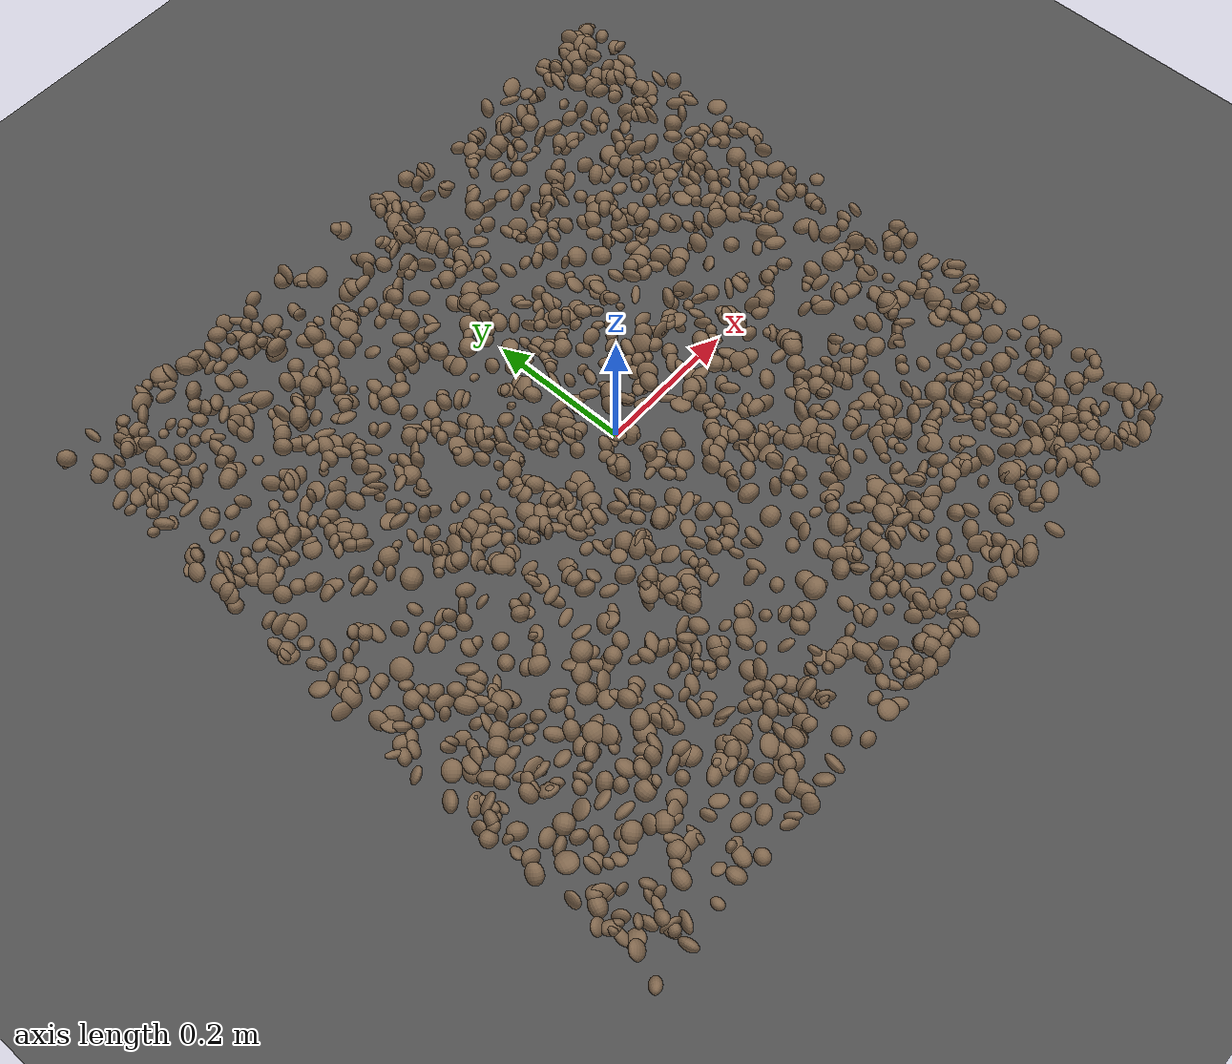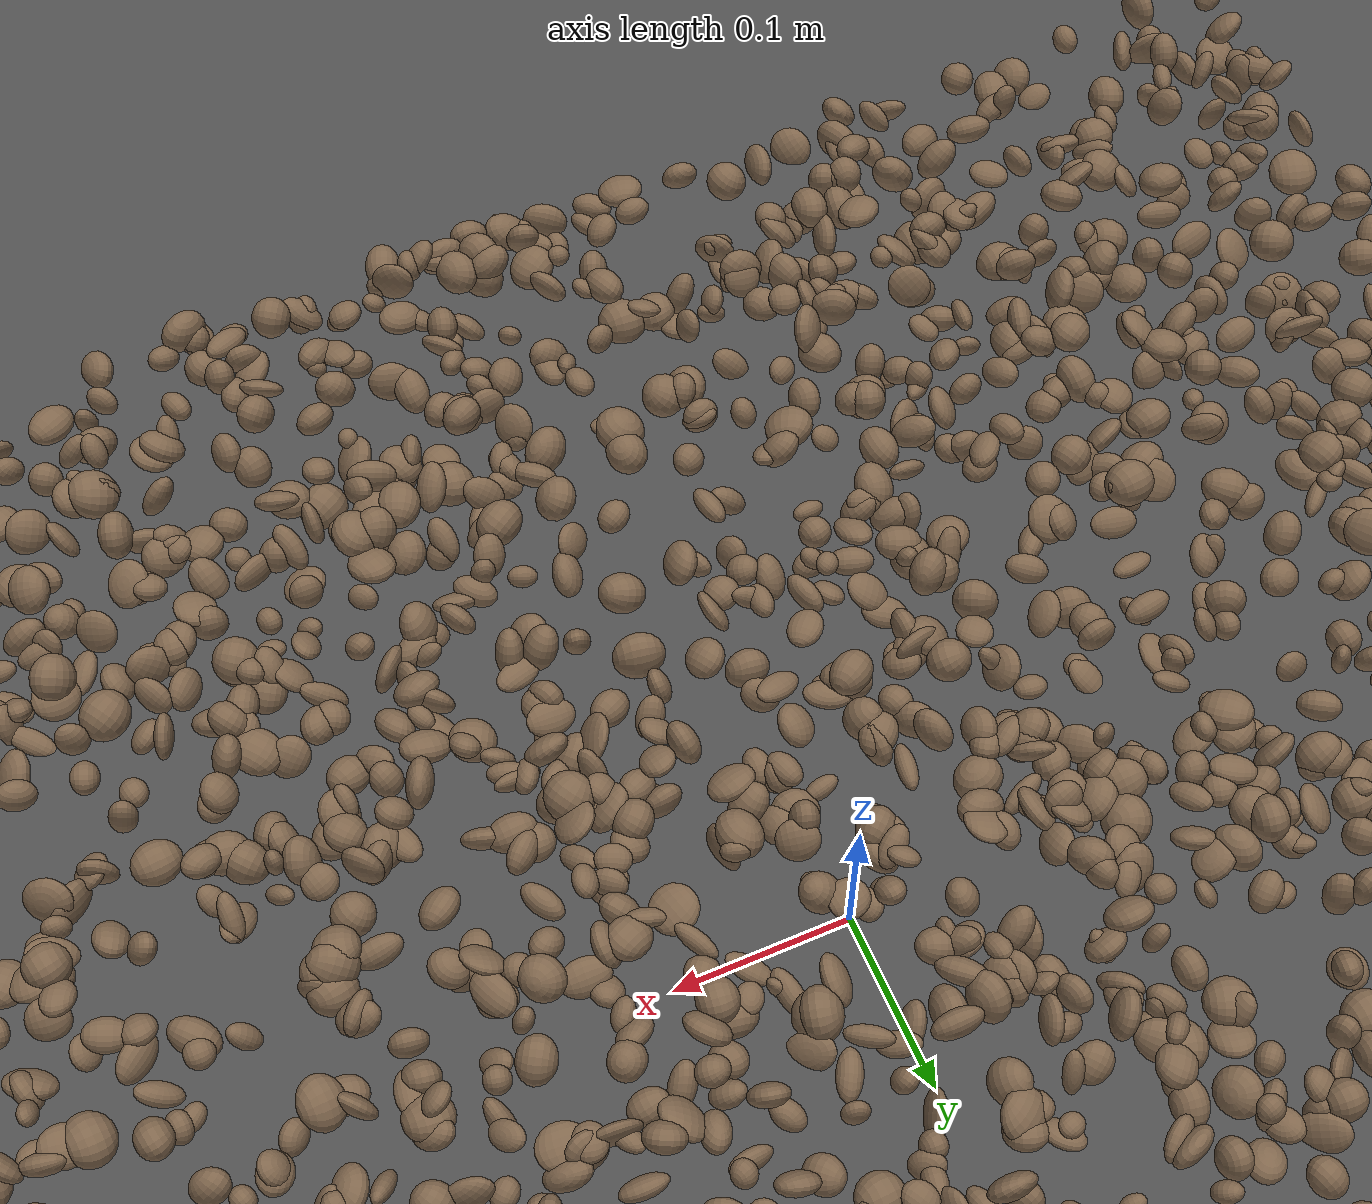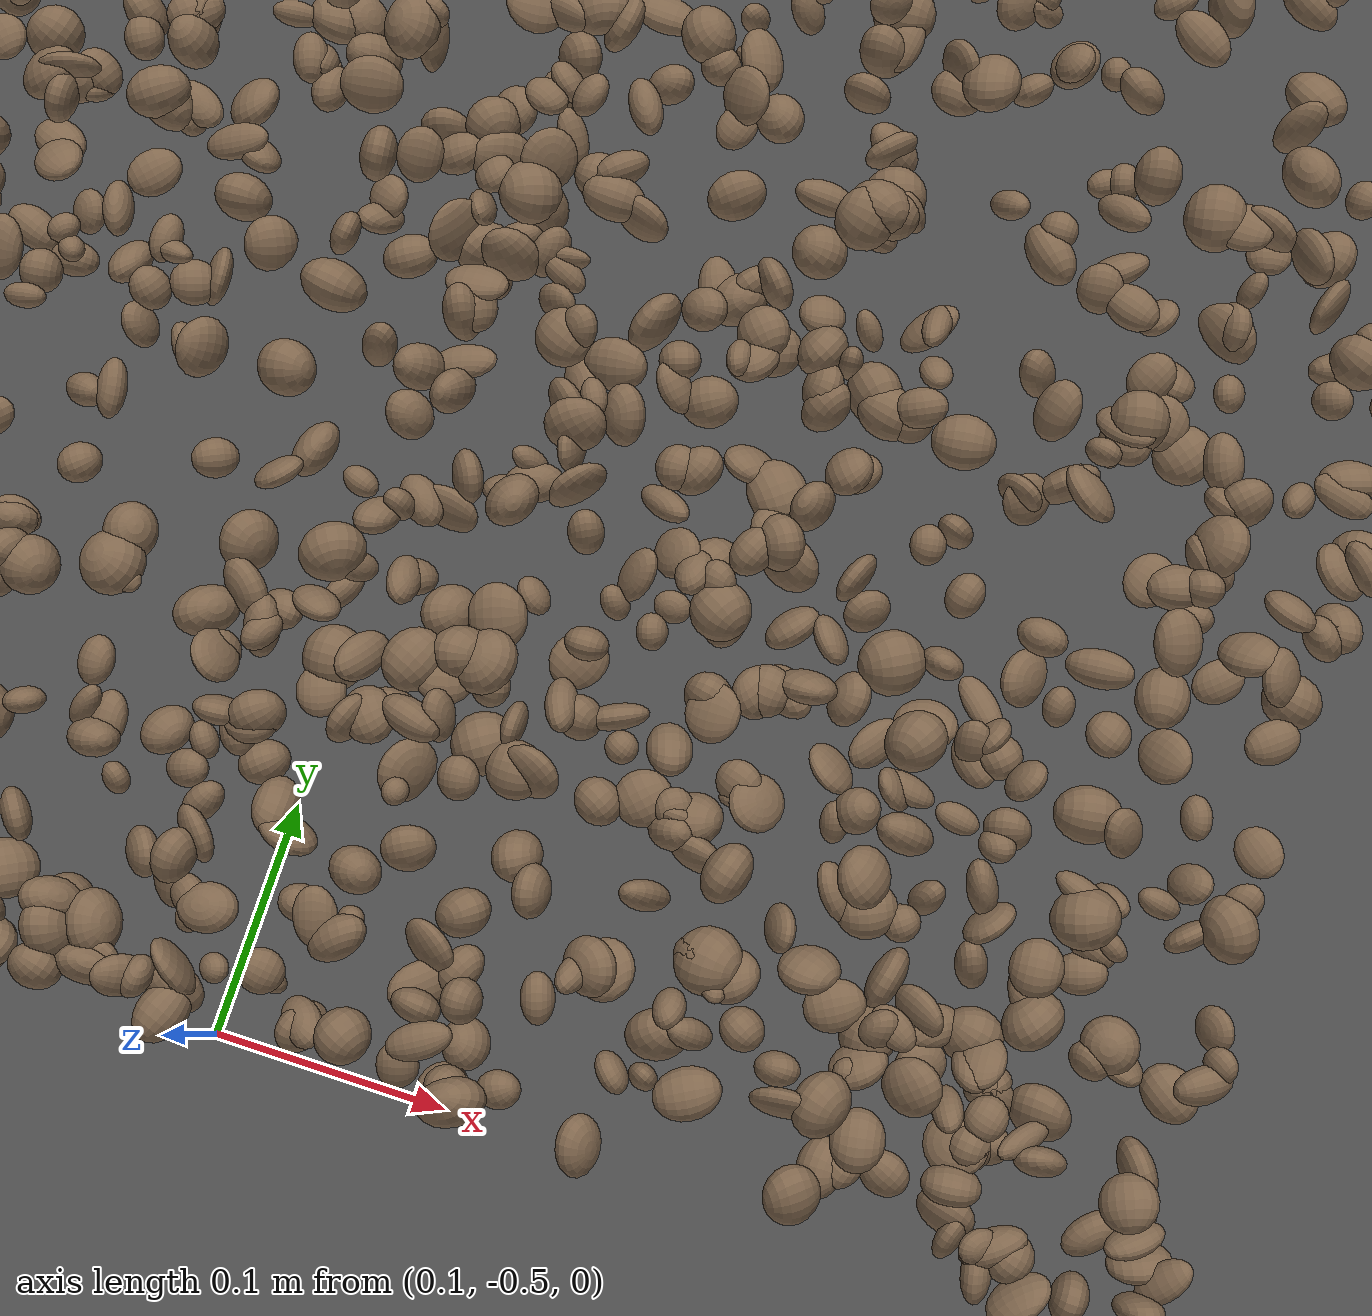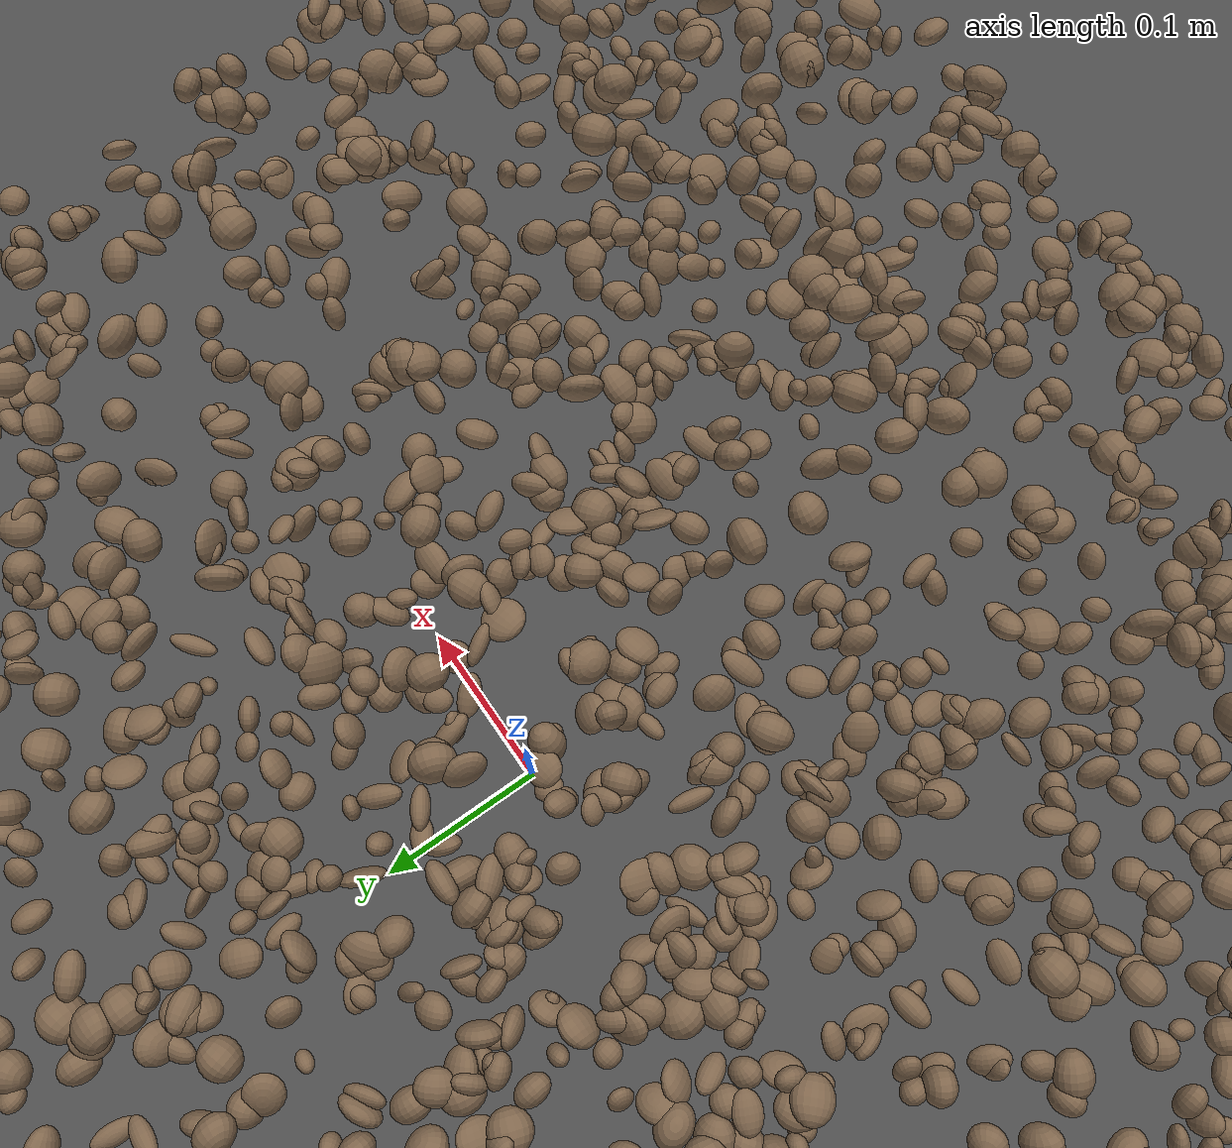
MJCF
<mujoco model="rocky_terrain_scene">
    <compiler angle="radian" inertiafromgeom="true" />
    <option timestep="0.002" gravity="0 0 -9.81" />

    <worldbody>
        <light name="sunlight" pos="5 5 5" dir="-1 -1 -1" diffuse="1 1 1" specular="0.5 0.5 0.5" ambient="0.5 0.5 0.5" />

        <geom name="ground_plane" type="plane" size="50 50 0.1" rgba="0.3 0.3 0.3 1" />

        <body name="rocky_terrain_body">

        <geom name="rock1" type="ellipsoid" size="0.010025153530856097 0.012338898900110496 0.010556547789949492" pos="0.49737363141071933 0.33265509674188487 0.011712045771916972" quat="0.27418568729871096 0.2780418564701569 0.24807548899299775 0.1996969672381344" rgba="0.5 0.4 0.3 1" /><geom name="rock2" type="ellipsoid" size="0.010258413980786873 0.007879400916567377 0.012358163657360458" pos="0.4896399778904015 -0.19922867915168319 0.0057601356933985924" quat="0.14152110722974026 0.2454908063386252 0.6018959546147036 0.011092131816930847" rgba="0.5 0.4 0.3 1" /><geom name="rock3" type="ellipsoid" size="0.011825101193295818 0.013179276938205864 0.011530195000947617" pos="0.08278607110594627 0.017638728284017358 0.012920916035835055" quat="0.4132130087245972 0.10705054552301942 0.4333063463602455 0.04643009939213787" rgba="0.5 0.4 0.3 1" /><geom name="rock4" type="ellipsoid" size="0.008976032775257894 0.008500476225967868 0.013922826590856332" pos="0.36950406317468476 0.1581635828447152 0.0023613235024059114" quat="0.31536510425419106 0.2791925394356632 0.10995275734621787 0.29548959896392796" rgba="0.5 0.4 0.3 1" /><geom name="rock5" type="ellipsoid" size="0.011942157610544585 0.01465600427239919 0.01244067558004673" pos="-0.4897141408734058 0.08907760108710394 0.0012103284249719848" quat="0.07675847959478727 0.1718423524116907 0.4231853531655273 0.32821381482799467" rgba="0.5 0.4 0.3 1" /><geom name="rock6" type="ellipsoid" size="0.0146338264030129 0.006302999228228481 0.006819005089138353" pos="0.20674615106172645 -0.23057650274433394 0.007463937088050783" quat="0.21591028945490265 0.043905699512075694 0.5639912156409392 0.1761927953920825" rgba="0.5 0.4 0.3 1" /><geom name="rock7" type="ellipsoid" size="0.012216091541785826 0.005682822535343896 0.013053499102468294" pos="0.39757344848987897 -0.13155247108131451 0.009362647003248915" quat="0.20413803202402925 0.3342054223645478 0.24184473626755335 0.2198118093438697" rgba="0.5 0.4 0.3 1" /><geom name="rock8" type="ellipsoid" size="0.014592739605973064 0.013935574827400377 0.005659546968619806" pos="-0.11127702088428515 0.4930525376063689 0.014417664802246186" quat="0.22765251209189863 0.2908390387492739 0.28259534220957205 0.1989131069492554" rgba="0.5 0.4 0.3 1" /><geom name="rock9" type="ellipsoid" size="0.011268279525913076 0.012746697370752142 0.0062107422009478365" pos="0.4039523061030892 0.08168574763019076 0.00022833744136113498" quat="0.03432701697135437 0.3520210543532335 0.5002462376875147 0.1134056909878974" rgba="0.5 0.4 0.3 1" /><geom name="rock10" type="ellipsoid" size="0.008126339705006416 0.009794607587082694 0.01263477673024343" pos="-0.112181830813611 -0.22417665034266732 0.009299190269280305" quat="0.24601423686535137 0.1846266340943555 0.5037855736818148 0.06557355535847842" rgba="0.5 0.4 0.3 1" /><geom name="rock11" type="ellipsoid" size="0.014227289029026351 0.013497505565918617 0.011539271883922175" pos="0.12776903739130985 0.221375401125667 0.005071064737297219" quat="0.3574388007637096 0.08244016448820274 0.2186551895176124 0.34146584523047524" rgba="0.5 0.4 0.3 1" /><geom name="rock12" type="ellipsoid" size="0.006137050640614946 0.009607803218528273 0.014998860464023073" pos="0.3864770183426155 0.21330346898200103 0.00979926467835932" quat="0.2043207334194874 0.15787166499726502 0.29213932219179056 0.34566827939145706" rgba="0.5 0.4 0.3 1" /><geom name="rock13" type="ellipsoid" size="0.006209647905914805 0.00884922729036118 0.00761648812906301" pos="-0.4201613722477434 0.045451602913520905 0.011139003837555448" quat="0.271446202436009 0.27136243197601695 0.4025636501141686 0.054627715473805544" rgba="0.5 0.4 0.3 1" /><geom name="rock14" type="ellipsoid" size="0.014708159272731308 0.008287068638050961 0.013501511058344313" pos="-0.030757203005709832 0.1333793636587567 0.013759113133054508" quat="0.5144383609132089 0.24174135964798754 0.0705718097993189 0.17324846963948456" rgba="0.5 0.4 0.3 1" /><geom name="rock15" type="ellipsoid" size="0.008694196332319479 0.010224835721121197 0.008051597397455442" pos="0.3398979325289261 -0.2301451505195078 0.01409715048015489" quat="0.46040683674376837 0.13296764688118914 0.3827623271065036 0.023863189268538875" rgba="0.5 0.4 0.3 1" /><geom name="rock16" type="ellipsoid" size="0.005379488732728754 0.007227328844317033 0.011036498486909244" pos="-0.11608786662863912 0.11114714848960394 0.0007915115945354644" quat="0.24233541776525275 0.32361549470389617 0.2829477091762894 0.1511013783545617" rgba="0.5 0.4 0.3 1" /><geom name="rock17" type="ellipsoid" size="0.010085433890319247 0.00815063954770119 0.01047458392334784" pos="-0.01637176401602769 -0.2019453392813949 0.011685195675125526" quat="0.17490889800745468 0.22512350739105408 0.32771282581501465 0.27225476878647653" rgba="0.5 0.4 0.3 1" /><geom name="rock18" type="ellipsoid" size="0.00728257783917576 0.014038025927008122 0.010406032026931708" pos="0.45178478419924395 0.3974123556111846 0.009076233419947849" quat="0.22494719552233186 0.014511215610657834 0.4265569408500806 0.3339846480169298" rgba="0.5 0.4 0.3 1" /><geom name="rock19" type="ellipsoid" size="0.00927529474316385 0.014286104035159633 0.0070497817393471475" pos="-0.16213812790217808 -0.2574379687168503 0.012449383651292308" quat="0.3983810987469096 0.032407236881193256 0.2561702207599528 0.3130414436119443" rgba="0.5 0.4 0.3 1" /><geom name="rock20" type="ellipsoid" size="0.005964823717595072 0.014008284492953535 0.01231097111416333" pos="0.2995448166308794 0.16310569439065548 0.0125358384921477" quat="0.3924149802996559 0.35352445548905587 0.1888024086340731 0.06525815557721504" rgba="0.5 0.4 0.3 1" /><geom name="rock21" type="ellipsoid" size="0.010642299798098104 0.01227375659759345 0.014940262222538785" pos="0.04756440305128806 0.4454859111781534 0.014064616944965387" quat="0.3104436326615151 0.05619939319283495 0.3077074909892692 0.3256494831563807" rgba="0.5 0.4 0.3 1" /><geom name="rock22" type="ellipsoid" size="0.013895301785989609 0.009260243721309906 0.009277363451194023" pos="-0.35669566760704896 -0.2221468522287261 0.008845064893263477" quat="0.10990592769916183 0.2192776838483559 0.2758504357414192 0.39496595271106305" rgba="0.5 0.4 0.3 1" /><geom name="rock23" type="ellipsoid" size="0.013057302526140336 0.008331506317675317 0.008869405389072035" pos="0.11008729500154235 0.07736430163406738 0.0031560951175362392" quat="0.007679898030432454 0.49137404965586523 0.33831780324854827 0.16262824906515402" rgba="0.5 0.4 0.3 1" /><geom name="rock24" type="ellipsoid" size="0.014931615873501357 0.009745387697872414 0.010100056697894953" pos="-0.30203588086371114 -0.3247946154890997 0.010741687556772196" quat="0.04678978602335463 0.43399443369207735 0.11835000181502084 0.4008657784695472" rgba="0.5 0.4 0.3 1" /><geom name="rock25" type="ellipsoid" size="0.014896780561828617 0.012930404865110861 0.0063492512510714945" pos="0.37747947888600386 -0.17097041969776283 0.011140483195016922" quat="0.050307365200609806 0.1795649808320658 0.24448595082327088 0.5256417031440536" rgba="0.5 0.4 0.3 1" /><geom name="rock26" type="ellipsoid" size="0.01068316931955446 0.011805606424354409 0.012106748951450082" pos="-0.3673366958132305 -0.41849642023735556 0.007397777018621609" quat="0.0267436584862977 0.4732921866567635 0.012614024618339307 0.4873501302385996" rgba="0.5 0.4 0.3 1" /><geom name="rock27" type="ellipsoid" size="0.010732943319473096 0.0097033570409139 0.011187130243928735" pos="-0.47903274221846814 0.4411904896085965 0.008476016093027316" quat="0.1614100691599355 0.28803978515234024 0.17911722544225678 0.3714329202454674" rgba="0.5 0.4 0.3 1" /><geom name="rock28" type="ellipsoid" size="0.006641665334728284 0.011803029134325889 0.013636029132833127" pos="0.4893060498356765 -0.4695724585906247 0.003169964751234043" quat="0.1064303561389021 0.28594773962622366 0.24561049136697927 0.362011412867895" rgba="0.5 0.4 0.3 1" /><geom name="rock29" type="ellipsoid" size="0.013250417273057022 0.006143172658010367 0.007389678113200371" pos="-0.19305616557089622 0.012404048771556653 0.012136032477678185" quat="0.10343679539502441 0.2684730146270207 0.3038044564649141 0.3242857335130407" rgba="0.5 0.4 0.3 1" /><geom name="rock30" type="ellipsoid" size="0.007359824066047103 0.007732367567085943 0.013099911979497055" pos="-0.045908920242971996 -0.26005980664624617 0.006208889587577132" quat="0.3763891932371009 0.1558966565534035 0.11475544776301558 0.3529587024464799" rgba="0.5 0.4 0.3 1" /><geom name="rock31" type="ellipsoid" size="0.012923286774917931 0.007240553058949113 0.007631602082546133" pos="0.4128779362623348 -0.42294216378213556 0.0038964758854393086" quat="0.08762017211145288 0.22121527997795223 0.12252560363928444 0.5686389442713105" rgba="0.5 0.4 0.3 1" /><geom name="rock32" type="ellipsoid" size="0.0082473502168175 0.009633429317312207 0.007606221052566692" pos="0.05161457920183643 0.4785582133240768 0.009584400241831796" quat="0.318194463625011 0.2848026116202585 0.37565442111676745 0.02134850363796302" rgba="0.5 0.4 0.3 1" /><geom name="rock33" type="ellipsoid" size="0.006873390691942479 0.006622073715850547 0.0066103928019837785" pos="-0.4695942970282124 0.27337794426642315 0.006631669194131932" quat="0.009857061447311187 0.34504883482878085 0.43115079542572327 0.2139433082981848" rgba="0.5 0.4 0.3 1" /><geom name="rock34" type="ellipsoid" size="0.008274983870274002 0.010744233511971695 0.013767977257543567" pos="-0.2959193561207081 -0.45178469568318413 0.011162089207684528" quat="0.3282733144466464 0.20804687803683924 0.3448596714806657 0.11882013603584875" rgba="0.5 0.4 0.3 1" /><geom name="rock35" type="ellipsoid" size="0.013202800541975063 0.008200825360851708 0.005756401386779809" pos="-0.4861207723366885 -0.4254971022552956 0.012853986078592257" quat="0.43647645916268696 0.041426046882028125 0.3872014100169805 0.1348960839383044" rgba="0.5 0.4 0.3 1" /><geom name="rock36" type="ellipsoid" size="0.012585881766794944 0.009520692556934081 0.008850178535764062" pos="0.42836100629954865 0.38264206331590267 0.0077622956577192625" quat="0.38246101216878353 0.2653655259813462 0.014367352260568133 0.3378061095893021" rgba="0.5 0.4 0.3 1" /><geom name="rock37" type="ellipsoid" size="0.012899403773682202 0.006674898840433525 0.011102074220399927" pos="-0.11752606332151116 0.006090279631178475 0.0050369338026124135" quat="0.051805142156954934 0.39305824078711393 0.3346082320492468 0.2205283850066844" rgba="0.5 0.4 0.3 1" /><geom name="rock38" type="ellipsoid" size="0.0058966723292176145 0.006406903573116509 0.00996031386450005" pos="-0.2809690161098861 0.2396431125276276 0.010143422299072946" quat="0.19552678126631728 0.19427440909216143 0.30843868435052746 0.3017601252909938" rgba="0.5 0.4 0.3 1" /><geom name="rock39" type="ellipsoid" size="0.01272997704650777 0.011533844225113304 0.009483930980988087" pos="-0.19138041091683655 0.3386365418439816 0.006115928174829967" quat="0.23164707636981485 0.26032480230737576 0.24809812371607476 0.2599299976067346" rgba="0.5 0.4 0.3 1" /><geom name="rock40" type="ellipsoid" size="0.009016129632642459 0.010211807221490884 0.007614321434862625" pos="-0.4227709510959403 0.2904474553176509 0.011570709100463903" quat="0.2722495352365646 0.315812112150619 0.05684044233796565 0.3550979102748508" rgba="0.5 0.4 0.3 1" /><geom name="rock41" type="ellipsoid" size="0.008805328585430365 0.01157950749278974 0.011163089344489159" pos="-0.3157496766109186 -0.14020811308960235 0.008993261190621315" quat="0.2449722427038886 0.1740380639809152 0.2278797405157645 0.3531099527994318" rgba="0.5 0.4 0.3 1" /><geom name="rock42" type="ellipsoid" size="0.009420525842437723 0.014505663922715926 0.011146710636388675" pos="-0.23675221652715417 -0.3899854154525685 0.012026898466194777" quat="0.21501253556164115 0.26954438328368135 0.3843890334907206 0.13105404766395684" rgba="0.5 0.4 0.3 1" /><geom name="rock43" type="ellipsoid" size="0.005125438883861926 0.013457165412446851 0.008189507656605864" pos="-0.15012713482361606 -0.24019503367656225 0.003342911461653387" quat="0.1919865814091679 0.3585850541898276 0.3992677371772294 0.05016062722377505" rgba="0.5 0.4 0.3 1" /><geom name="rock44" type="ellipsoid" size="0.013501097395302381 0.0073106914994177374 0.00955111736476004" pos="-0.04589214542330777 -0.2014510688372485 0.010636953035927304" quat="0.4078928571781639 0.02841476541565057 0.2865733181830499 0.2771190592231355" rgba="0.5 0.4 0.3 1" /><geom name="rock45" type="ellipsoid" size="0.010462446471791127 0.013601808435452691 0.006710877828519306" pos="-0.31252344192602055 -0.272878238780774 0.011102674817349549" quat="0.3834233573143786 0.1153775183514744 0.45264551670352127 0.04855360763062581" rgba="0.5 0.4 0.3 1" /><geom name="rock46" type="ellipsoid" size="0.0076925800215474046 0.012154726429990034 0.009007753737150757" pos="-0.028656903842472436 -0.02587688773403829 0.002920817009523961" quat="0.13705070954147863 0.6303904385503916 0.20717043467827098 0.025388417229858764" rgba="0.5 0.4 0.3 1" /><geom name="rock47" type="ellipsoid" size="0.006649607661855532 0.007485284506144071 0.012398723446568921" pos="0.25386434212372533 0.3369944348036329 0.011515478140024267" quat="0.3664753364084075 0.042128673569561494 0.300328398694139 0.29106759132789195" rgba="0.5 0.4 0.3 1" /><geom name="rock48" type="ellipsoid" size="0.005762376145386037 0.011205978919214599 0.011879387810743304" pos="0.48302333320640933 0.15511946611486704 0.01108957022751248" quat="0.38940322620801837 0.4162806897501158 0.13550989743383796 0.05880618660802777" rgba="0.5 0.4 0.3 1" /><geom name="rock49" type="ellipsoid" size="0.010514103816645859 0.010253252210412088 0.011700771047405908" pos="-0.42130939915082133 0.14056024775621834 0.007111056402459652" quat="0.10160788555492284 0.1590467083898875 0.5566393570421306 0.182706049013059" rgba="0.5 0.4 0.3 1" /><geom name="rock50" type="ellipsoid" size="0.006343899208394474 0.01379587216067071 0.013708350999952608" pos="-0.16465213657537536 -0.27266033441413107 0.0009099457147595435" quat="0.03247210947513975 0.2517074654544383 0.45935291802987305 0.25646750704054894" rgba="0.5 0.4 0.3 1" /><geom name="rock51" type="ellipsoid" size="0.01342875884897023 0.007672099197670248 0.014047812306241279" pos="-0.44635252371045575 0.4013476358254612 0.004035355942004656" quat="0.09854670758165963 0.00024067331335174318 0.27866383587373084 0.6225487832312578" rgba="0.5 0.4 0.3 1" /><geom name="rock52" type="ellipsoid" size="0.010888011571403773 0.011283838996967267 0.011236037268663374" pos="-0.3565267614914801 0.3438431265787285 0.003494711534608999" quat="0.1918304838998614 0.2493497295744522 0.14379440836633353 0.4150253781593528" rgba="0.5 0.4 0.3 1" /><geom name="rock53" type="ellipsoid" size="0.008878848322650169 0.0059042175806464795 0.00786806261679987" pos="-0.11215313356676726 -0.3299968053662138 0.008726918809902718" quat="0.5324200313751641 0.2380320303614463 0.06589399698402772 0.16365394127936184" rgba="0.5 0.4 0.3 1" /><geom name="rock54" type="ellipsoid" size="0.009630483472443104 0.00580640922142794 0.013245168010663822" pos="0.08032336671615625 -0.31740224918314486 0.009652798410828679" quat="0.5513204088464201 0.15621055913177606 0.21010574687714934 0.0823632851446545" rgba="0.5 0.4 0.3 1" /><geom name="rock55" type="ellipsoid" size="0.0118590758397491 0.012649507220315402 0.01269979335293428" pos="0.028331614070288724 0.3288772681948604 0.00980318643153223" quat="0.04868926242382164 0.3294053371016912 0.3132652369822894 0.3086401634921978" rgba="0.5 0.4 0.3 1" /><geom name="rock56" type="ellipsoid" size="0.01346699249284257 0.013647015000313421 0.008999149680835285" pos="-0.19090032881342256 0.33487170467084804 0.0130900193530004" quat="0.2384469699412437 0.3375041363111992 0.06742066239169346 0.3566282313558637" rgba="0.5 0.4 0.3 1" /><geom name="rock57" type="ellipsoid" size="0.013231094605071311 0.01149691135043979 0.013781706472081382" pos="-0.3543067089277867 -0.38757284034555683 0.01357280565075467" quat="0.2704013488556606 0.05973610473780045 0.3365509846199216 0.3333115617866174" rgba="0.5 0.4 0.3 1" /><geom name="rock58" type="ellipsoid" size="0.012315785663727537 0.0064809825706632785 0.00682322009941236" pos="-0.08187817346727622 0.3747243603860144 0.008603001065661123" quat="0.3347532307736878 0.26076839992896583 0.33966817842393016 0.06481019087341618" rgba="0.5 0.4 0.3 1" /><geom name="rock59" type="ellipsoid" size="0.010024122735810645 0.008295492976669112 0.009478660642710763" pos="0.466524569620985 0.07413557196218568 0.002500932146429174" quat="0.036375395625370156 0.7171373181269081 0.11415368820711864 0.1323335980406032" rgba="0.5 0.4 0.3 1" /><geom name="rock60" type="ellipsoid" size="0.008454214249439814 0.008474373701141165 0.014991116643143461" pos="0.4038696751202042 -0.24059385893663232 0.004178538455968716" quat="0.34678128930179764 0.15526661630004765 0.28899285207200004 0.20895924232615457" rgba="0.5 0.4 0.3 1" /><geom name="rock61" type="ellipsoid" size="0.008478597910152525 0.010024876217553134 0.00653122497390643" pos="-0.407393371930834 0.4773449716871605 0.013467769493568397" quat="0.12320696092457666 0.04595862321759126 0.16606319124719413 0.6647712246106379" rgba="0.5 0.4 0.3 1" /><geom name="rock62" type="ellipsoid" size="0.014249513567490019 0.010101158966731935 0.009567862862682908" pos="-0.07975208143386792 0.0719109861059879 0.0026057044751510786" quat="0.35465200329403646 0.10051034130084516 0.3437557638804482 0.2010818915246702" rgba="0.5 0.4 0.3 1" /><geom name="rock63" type="ellipsoid" size="0.012326010247180426 0.006507647385095279 0.008171159532398142" pos="0.36221456522707896 -0.28823112996622346 0.007612076268298766" quat="0.13233012860202553 0.32838293045562394 0.14506543966789626 0.3942215012744542" rgba="0.5 0.4 0.3 1" /><geom name="rock64" type="ellipsoid" size="0.006919500296581111 0.006432130490024216 0.007678829261790374" pos="0.35431094322966084 -0.43355559322540826 0.008583986583089454" quat="0.14926354325608085 0.32170885700239993 0.24104460957799614 0.2879829901635231" rgba="0.5 0.4 0.3 1" /><geom name="rock65" type="ellipsoid" size="0.009322990851951658 0.011087880747630098 0.008133965220893644" pos="-0.3162823400583218 0.413651842776823 0.003063607782812334" quat="0.15532132353640843 0.11883106871782131 0.4518387943573914 0.2740088133883789" rgba="0.5 0.4 0.3 1" /><geom name="rock66" type="ellipsoid" size="0.014073576023046052 0.007838664115997047 0.013421033899955432" pos="-0.13092997113106752 0.057958921540040675 0.010493002908781007" quat="0.12519917844771736 0.3785645866368057 0.14555033287205169 0.35068590204342515" rgba="0.5 0.4 0.3 1" /><geom name="rock67" type="ellipsoid" size="0.00662110041156956 0.013191274404120136 0.008621780731102077" pos="-0.058087972633271256 -0.18155019777989967 0.014752522886906868" quat="0.09355307923075688 0.7622597919503067 0.13497785037902427 0.009209278439912174" rgba="0.5 0.4 0.3 1" /><geom name="rock68" type="ellipsoid" size="0.00842886535873202 0.00819159805248346 0.014196758991854411" pos="-0.3742754607458192 0.21688374788661036 0.014956064931388811" quat="0.10526355183748021 0.10020495236762425 0.40911768173731405 0.38541381405758135" rgba="0.5 0.4 0.3 1" /><geom name="rock69" type="ellipsoid" size="0.01206301889759517 0.012050970519085921 0.008791900800321538" pos="-0.23484737829589453 -0.37682425681158327 0.006796435719225619" quat="0.009486897724082562 0.6464828602503084 0.03415627807036665 0.3098739639552423" rgba="0.5 0.4 0.3 1" /><geom name="rock70" type="ellipsoid" size="0.007473730044565188 0.005950136889176647 0.012386960001606384" pos="-0.49050509446416446 0.25943778310366405 0.0015213192874978297" quat="0.07292285360568256 0.3168859344924116 0.28185731668682934 0.3283338952150765" rgba="0.5 0.4 0.3 1" /><geom name="rock71" type="ellipsoid" size="0.01476898498415977 0.013132152585061622 0.011343290291929799" pos="0.48528547032213276 -0.3293715491562248 0.010705882323842376" quat="0.08361195061466611 0.25638441718515814 0.37772198155350595 0.2822816506466699" rgba="0.5 0.4 0.3 1" /><geom name="rock72" type="ellipsoid" size="0.010484229999109088 0.013268432229559077 0.01367838301354593" pos="-0.40436995794197916 0.13205014730212228 0.005361780946461491" quat="0.0312130548956375 0.4470984413549063 0.44374127893892734 0.07794722481052878" rgba="0.5 0.4 0.3 1" /><geom name="rock73" type="ellipsoid" size="0.012350630045278362 0.00917699288032295 0.008386330473110713" pos="0.050863279392589056 0.32754109795414854 0.011589973701668319" quat="0.025446468710754084 0.646619899493741 0.12877144354439565 0.19916218825110935" rgba="0.5 0.4 0.3 1" /><geom name="rock74" type="ellipsoid" size="0.014333095649778322 0.014666654385569373 0.013600521530981756" pos="-0.32201096446072874 0.04590677652308939 0.00679121619682955" quat="0.433888277822981 0.40880983085810846 0.14044924478962598 0.016852646529284587" rgba="0.5 0.4 0.3 1" /><geom name="rock75" type="ellipsoid" size="0.011572475078675749 0.008360340580313645 0.011046052981459699" pos="0.2772529636160638 -0.1940638944671188 0.012702295443298497" quat="0.3345275409352014 0.005012708297851324 0.3207384650688199 0.33972128569812743" rgba="0.5 0.4 0.3 1" /><geom name="rock76" type="ellipsoid" size="0.006897827956506157 0.01080570295246953 0.012220205797804837" pos="-0.34496103247454224 0.2681707112991568 0.013448146821176335" quat="0.3624268411905462 0.3737624977604742 0.2305414450505679 0.033269215998411795" rgba="0.5 0.4 0.3 1" /><geom name="rock77" type="ellipsoid" size="0.011809793860040258 0.010496516754521618 0.00954526678963466" pos="0.2008322795294395 -0.05294374589112716 0.011070983950941153" quat="0.15408536100939932 0.2233268220167093 0.6049892832678506 0.017598533706040892" rgba="0.5 0.4 0.3 1" /><geom name="rock78" type="ellipsoid" size="0.005327503857610133 0.010036531971807053 0.008922418116485803" pos="0.3274284372357259 0.25431680963514935 0.0067366410537328825" quat="0.41032881769590923 0.39374489145650243 0.13238140001572724 0.06354489083186111" rgba="0.5 0.4 0.3 1" /><geom name="rock79" type="ellipsoid" size="0.009436222273461942 0.012114687184832475 0.007759820651657624" pos="0.1071765505849509 -0.0669782236800539 0.002663398186051038" quat="0.41335146094217234 0.17721546161919735 0.047463350986186835 0.3619697264524436" rgba="0.5 0.4 0.3 1" /><geom name="rock80" type="ellipsoid" size="0.005995315115936072 0.011537988992212471 0.01365361156000948" pos="0.4382534525934967 -0.042213138262066185 0.014425296970598293" quat="0.48180922696787387 0.26053728915218166 0.16166819572147303 0.09598528815847145" rgba="0.5 0.4 0.3 1" /><geom name="rock81" type="ellipsoid" size="0.0059123046142262 0.00523802878886526 0.013426835896646335" pos="0.43446425106721276 0.32838349547185763 0.013439564390947666" quat="0.11215416914843268 0.30664013610631846 0.4261091587212208 0.15509653602402812" rgba="0.5 0.4 0.3 1" /><geom name="rock82" type="ellipsoid" size="0.008189968270722468 0.005637361556821296 0.007294792134769839" pos="0.2615840642709414 0.2401951626309501 0.014829581670110977" quat="0.46240422145021143 0.08839938657725747 0.20043711692865815 0.24875927504387302" rgba="0.5 0.4 0.3 1" /><geom name="rock83" type="ellipsoid" size="0.005657578789905781 0.007724551265574491 0.013951676827861872" pos="-0.3862140932305772 0.27606978912077096 0.01178499869604428" quat="0.17326854940078787 0.37775339504042743 0.4236092256159906 0.025368829942794085" rgba="0.5 0.4 0.3 1" /><geom name="rock84" type="ellipsoid" size="0.010133516729878847 0.012498653571358565 0.012927017446763587" pos="-0.032097556478919764 0.11556195182944007 0.014201738163986063" quat="0.10117800702879962 0.6830449227604867 0.028287290639850016 0.1874897795708637" rgba="0.5 0.4 0.3 1" /><geom name="rock85" type="ellipsoid" size="0.00514182243169366 0.014860656612242482 0.014675724547713487" pos="0.007073190964495546 0.11328745554702024 0.0019982907316543307" quat="0.13074278514171864 0.05068108830136113 0.4710772769556566 0.3474988496012637" rgba="0.5 0.4 0.3 1" /><geom name="rock86" type="ellipsoid" size="0.011957732307248743 0.013577998253451427 0.007716281837628796" pos="-0.47914910542997813 -0.05666139138234205 0.005297549460423942" quat="0.23960770403455536 0.09808490362950734 0.512568193391977 0.14973919894396034" rgba="0.5 0.4 0.3 1" /><geom name="rock87" type="ellipsoid" size="0.00761102165629483 0.009655631992370892 0.010019216807668995" pos="0.4339446652110016 -0.20768502179294224 0.005022860938594337" quat="0.2802689164177578 0.20853907280191541 0.1769851149603467 0.33420689581998" rgba="0.5 0.4 0.3 1" /><geom name="rock88" type="ellipsoid" size="0.008707696681818857 0.011009292919401078 0.005911075004550789" pos="0.02268930878172981 0.13542667711522305 0.007087151444080443" quat="0.3517880130051276 0.02774870724305524 0.28563304391435396 0.33483023583746324" rgba="0.5 0.4 0.3 1" /><geom name="rock89" type="ellipsoid" size="0.0143278511130604 0.006344850326465156 0.010835142262072986" pos="0.09624779546002293 0.16899459182051613 0.008077790708509435" quat="0.2611817685277174 0.38861184592867054 0.2535211609311305 0.09668522461248154" rgba="0.5 0.4 0.3 1" /><geom name="rock90" type="ellipsoid" size="0.010950548648710205 0.007675200187181673 0.005995846158229797" pos="-0.1378552580695389 -0.00573734343972665 3.25442828221123e-05" quat="0.45341305945698734 0.05529900636680465 0.1815769797340014 0.30971095444220664" rgba="0.5 0.4 0.3 1" /><geom name="rock91" type="ellipsoid" size="0.011024741360668791 0.005442886642871152 0.007181481770215487" pos="-0.13972205531552018 0.04048833742604385 0.011318400157701846" quat="0.4232250812224238 0.21540683396456412 0.2093661447852487 0.15200194002776332" rgba="0.5 0.4 0.3 1" /><geom name="rock92" type="ellipsoid" size="0.008116087967407037 0.009094024870189149 0.010146394349990921" pos="0.04975726745505882 0.3238396283240377 0.011957832313220665" quat="0.0782439241815185 0.3611791177322065 0.07857759410786942 0.48199936397840554" rgba="0.5 0.4 0.3 1" /><geom name="rock93" type="ellipsoid" size="0.014368474958025113 0.012978240364925678 0.005467385209643607" pos="0.1115352289394187 -0.10295000539466681 0.01375057305290449" quat="0.3544329157566267 0.21035506048229324 0.00028139342970384543 0.43493063033137624" rgba="0.5 0.4 0.3 1" /><geom name="rock94" type="ellipsoid" size="0.007352653049928741 0.011741620442826268 0.014154666221705088" pos="0.46111997914158 -0.21654237615423066 0.01174371912301279" quat="0.19238687881240477 0.260308705063014 0.032357542444591644 0.5149468736799896" rgba="0.5 0.4 0.3 1" /><geom name="rock95" type="ellipsoid" size="0.010171742847103805 0.007518546283662084 0.008467344906161434" pos="0.23891401980311044 -0.2573061237682892 0.014479920170997505" quat="0.228649598198684 0.26744723250287444 0.08481579497273348 0.419087374325708" rgba="0.5 0.4 0.3 1" /><geom name="rock96" type="ellipsoid" size="0.005615129362334422 0.008431260802226356 0.012435568149072089" pos="-0.41761363181982714 -0.22873970338919458 0.00342105460053393" quat="0.374679773219427 0.3280717393955675 0.14862293648575753 0.14862555089924798" rgba="0.5 0.4 0.3 1" /><geom name="rock97" type="ellipsoid" size="0.013087274518342473 0.008072886147707075 0.005457475670339217" pos="-0.22612806683203002 -0.3223804313602824 0.011819105672772317" quat="0.1949480885955941 0.3452320599513983 0.19655817308153453 0.263261678371473" rgba="0.5 0.4 0.3 1" /><geom name="rock98" type="ellipsoid" size="0.005577395370246557 0.00735792908781855 0.007727750637415046" pos="0.18633003341681043 0.28140297885849863 0.014688978457827939" quat="0.2887523963170616 0.3042083871867819 0.37078077194413656 0.0362584445520199" rgba="0.5 0.4 0.3 1" /><geom name="rock99" type="ellipsoid" size="0.005564452252723483 0.005880587634315875 0.0056123475463482455" pos="0.20647800582109055 0.2721575877507947 0.012744587115020245" quat="0.21641801740215263 0.27670023312883746 0.3035005810293521 0.20338116843965784" rgba="0.5 0.4 0.3 1" /><geom name="rock100" type="ellipsoid" size="0.012850371140580508 0.009631342981560213 0.01190162715758833" pos="-0.32430091187345944 -0.1975310717355092 0.0072101252321506715" quat="0.4851088915007897 0.18722725039131438 0.17654104217994762 0.15112281592794827" rgba="0.5 0.4 0.3 1" /><geom name="rock101" type="ellipsoid" size="0.006292560909899865 0.012077810677350535 0.011672123463773333" pos="0.00379777966356043 0.3844345001314048 0.002359335117783858" quat="0.21421066505550226 0.36678803647835834 0.19278786535230827 0.22621343311383113" rgba="0.5 0.4 0.3 1" /><geom name="rock102" type="ellipsoid" size="0.006762092404897522 0.006448848644710847 0.007242915683876489" pos="-0.1791104634914259 -0.08734696316495283 0.0015244105725803624" quat="0.3001148113265686 0.13881317574659507 0.32618465886845177 0.23488735405838457" rgba="0.5 0.4 0.3 1" /><geom name="rock103" type="ellipsoid" size="0.012207799008928578 0.010035848229041213 0.00885136711613962" pos="0.24932910856186719 -0.23938460816687313 0.013522519190041573" quat="0.30289224956059735 0.308954239650682 0.18691320300856692 0.20124030778015364" rgba="0.5 0.4 0.3 1" /><geom name="rock104" type="ellipsoid" size="0.006208495804905683 0.010470318158753773 0.006845968760607842" pos="-0.4875151124101943 0.36987262819846456 0.01380785589504784" quat="0.08845363450791614 0.34611984186242334 0.24991189642580838 0.3155146272038522" rgba="0.5 0.4 0.3 1" /><geom name="rock105" type="ellipsoid" size="0.014683637304776558 0.007655880096328031 0.011286739359314225" pos="0.4308302305976327 -0.22153151655492775 0.014697375093279837" quat="0.10944658209440249 0.2885168075348456 0.33121117988622667 0.2708254304845252" rgba="0.5 0.4 0.3 1" /><geom name="rock106" type="ellipsoid" size="0.009155544019468673 0.007601271403074376 0.010893458638952329" pos="0.2157949819111601 0.31668359275588287 0.009079346549723689" quat="0.3560611680248518 0.0009608263093622184 0.2543852560304471 0.38859274963533896" rgba="0.5 0.4 0.3 1" /><geom name="rock107" type="ellipsoid" size="0.010191872669395554 0.00509185355843275 0.01337115092654484" pos="-0.38036580203297166 -0.15879017148596752 0.011203788678660603" quat="0.4439758058537878 0.06964353001075554 0.035225040339467655 0.451155623795989" rgba="0.5 0.4 0.3 1" /><geom name="rock108" type="ellipsoid" size="0.008443130782240092 0.01019333234379432 0.009578883808264351" pos="-0.439999193847748 -0.21684534818182133 0.00852292642272245" quat="0.4732711679271832 0.29145863030881264 0.09027172785048027 0.14499847391352386" rgba="0.5 0.4 0.3 1" /><geom name="rock109" type="ellipsoid" size="0.011845376678732684 0.011921722099425961 0.012573201899284493" pos="0.4710803637041213 0.22302886884159345 0.012321607990292957" quat="0.33122175322794734 0.08503595131395514 0.32868861695496643 0.2550536785031311" rgba="0.5 0.4 0.3 1" /><geom name="rock110" type="ellipsoid" size="0.011184483133390863 0.009909565696515396 0.007830742648155722" pos="0.4410977930484975 0.0849340932599022 0.00981653210006808" quat="0.39318792101040057 0.12146461053899886 0.14544943600843763 0.339898032442163" rgba="0.5 0.4 0.3 1" /><geom name="rock111" type="ellipsoid" size="0.013247913493546884 0.005796108271213416 0.007860847582624692" pos="-0.44095397883384624 -0.4728032222056249 0.006365358613347564" quat="0.2495626146505266 0.23086668301874924 0.11548970347203628 0.40408099885868787" rgba="0.5 0.4 0.3 1" /><geom name="rock112" type="ellipsoid" size="0.013971235804298817 0.005712344936889582 0.010778217490914604" pos="-0.39673203858211215 -0.3711723749396697 0.001431480737424559" quat="0.3593405083418134 0.2794386576155701 0.12438676413086334 0.23683406991175318" rgba="0.5 0.4 0.3 1" /><geom name="rock113" type="ellipsoid" size="0.0075353956213968605 0.005452637975386055 0.011330454946161523" pos="0.3653479600599937 -0.41098271521964147 0.012588910829298233" quat="0.3047831063222838 0.3320680295824094 0.1430841113195058 0.22006475277580115" rgba="0.5 0.4 0.3 1" /><geom name="rock114" type="ellipsoid" size="0.009286544897708287 0.007751708237822768 0.01113263599644818" pos="-0.09012593822811199 -0.12402328333346269 0.007567674197290464" quat="0.2614872066390274 0.36340560826494306 0.27118887872154357 0.10391830637448583" rgba="0.5 0.4 0.3 1" /><geom name="rock115" type="ellipsoid" size="0.014344311670724464 0.014458952990103073 0.010514316033042127" pos="-0.32712418936679843 0.49828951594369886 0.005902306954789507" quat="0.43321866622864486 0.01035644612300818 0.06862789956858358 0.4877969880797634" rgba="0.5 0.4 0.3 1" /><geom name="rock116" type="ellipsoid" size="0.009301048748320209 0.00649470596087591 0.013964670375078744" pos="0.20106995055512555 0.4493318285443223 0.004620464129389332" quat="0.14026037132679167 0.05578809662235956 0.46508347188637505 0.33886806016447363" rgba="0.5 0.4 0.3 1" /><geom name="rock117" type="ellipsoid" size="0.0071279669209998375 0.0051317509207955535 0.005228752788637724" pos="0.3733844359102514 0.33412535763676754 0.0030667615612800353" quat="0.28817802360295874 0.6284014584917326 0.022961689366487046 0.060458828538821695" rgba="0.5 0.4 0.3 1" /><geom name="rock118" type="ellipsoid" size="0.014660098368960948 0.014030739561679481 0.013261395571205627" pos="-0.15890931186180657 0.006833331201915538 0.0010752675527920762" quat="0.4375461965979297 0.09118501360578775 0.19180170649472428 0.2794670833015582" rgba="0.5 0.4 0.3 1" /><geom name="rock119" type="ellipsoid" size="0.009024886497963718 0.013656378550978551 0.009084636202978905" pos="0.09527726897968214 0.22387711904428675 0.006125189426924749" quat="0.12264111117433839 0.1639629373902516 0.3029807023443209 0.410415249091089" rgba="0.5 0.4 0.3 1" /><geom name="rock120" type="ellipsoid" size="0.005236575822134742 0.013690760205324806 0.009610503376031525" pos="-0.2962027668086037 0.20129085872803754 0.014620489442125654" quat="0.3483944836981315 0.12381642032508611 0.2712662612873238 0.25652283468945863" rgba="0.5 0.4 0.3 1" /><geom name="rock121" type="ellipsoid" size="0.014793838500307986 0.01221851790492109 0.006787916660366434" pos="-0.1666372845269758 -0.4847993842787176 0.0012487963169995281" quat="0.29876028291872486 0.22952554533628738 0.19097116598948394 0.2807430057555038" rgba="0.5 0.4 0.3 1" /><geom name="rock122" type="ellipsoid" size="0.009397661073734308 0.00543174044931611 0.010254981531423367" pos="0.3391509131126661 0.4731296229164754 0.011374385227241591" quat="0.2336416147965012 0.17142790724658735 0.3278075713322748 0.2671229066246367" rgba="0.5 0.4 0.3 1" /><geom name="rock123" type="ellipsoid" size="0.008550166742326601 0.014347302481382548 0.012919447423005721" pos="0.0414492900147887 -0.4891040505735238 0.00958233918098562" quat="0.4338701691426021 0.019658332778859585 0.07302717318426973 0.4734443248942685" rgba="0.5 0.4 0.3 1" /><geom name="rock124" type="ellipsoid" size="0.007688894421082365 0.008821898079377204 0.009396322920649156" pos="-0.07609556415406005 0.3506551345510541 0.0008117030506078548" quat="0.15055951029135842 0.1937102394110992 0.2495066909628013 0.406223559334741" rgba="0.5 0.4 0.3 1" /><geom name="rock125" type="ellipsoid" size="0.014027461554452735 0.008808638368400125 0.005693610973490613" pos="-0.04533465954715066 -0.1236047300627191 0.004653757984311755" quat="0.04004858519196357 0.16147823817460322 0.7924673784823084 0.006005798151124898" rgba="0.5 0.4 0.3 1" /><geom name="rock126" type="ellipsoid" size="0.00741099440967875 0.014184770001712671 0.008978511295791011" pos="0.48272709169162253 -0.45334511934527777 0.0009794039706993406" quat="0.48177795802904366 0.037901895510302756 0.46177395532684345 0.018546191133810164" rgba="0.5 0.4 0.3 1" /><geom name="rock127" type="ellipsoid" size="0.01200341425594375 0.0073467615132257755 0.009860460734403435" pos="0.31629172734759525 0.012317269558500321 0.006949968842408608" quat="0.35777127226705796 0.2841581071355209 0.12504466934043929 0.23302595125698192" rgba="0.5 0.4 0.3 1" /><geom name="rock128" type="ellipsoid" size="0.014247680190390587 0.010852148694147225 0.006984383715435679" pos="-0.1776081141872602 0.44333408685155407 0.003681763199793679" quat="0.1836693520365667 0.38484896886460557 0.13674990909771295 0.2947317700011148" rgba="0.5 0.4 0.3 1" /><geom name="rock129" type="ellipsoid" size="0.009485291598666205 0.01472820777504728 0.00804308806031384" pos="-0.22137652955707166 0.1265939944386847 0.003007921231816431" quat="0.281003406876937 0.24998344300938427 0.3243951875954081 0.1446179625182707" rgba="0.5 0.4 0.3 1" /><geom name="rock130" type="ellipsoid" size="0.009120145939030062 0.009615198261883163 0.010036601148997834" pos="-0.3639294931017859 0.07789972079765484 0.0028338082208096077" quat="0.27745318150658266 0.2590006623532205 0.30812396805643893 0.15542218808375793" rgba="0.5 0.4 0.3 1" /><geom name="rock131" type="ellipsoid" size="0.005242776097644931 0.0069111933702959896 0.009864305636879046" pos="-0.11372220863152527 -0.4270016305782164 0.0142124118732652" quat="0.2005133868012763 0.24611983829357578 0.16492144805667838 0.38844532684846955" rgba="0.5 0.4 0.3 1" /><geom name="rock132" type="ellipsoid" size="0.00922854924654206 0.005700301844535341 0.011108726704285542" pos="0.22291443452153747 0.0844349676136742 0.006227894460966907" quat="0.22793621374381076 0.2358080498838653 0.3872463941013249 0.149009342270999" rgba="0.5 0.4 0.3 1" /><geom name="rock133" type="ellipsoid" size="0.007276404087583341 0.01010701536532774 0.007236896196173109" pos="-0.33580271533763295 0.25213450549986516 0.014452427039924208" quat="0.0840629278459944 0.4785682399176171 0.2514232397905884 0.18594559244580008" rgba="0.5 0.4 0.3 1" /><geom name="rock134" type="ellipsoid" size="0.006696175264302209 0.0118488268757579 0.013289115690946172" pos="-0.4283205079077341 0.1698735962881731 0.008795749482605307" quat="0.029861519742668013 0.3284342318664987 0.2924029936676952 0.3493012547231381" rgba="0.5 0.4 0.3 1" /><geom name="rock135" type="ellipsoid" size="0.013946004285989595 0.012027855020871989 0.013256283534997318" pos="0.0005323028176359434 0.23423734885027114 0.007680556935684567" quat="0.12003042520070628 0.30250157362593116 0.23956837336570755 0.33789962780765503" rgba="0.5 0.4 0.3 1" /><geom name="rock136" type="ellipsoid" size="0.013571333870060348 0.007162689529507241 0.010652020598395769" pos="-0.4361527565905321 0.3597077774926408 0.0037040327011866633" quat="0.35057270816506403 0.07008012341870104 0.20744107590718447 0.3719060925090505" rgba="0.5 0.4 0.3 1" /><geom name="rock137" type="ellipsoid" size="0.008068796884308801 0.010409100948893937 0.0056853346428287896" pos="0.0015044647516809784 -0.09030796736365909 0.0013423808358992134" quat="0.1983884516981805 0.6090553784755726 0.16318632270805383 0.029369847118193147" rgba="0.5 0.4 0.3 1" /><geom name="rock138" type="ellipsoid" size="0.005673271836661891 0.01026025384910562 0.006639282423057474" pos="-0.06000406533208702 0.04849115238243373 0.013603818019560314" quat="0.3977944130019417 0.07595843017035064 0.40969491544728176 0.1165522413804259" rgba="0.5 0.4 0.3 1" /><geom name="rock139" type="ellipsoid" size="0.005537694100755569 0.01487984901638948 0.0074048488302870495" pos="-0.1431632487613047 -0.17455911842093141 0.014889033600696445" quat="0.22389927235137858 0.2907252928054153 0.12335364620529464 0.36202178863791146" rgba="0.5 0.4 0.3 1" /><geom name="rock140" type="ellipsoid" size="0.010589344280926838 0.010785247476415174 0.006202821278010067" pos="-0.23978216203694613 0.2997971262428739 0.00946041589486583" quat="0.19874366108394545 0.4811233610792214 0.17274362693493012 0.1473893509019031" rgba="0.5 0.4 0.3 1" /><geom name="rock141" type="ellipsoid" size="0.00549300174168064 0.00816766985179407 0.010733594966752861" pos="-0.23428182211135862 0.054809707249327544 0.002042116614777974" quat="0.310434518600636 0.3232431458393596 0.355575048064036 0.010747287495968563" rgba="0.5 0.4 0.3 1" /><geom name="rock142" type="ellipsoid" size="0.01385885728624334 0.005656602301495516 0.008487616926603285" pos="-0.398822216182099 -0.155289832276454 0.009188644640162546" quat="0.03124918191296244 0.4544125077637174 0.295295350403894 0.21904295991942627" rgba="0.5 0.4 0.3 1" /><geom name="rock143" type="ellipsoid" size="0.005479177738941284 0.005908465023578723 0.009517426583598675" pos="-0.08259617647015727 -0.2305401911304764 0.014903373913701416" quat="0.279946913579639 0.18602065349218075 0.2615075131610081 0.2725249197671722" rgba="0.5 0.4 0.3 1" /><geom name="rock144" type="ellipsoid" size="0.011851762746409953 0.01056406416592318 0.01380174116331067" pos="0.4329501873626864 -0.24362145663916812 0.0009076129273163912" quat="0.5645111432731659 0.39139987148392713 0.020756277913736982 0.023332707329170036" rgba="0.5 0.4 0.3 1" /><geom name="rock145" type="ellipsoid" size="0.006029184450484757 0.008073992115660743 0.012758923839163858" pos="-0.34510406639030045 -0.3941880408846209 0.012102685159527959" quat="0.2886808443585004 0.2879990667518612 0.24597940159683723 0.17734068729280117" rgba="0.5 0.4 0.3 1" /><geom name="rock146" type="ellipsoid" size="0.010244120233495631 0.014820120193583957 0.0129375634745585" pos="-0.46309656764366136 -0.06375225028634168 0.0009273402529029956" quat="0.4129180672277063 0.26380969622864886 0.20767330245997356 0.11559893408367128" rgba="0.5 0.4 0.3 1" /><geom name="rock147" type="ellipsoid" size="0.00807822209858099 0.005451010710244734 0.014210063658130889" pos="0.49955621605449085 -0.47373558572876395 0.010894519017263253" quat="0.2543754371725035 0.040676244138819664 0.2807827468304521 0.4241655718582247" rgba="0.5 0.4 0.3 1" /><geom name="rock148" type="ellipsoid" size="0.010000239100251223 0.011504452576101446 0.013118990554378093" pos="0.06204621921497 0.3724241347823639 0.00586839515644384" quat="0.03380579320827015 0.14472816641880756 0.20585611234931586 0.6156099280236065" rgba="0.5 0.4 0.3 1" /><geom name="rock149" type="ellipsoid" size="0.013517201066700322 0.007252867268563323 0.007865956298420912" pos="0.14388823053516486 -0.0669771019016614 0.014103679055195863" quat="0.05517445668987452 0.3373344870895855 0.6043440678105227 0.003146988410017137" rgba="0.5 0.4 0.3 1" /><geom name="rock150" type="ellipsoid" size="0.010570434139689144 0.013295142351978682 0.00668411187625419" pos="-0.4188982028685635 -0.42063962495589813 0.00929354216081146" quat="0.29586731039747316 0.1284805320527874 0.25650624526421745 0.319145912285522" rgba="0.5 0.4 0.3 1" /><geom name="rock151" type="ellipsoid" size="0.00825314789080288 0.006907067082101604 0.010652063381347346" pos="0.053066171639766346 -0.400102554579312 0.01171437545510314" quat="0.2433182788233721 0.17376905661956743 0.16679013266899426 0.41612253188806625" rgba="0.5 0.4 0.3 1" /><geom name="rock152" type="ellipsoid" size="0.006805594180941947 0.010184517093141915 0.006210419146313102" pos="0.10012587157565012 -0.2667777137550531 0.013063749502005931" quat="0.10651511016840115 0.0020256071912255263 0.46676415876065946 0.4246951238797139" rgba="0.5 0.4 0.3 1" /><geom name="rock153" type="ellipsoid" size="0.006523161879735875 0.014555206717958638 0.011691145129310809" pos="-0.14616099114964343 0.03561096757448057 0.008133029531501018" quat="0.23022609040200379 0.2835872064772958 0.10390576946516329 0.38228093365553706" rgba="0.5 0.4 0.3 1" /><geom name="rock154" type="ellipsoid" size="0.010199469795581671 0.006935598267905273 0.0074498203208981225" pos="0.26305575358923083 0.18723891775254986 0.009107699545140964" quat="0.24419273225560442 0.06786270630578745 0.21458963623405988 0.4733549252045482" rgba="0.5 0.4 0.3 1" /><geom name="rock155" type="ellipsoid" size="0.014060417413140396 0.006037112875894993 0.00807860468895912" pos="0.4810774148042817 -0.1374333692752311 0.006947233292546952" quat="0.04554240003176092 0.06494435019296077 0.42668960022687036 0.4628236495484078" rgba="0.5 0.4 0.3 1" /><geom name="rock156" type="ellipsoid" size="0.009160080012968457 0.011915730203129447 0.008877379685488688" pos="-0.2980635277698329 -0.3666755628195708 0.006046039071969748" quat="0.39650729742796476 0.3825130405308824 0.10259886516333572 0.11838079687781707" rgba="0.5 0.4 0.3 1" /><geom name="rock157" type="ellipsoid" size="0.007534631951133405 0.011829386582859858 0.005437357429304639" pos="0.19663757642316182 0.0009234306627403654 0.0042031230706120045" quat="0.4651678736807554 0.15367282477051952 0.1495487252354312 0.2316105763132939" rgba="0.5 0.4 0.3 1" /><geom name="rock158" type="ellipsoid" size="0.006844933033906987 0.013215538459002352 0.009499731557930036" pos="0.1194874381750074 0.4744868915088666 0.008494720194492083" quat="0.23522475199801007 0.24053868168692064 0.28659391502666326 0.23764265128840606" rgba="0.5 0.4 0.3 1" /><geom name="rock159" type="ellipsoid" size="0.012922902117741358 0.00578109830856389 0.008309176987256901" pos="-0.3253143345973122 0.26230398191380633 0.014424931425971125" quat="0.026305031193492485 0.3253572739231377 0.13428546057276777 0.514052234310602" rgba="0.5 0.4 0.3 1" /><geom name="rock160" type="ellipsoid" size="0.007774831818643586 0.006721140260397501 0.005149704064805729" pos="-0.026999073929179107 -0.42922086736959786 0.01338375544407486" quat="0.17837524507488053 0.1972041081389821 0.45481611127541255 0.1696045355107248" rgba="0.5 0.4 0.3 1" /><geom name="rock161" type="ellipsoid" size="0.013914084599581867 0.007267058321775909 0.009602721314180423" pos="0.2686895162546936 0.42278380530386117 0.0012131354642827908" quat="0.4183614740950824 0.029499206277882033 0.1729580614665111 0.3791812581605244" rgba="0.5 0.4 0.3 1" /><geom name="rock162" type="ellipsoid" size="0.013911914504266557 0.013480097240821155 0.00700514388765678" pos="0.0936106468611676 0.029641598411999648 0.012472371732567133" quat="0.03194868361538454 0.35527400934210246 0.3495505261581771 0.263226780884336" rgba="0.5 0.4 0.3 1" /><geom name="rock163" type="ellipsoid" size="0.0074467065866143465 0.0055920082906322525 0.010550769608589724" pos="0.27660817444105 -0.40823148410976307 0.008356184193422728" quat="0.38212628429876644 0.15101548404399606 0.07543791012557827 0.39142032153165923" rgba="0.5 0.4 0.3 1" /><geom name="rock164" type="ellipsoid" size="0.013158639650539043 0.012824947359618769 0.013977292137863011" pos="0.13776449073797659 0.3819794763213403 0.011161622135938057" quat="0.6790281576673406 0.19832014526194303 0.074354049232799 0.048297647837917415" rgba="0.5 0.4 0.3 1" /><geom name="rock165" type="ellipsoid" size="0.005404089186263993 0.013236106804640633 0.010533049430595697" pos="0.06072152996711477 -0.4451835040382547 0.0038098953466567886" quat="0.511095996467705 0.12015239436631374 0.2645444339660469 0.10420717519993455" rgba="0.5 0.4 0.3 1" /><geom name="rock166" type="ellipsoid" size="0.012359359263496572 0.01497786338919244 0.011127297452227063" pos="0.021575480240705436 -0.4802666277748404 0.012568105470389297" quat="0.33602949122634995 0.10324414848251541 0.3036384994477791 0.25708786084335555" rgba="0.5 0.4 0.3 1" /><geom name="rock167" type="ellipsoid" size="0.005143873822631326 0.014455185499086736 0.011509870167466622" pos="0.37750376796376495 0.09648317940047535 0.0115634427402522" quat="0.16586415335447222 0.5085684496757583 0.03925387576557664 0.28631352120419284" rgba="0.5 0.4 0.3 1" /><geom name="rock168" type="ellipsoid" size="0.007516757062476121 0.009790292178887328 0.012849455335256943" pos="0.14280904485443424 -0.09727467507257181 0.013975164495251833" quat="0.12257120230397836 0.18995731438602292 0.36247565760688105 0.3249958257031176" rgba="0.5 0.4 0.3 1" /><geom name="rock169" type="ellipsoid" size="0.011964303983996814 0.008348535414729944 0.009460365866835954" pos="-0.24238542735362345 0.2188631820410346 0.007773017700241873" quat="0.362214462390361 0.17340587751096062 0.4025656643940887 0.06181399570458967" rgba="0.5 0.4 0.3 1" /><geom name="rock170" type="ellipsoid" size="0.006053833603973766 0.006556890817059653 0.008485827370631097" pos="0.0792689900675817 -0.2609992542335564 0.003307450261114075" quat="0.26727692494965105 0.31171527522539655 0.1639293584653061 0.2570784413596464" rgba="0.5 0.4 0.3 1" /><geom name="rock171" type="ellipsoid" size="0.012187764903464975 0.006955366702811924 0.010583445057961842" pos="-0.22195722234782578 0.12719322903769947 0.0006894561939067212" quat="0.2655082942035849 0.2520774976563806 0.35392638912458463 0.12848781901544998" rgba="0.5 0.4 0.3 1" /><geom name="rock172" type="ellipsoid" size="0.007450788166302543 0.010426773302592944 0.00583088760290651" pos="-0.3673707381953423 0.4361279245953985 0.001218637331319014" quat="0.25624119281366087 0.506064142223728 0.17200886401540386 0.06568580094720732" rgba="0.5 0.4 0.3 1" /><geom name="rock173" type="ellipsoid" size="0.01055859796121353 0.01402798853904444 0.005013164692503506" pos="-0.19018585981996494 0.17237169545680497 0.0036692927923099045" quat="0.32403382963326993 0.3226969426508794 0.33579194759454595 0.017477280121304655" rgba="0.5 0.4 0.3 1" /><geom name="rock174" type="ellipsoid" size="0.00500945391038922 0.007492583731337179 0.01443857374204488" pos="0.1290678923551276 -0.1416191578165854 0.006956217647175352" quat="0.29019600920482697 0.17581100142927508 0.2399960727540067 0.2939969166118912" rgba="0.5 0.4 0.3 1" /><geom name="rock175" type="ellipsoid" size="0.012704326928523343 0.005704093695604908 0.006031069866529821" pos="-0.1126996811149591 0.06683368523407363 0.0010684771783664325" quat="0.356355890315083 0.0185545549856692 0.36497369702785654 0.2601158576713912" rgba="0.5 0.4 0.3 1" /><geom name="rock176" type="ellipsoid" size="0.00690111046793873 0.012756051914804487 0.014663034075070625" pos="-0.3832208945286881 0.46857173728516754 0.00871061925974202" quat="0.12235287124444247 0.16039054321345336 0.348504556235087 0.36875202930701717" rgba="0.5 0.4 0.3 1" /><geom name="rock177" type="ellipsoid" size="0.008784986162535022 0.012283387028739472 0.0060936379186240465" pos="0.46550156742956017 -0.31596032363407645 0.005758436333208579" quat="0.17426445164369764 0.3411229562739514 0.31948627526634654 0.16512631681600448" rgba="0.5 0.4 0.3 1" /><geom name="rock178" type="ellipsoid" size="0.010071876368959063 0.008548753017068287 0.005782967161467366" pos="-0.32153279997765194 -0.28277919885832714 0.003866462216171941" quat="0.5218623178338955 0.16838111024988855 0.24868927935567026 0.06106729256054565" rgba="0.5 0.4 0.3 1" /><geom name="rock179" type="ellipsoid" size="0.012131538413526195 0.011143079745391988 0.01403073085853242" pos="0.31963500209307705 -0.1671542574889604 0.014689226490044366" quat="0.25745517500172616 0.2111854645546997 0.2737558092665939 0.25760355117698025" rgba="0.5 0.4 0.3 1" /><geom name="rock180" type="ellipsoid" size="0.006684028485283478 0.00974819606938149 0.0069270382555328925" pos="-0.38096394196924466 -0.42767146485562724 0.006684778076840322" quat="0.07464435500348238 0.25426585730265383 0.1469192812328076 0.5241705064610562" rgba="0.5 0.4 0.3 1" /><geom name="rock181" type="ellipsoid" size="0.008625386569937117 0.010949504145481216 0.012467177781413867" pos="-0.2887193510596546 -0.012113264422938697 0.0011408819359999011" quat="0.34517981556636357 0.2963939391873549 0.225846309521153 0.13257993572512855" rgba="0.5 0.4 0.3 1" /><geom name="rock182" type="ellipsoid" size="0.01057726680326275 0.011957108059367505 0.006978886906091015" pos="0.18113001852154365 0.1624548475540648 0.014578414376987679" quat="0.4013646950961074 0.12216276871977665 0.22720068032453497 0.24927185585958084" rgba="0.5 0.4 0.3 1" /><geom name="rock183" type="ellipsoid" size="0.013034678783941937 0.007583391613364454 0.013387677670840342" pos="-0.47349778113036134 -0.45025156433704805 0.0035078898309908596" quat="0.19474986732579405 0.09542570556539624 0.41729459405434904 0.2925298330544607" rgba="0.5 0.4 0.3 1" /><geom name="rock184" type="ellipsoid" size="0.007773271788888182 0.009381040274654959 0.011233072945136667" pos="0.38120069517544386 0.36934181845561276 0.004243202196457894" quat="0.4705313784001129 0.07049019106756924 0.37825383197313994 0.08072459855917798" rgba="0.5 0.4 0.3 1" /><geom name="rock185" type="ellipsoid" size="0.01129897656091214 0.008393101283567734 0.011594806180244971" pos="0.1518279419269737 -0.4031670317011641 0.012757012003818879" quat="0.02976981688173079 0.3227153123129965 0.20673382606837448 0.44078104473689816" rgba="0.5 0.4 0.3 1" /><geom name="rock186" type="ellipsoid" size="0.014514143154593685 0.007869635165996643 0.007553151230925506" pos="0.48573023580647934 0.41383453323078156 0.004402274328892605" quat="0.3582948251487357 0.1196247021920721 0.12523648008233534 0.3968439925768568" rgba="0.5 0.4 0.3 1" /><geom name="rock187" type="ellipsoid" size="0.011661840187815391 0.010860944333473087 0.009286850566219723" pos="-0.30997861794025394 -0.09132857247906745 0.0026488227586063543" quat="0.2177247247975043 0.6276162616429091 0.09542806613210106 0.059230947427485456" rgba="0.5 0.4 0.3 1" /><geom name="rock188" type="ellipsoid" size="0.012190519687901316 0.01220545510199738 0.011576307240835101" pos="-0.13908134640083902 -0.47192866814173184 0.013079015342271296" quat="0.04247402160201487 0.5770234143674193 0.1855520390163952 0.19495052501417068" rgba="0.5 0.4 0.3 1" /><geom name="rock189" type="ellipsoid" size="0.010215444672399682 0.00816549903342763 0.01369711355773276" pos="-0.46869450715868377 0.37767227214314936 0.011776103423938882" quat="0.08044251755616627 0.2580035797081216 0.3328357487716403 0.3287181539640718" rgba="0.5 0.4 0.3 1" /><geom name="rock190" type="ellipsoid" size="0.009860864571026239 0.009260829134348905 0.012682711916108994" pos="-0.26066627683988175 -0.28891264268106087 0.00879101540714353" quat="0.23666174744845195 0.20039889258742222 0.10548360282711097 0.4574557571370149" rgba="0.5 0.4 0.3 1" /><geom name="rock191" type="ellipsoid" size="0.007250221053652467 0.005291387365942111 0.0136397114638112" pos="0.3411256342001826 -0.31515035703141037 0.010743127043493037" quat="0.2788364418287073 0.21608074324085863 0.3897366352501565 0.11534617968027759" rgba="0.5 0.4 0.3 1" /><geom name="rock192" type="ellipsoid" size="0.012708133567754944 0.00686348922704814 0.013889765135214605" pos="0.026053822580484942 -0.09293608427090416 0.00975099457771175" quat="0.1375323944927209 0.32148160931000286 0.22072313673702315 0.32026285946025307" rgba="0.5 0.4 0.3 1" /><geom name="rock193" type="ellipsoid" size="0.014782476571429205 0.013752888019436534 0.01064218186442311" pos="0.15694235367482567 -0.3192662445232982 0.012652985521078316" quat="0.09951962845695492 0.48550382464138786 0.3058527457011924 0.10912380120046472" rgba="0.5 0.4 0.3 1" /><geom name="rock194" type="ellipsoid" size="0.00789465492775561 0.006350923950524593 0.01286874234938951" pos="-0.1193693014954087 -0.057519484097984686 0.014663460414844069" quat="0.05436243044645356 0.32483559298939396 0.28585522253963785 0.33494675402451457" rgba="0.5 0.4 0.3 1" /><geom name="rock195" type="ellipsoid" size="0.008591895362493718 0.011181888689776931 0.014940219487275273" pos="-0.28036917663514405 0.28852428844231126 0.005430511280809547" quat="0.22710927245737947 0.38481151703360544 0.2539293790683091 0.134149831440706" rgba="0.5 0.4 0.3 1" /><geom name="rock196" type="ellipsoid" size="0.011417204216369825 0.007843294182141679 0.009728246426444553" pos="0.27171343164499884 0.2523485085949869 0.006008030430953608" quat="0.23399916840162568 0.34229565620954683 0.15194649899901028 0.2717586763898172" rgba="0.5 0.4 0.3 1" /><geom name="rock197" type="ellipsoid" size="0.01054183621672648 0.013842434393314808 0.00516403299909467" pos="0.26325568179358383 0.32337570397976867 0.006745247868389727" quat="0.20202689838173332 0.33539621983452395 0.43136161936707557 0.03121526241666712" rgba="0.5 0.4 0.3 1" /><geom name="rock198" type="ellipsoid" size="0.010898589684520375 0.013296175581666944 0.010689422115919896" pos="-0.49852456161127856 -0.2524557963250138 0.008532124277429819" quat="0.2908028981645115 0.1361013309571603 0.22122331322353597 0.3518724576547923" rgba="0.5 0.4 0.3 1" /><geom name="rock199" type="ellipsoid" size="0.007815678457679928 0.010266360644944073 0.01113778258783741" pos="0.3797844597682798 -0.46800159442813505 0.0016901882383551304" quat="0.3457300472382549 0.2342257392494348 0.3662119640281973 0.053832249484113026" rgba="0.5 0.4 0.3 1" /><geom name="rock200" type="ellipsoid" size="0.009546769706286151 0.006912288340395903 0.006939889577540041" pos="-0.4706175050971094 -0.2150620407944942 0.006316099823207192" quat="0.1324627274353959 0.19886112464063566 0.19427941658007444 0.47439673134389404" rgba="0.5 0.4 0.3 1" /><geom name="rock201" type="ellipsoid" size="0.012261978924460189 0.009861265143220905 0.013347678153700557" pos="-0.3216578182784544 -0.32639807198200066 0.010886468683898623" quat="0.09642401035360056 0.518979580652093 0.2926091933027634 0.09198721569154297" rgba="0.5 0.4 0.3 1" /><geom name="rock202" type="ellipsoid" size="0.009013689533941396 0.013532148921364211 0.013847318521681327" pos="0.05324682829524463 0.39360883465390606 0.013533570616578082" quat="0.3706984159279457 0.13910066997277987 0.2713319005975326 0.21886901350174193" rgba="0.5 0.4 0.3 1" /><geom name="rock203" type="ellipsoid" size="0.012619455018341283 0.014570933176634993 0.007944076139704168" pos="-0.45089649140082566 0.2081122284666762 0.005274162961346232" quat="0.24308287194881256 0.1588284693285286 0.24352122554151942 0.35456743318113937" rgba="0.5 0.4 0.3 1" /><geom name="rock204" type="ellipsoid" size="0.009315518316178977 0.010303333259465244 0.01067198225951297" pos="0.34291437513987055 0.2655337164190378 0.012734176252678734" quat="0.3324646573873049 0.2624098397418303 0.21540178943375893 0.1897237134371059" rgba="0.5 0.4 0.3 1" /><geom name="rock205" type="ellipsoid" size="0.01065037274631718 0.006500182615872136 0.011271824069884718" pos="0.4583520767625222 0.08931894811420049 0.002217140518234074" quat="0.48176015101628844 0.20342585788061812 0.25692112428760316 0.05789286681549016" rgba="0.5 0.4 0.3 1" /><geom name="rock206" type="ellipsoid" size="0.013317343022372502 0.007001491012841254 0.008619523433275543" pos="0.07683862270360908 0.3467884653638429 0.006974138178663254" quat="0.5050137285481341 0.062170509608624025 0.20822134284169144 0.22459441900155047" rgba="0.5 0.4 0.3 1" /><geom name="rock207" type="ellipsoid" size="0.014181933771165351 0.00869364755434247 0.008017917744731698" pos="0.4687962295601553 0.39142811694032165 0.005469446638356638" quat="0.433764031088609 0.20131027999107942 0.0784722415478727 0.28645344737243883" rgba="0.5 0.4 0.3 1" /><geom name="rock208" type="ellipsoid" size="0.008822194776988604 0.005130355899278685 0.009910821044870254" pos="-0.12334979243588473 -0.06304335521601168 0.012576804509422411" quat="0.19028810760830733 0.25534281501371625 0.27510341224835966 0.2792656651296167" rgba="0.5 0.4 0.3 1" /><geom name="rock209" type="ellipsoid" size="0.008934234880833013 0.005766393535389487 0.013600340626273699" pos="0.15408722453005064 0.09068602092186762 0.007938203446205926" quat="0.116691606887329 0.42489747205810335 0.1089853438365773 0.3494255772179903" rgba="0.5 0.4 0.3 1" /><geom name="rock210" type="ellipsoid" size="0.005762509140965838 0.010167470032663547 0.014145331512356005" pos="0.21597360926723597 -0.32340089295565977 0.0039015452428660786" quat="0.1826755788277872 0.20701879082151914 0.2817117278913128 0.3285939024593808" rgba="0.5 0.4 0.3 1" /><geom name="rock211" type="ellipsoid" size="0.00973071042154091 0.006327119479884 0.011009535315096379" pos="0.4556451083754679 0.4223202273599266 0.010361810067484267" quat="0.09925223825149566 0.255972437999251 0.03250166478889681 0.6122736589603565" rgba="0.5 0.4 0.3 1" /><geom name="rock212" type="ellipsoid" size="0.005466568474700838 0.01076277697360388 0.011274989314111493" pos="-0.21248183112784547 -0.3528099940297259 0.003845950415782912" quat="0.12542947837207927 0.3693660061192051 0.2772891707721596 0.22791534473655606" rgba="0.5 0.4 0.3 1" /><geom name="rock213" type="ellipsoid" size="0.006531070676293228 0.010137298570864591 0.010327000475086416" pos="0.24501420685804953 -0.1290963576156049 0.002090170577415555" quat="0.03565150403345655 0.4420321981572557 0.15074435091869823 0.3715719468905895" rgba="0.5 0.4 0.3 1" /><geom name="rock214" type="ellipsoid" size="0.013830846052187228 0.012719882708011271 0.006088675979412476" pos="0.442755170528487 0.15169949889930545 0.0023625575701023316" quat="0.26060707319077686 0.3416179860158212 0.30751198815277697 0.09026295264062495" rgba="0.5 0.4 0.3 1" /><geom name="rock215" type="ellipsoid" size="0.011047643047372168 0.006306413182859141 0.01041165427065589" pos="0.25473656662083277 -0.22665087372788328 0.012470481058418852" quat="0.3567211097497784 0.2762592969513399 0.24099119884394407 0.12602839445493763" rgba="0.5 0.4 0.3 1" /><geom name="rock216" type="ellipsoid" size="0.013308538428869178 0.013630909166683042 0.008126693007802482" pos="0.28194088340645596 0.496494106457825 0.011250737026114798" quat="0.34118753260185763 0.2555357499430315 0.30176842963971384 0.10150828781539696" rgba="0.5 0.4 0.3 1" /><geom name="rock217" type="ellipsoid" size="0.010103375939137564 0.007729215556423563 0.010608539316347474" pos="0.2955019298583028 -0.16306343286320835 0.00688492224687008" quat="0.08500068718774552 0.2996737480218515 0.31247698770534077 0.3028485770850622" rgba="0.5 0.4 0.3 1" /><geom name="rock218" type="ellipsoid" size="0.008526033075261365 0.008242854311869394 0.006591141572587704" pos="0.01513799539369498 0.334645219423074 0.008889092513397309" quat="0.304860679125076 0.1513407529992029 0.17652774199171833 0.36727082588400284" rgba="0.5 0.4 0.3 1" /><geom name="rock219" type="ellipsoid" size="0.005074140434920627 0.013375704704653452 0.014034495438398627" pos="-0.41860049124622867 -0.24579924108007145 0.005201783700655911" quat="0.0314662521395473 0.048983565054791046 0.6871635699294877 0.232386612876174" rgba="0.5 0.4 0.3 1" /><geom name="rock220" type="ellipsoid" size="0.013281644062119503 0.006471390460633962 0.011723334974826975" pos="0.10181823019478686 -0.41294752811620183 0.010065035905961013" quat="0.035239665351772934 0.07826218217482331 0.7129413884732411 0.17355676400016265" rgba="0.5 0.4 0.3 1" /><geom name="rock221" type="ellipsoid" size="0.007349797794884273 0.012866792300551995 0.008315603284200286" pos="-0.024089733430566196 -0.0031021427588436845 0.009806854098715224" quat="0.313771252550669 0.1573224109181139 0.35959980121885554 0.1693065353123616" rgba="0.5 0.4 0.3 1" /><geom name="rock222" type="ellipsoid" size="0.006077993072394077 0.011187966734789745 0.007486950018380183" pos="-0.25285346687747723 0.11798776394161592 0.005846363324717454" quat="0.19028213035867536 0.4801885081570302 0.03294850552212516 0.29658085596216927" rgba="0.5 0.4 0.3 1" /><geom name="rock223" type="ellipsoid" size="0.008878405692151408 0.013119628812669093 0.013945057792390813" pos="-0.3142173036213274 -0.32143328249254943 0.0014924114548388056" quat="0.2952588264336024 0.2468730394046491 0.3595962485953441 0.09827188556640443" rgba="0.5 0.4 0.3 1" /><geom name="rock224" type="ellipsoid" size="0.009107812972229425 0.008716050423261042 0.005057287753792667" pos="-0.04328460250957655 -0.03324174097679766 0.006199728595664031" quat="0.34206717016281857 0.15652188580887336 0.3469734352213163 0.1544375088069919" rgba="0.5 0.4 0.3 1" /><geom name="rock225" type="ellipsoid" size="0.009850226284299338 0.007179305564742624 0.011178606907247727" pos="-0.4521817560858793 4.368275008659328e-05 0.006099158873398538" quat="0.18819678503816348 0.27531242453302396 0.27475424019448424 0.2617365502343283" rgba="0.5 0.4 0.3 1" /><geom name="rock226" type="ellipsoid" size="0.009223089134099006 0.012586509167729992 0.010422627102676541" pos="0.47644712323362626 0.4810159557650805 0.0037447211310870218" quat="0.32300441207016445 0.1154858840974493 0.31462011372802023 0.24688959010436595" rgba="0.5 0.4 0.3 1" /><geom name="rock227" type="ellipsoid" size="0.010904201849119673 0.0144070743498638 0.01268678582867612" pos="-0.1452357768800755 -0.14399017193221764 0.006520051337157588" quat="0.29439140066533703 0.3586144489964433 0.1934181480710727 0.15357600226714693" rgba="0.5 0.4 0.3 1" /><geom name="rock228" type="ellipsoid" size="0.007139068583525417 0.012315177300786604 0.014200653787114936" pos="-0.30626848392931805 0.19416339130586746 0.008517070329784604" quat="0.31885200118243984 0.19774690849057713 0.3167895390950465 0.1666115512319365" rgba="0.5 0.4 0.3 1" /><geom name="rock229" type="ellipsoid" size="0.010447210920904032 0.007942370975301968 0.0051705419310892065" pos="-0.22219351176807478 0.33267890850886683 0.00744319913431122" quat="0.2595421291879088 0.5240463865354512 0.1611751646136221 0.055236319663017834" rgba="0.5 0.4 0.3 1" /><geom name="rock230" type="ellipsoid" size="0.0145151462725485 0.010263129181824098 0.00929408504778293" pos="-0.40044614592374894 0.1789491689542535 0.0024271355083462062" quat="0.28171010689771026 0.0512635249050857 0.40970087757987145 0.25732549061733256" rgba="0.5 0.4 0.3 1" /><geom name="rock231" type="ellipsoid" size="0.009046642071481887 0.013094169485911984 0.009047243634970703" pos="-0.42148119561294495 -0.3522396137274958 0.009651081100049027" quat="0.26780303714648046 0.24966543404940617 0.35688322518390686 0.12564830362020654" rgba="0.5 0.4 0.3 1" /><geom name="rock232" type="ellipsoid" size="0.006759566965900646 0.008440789017741306 0.014131278402632286" pos="-0.37238976637300425 -0.3446165437974489 0.009841983614866242" quat="0.22538551601895382 0.30177054497160316 0.14824138561083514 0.32460255339860794" rgba="0.5 0.4 0.3 1" /><geom name="rock233" type="ellipsoid" size="0.010830855132040176 0.005371314588298841 0.00929035706230402" pos="-0.2259737823070307 -0.10519291869519809 0.000588104921314595" quat="0.3462981671727571 0.02534072397127317 0.11767305199420534 0.5106880568617644" rgba="0.5 0.4 0.3 1" /><geom name="rock234" type="ellipsoid" size="0.013243591851277159 0.007834732605308072 0.01113817106452945" pos="0.0079632223078685 0.1933093188137356 0.0047371114116078325" quat="0.3318351566123935 0.2720420289114763 0.2363469888198448 0.1597758256562855" rgba="0.5 0.4 0.3 1" /><geom name="rock235" type="ellipsoid" size="0.008037583560794724 0.008974408795122287 0.012366388814633415" pos="0.36246724511924433 0.3082022577222572 0.008697432058886213" quat="0.30608807380535213 0.2659061330744181 0.1435225928521545 0.28448320026807533" rgba="0.5 0.4 0.3 1" /><geom name="rock236" type="ellipsoid" size="0.01087223389324591 0.00937241806381053 0.012211219145542167" pos="0.07004779248700788 0.11818735865256802 0.0018592467647074694" quat="0.3017117916783498 0.3873078257693278 0.3102304368019814 0.0007499457503408316" rgba="0.5 0.4 0.3 1" /><geom name="rock237" type="ellipsoid" size="0.008102055233909597 0.014663164427699722 0.01230880896152453" pos="0.21340346204041039 -0.12755982893915707 0.0039206578033971935" quat="0.16733381818505028 0.08957631974775625 0.3361689905532293 0.4069208715139642" rgba="0.5 0.4 0.3 1" /><geom name="rock238" type="ellipsoid" size="0.014438319167667382 0.012459918885195577 0.010659723184897635" pos="0.038085127443091116 -0.472333684938257 0.011753596876517577" quat="0.26878799929879893 0.14996026927653794 0.17325919027470477 0.4079925411499584" rgba="0.5 0.4 0.3 1" /><geom name="rock239" type="ellipsoid" size="0.006764061380172241 0.011615563404416784 0.008749075487280506" pos="0.33132806568256146 0.2808784624169375 0.0013391794159223296" quat="0.14676464728639918 0.01949227375656805 0.19356211415560337 0.6401809648014294" rgba="0.5 0.4 0.3 1" /><geom name="rock240" type="ellipsoid" size="0.00841486549549986 0.009409398285144033 0.009785455579709394" pos="0.4577553560413594 0.04972773062020053 0.011722950050438113" quat="0.22772826253433898 0.36618199763057513 0.3778089392799141 0.028280800555171882" rgba="0.5 0.4 0.3 1" /><geom name="rock241" type="ellipsoid" size="0.007500915844770495 0.00792982888111379 0.009533956678043297" pos="0.2592334434244794 0.2295258680765424 0.013653748749640537" quat="0.11293048246170631 0.12779244590957237 0.35997609932694136 0.39930097230177986" rgba="0.5 0.4 0.3 1" /><geom name="rock242" type="ellipsoid" size="0.007063183801091274 0.014696822698523144 0.01170168782978754" pos="0.43596766055676195 -0.1561158552524109 0.004612681230292388" quat="0.2763775901983903 0.30637901561747355 0.14222902672286686 0.2750143674612693" rgba="0.5 0.4 0.3 1" /><geom name="rock243" type="ellipsoid" size="0.009646880011821134 0.012358639610230133 0.005413919048981529" pos="-0.1474009265664572 0.3930117939809329 0.0009338234974113274" quat="0.1134135762252719 0.23801686373818057 0.44529308882975954 0.203276471206788" rgba="0.5 0.4 0.3 1" /><geom name="rock244" type="ellipsoid" size="0.008587595008924724 0.00969414686976702 0.012973129808372588" pos="-0.17129570018537432 -0.3691659907708944 0.0034898386290134384" quat="0.2113428371643888 0.4938828890658834 0.1439135601412152 0.15086071362851258" rgba="0.5 0.4 0.3 1" /><geom name="rock245" type="ellipsoid" size="0.01027132206950877 0.009997461487835771 0.012391671881947697" pos="-0.032075574638269044 0.03541352691352484 0.012219385497924042" quat="0.1424649446741773 0.32791780038469753 0.03121244876824805 0.49840480617287714" rgba="0.5 0.4 0.3 1" /><geom name="rock246" type="ellipsoid" size="0.01314964001290967 0.005473543671780255 0.014794584253162851" pos="-0.40426912596527576 -0.23313642244025756 0.013598817812483555" quat="0.09320753269778258 0.43909849281732 0.059338663669837685 0.40835531081505966" rgba="0.5 0.4 0.3 1" /><geom name="rock247" type="ellipsoid" size="0.009906911722127685 0.008521468996672799 0.009548393362635948" pos="0.3147647358946376 0.29485874647593946 0.0018366923683935036" quat="0.6518540194502874 0.09161283269114899 0.14877522608820842 0.10775792177035519" rgba="0.5 0.4 0.3 1" /><geom name="rock248" type="ellipsoid" size="0.006506106455941011 0.011166427642391397 0.00518062946140874" pos="0.26339946355355004 -0.14697419078765717 0.0070358356977153385" quat="0.25872783163319973 0.2227921072762477 0.2797057944966261 0.23877426659392645" rgba="0.5 0.4 0.3 1" /><geom name="rock249" type="ellipsoid" size="0.0068273050212009365 0.00978847949913325 0.00971700414408486" pos="-0.13397131479497115 -0.37410378144808065 0.012875242289664841" quat="0.12018028087651189 0.43563713924346326 0.01583499846464278 0.4283475814153821" rgba="0.5 0.4 0.3 1" /><geom name="rock250" type="ellipsoid" size="0.011582827490108014 0.012235568264852972 0.013575846167577472" pos="0.2509025513115516 0.1148868926937382 0.0067868445755280594" quat="0.3000598993220159 0.22917633913914826 0.06740566265696037 0.4033580988818755" rgba="0.5 0.4 0.3 1" /><geom name="rock251" type="ellipsoid" size="0.01190723729547193 0.010607022648822153 0.005121747619612053" pos="0.04573006824412473 -0.2687575443351391 0.008184283561759336" quat="0.22898658968138685 0.5139487096104923 0.06592565600621668 0.19113904470190407" rgba="0.5 0.4 0.3 1" /><geom name="rock252" type="ellipsoid" size="0.010519489949899916 0.013697443335108757 0.010068496585796668" pos="-0.32610017831364413 -0.1156810043844474 0.003508409291952187" quat="0.25916469744276655 0.2864510715357137 0.09461852875355434 0.3597657022679654" rgba="0.5 0.4 0.3 1" /><geom name="rock253" type="ellipsoid" size="0.014889926399476911 0.014768640324596537 0.011640248019494415" pos="0.037364234793172746 0.04426541036650988 0.010119263859109164" quat="0.2471728931532236 0.3386771190839741 0.21848008778145842 0.19566989998134393" rgba="0.5 0.4 0.3 1" /><geom name="rock254" type="ellipsoid" size="0.005392562441748588 0.012705874762629618 0.012979696948733833" pos="0.05046949168802861 0.195692453469128 0.004487546014611371" quat="0.15142167331198247 0.5991625554163548 0.16431388829195775 0.08510188297970502" rgba="0.5 0.4 0.3 1" /><geom name="rock255" type="ellipsoid" size="0.005741352941143461 0.00949030430854594 0.011989124350790515" pos="0.2918069640958212 -0.2651929987201479 0.011336149787774752" quat="0.4245402176140282 0.3183519008265654 0.007974659357957877 0.2491332222014485" rgba="0.5 0.4 0.3 1" /><geom name="rock256" type="ellipsoid" size="0.006171016005435842 0.006673706104333148 0.005205219697526271" pos="-0.42263785392851116 -0.11029313744705815 0.00796884765232963" quat="0.17982009211375263 0.12590595352285133 0.3397403430316897 0.35453361133170636" rgba="0.5 0.4 0.3 1" /><geom name="rock257" type="ellipsoid" size="0.009432379371469379 0.0093023183941454 0.005608629110536551" pos="-0.09454845248152755 -0.3923986084925396 0.010778321268769406" quat="0.313833724507135 0.23063237166661 0.14210964173514834 0.3134242620911067" rgba="0.5 0.4 0.3 1" /><geom name="rock258" type="ellipsoid" size="0.01116093169101227 0.010201489957898895 0.006052312313416931" pos="0.12285654284873437 0.11714783779629356 0.007389193099999057" quat="0.0747993829810509 0.14476199985793872 0.3580244781195592 0.42241413904145125" rgba="0.5 0.4 0.3 1" /><geom name="rock259" type="ellipsoid" size="0.01168988512957115 0.00560233783712874 0.011570862407615862" pos="0.21327916666777247 0.4630213340594933 0.007602104438542563" quat="0.3752571483639304 0.26260278333296694 0.09952563339617734 0.2626144349069253" rgba="0.5 0.4 0.3 1" /><geom name="rock260" type="ellipsoid" size="0.009573253978308485 0.012579130322360986 0.00686468234883437" pos="-0.36250539061786935 -0.2749239810967491 0.006853864613258058" quat="0.1860757205459511 0.008661087177503335 0.34795262483965494 0.45731056743689064" rgba="0.5 0.4 0.3 1" /><geom name="rock261" type="ellipsoid" size="0.008089027920390193 0.00802891850389332 0.009193767129039333" pos="-0.34051715174871633 0.24006094461103178 0.008811121532173288" quat="0.32735358193833897 0.26915022205460776 0.292491697882326 0.11100449812472725" rgba="0.5 0.4 0.3 1" /><geom name="rock262" type="ellipsoid" size="0.012844021661567638 0.0097672733516952 0.014028468160583042" pos="0.14471504842878513 -0.24981935088550755 0.011061394791723215" quat="0.545217116636262 0.1109572134853211 0.020692243546364952 0.3231334263320519" rgba="0.5 0.4 0.3 1" /><geom name="rock263" type="ellipsoid" size="0.006222040616649643 0.013249671212523472 0.007961377615684925" pos="0.04924793730794408 -0.14834989622933914 0.0064658273817303925" quat="0.2686497114340925 0.33328300945020156 0.07762322280116511 0.3204440563145408" rgba="0.5 0.4 0.3 1" /><geom name="rock264" type="ellipsoid" size="0.0058375824150435325 0.010660398397356613 0.006896186842649463" pos="-0.2252971916638281 -0.06369891427148833 0.012155837529087245" quat="0.32140480639335617 0.3603083870575161 0.18441675637666344 0.1338700501724643" rgba="0.5 0.4 0.3 1" /><geom name="rock265" type="ellipsoid" size="0.011731293789889526 0.011815593668774965 0.011844439630483903" pos="0.23722871100580123 0.3929762138423908 4.3944077482696574e-05" quat="0.14918477450901096 0.21102814833485914 0.48349905885386313 0.15628801830226688" rgba="0.5 0.4 0.3 1" /><geom name="rock266" type="ellipsoid" size="0.012971157567566165 0.007762138765132967 0.012993747487120118" pos="0.4084293173451383 -0.47492117617697005 0.0027468578885728743" quat="0.14139526386907955 0.39439784760440416 0.03632993398396065 0.42787695454255553" rgba="0.5 0.4 0.3 1" /><geom name="rock267" type="ellipsoid" size="0.01447055071830827 0.009042298831547786 0.013623831806232882" pos="-0.4645994237887333 0.44932713467172625 0.012027085626759804" quat="0.028427800277935483 0.3354028985190037 0.37754065983015994 0.2586286413729009" rgba="0.5 0.4 0.3 1" /><geom name="rock268" type="ellipsoid" size="0.007838712956569491 0.011193977944607712 0.014154321129927296" pos="0.07738733978925572 -0.4869859456715939 0.0052324709911929146" quat="0.2985650847016061 0.2653546205669973 0.42572635160358024 0.010353943127816324" rgba="0.5 0.4 0.3 1" /><geom name="rock269" type="ellipsoid" size="0.005386116951328896 0.0114658695485335 0.014801257414251135" pos="-0.47888581042159273 -0.21329775771999027 0.008064825205812618" quat="0.34878332342643853 0.04673947228408657 0.3076843678625389 0.2967928364269361" rgba="0.5 0.4 0.3 1" /><geom name="rock270" type="ellipsoid" size="0.005671004953281657 0.0066081621423243735 0.00689767705626766" pos="0.050439623609039974 0.45592517347166295 0.003001028007406065" quat="0.33564244670271487 0.11669620129203612 0.4529203628804704 0.0947409891247787" rgba="0.5 0.4 0.3 1" /><geom name="rock271" type="ellipsoid" size="0.005042744228683095 0.013793595079327786 0.012383254952481576" pos="-0.2064190899887628 -0.35321336834504447 0.013417136986771177" quat="0.10761069183141214 0.41308799112334454 0.2350851766396185 0.24421614040562475" rgba="0.5 0.4 0.3 1" /><geom name="rock272" type="ellipsoid" size="0.010683432095785565 0.005642282621677878 0.007652818739239984" pos="-0.05484299738775533 -0.32027194860605357 0.005746673987481395" quat="0.0017603710743981226 0.13801137811040565 0.31724146497459904 0.5429867858405972" rgba="0.5 0.4 0.3 1" /><geom name="rock273" type="ellipsoid" size="0.01144542099417799 0.009351438727842517 0.01079953341354655" pos="0.27274564694785486 -0.2935800344430355 0.006632222549169011" quat="0.25147039901986723 0.2739911434962041 0.2455380034873694 0.22900045399655933" rgba="0.5 0.4 0.3 1" /><geom name="rock274" type="ellipsoid" size="0.011330712068377071 0.013739521552787883 0.008242436401208711" pos="-0.40866721344404666 0.43138697569885076 0.00900363003535797" quat="0.12071263313750887 0.14619957346978282 0.3375927597131023 0.39549503367960603" rgba="0.5 0.4 0.3 1" /><geom name="rock275" type="ellipsoid" size="0.009685775682473138 0.013942029530077265 0.010584564893507065" pos="0.24972948496931135 -0.3026345381357394 0.001861657674169454" quat="0.2838832284358458 0.2631766742798057 0.25573298666798433 0.19720711061636406" rgba="0.5 0.4 0.3 1" /><geom name="rock276" type="ellipsoid" size="0.01471794017461724 0.009872802498248956 0.01367668803741227" pos="0.4333424653285748 -0.42479644509870784 0.0021736145440733982" quat="0.1345951084049711 0.31991045604758206 0.07756636834634911 0.4679280672010978" rgba="0.5 0.4 0.3 1" /><geom name="rock277" type="ellipsoid" size="0.010641010694589004 0.01137042324660878 0.012662715148159179" pos="0.21055115410551695 -0.18137682293564716 0.0032920080432310814" quat="0.41937642148267645 0.016657854112144082 0.33418837137620144 0.2297773530289781" rgba="0.5 0.4 0.3 1" /><geom name="rock278" type="ellipsoid" size="0.01250743374531284 0.013909434015231141 0.012050208672652305" pos="-0.09655490006323797 -0.04465993950375602 0.006381803372152859" quat="0.41732826113136595 0.08738916674310335 0.003670981327741636 0.4916115907977891" rgba="0.5 0.4 0.3 1" /><geom name="rock279" type="ellipsoid" size="0.012894664442419178 0.008255575625609713 0.005304704759704753" pos="0.017406761587141273 0.4177002721611034 0.0071716781911717225" quat="0.3404608770647914 0.46563033178764107 0.03182266875963122 0.16208612238793635" rgba="0.5 0.4 0.3 1" /><geom name="rock280" type="ellipsoid" size="0.009072541777016023 0.01055025135057994 0.013859224064492248" pos="-0.25571913071648367 -0.254806910320447 0.0023795224688856046" quat="0.2553732717678902 0.10776920005369348 0.25150955292112237 0.38534797525729403" rgba="0.5 0.4 0.3 1" /><geom name="rock281" type="ellipsoid" size="0.006086009970317147 0.008479270912002481 0.014119426470018084" pos="-0.3147057735552691 0.39004035308594376 0.01067514222953934" quat="0.045684760833831266 0.2810948870416283 0.3248700845391968 0.3483502675853437" rgba="0.5 0.4 0.3 1" /><geom name="rock282" type="ellipsoid" size="0.008157991662683068 0.008358723644022256 0.010743616980568228" pos="-0.18011336146003554 -0.24392440030165874 0.002046126429347011" quat="0.36815171395172164 0.20605815418008247 0.030432027644459504 0.3953581042237363" rgba="0.5 0.4 0.3 1" /><geom name="rock283" type="ellipsoid" size="0.006346941618884281 0.011962648110405906 0.010694780055592148" pos="0.24624951097772418 -0.2697237222770774 0.0008986942362738359" quat="0.5987526634017709 0.057869481064353696 0.3320360352998327 0.011341820234042654" rgba="0.5 0.4 0.3 1" /><geom name="rock284" type="ellipsoid" size="0.009354699010787417 0.00920292399249818 0.01466790776107645" pos="-0.26838976566125505 -0.4403310614386988 0.007984743149512847" quat="0.2294427814919952 0.11998115230248504 0.589263960715876 0.06131210548964385" rgba="0.5 0.4 0.3 1" /><geom name="rock285" type="ellipsoid" size="0.014568799717937779 0.005044438805830113 0.014289520041739199" pos="0.08360352206968946 -0.14509214342792554 0.013036668699785266" quat="0.17911466887640265 0.48600880238979915 0.31052077650263465 0.024355752231163662" rgba="0.5 0.4 0.3 1" /><geom name="rock286" type="ellipsoid" size="0.011654132763479461 0.0059747537865091635 0.006408539017987031" pos="0.13279662182079843 -0.14695096561790966 0.0077744674440033325" quat="0.06855984126689077 0.11841052967514881 0.3314963929931922 0.4815332360647682" rgba="0.5 0.4 0.3 1" /><geom name="rock287" type="ellipsoid" size="0.011447469602370391 0.008546375881132993 0.008034388542405757" pos="0.007934189699439376 -0.09826010222240522 0.0033767359187202336" quat="0.333172801212791 0.15596964038932043 0.24792946476311511 0.2629280936347733" rgba="0.5 0.4 0.3 1" /><geom name="rock288" type="ellipsoid" size="0.01320266525083609 0.00673287315809331 0.005156325037354973" pos="0.4955033389016019 0.4987976529338999 0.005902146006610316" quat="0.038423490179417034 0.14977596454364175 0.4105659949993987 0.40123455027754257" rgba="0.5 0.4 0.3 1" /><geom name="rock289" type="ellipsoid" size="0.0081296427173467 0.010178157780195075 0.014410081668070111" pos="0.05756486178822551 0.4161616465889394 0.0018414119275640744" quat="0.2772922836734029 0.23232080761773571 0.16475092727044627 0.3256359814384151" rgba="0.5 0.4 0.3 1" /><geom name="rock290" type="ellipsoid" size="0.012034802669239984 0.005288379181827177 0.011116867697385284" pos="-0.046882510306962 0.03808587030987043 0.01222254229428734" quat="0.10375045021414561 0.3699355291604123 0.24270316122123847 0.28361085940420355" rgba="0.5 0.4 0.3 1" /><geom name="rock291" type="ellipsoid" size="0.011844101986657005 0.005201004711985808 0.012494679615625677" pos="0.02200241652806023 0.16143298305412268 0.010796349839364033" quat="0.10479469179231751 0.40933508876392477 0.4379330036728755 0.04793721577088208" rgba="0.5 0.4 0.3 1" /><geom name="rock292" type="ellipsoid" size="0.011641371696081123 0.008419020968337299 0.007620817777705804" pos="-0.3499975854800653 0.2064731384404318 0.001311525918824652" quat="0.30907737726186835 0.28919479991818636 0.15468919697567454 0.24703862584427075" rgba="0.5 0.4 0.3 1" /><geom name="rock293" type="ellipsoid" size="0.0050388301986309895 0.00815638614274161 0.014982218353169742" pos="-0.282346400925213 0.0668143301550701 0.013106102220089656" quat="0.24854765193874184 0.21158149262930212 0.4192183263043586 0.12065252912759741" rgba="0.5 0.4 0.3 1" /><geom name="rock294" type="ellipsoid" size="0.0051383694767575365 0.010156503237044003 0.010359233710966233" pos="-0.36873273100854886 -0.1356079693410306 0.010899101998833602" quat="0.2431200601891564 0.09548975624800339 0.3146333855499427 0.34675679801289744" rgba="0.5 0.4 0.3 1" /><geom name="rock295" type="ellipsoid" size="0.006147598299117942 0.007809352237322712 0.012615432992445212" pos="-0.3731102639963181 0.16973201722241105 0.012538289594444314" quat="0.43356488043029356 0.15436753828268293 0.16937706350794673 0.24269051777907677" rgba="0.5 0.4 0.3 1" /><geom name="rock296" type="ellipsoid" size="0.005744868819604142 0.014538346164198523 0.005073347852761423" pos="0.4289600188547241 -0.4372885329309737 0.014371261169490456" quat="0.23647131644799343 0.1684292563936053 0.0962834503777743 0.4988159767806269" rgba="0.5 0.4 0.3 1" /><geom name="rock297" type="ellipsoid" size="0.009400511017157276 0.006466867244286475 0.009828330312917508" pos="-0.4262130993350819 -0.04903267200456618 0.005795961555600201" quat="0.04148899584738983 0.22015731100586003 0.5299732182995047 0.20838047484724553" rgba="0.5 0.4 0.3 1" /><geom name="rock298" type="ellipsoid" size="0.01397273170167871 0.008387720710349454 0.005267171332663222" pos="0.04994594228137339 0.41983021565976153 0.014276520338888982" quat="0.01573078009939098 0.41302368408797807 0.10807208331897104 0.4631734524936598" rgba="0.5 0.4 0.3 1" /><geom name="rock299" type="ellipsoid" size="0.0077430485944887835 0.013260474276714715 0.010901666838179318" pos="0.37595338530924916 0.36933553462480717 0.00998187240329844" quat="0.2892335846685548 0.2713865532090864 0.3262477375074016 0.11313212461495728" rgba="0.5 0.4 0.3 1" /><geom name="rock300" type="ellipsoid" size="0.014505834875966416 0.006542981217843065 0.010888986093039775" pos="-0.25817591534325846 -0.39116639371519824 0.013814887484385044" quat="0.3203674443945007 0.2836340898468065 0.12101929602449507 0.2749791697341976" rgba="0.5 0.4 0.3 1" /><geom name="rock301" type="ellipsoid" size="0.008738810678533064 0.009597264969172452 0.008542693142533605" pos="-0.12610309804999065 -0.22011585507555242 0.0023582768918196995" quat="0.35170600859201934 0.11654062317778237 0.06479621133976585 0.46695715689043243" rgba="0.5 0.4 0.3 1" /><geom name="rock302" type="ellipsoid" size="0.014331555640710907 0.005996596880632092 0.006209718005758865" pos="0.2938002981922574 -0.1220201698291008 0.014966828316704888" quat="0.381033934905266 0.08081275506507271 0.3038254584772354 0.23432785155242575" rgba="0.5 0.4 0.3 1" /><geom name="rock303" type="ellipsoid" size="0.0136368996283994 0.012084998673804016 0.007443880341929228" pos="0.4114833758325934 0.3471592346499729 0.007136621542062554" quat="0.32552069418896334 0.027172407586402596 0.45807262508163926 0.1892342731429948" rgba="0.5 0.4 0.3 1" /><geom name="rock304" type="ellipsoid" size="0.010195010079053315 0.010111528689720883 0.01408535164042489" pos="0.14384373779203563 -0.11023398585046595 0.0135990434264048" quat="0.3032396374453228 0.18329785938505072 0.3508344701551451 0.16262803301448134" rgba="0.5 0.4 0.3 1" /><geom name="rock305" type="ellipsoid" size="0.011971072544247638 0.010184695443037364 0.01082107131469291" pos="-0.3582465818938645 0.3189512127370807 0.005138090996824815" quat="0.30071062334758936 0.36234883406899365 0.3060541096167331 0.03088643296668387" rgba="0.5 0.4 0.3 1" /><geom name="rock306" type="ellipsoid" size="0.009344161216146795 0.012626942850825298 0.013000452617164562" pos="-0.1442497627974194 -0.39756298351048047 0.005950775805863645" quat="0.4164165865819132 0.4598902936007121 0.012938032985196213 0.11075508683217838" rgba="0.5 0.4 0.3 1" /><geom name="rock307" type="ellipsoid" size="0.014596347443599895 0.01043955043915849 0.010391986478415943" pos="-0.42931746399291804 -0.24943315370776942 0.009630412633586867" quat="0.05177344334402267 0.3753443503777073 0.1970955194797639 0.3757866867985061" rgba="0.5 0.4 0.3 1" /><geom name="rock308" type="ellipsoid" size="0.014993016602321246 0.011358592609807053 0.00878649321388226" pos="0.09196091239770787 0.2011844160735453 0.008753284955405581" quat="0.2837380001174631 0.2861476107770476 0.09976092967533105 0.33035345943015826" rgba="0.5 0.4 0.3 1" /><geom name="rock309" type="ellipsoid" size="0.011200308522952142 0.013568027885024751 0.012556818698221067" pos="-0.03365410751976883 -0.03904792148286773 0.007130478657101595" quat="0.1366760088817993 0.18223671296422397 0.3611854332631894 0.3199018448907872" rgba="0.5 0.4 0.3 1" /><geom name="rock310" type="ellipsoid" size="0.008248272582002884 0.007460734121754414 0.009203244784977783" pos="-0.35546181955768585 0.42178800071336997 0.0009884317427303279" quat="0.3118296802168183 0.35197619876891256 0.04846737976541531 0.28772674124885383" rgba="0.5 0.4 0.3 1" /><geom name="rock311" type="ellipsoid" size="0.01307255419111961 0.014369107797247625 0.014814076465122134" pos="0.4271684518046397 -0.34377038776076074 0.0130971086985261" quat="0.17495455829247172 0.22829920293387065 0.1747665953376396 0.421979643436018" rgba="0.5 0.4 0.3 1" /><geom name="rock312" type="ellipsoid" size="0.014405172308984061 0.01032933752893522 0.009948686324740368" pos="-0.038568799380049645 -0.42513950183681104 0.014887670656886183" quat="0.09954543661353316 0.32101002455969735 0.3248567458317578 0.2545877929950117" rgba="0.5 0.4 0.3 1" /><geom name="rock313" type="ellipsoid" size="0.008645405715390216 0.011182451771859416 0.00805319169968356" pos="-0.19011092442079258 0.28704976704240326 0.0025191149542668494" quat="0.23775442680591383 0.0944167687388104 0.43974347072524006 0.22808533373003567" rgba="0.5 0.4 0.3 1" /><geom name="rock314" type="ellipsoid" size="0.014937596377787719 0.012492795615802275 0.005328403554405333" pos="-0.4666076647404289 0.2137180208913131 0.004660380642463414" quat="0.3218929926437984 0.26084427195922544 0.2540670994010231 0.1631956359959531" rgba="0.5 0.4 0.3 1" /><geom name="rock315" type="ellipsoid" size="0.01293449564650808 0.011432747841327813 0.005262770619984048" pos="0.2940289465684317 -0.23723774886882798 0.014563013730635375" quat="0.3873950791635264 0.21095249131062888 0.304890701082842 0.09676172844300276" rgba="0.5 0.4 0.3 1" /><geom name="rock316" type="ellipsoid" size="0.005376394439522398 0.014516011810620795 0.007502545676236499" pos="-0.3724663114637575 0.16639989217247908 0.005781668002704029" quat="0.2538677934111559 0.22602211347763296 0.10063213765088772 0.4194779554603235" rgba="0.5 0.4 0.3 1" /><geom name="rock317" type="ellipsoid" size="0.013741102460539455 0.014769862076317315 0.005736303183509812" pos="0.294197159525209 0.4062538824397389 0.011186030659428215" quat="0.35080368371724846 0.44422207311534617 0.14975734330993365 0.05521689985747186" rgba="0.5 0.4 0.3 1" /><geom name="rock318" type="ellipsoid" size="0.006167831502902777 0.012998003597314626 0.007826883449776664" pos="-0.32566656289614837 -0.4621281344321003 0.01242613505723156" quat="0.25174835285732 0.21055395250298511 0.23814218798551537 0.2995555066541795" rgba="0.5 0.4 0.3 1" /><geom name="rock319" type="ellipsoid" size="0.005468234872357978 0.00942258569406412 0.00627895388087879" pos="0.17638288438197613 -0.012099942492640903 0.009951563526197279" quat="0.18340456017217988 0.06384370979497801 0.34952091364718857 0.4032308163856536" rgba="0.5 0.4 0.3 1" /><geom name="rock320" type="ellipsoid" size="0.012151962317793804 0.012815758858543438 0.006861255865911256" pos="-0.4502240832032315 -0.44856429581572255 0.0015076186042729083" quat="0.13531771962609662 0.3361602015330242 0.19286758274228039 0.3356544960985987" rgba="0.5 0.4 0.3 1" /><geom name="rock321" type="ellipsoid" size="0.0101855164796172 0.010714597941793962 0.006203540175905423" pos="-0.31326098792398016 -0.41807631438370074 0.008787044044954123" quat="0.026930007243037735 0.4113520506489838 0.1570576599113182 0.40466028219666034" rgba="0.5 0.4 0.3 1" /><geom name="rock322" type="ellipsoid" size="0.00920736837281165 0.013277538217103927 0.01419506728769884" pos="-0.21856979662663 -0.4798176775156374 0.006725742952758002" quat="0.39625474870319866 0.4242898748032018 0.0897449658341996 0.08971041065940007" rgba="0.5 0.4 0.3 1" /><geom name="rock323" type="ellipsoid" size="0.0135072335010093 0.009805122190825648 0.011094644993661685" pos="-0.290065722136158 0.17734477384176162 0.002007798285093311" quat="0.3238924566285436 0.15013377342405373 0.1604402137903564 0.36553355615704636" rgba="0.5 0.4 0.3 1" /><geom name="rock324" type="ellipsoid" size="0.0059259396943987745 0.01331944695546745 0.013762075639173397" pos="-0.26261596098709084 0.16558454297520786 0.013493460332459638" quat="0.5660981254700517 0.16680950935083952 0.016578685613887312 0.25051367956522164" rgba="0.5 0.4 0.3 1" /><geom name="rock325" type="ellipsoid" size="0.009716408840500939 0.01084139431492814 0.0057319890762134685" pos="0.387090969339967 -0.2970202957378475 0.01492567468084707" quat="0.25039785392484726 0.29925310899414553 0.35230833633860986 0.09804070074239736" rgba="0.5 0.4 0.3 1" /><geom name="rock326" type="ellipsoid" size="0.013086213720360305 0.013257625682323713 0.013775575908132168" pos="0.24664584040774973 0.4395379657317171 0.00923422462098875" quat="0.17204581691570814 0.1794389993010046 0.5028380797959611 0.14567710398732617" rgba="0.5 0.4 0.3 1" /><geom name="rock327" type="ellipsoid" size="0.007191215720084741 0.012236823597873345 0.010748475476545295" pos="0.3272143717601176 0.24303970491173543 0.0056396649343906135" quat="0.2552738811225195 0.25489004017488515 0.26785902865339345 0.22197705004920196" rgba="0.5 0.4 0.3 1" /><geom name="rock328" type="ellipsoid" size="0.013307931609710364 0.01421402216109827 0.00764795892396441" pos="-0.13977148869842382 -0.41053140245331554 0.004249020143486441" quat="0.23866298562927893 0.293455592498075 0.05157250340878343 0.41630891846386253" rgba="0.5 0.4 0.3 1" /><geom name="rock329" type="ellipsoid" size="0.006241838516147172 0.006269957475394411 0.006626556670517885" pos="-0.023085964804759884 -0.4610282414521666 0.010248050804421649" quat="0.2928453909453591 0.2668219601009136 0.2813103760793824 0.15902227287434478" rgba="0.5 0.4 0.3 1" /><geom name="rock330" type="ellipsoid" size="0.011335342346470607 0.007678808254250187 0.007254373878206804" pos="0.22261069732896843 -0.44472135201084806 0.01171128911350713" quat="0.17450900181921006 0.24477650742414858 0.2717202623309904 0.308994228425651" rgba="0.5 0.4 0.3 1" /><geom name="rock331" type="ellipsoid" size="0.0070861806075220145 0.011247279942039508 0.012130531837044699" pos="-0.4166452440303946 0.4397885463213276 0.004976480756023056" quat="0.36283350853883023 0.14879932582143787 0.29516965846844384 0.19319750717128814" rgba="0.5 0.4 0.3 1" /><geom name="rock332" type="ellipsoid" size="0.005196264410314163 0.007522788456484974 0.014470086064990593" pos="-0.3096638731954797 -0.028256711962145076 0.012110911392699132" quat="0.25005474190421506 0.05959453825513912 0.09063303205443206 0.5997176877862138" rgba="0.5 0.4 0.3 1" /><geom name="rock333" type="ellipsoid" size="0.006685323561757257 0.007592476056010243 0.012060995465015448" pos="0.02328751790614192 0.1447631725930919 0.008325937627644548" quat="0.0914594946108142 0.00991599051856209 0.4061391525818041 0.4924853622888196" rgba="0.5 0.4 0.3 1" /><geom name="rock334" type="ellipsoid" size="0.005366460908788566 0.014026264015266642 0.01028661066031608" pos="-0.27546850302004566 0.3291159165604658 0.0006731178846322416" quat="0.3874781818553286 0.15268970954494043 0.42054556334936377 0.03928654525036715" rgba="0.5 0.4 0.3 1" /><geom name="rock335" type="ellipsoid" size="0.012517954862626666 0.009263939803148276 0.01159902483210733" pos="0.44495636475608324 0.4028924800846939 0.010079094314399017" quat="0.19958382046646855 0.7581053161633252 0.002286166135219043 0.04002469723498717" rgba="0.5 0.4 0.3 1" /><geom name="rock336" type="ellipsoid" size="0.011425622895813604 0.0059920767659526475 0.011929872790807237" pos="0.23476265989665346 0.2059858861459981 0.01120455005130437" quat="0.21281759006269432 0.3980056853172773 0.30939910570391943 0.07977761891610892" rgba="0.5 0.4 0.3 1" /><geom name="rock337" type="ellipsoid" size="0.01234113006696207 0.008054585894488514 0.012707431280143854" pos="0.23754463542120985 -0.3526275685802598 0.004263603565682438" quat="0.12922542430883302 0.15807786406578864 0.3250495443750578 0.38764716725032056" rgba="0.5 0.4 0.3 1" /><geom name="rock338" type="ellipsoid" size="0.011451787025344273 0.01353593047005161 0.010239222504196618" pos="0.4098337329435269 -0.44586886989499563 0.004292449668370602" quat="0.2573834036238615 0.26494681813603754 0.18069893921397132 0.29697083902612975" rgba="0.5 0.4 0.3 1" /><geom name="rock339" type="ellipsoid" size="0.012525844789545677 0.00871149192730355 0.011985738275892851" pos="0.006235995075826506 -0.17282621759025096 0.001289777681658903" quat="0.06964308507780037 0.3179617978950093 0.3232410734951997 0.2891540435319906" rgba="0.5 0.4 0.3 1" /><geom name="rock340" type="ellipsoid" size="0.009024311537948396 0.005776933249756081 0.00859944645271367" pos="-0.023006344249082433 -0.39434294912133594 0.008071392289372155" quat="0.6125210578053314 0.03935214777230992 0.19337821975387456 0.15474857466848424" rgba="0.5 0.4 0.3 1" /><geom name="rock341" type="ellipsoid" size="0.014807437957774554 0.009257454959176448 0.013220162516042234" pos="0.3737485615238616 0.059855974601947914 0.00809290215273259" quat="0.3528208150816614 0.006907858622010254 0.08760277116700647 0.5526685551293218" rgba="0.5 0.4 0.3 1" /><geom name="rock342" type="ellipsoid" size="0.007915669899016608 0.0062077782865112415 0.005592427095980088" pos="-0.36833103301795256 0.4104830683900855 0.010272467832591513" quat="0.2955182201966766 0.1522278388539351 0.4948119717164138 0.05744196923297454" rgba="0.5 0.4 0.3 1" /><geom name="rock343" type="ellipsoid" size="0.0076262676171327225 0.008737112220276039 0.009890997770732799" pos="0.2187912742632494 -0.485021347235157 0.0063946604420081505" quat="0.4143168465363721 0.029227867404035938 0.27051347059784747 0.28594181546174446" rgba="0.5 0.4 0.3 1" /><geom name="rock344" type="ellipsoid" size="0.010132421468119372 0.0056815700827855704 0.005553450265558104" pos="-0.17213329794669952 -0.3049539936961819 0.003081767970037948" quat="0.7089387376973196 0.03955359608829862 0.010957932737816275 0.2405497334765654" rgba="0.5 0.4 0.3 1" /><geom name="rock345" type="ellipsoid" size="0.006747721339295841 0.009448952155685307 0.010688187294691735" pos="0.41688422930576774 0.37454612326220127 0.013358810419960463" quat="0.22966439828624863 0.3399573381385354 0.3503064254243751 0.08007183815084086" rgba="0.5 0.4 0.3 1" /><geom name="rock346" type="ellipsoid" size="0.013667139421485064 0.010483848197004512 0.014797616350120054" pos="-0.15585790040729997 0.37503807584128757 0.002473366940141787" quat="0.11176621866504367 0.1739099384084864 0.39482805032290585 0.3194957926035642" rgba="0.5 0.4 0.3 1" /><geom name="rock347" type="ellipsoid" size="0.01380907150058526 0.005626380678344727 0.0061664308626662775" pos="-0.25084542054792125 0.2708956390047581 0.014680805161807076" quat="0.0543863677466257 0.11558220562760772 0.4986993985409848 0.33133202808478185" rgba="0.5 0.4 0.3 1" /><geom name="rock348" type="ellipsoid" size="0.009982895962499495 0.006625198095573892 0.0147504443697146" pos="-0.4952528389013754 -0.23472467795958962 0.0013550874820950204" quat="0.46179591958582544 0.12409812780555364 0.002223729451896809 0.4118822231567242" rgba="0.5 0.4 0.3 1" /><geom name="rock349" type="ellipsoid" size="0.013761063926177493 0.007286091126506572 0.009919313096721387" pos="-0.4914160403128818 0.08273253490740595 0.0028462513093809915" quat="0.06174147432035982 0.12382837484539211 0.3585520780433529 0.4558780727908953" rgba="0.5 0.4 0.3 1" /><geom name="rock350" type="ellipsoid" size="0.008513414460216577 0.0073310563064028 0.00833563946931617" pos="0.16164101542945863 0.4093115237602942 0.009731677845320627" quat="0.27705723557140116 0.20390345794657866 0.3076017953616019 0.2114375111204183" rgba="0.5 0.4 0.3 1" /><geom name="rock351" type="ellipsoid" size="0.013733751397792253 0.009777816171501336 0.01195861095722885" pos="0.11103892299462004 -0.030433690934787205 0.014737034292761929" quat="0.4210343859904624 0.39578366167091944 0.021033698311631516 0.16214825402698654" rgba="0.5 0.4 0.3 1" /><geom name="rock352" type="ellipsoid" size="0.00946073864404149 0.01043527313139292 0.005585428515019625" pos="-0.4195519723097213 -0.23780349974255965 0.013517763785746855" quat="0.2032250391705176 0.2906686405879533 0.383334158093269 0.12277216214826014" rgba="0.5 0.4 0.3 1" /><geom name="rock353" type="ellipsoid" size="0.009658186991654336 0.007140534970214217 0.01189214485800634" pos="0.13080918001980468 -0.012868400676070424 0.002897322127815514" quat="0.18352110066459063 0.013890302427632813 0.2746629150771388 0.5279256818306378" rgba="0.5 0.4 0.3 1" /><geom name="rock354" type="ellipsoid" size="0.011306712004294353 0.010328613516137796 0.012914670852975974" pos="0.44247770700012834 0.4105857915233445 0.0077939922427818515" quat="0.3912285433274049 0.3976722853233931 0.04690179273193871 0.16419737861726325" rgba="0.5 0.4 0.3 1" /><geom name="rock355" type="ellipsoid" size="0.012706353460504 0.011245003241803029 0.011042818765440056" pos="0.23354000836504485 0.252407203256912 0.009481027601709484" quat="0.20109044573343188 0.3295118727357498 0.32213017221424345 0.14726750931657484" rgba="0.5 0.4 0.3 1" /><geom name="rock356" type="ellipsoid" size="0.009046723850103088 0.007035429887947541 0.007522115816900146" pos="0.3842290488681761 -0.32574509320904577 0.00753304541131437" quat="0.28529291747843144 0.03877419537268188 0.5295215769634622 0.14641131018542447" rgba="0.5 0.4 0.3 1" /><geom name="rock357" type="ellipsoid" size="0.01327324781468206 0.011133789225522913 0.008347737679923594" pos="0.04960842767657758 0.4304137732248897 0.012894652604421753" quat="0.1897463657072332 0.2460658266356467 0.3133806187032665 0.2508071889538537" rgba="0.5 0.4 0.3 1" /><geom name="rock358" type="ellipsoid" size="0.011027968434637134 0.01461496320410716 0.009480766554427127" pos="0.23562158754715967 0.4736162902198753 0.004198663287236922" quat="0.16411810525631815 0.12865127725829006 0.3558889853969824 0.35134163208840946" rgba="0.5 0.4 0.3 1" /><geom name="rock359" type="ellipsoid" size="0.0055160964107563645 0.01361805128763521 0.006021349885132555" pos="0.2568453744320026 0.4302180246248801 0.0002751329473269387" quat="0.29310029670141763 0.23233313639433786 0.1725349820109882 0.3020315848932562" rgba="0.5 0.4 0.3 1" /><geom name="rock360" type="ellipsoid" size="0.00539470186844027 0.007255803500115111 0.011339977212428153" pos="-0.27490168622398237 0.4621703854793421 0.0020951997398010397" quat="0.3306082358356959 0.16172124532698254 0.19240485198548285 0.31526566685183877" rgba="0.5 0.4 0.3 1" /><geom name="rock361" type="ellipsoid" size="0.01246734977960379 0.013372621154748205 0.009955959011081289" pos="0.2586065462458249 -0.23262450283115965 0.013657117672344347" quat="0.11041639496943863 0.2655789664479728 0.3535093971958395 0.2704952413867491" rgba="0.5 0.4 0.3 1" /><geom name="rock362" type="ellipsoid" size="0.009116429261595498 0.008254945967070205 0.010269081647428933" pos="0.4686726640153669 0.0749495657479522 0.0023542533855998044" quat="0.19315629805621737 0.31817359956497865 0.1958181067072972 0.2928519956715067" rgba="0.5 0.4 0.3 1" /><geom name="rock363" type="ellipsoid" size="0.006266503209269084 0.006516897048026439 0.008246522434114441" pos="-0.2122303710484702 0.07807231351085109 0.0030731721258849165" quat="0.3035832706042561 0.07375728108334224 0.3454112595963263 0.2772481887160755" rgba="0.5 0.4 0.3 1" /><geom name="rock364" type="ellipsoid" size="0.006873277041074536 0.006953348060779503 0.014503065252215747" pos="-0.3844628509451661 -0.18720988908593772 0.0021985224277197555" quat="0.4251958105503371 0.19736088493305812 0.056351354761807235 0.32109194975479755" rgba="0.5 0.4 0.3 1" /><geom name="rock365" type="ellipsoid" size="0.00733187842316242 0.008562559475445743 0.012101796733455936" pos="0.10790826220521743 -0.13763036937810524 0.0012397271608879034" quat="0.18629599805819932 0.15178384744975776 0.2618520891494964 0.4000680653425465" rgba="0.5 0.4 0.3 1" /><geom name="rock366" type="ellipsoid" size="0.010043164847746706 0.006082294274856959 0.012379102990713577" pos="-0.04885328313696924 -0.1615145998267422 0.014402875146193317" quat="0.11818109108228077 0.16481582201517012 0.33731280701308325 0.3796902798894658" rgba="0.5 0.4 0.3 1" /><geom name="rock367" type="ellipsoid" size="0.01323332079386735 0.007658879186055678 0.011530167949550765" pos="-0.24561973870528542 -0.30110268188605527 0.0013890482278566833" quat="0.03296117809946074 0.43057763214682115 0.3754445721138948 0.16101661763982325" rgba="0.5 0.4 0.3 1" /><geom name="rock368" type="ellipsoid" size="0.006504071387285428 0.008865633839126155 0.012345952199016463" pos="-0.36743767266011573 0.1905245816012957 0.007571210024299292" quat="0.374617801404506 0.35618758030005765 0.2649131277359993 0.004281490559437107" rgba="0.5 0.4 0.3 1" /><geom name="rock369" type="ellipsoid" size="0.00850415891189151 0.011736543737165182 0.00556309346976381" pos="-0.22889458148921238 -0.0682215982103227 0.014412519585273243" quat="0.43645929381709825 0.02414150628137921 0.382797810337235 0.1566013895642876" rgba="0.5 0.4 0.3 1" /><geom name="rock370" type="ellipsoid" size="0.010557544044929437 0.008764137911733874 0.009839862626181703" pos="-0.3932157693580829 0.19859658760835808 0.01031896279255827" quat="0.016414443844300502 0.26394077793751297 0.38719249976954606 0.3324522784486405" rgba="0.5 0.4 0.3 1" /><geom name="rock371" type="ellipsoid" size="0.005409831878385716 0.012641755336110071 0.012794624793460727" pos="-0.13101825525245248 -0.0071923027876446 0.011071629245261932" quat="0.5453929797167765 0.14303823448753752 0.302280955347236 0.009287830448450074" rgba="0.5 0.4 0.3 1" /><geom name="rock372" type="ellipsoid" size="0.008567446086733257 0.009701854967598105 0.007207448916582598" pos="-0.35629699686037275 -0.014199183322291198 0.004076387618016933" quat="0.4348450701070888 0.02947311844698187 0.08925687653595826 0.44642493490997115" rgba="0.5 0.4 0.3 1" /><geom name="rock373" type="ellipsoid" size="0.009335895792707782 0.009778737730258908 0.012157128088123255" pos="0.0675782924398517 -0.16108715608654312 0.008271412455706475" quat="0.05109826096719809 0.29849783670188307 0.21662303045098782 0.433780871879931" rgba="0.5 0.4 0.3 1" /><geom name="rock374" type="ellipsoid" size="0.010138277231260491 0.0064325777240122565 0.008043664874319081" pos="6.863321293182345e-06 -0.08808143020945036 0.006176827829048595" quat="0.30681762612574554 0.18307164784492577 0.39163993490123933 0.1184707911280894" rgba="0.5 0.4 0.3 1" /><geom name="rock375" type="ellipsoid" size="0.005101704861693677 0.009642698486481954 0.007983377326920695" pos="-0.4936182514711712 0.08412089082491259 0.00838176656634045" quat="0.20897062840542163 0.034398001405162144 0.48131358352163917 0.27531778666777706" rgba="0.5 0.4 0.3 1" /><geom name="rock376" type="ellipsoid" size="0.008612521617698281 0.013389392213250119 0.013465508806800107" pos="0.1600598514502014 -0.21093777151416515 0.013678578542930067" quat="0.35612484210849443 0.022838041773740263 0.2987275065634852 0.3223096095542801" rgba="0.5 0.4 0.3 1" /><geom name="rock377" type="ellipsoid" size="0.008579315483596838 0.014383723587230942 0.012420111713315427" pos="-0.34391048679243796 -0.2685988300632066 0.006576366995754934" quat="0.28054805729161414 0.006043882799555286 0.19728157285141373 0.5161264870574168" rgba="0.5 0.4 0.3 1" /><geom name="rock378" type="ellipsoid" size="0.013572808905100285 0.010966463207675624 0.007513972388421728" pos="0.2854298688220698 0.03365231074351638 0.0057837075656672395" quat="0.43352143762748124 0.16389990722840936 0.08049222778868204 0.32208642735542725" rgba="0.5 0.4 0.3 1" /><geom name="rock379" type="ellipsoid" size="0.011783340861548815 0.01140584315749395 0.014512008991955243" pos="-0.3070272057672381 -0.1500982834049438 0.01434127547506455" quat="0.304468717676268 0.29738874788538167 0.08429592548986396 0.31384660894848637" rgba="0.5 0.4 0.3 1" /><geom name="rock380" type="ellipsoid" size="0.007556781728653379 0.009294269967442861 0.005334883571753756" pos="0.42418201761546404 -0.48334780600784 0.011749074154585318" quat="0.2952515331460775 0.18772278330396092 0.038423700662326324 0.4786019828876353" rgba="0.5 0.4 0.3 1" /><geom name="rock381" type="ellipsoid" size="0.012436707930731587 0.013708966716462836 0.010921480947927878" pos="-0.16070107789147625 0.2468522038439046 0.0011625395582115748" quat="0.3485220644902922 0.09293442800941513 0.5024603648208356 0.05608314267945702" rgba="0.5 0.4 0.3 1" /><geom name="rock382" type="ellipsoid" size="0.010747020117380827 0.00844355176234924 0.00810403375004878" pos="0.4929887117846824 0.3050001781737648 0.0015431946184302214" quat="0.22094600660074373 0.2057611125885077 0.24849648173105243 0.3247963990796961" rgba="0.5 0.4 0.3 1" /><geom name="rock383" type="ellipsoid" size="0.005358247517064575 0.0070574620220627896 0.00780980781080311" pos="-0.30366484784049197 0.08863841111817217 0.01308653787563683" quat="0.27780725944939755 0.20148963952051896 0.1760509121471405 0.34465218888294286" rgba="0.5 0.4 0.3 1" /><geom name="rock384" type="ellipsoid" size="0.0059704881110639665 0.005577545973739285 0.011797345031298923" pos="-0.4608978390006495 0.32485579727437763 0.00018757789678107984" quat="0.04409209675061914 0.1573015096995214 0.4525009229339782 0.34610547061588137" rgba="0.5 0.4 0.3 1" /><geom name="rock385" type="ellipsoid" size="0.00796209672158044 0.005321026590422334 0.011627887718445463" pos="0.352925410553553 0.279679685774736 0.0038928466965126676" quat="0.385035110216789 0.19605723691003282 0.02853999883119523 0.3903676540419829" rgba="0.5 0.4 0.3 1" /><geom name="rock386" type="ellipsoid" size="0.014281227586373388 0.009552362068478652 0.012874816237320917" pos="-0.006449834115875186 -0.46299017890105487 0.005128021478198864" quat="0.4130285092435566 0.37317085233478947 0.17923738446715606 0.03456325395449787" rgba="0.5 0.4 0.3 1" /><geom name="rock387" type="ellipsoid" size="0.006071552286805397 0.013487199824107884 0.007221105279796673" pos="0.0129795903634905 0.4375928179316021 0.01363763234149102" quat="0.3286509938830073 0.15403238135178823 0.1140413486587296 0.40327527610647496" rgba="0.5 0.4 0.3 1" /><geom name="rock388" type="ellipsoid" size="0.008690853649226308 0.005719083191838643 0.009570175404385543" pos="-0.35099541256539424 0.14985577759008584 0.014088556579015817" quat="0.417144385763416 0.026717601525985627 0.30794865699034646 0.24818935572025194" rgba="0.5 0.4 0.3 1" /><geom name="rock389" type="ellipsoid" size="0.014626922037927141 0.012684249584709087 0.010388272839566556" pos="-0.2673716368521226 -0.2550697268606342 0.009175557478857708" quat="0.3014592530142795 0.17211975970534477 0.3706131454006988 0.15580784187967697" rgba="0.5 0.4 0.3 1" /><geom name="rock390" type="ellipsoid" size="0.012083665768942264 0.006294152396558977 0.0053208521036350095" pos="-0.46079750606979886 -0.23693579164055223 0.0033898506609128165" quat="0.24746641014104953 0.340466753246101 0.3753883600874901 0.036678476525359424" rgba="0.5 0.4 0.3 1" /><geom name="rock391" type="ellipsoid" size="0.007312770273578796 0.014880782432734295 0.014829138795625266" pos="0.36782303079008405 -0.16792021056714912 0.002527822348015463" quat="0.18430797166715315 0.14440412322387025 0.28338652296147315 0.3879013821475035" rgba="0.5 0.4 0.3 1" /><geom name="rock392" type="ellipsoid" size="0.006500664765454367 0.012097117407895937 0.012311986860407376" pos="0.00814628126358874 -0.04725822166955784 0.012577175373681098" quat="0.18243718067590645 0.41427778269321247 0.11548802158409807 0.2877970150467831" rgba="0.5 0.4 0.3 1" /><geom name="rock393" type="ellipsoid" size="0.010545272695915894 0.010045735408125063 0.01243421738241911" pos="-0.44754851500166914 0.19092407847195714 0.0029199911653201072" quat="0.4284768252148059 0.3435127109227897 0.1531548024119613 0.07485566145044308" rgba="0.5 0.4 0.3 1" /><geom name="rock394" type="ellipsoid" size="0.005731575453043525 0.00943144159254025 0.007717798362534387" pos="-0.142587615180236 0.03378140982758904 0.004526554109217155" quat="0.1813955123561921 0.39481875619906015 0.13649734309724673 0.287288388347501" rgba="0.5 0.4 0.3 1" /><geom name="rock395" type="ellipsoid" size="0.013990875346698347 0.008254977081324071 0.007046132143098915" pos="0.4677680688978423 -0.4646262474027324 0.0005341170084734831" quat="0.507430861340496 0.20936415666144614 0.023210720224084276 0.25999426177397367" rgba="0.5 0.4 0.3 1" /><geom name="rock396" type="ellipsoid" size="0.007337541086170837 0.009051534769158001 0.006277144668328588" pos="0.023772382854388763 0.1816140504056335 0.007442584892560403" quat="0.39458463002198796 0.1565780190576639 0.28241672237040605 0.1664206285499421" rgba="0.5 0.4 0.3 1" /><geom name="rock397" type="ellipsoid" size="0.007002431483230258 0.006467580393492644 0.006367157951281805" pos="-0.2008840091063986 -0.380017913282359 0.013371681521493659" quat="0.34159891727291375 0.084004822811627 0.15938970195775154 0.41500655795770763" rgba="0.5 0.4 0.3 1" /><geom name="rock398" type="ellipsoid" size="0.011507056815132456 0.00546364927001389 0.009235046004234606" pos="0.1989362818408923 0.26936584249575024 0.013985917184213777" quat="0.24668515567115412 0.3149408368348699 0.052598262368541725 0.3857757451254342" rgba="0.5 0.4 0.3 1" /><geom name="rock399" type="ellipsoid" size="0.010640173045827882 0.008732029032477237 0.008891667991520566" pos="-0.3852951385621112 -0.11409550144725944 0.0009089547014464916" quat="0.34042349829013147 0.393917729571453 0.1694584398202767 0.0962003323181388" rgba="0.5 0.4 0.3 1" /><geom name="rock400" type="ellipsoid" size="0.013477907039831007 0.011872521636350868 0.013519229705152458" pos="-0.3903653381500628 0.22639871519737131 0.01076444794200523" quat="0.21228355664125406 0.34129234996784397 0.2403120584946921 0.20611203489620988" rgba="0.5 0.4 0.3 1" /><geom name="rock401" type="ellipsoid" size="0.007733260841325508 0.008058799819396922 0.012085507093957318" pos="-0.27370577298506793 0.26732638424337796 0.013285780289538827" quat="0.0989685243449519 0.38756353596216564 0.06265477888505329 0.4508131608078292" rgba="0.5 0.4 0.3 1" /><geom name="rock402" type="ellipsoid" size="0.007349608290008208 0.010379589416369284 0.005253727573399949" pos="0.4273028656894151 0.12743972613272736 0.013901161455611143" quat="0.053312069004564776 0.2578020807762856 0.4883868518281605 0.20049899839098914" rgba="0.5 0.4 0.3 1" /><geom name="rock403" type="ellipsoid" size="0.010444264898280048 0.006059320747747816 0.009692110608653125" pos="0.12037292400469257 0.2718113654552674 0.006383334413345124" quat="0.4247656233124747 0.09826422760175581 0.2702627929911129 0.20670735609465657" rgba="0.5 0.4 0.3 1" /><geom name="rock404" type="ellipsoid" size="0.013459429355793785 0.010657353466747151 0.011566610972431411" pos="-0.2788104083116113 -0.284778354679434 0.012507074063946797" quat="0.41109151461045995 0.35492888146363755 0.042953455389225216 0.19102614853667724" rgba="0.5 0.4 0.3 1" /><geom name="rock405" type="ellipsoid" size="0.006997349988422838 0.012888751504119125 0.0091153797665506" pos="0.09326729250181165 -0.27454882475641185 0.014752310060348252" quat="0.1916090401368015 0.2867829057903756 0.13291973142123464 0.38868832265158837" rgba="0.5 0.4 0.3 1" /><geom name="rock406" type="ellipsoid" size="0.009621337056762717 0.00795547183297017 0.009523793401633809" pos="-0.20968173297046178 0.013928985709126818 0.009955638325839511" quat="0.28850525885898987 0.2954734185613095 0.25351741626716995 0.1625039063125307" rgba="0.5 0.4 0.3 1" /><geom name="rock407" type="ellipsoid" size="0.011928493375444077 0.005506972959046762 0.011413058555163908" pos="-0.11698315472010568 -0.39896507144089144 0.013442737291759392" quat="0.39092483953803125 0.1258134016428631 0.33653215507779555 0.14672960374131006" rgba="0.5 0.4 0.3 1" /><geom name="rock408" type="ellipsoid" size="0.013256309406392056 0.005230118149722034 0.007033426414320072" pos="0.1164232638997389 -0.08673347291862454 0.003857066467717491" quat="0.0401008582399997 0.2903858543484976 0.365384015033912 0.3041292723775908" rgba="0.5 0.4 0.3 1" /><geom name="rock409" type="ellipsoid" size="0.00949553578288456 0.010863612482071409 0.013923152201254174" pos="0.42385607275762005 -0.198214846479415 0.00931936058851301" quat="0.06338461715843806 0.3694648903715223 0.2563349806856346 0.3108155117844051" rgba="0.5 0.4 0.3 1" /><geom name="rock410" type="ellipsoid" size="0.0071960905800145455 0.00906336960560726 0.014007450331540213" pos="-0.26924825853285317 0.16793049965868145 0.013978280497253767" quat="0.27989805975308746 0.3867225374474395 0.04179772989079788 0.29158167290867504" rgba="0.5 0.4 0.3 1" /><geom name="rock411" type="ellipsoid" size="0.011645167642101596 0.005920539207106974 0.010810463650785153" pos="0.09378461916436953 -0.35156814257180147 0.004699311787100391" quat="0.2228666294645911 0.1924961776562629 0.2952094866590421 0.28942770622010394" rgba="0.5 0.4 0.3 1" /><geom name="rock412" type="ellipsoid" size="0.012129407027983576 0.005428902190720727 0.009220269221026142" pos="-0.16433716154771838 -0.4314917980202573 0.00336667941547586" quat="0.0990705914178608 0.4057458123553157 0.40982593544464707 0.08535766078217652" rgba="0.5 0.4 0.3 1" /><geom name="rock413" type="ellipsoid" size="0.011463470753877453 0.011449126158077395 0.005109541524031047" pos="-0.14838574445903996 -0.3717391867697315 0.01098570942539025" quat="0.2971307260503337 0.19205028394714801 0.43109588863756804 0.07972310136495027" rgba="0.5 0.4 0.3 1" /><geom name="rock414" type="ellipsoid" size="0.009349089388002316 0.009484580581621993 0.014376884625842225" pos="0.33477459488680505 0.21196075478891396 0.0036944620343334804" quat="0.4574767092805716 0.01617102762841006 0.223085044141804 0.30326721894921427" rgba="0.5 0.4 0.3 1" /><geom name="rock415" type="ellipsoid" size="0.00969261866949404 0.007542279072241639 0.013920290639340124" pos="0.2519732965261481 -0.04832635948584452 0.005345861375914813" quat="0.23420305687971213 0.2845887111051242 0.4063354111936336 0.07487282082153003" rgba="0.5 0.4 0.3 1" /><geom name="rock416" type="ellipsoid" size="0.005532932134671759 0.0063117765691773865 0.008550356765528108" pos="-0.16242707949132762 -0.3653629405506882 0.012439578383634199" quat="0.02717486502396157 0.3543667806468015 0.19726661181960228 0.42119174250963476" rgba="0.5 0.4 0.3 1" /><geom name="rock417" type="ellipsoid" size="0.010057767270866845 0.014274449286986398 0.01261977286892732" pos="-0.23272766826654434 0.018000118675856824 0.0012116454577797676" quat="0.25775007209800643 0.09936612544847405 0.2708557503695166 0.372028052084003" rgba="0.5 0.4 0.3 1" /><geom name="rock418" type="ellipsoid" size="0.014036990735066292 0.011375877101640262 0.009127800537000814" pos="0.25913116909013667 -0.167271437770241 0.00042627121823755" quat="0.2550371638893875 0.37368705093119725 0.011636866254105852 0.3596389189253094" rgba="0.5 0.4 0.3 1" /><geom name="rock419" type="ellipsoid" size="0.009357584276476353 0.007467217955015688 0.005244251228449008" pos="-0.1139136094177492 -0.40993643235289634 0.0011152456873177025" quat="0.2742823458309228 0.39158699224022236 0.19862562577265305 0.1355050361562018" rgba="0.5 0.4 0.3 1" /><geom name="rock420" type="ellipsoid" size="0.00638125125928057 0.012270975418438225 0.006830418009976615" pos="-0.24863940227205372 -0.28876690677667516 0.004215579362078759" quat="0.4149926776163208 0.04559554484910778 0.10585796386508105 0.4335538136694905" rgba="0.5 0.4 0.3 1" /><geom name="rock421" type="ellipsoid" size="0.007201426733305205 0.0051084818211084996 0.012212778923220428" pos="-0.21808933350334825 -0.05340532666525011 0.010965299061547735" quat="0.2956215482589719 0.23863757568417668 0.11155011300952494 0.35419076304732655" rgba="0.5 0.4 0.3 1" /><geom name="rock422" type="ellipsoid" size="0.008476140516114353 0.009685090158025909 0.007575089713402286" pos="-0.2646112461477279 -0.07413782010465908 0.007705125279391125" quat="0.3152066315627073 0.2018243273241663 0.28436434729810334 0.19860469381502308" rgba="0.5 0.4 0.3 1" /><geom name="rock423" type="ellipsoid" size="0.01251659913001481 0.006173652822785719 0.008553307413102222" pos="-0.08743431334445462 -0.3490071538729351 0.0035551116345289738" quat="0.25854140929960456 0.07655896411542427 0.5181565393830819 0.14674308720188917" rgba="0.5 0.4 0.3 1" /><geom name="rock424" type="ellipsoid" size="0.005649967061695781 0.012935983950933802 0.014739623961530349" pos="-0.10100516746644606 -0.12825941300895027 0.01276766930323866" quat="0.2573330354444623 0.17403928001210658 0.24234678975412202 0.32628089478930905" rgba="0.5 0.4 0.3 1" /><geom name="rock425" type="ellipsoid" size="0.009146794128531605 0.005498702589044049 0.01442021483418763" pos="0.3836283677031225 -0.13916587883529408 0.014055880268485288" quat="0.3955285364381479 0.19954155887506697 0.2135019662286678 0.19142793845811734" rgba="0.5 0.4 0.3 1" /><geom name="rock426" type="ellipsoid" size="0.013963846322435698 0.01050418851771482 0.010037552563468707" pos="-0.11224859077915583 0.15752076725595598 0.0012005756829001446" quat="0.3778581760265599 0.1450519645841114 0.2824486327489446 0.194641226640384" rgba="0.5 0.4 0.3 1" /><geom name="rock427" type="ellipsoid" size="0.011878184551249091 0.0061977271800000445 0.011165825106740952" pos="0.1815033192573342 0.3723652553397021 0.010654222962857734" quat="0.35455783733292545 0.17949611092418968 0.28311930299237353 0.18282674875051141" rgba="0.5 0.4 0.3 1" /><geom name="rock428" type="ellipsoid" size="0.005730674501649236 0.014028091820309965 0.014636742964364294" pos="-0.469267623868435 -0.223281085858533 0.010600638859863438" quat="0.19146487425083225 0.22984603738941672 0.18409499195483955 0.39459409640491144" rgba="0.5 0.4 0.3 1" /><geom name="rock429" type="ellipsoid" size="0.008741940527792607 0.005111182024833421 0.007825118894856698" pos="-0.26971006172220147 0.3473227512601582 0.002085706924398388" quat="0.06859681065253256 0.2906192274301904 0.2061626437660996 0.4346213181511775" rgba="0.5 0.4 0.3 1" /><geom name="rock430" type="ellipsoid" size="0.009975474014631952 0.013953160026509263 0.010673861791051913" pos="0.20933620594320435 0.405714235271043 0.010666098841436298" quat="0.07640757906950388 0.35532881454171833 0.4067812116683043 0.16148239472047352" rgba="0.5 0.4 0.3 1" /><geom name="rock431" type="ellipsoid" size="0.006072742739725974 0.00716823949294706 0.009133195632006342" pos="-0.10557880515571949 0.20520401633073504 0.005457344301597895" quat="0.2107199261976484 0.4094702985077379 0.35913889341703753 0.020670881877576135" rgba="0.5 0.4 0.3 1" /><geom name="rock432" type="ellipsoid" size="0.006783799022460048 0.012097128867421238 0.008579697596896838" pos="-0.16962666883704247 0.18647054024014909 0.005125281792788059" quat="0.29570805302734404 0.18273654591096325 0.2572534054473385 0.26430199561435436" rgba="0.5 0.4 0.3 1" /><geom name="rock433" type="ellipsoid" size="0.011419972053054887 0.0111058278963076 0.007406324584922949" pos="-0.1462687042793589 0.02315595719684771 0.01148747484788883" quat="0.19395268678580838 0.3861506478685816 0.41639749756995914 0.003499167775650891" rgba="0.5 0.4 0.3 1" /><geom name="rock434" type="ellipsoid" size="0.014111534625660966 0.009728776506290542 0.01246822844494911" pos="0.3462149154785882 -0.4877325834676772 0.007267258101239118" quat="0.024428490317205866 0.3262037622851546 0.29931105369901784 0.3500566936986217" rgba="0.5 0.4 0.3 1" /><geom name="rock435" type="ellipsoid" size="0.012289074430065855 0.007036022215922161 0.013628826881474071" pos="0.07731309947874432 0.18073826472789778 0.0034185519107252514" quat="0.34285915720733506 0.44532736176315363 0.024453815981847402 0.187359665047664" rgba="0.5 0.4 0.3 1" /><geom name="rock436" type="ellipsoid" size="0.006380379696068183 0.009604898661158195 0.013751395452108506" pos="0.41454327699722704 0.4011224676923436 0.008617757097557114" quat="0.29405973489296705 0.30607643870745166 0.27872888759199177 0.12113493880758952" rgba="0.5 0.4 0.3 1" /><geom name="rock437" type="ellipsoid" size="0.006581063198428381 0.012587260625759336 0.00599804789605355" pos="-0.12193929317090801 -0.18469077878424156 0.007444608283085786" quat="0.5127121936478011 0.31035541596568333 0.1129164337873057 0.06401595659920985" rgba="0.5 0.4 0.3 1" /><geom name="rock438" type="ellipsoid" size="0.006795269965220033 0.008319571340381134 0.005267076323885027" pos="0.026801346402384962 -0.413177376000588 0.014421025884492738" quat="0.15389970288071556 0.06581637857413834 0.47930312257439095 0.3009807959707551" rgba="0.5 0.4 0.3 1" /><geom name="rock439" type="ellipsoid" size="0.005748942752890206 0.01392217050631456 0.009973470472752873" pos="0.36955567689409796 0.3967413325024275 0.01022938533115301" quat="0.24602300668365737 0.3108647292892253 0.2823215747963759 0.1607906892307415" rgba="0.5 0.4 0.3 1" /><geom name="rock440" type="ellipsoid" size="0.01300265036832289 0.012817273659338296 0.006913236984656189" pos="-0.466673632188229 -0.07966296687459096 0.0013264153163936598" quat="0.20749648918950128 0.11485446064115165 0.2814878357123585 0.3961612144569885" rgba="0.5 0.4 0.3 1" /><geom name="rock441" type="ellipsoid" size="0.012926880683617928 0.008920168031600294 0.01418178999595546" pos="-0.46702346408493833 -0.16385438556317744 0.005678185309999806" quat="0.19682227045914105 0.11075219423464198 0.28697274827678937 0.4054527870294276" rgba="0.5 0.4 0.3 1" /><geom name="rock442" type="ellipsoid" size="0.008087568633958044 0.008797742065246899 0.012786725398443652" pos="-0.496666208529675 -0.4993183370180463 0.0024318493191459877" quat="0.07595714560885589 0.263029478107575 0.4146824937187549 0.24633088256481417" rgba="0.5 0.4 0.3 1" /><geom name="rock443" type="ellipsoid" size="0.009756920980731736 0.010524430076201546 0.00638325786863859" pos="-0.04169179511871224 -0.444379236730977 0.000758695975838094" quat="0.023162484661663946 0.29679893882299296 0.28992354370623974 0.3901150328091033" rgba="0.5 0.4 0.3 1" /><geom name="rock444" type="ellipsoid" size="0.006835231319015755 0.009428914272308724 0.010237388785709876" pos="0.06269165509613406 -0.4874682151218501 0.013081213904529113" quat="0.043067240426206355 0.0905854027251067 0.2017111290742436 0.6646362277744433" rgba="0.5 0.4 0.3 1" /><geom name="rock445" type="ellipsoid" size="0.00948244544217733 0.007189851474533077 0.00786833835745204" pos="-0.385997106795693 -0.4933399365381267 0.013325468984197142" quat="0.1506541102371458 0.3995550450606625 0.4261203247705459 0.02367051993164582" rgba="0.5 0.4 0.3 1" /><geom name="rock446" type="ellipsoid" size="0.012594875199218182 0.013367486777856784 0.012269963263375448" pos="-0.4790547490057133 0.2160826213595335 0.0019457924208791798" quat="0.03251306699428615 0.44056918059194733 0.060836267003784944 0.4660814854099817" rgba="0.5 0.4 0.3 1" /><geom name="rock447" type="ellipsoid" size="0.012501912213228938 0.014910176554955138 0.007198718759506881" pos="-0.05514648965898583 0.06347311243313714 0.005593018449957907" quat="0.23361384383877137 0.1500922186175192 0.20920893420190964 0.4070850033417997" rgba="0.5 0.4 0.3 1" /><geom name="rock448" type="ellipsoid" size="0.010163137803258022 0.012598080214096485 0.013975866120319695" pos="0.07930487727623092 0.43836863526005676 0.009294954810734743" quat="0.22935857791041997 0.273210155210178 0.3741545387762949 0.12327672810310711" rgba="0.5 0.4 0.3 1" /><geom name="rock449" type="ellipsoid" size="0.007704715610601121 0.006868634996480241 0.011802898211520807" pos="0.07937732925387853 0.20834082870141069 0.008516579631374742" quat="0.06717552652776602 0.4090814861677772 0.17252694135677493 0.35121604594768185" rgba="0.5 0.4 0.3 1" /><geom name="rock450" type="ellipsoid" size="0.013921589367207311 0.010965346816355593 0.007712280534435867" pos="0.25401092855881335 -0.08420324669143064 0.0014138096178565006" quat="0.017939501434426804 0.18592719196362612 0.22933815640998653 0.5667951501919606" rgba="0.5 0.4 0.3 1" /><geom name="rock451" type="ellipsoid" size="0.010687815948661212 0.011530115067957408 0.01131519095161118" pos="0.4020171606911339 0.4715075013879789 3.0041597509693483e-05" quat="0.2997912648247785 0.2646560943766579 0.06857430059829006 0.36697834020027364" rgba="0.5 0.4 0.3 1" /><geom name="rock452" type="ellipsoid" size="0.010233757792045568 0.006928984358147398 0.006654171789296712" pos="0.06250336915371979 -0.33588699383771925 0.010387578019559453" quat="0.42490487887020884 0.18176163077381793 0.1724483505823469 0.22088513977362628" rgba="0.5 0.4 0.3 1" /><geom name="rock453" type="ellipsoid" size="0.008975462594879611 0.0117850934995495 0.008544405312796105" pos="-0.43847349494567844 -0.4746914158252057 0.006583623955663224" quat="0.2562494884987382 0.3479353689275275 0.1702151921071505 0.22559995046658374" rgba="0.5 0.4 0.3 1" /><geom name="rock454" type="ellipsoid" size="0.014653148218800004 0.006827638561831457 0.012111681219589597" pos="-0.20337021255962728 -0.4176016292294319 0.013662292939512885" quat="0.29479981967175184 0.41909818454038733 0.1252671292499721 0.16083486653788873" rgba="0.5 0.4 0.3 1" /><geom name="rock455" type="ellipsoid" size="0.014235802728236359 0.006317353881979864 0.008492416496654422" pos="-0.3749259183334609 -0.021768135784485998 0.003044366972701484" quat="0.1000348127235882 0.6254700912882589 0.06666643180901011 0.20782866417914267" rgba="0.5 0.4 0.3 1" /><geom name="rock456" type="ellipsoid" size="0.013034803861214021 0.006737727739761484 0.01180849525545537" pos="-0.1874909448104598 -0.27008130991229207 0.005497427665670428" quat="0.4310459761329532 0.037303325106371125 0.1888582122909277 0.342792486469748" rgba="0.5 0.4 0.3 1" /><geom name="rock457" type="ellipsoid" size="0.011091691666220777 0.01268641035564736 0.00883442930777285" pos="-0.11504842315515451 0.19316692462773266 0.0116221049926139" quat="0.27669025241297324 0.22890964091950375 0.2466564991595096 0.24774360750801339" rgba="0.5 0.4 0.3 1" /><geom name="rock458" type="ellipsoid" size="0.011381369228922005 0.008337833940797828 0.012463725610358356" pos="0.07151520576194625 -0.37300710711423335 0.01173769004527479" quat="0.4087365379803636 0.14542698504890922 0.24801310019956568 0.19782337677116157" rgba="0.5 0.4 0.3 1" /><geom name="rock459" type="ellipsoid" size="0.008394429432526936 0.014754206667184445 0.012108835356818677" pos="-0.11883100065798002 -0.40502419583264393 0.013710026357933596" quat="0.08914361936501572 0.34787608890755456 0.3502262695320272 0.21275402219540246" rgba="0.5 0.4 0.3 1" /><geom name="rock460" type="ellipsoid" size="0.010413011067481895 0.008559426158496884 0.008030039307758089" pos="-0.385560189598093 -0.28766449843355757 0.009254380563203176" quat="0.27996674130271587 0.31482803912130847 0.004455394362485186 0.4007498252134904" rgba="0.5 0.4 0.3 1" /><geom name="rock461" type="ellipsoid" size="0.007918276037404167 0.011331477381433416 0.00969401115088521" pos="0.3763320613591875 -0.236396813377454 0.01090807907905574" quat="0.040327603980636624 0.46947648038878387 0.40749840150476235 0.08269751412581715" rgba="0.5 0.4 0.3 1" /><geom name="rock462" type="ellipsoid" size="0.011064487957034297 0.013461672926281792 0.013600149049339386" pos="-0.2932105799823571 -0.2147241158788028 0.006885049551336378" quat="0.3213543714766044 0.12089609892637947 0.3810655126969107 0.1766840169001055" rgba="0.5 0.4 0.3 1" /><geom name="rock463" type="ellipsoid" size="0.006595558497960612 0.012186224493305581 0.00899054282818498" pos="0.12450973374715069 -0.1405755600263583 0.008788967239732036" quat="0.18517541946066504 0.11785220645995227 0.5741476202072567 0.12282475387212599" rgba="0.5 0.4 0.3 1" /><geom name="rock464" type="ellipsoid" size="0.01076796833826666 0.013497870753030008 0.007571025783343591" pos="0.08133564537124893 -0.45194009197140883 0.013922446795242668" quat="0.06907229349287389 0.40119765893939074 0.4940937610100488 0.035636286557686594" rgba="0.5 0.4 0.3 1" /><geom name="rock465" type="ellipsoid" size="0.013452644648039701 0.011704837838689712 0.010064793807378954" pos="0.010461111067847306 0.2979588100182974 0.000426043484466872" quat="0.25318744461698356 0.2576733671232598 0.26177608432879146 0.22736310393096518" rgba="0.5 0.4 0.3 1" /><geom name="rock466" type="ellipsoid" size="0.014994172662091469 0.00952261445751199 0.014785588292787151" pos="-0.20084051600893738 0.41666212550408044 0.0023045673596098675" quat="0.19381941325434324 0.6407856513924851 0.0172998702402386 0.1480950651129331" rgba="0.5 0.4 0.3 1" /><geom name="rock467" type="ellipsoid" size="0.013127700057889644 0.007374184843428349 0.013829385543434661" pos="-0.41072688357519316 -0.2627397104318252 0.006967799416926814" quat="0.5735968379692549 0.25813063546511344 0.15869164991436965 0.009580876651262085" rgba="0.5 0.4 0.3 1" /><geom name="rock468" type="ellipsoid" size="0.007375026973353334 0.009076077332222208 0.011215983920973623" pos="-0.1252564181066853 0.10788679946576363 0.010686078974419755" quat="0.4573785501488667 0.28517212528753966 0.12426611264283864 0.133183211920755" rgba="0.5 0.4 0.3 1" /><geom name="rock469" type="ellipsoid" size="0.014377083594047803 0.01301391311299082 0.011489165564946079" pos="-0.46083499973848174 0.01283374730964948 0.0043428326229547325" quat="0.3427342775788688 0.32836044016357047 0.32434891208573297 0.0045563701718277115" rgba="0.5 0.4 0.3 1" /><geom name="rock470" type="ellipsoid" size="0.006456684782670776 0.007432832467803896 0.005303559955497673" pos="0.0907276670200049 -0.474678599906191 0.006058280031133026" quat="0.09506130505293085 0.3501244148915578 0.37635846817045204 0.17845581188505935" rgba="0.5 0.4 0.3 1" /><geom name="rock471" type="ellipsoid" size="0.010855650278198688 0.013394005944060275 0.00674021709096043" pos="-0.36987382804981916 0.31925696017976635 0.012025048848646283" quat="0.13956532833784643 0.29852536616825454 0.5405437247777072 0.021365580716191882" rgba="0.5 0.4 0.3 1" /><geom name="rock472" type="ellipsoid" size="0.007560145252437391 0.00801563626398312 0.0062622340506390236" pos="0.011555243755605349 -0.021273777254434134 0.010256642309361776" quat="0.3303962022201841 0.1357817300659151 0.3241375692227039 0.2096844984911968" rgba="0.5 0.4 0.3 1" /><geom name="rock473" type="ellipsoid" size="0.00895563302956448 0.012205866825776644 0.010272385983882462" pos="0.49006895013341356 -0.09568676076562921 0.014930692179203288" quat="0.23872071972043934 0.2697289343359 0.27948997406031106 0.21206037188334959" rgba="0.5 0.4 0.3 1" /><geom name="rock474" type="ellipsoid" size="0.009260844173535324 0.012337360406396634 0.01148010248657898" pos="-0.4084768027693777 -0.07868739624922005 0.0006223280441131435" quat="0.299350318876433 0.22952029216227282 0.2014742906068684 0.26965509835442575" rgba="0.5 0.4 0.3 1" /><geom name="rock475" type="ellipsoid" size="0.014570451612733282 0.0126113210691047 0.005948880222778116" pos="0.40886615251548886 0.20161149492076724 0.0005101068113788886" quat="0.36290102326294404 0.01531122268709503 0.4805591116029144 0.14122864244704642" rgba="0.5 0.4 0.3 1" /><geom name="rock476" type="ellipsoid" size="0.009023736020550715 0.014103160701505808 0.005102520135630752" pos="-0.4228006165360756 0.45980447329808427 0.013214813933639883" quat="0.16981228693724823 0.33201565382525233 0.32184332824216255 0.17632873099533686" rgba="0.5 0.4 0.3 1" /><geom name="rock477" type="ellipsoid" size="0.007048516834699751 0.011024664404129428 0.012824553849830726" pos="0.2747295195553038 -0.2647112262491088 0.007008344782541405" quat="0.0654715043210551 0.1983647461152295 0.3183096521547996 0.41785409740891577" rgba="0.5 0.4 0.3 1" /><geom name="rock478" type="ellipsoid" size="0.005968645500961378 0.0062391525251457 0.0059135220150455005" pos="-0.21376297697916613 0.18668101100262569 0.0018423276710018903" quat="0.026799539097253085 0.2736735654025969 0.42450514748815465 0.27502174801199525" rgba="0.5 0.4 0.3 1" /><geom name="rock479" type="ellipsoid" size="0.008113705367394622 0.01249125358056726 0.00565788905957767" pos="-0.45721150001242405 -0.4400013418930162 0.007549986697788818" quat="0.2959732126571547 0.34441736926532757 0.028145507985420825 0.33146391009209697" rgba="0.5 0.4 0.3 1" /><geom name="rock480" type="ellipsoid" size="0.01239755559915864 0.011341979461971526 0.008059197682296173" pos="0.25497227972321324 -0.15967301784424737 0.0020883247167670566" quat="0.3555292167774086 0.08323912078221617 0.5182175064578938 0.04301415598248142" rgba="0.5 0.4 0.3 1" /><geom name="rock481" type="ellipsoid" size="0.012998304987100813 0.013035397071360817 0.012689486314399662" pos="-0.32008603413669634 0.14335665994126956 0.0012414594401387868" quat="0.15787671940012551 0.2144851304978644 0.31462617075162214 0.31301197935038794" rgba="0.5 0.4 0.3 1" /><geom name="rock482" type="ellipsoid" size="0.010880373535200008 0.01103787625852505 0.014784929359095176" pos="0.009341100426710103 -0.016934578499457453 0.00845112198379967" quat="0.18330857331023784 0.14699832661361 0.04774423525445575 0.6219488648216964" rgba="0.5 0.4 0.3 1" /><geom name="rock483" type="ellipsoid" size="0.007010149213062306 0.01400095146926723 0.012529083194448083" pos="-0.1045829706100716 0.39813068946402463 0.0021386368545433768" quat="0.1769054694465885 0.0674392434067816 0.390379773244901 0.36527551390172885" rgba="0.5 0.4 0.3 1" /><geom name="rock484" type="ellipsoid" size="0.013084775455887147 0.007741974222423485 0.007279584314373564" pos="0.49137486864613233 0.29761637405040586 0.0011307861106125837" quat="0.2782177849190939 0.16431474018021758 0.04031507976065818 0.5171523951400303" rgba="0.5 0.4 0.3 1" /><geom name="rock485" type="ellipsoid" size="0.013417873214464079 0.0063633658646919545 0.012721613888301942" pos="0.35120537377937233 0.22674597027027266 0.005042892087111261" quat="0.20212945499488127 0.09113536806236727 0.2271185398252559 0.4796166371174955" rgba="0.5 0.4 0.3 1" /><geom name="rock486" type="ellipsoid" size="0.0070926795419390416 0.011329738436903835 0.010037798939823192" pos="0.35556010112359593 -0.08347954884676267 0.011912302515269807" quat="0.3754668770144319 0.10001694245885856 0.3838340607718398 0.1406821197548698" rgba="0.5 0.4 0.3 1" /><geom name="rock487" type="ellipsoid" size="0.00906873916752099 0.010143985665898584 0.009621481436619863" pos="-0.20207555325225102 0.2851508298127262 0.010058290878302572" quat="0.4086275230363825 0.05398570082512868 0.1130086210594361 0.42437815507905274" rgba="0.5 0.4 0.3 1" /><geom name="rock488" type="ellipsoid" size="0.01419546942080352 0.013039738245777248 0.014062946668201567" pos="0.10827393192179247 -0.11868316280043933 0.011692237343045142" quat="0.16280598055224507 0.20301262644020093 0.42027004174238697 0.2139113512651671" rgba="0.5 0.4 0.3 1" /><geom name="rock489" type="ellipsoid" size="0.009448858880839229 0.005409049967978807 0.012043654920441516" pos="-0.29244861061887806 -0.41619216993790487 0.008265870764154795" quat="0.3536098212128213 0.3160548825303054 0.17396785665638512 0.15636743960048816" rgba="0.5 0.4 0.3 1" /><geom name="rock490" type="ellipsoid" size="0.008198379097381202 0.010754381885910883 0.014347493496059214" pos="0.482559974012866 -0.12913863926322955 0.0035555737860868152" quat="0.07420270554251546 0.3529437639667947 0.24654371967115307 0.3263098108195368" rgba="0.5 0.4 0.3 1" /><geom name="rock491" type="ellipsoid" size="0.007470932734511803 0.012792469851415553 0.010582260954459041" pos="0.20148803142556126 0.32244612565421105 0.0020763150003860562" quat="0.378813743732305 0.2673430601156376 0.10234314879650494 0.2515000473555526" rgba="0.5 0.4 0.3 1" /><geom name="rock492" type="ellipsoid" size="0.01353807531597866 0.010669508888605565 0.008471970291904168" pos="-0.1161313223687227 0.2786884138289828 0.013167592194782517" quat="0.05267749689702959 0.40681113735931396 0.1265375548282994 0.4139738109153571" rgba="0.5 0.4 0.3 1" /><geom name="rock493" type="ellipsoid" size="0.013580927469521959 0.008040492972948218 0.012517594342694068" pos="-0.0029400452593063564 -0.22827344851809273 0.013473330899598845" quat="0.04542523205550375 0.4186895666830263 0.35421866417882386 0.18166653708264607" rgba="0.5 0.4 0.3 1" /><geom name="rock494" type="ellipsoid" size="0.009573753809477526 0.008875804859279605 0.006393721896200501" pos="-0.34835806066374364 0.1926214765908295 0.007911515078581307" quat="0.31062246073053573 0.4223526628388698 0.2349773246437457 0.03204755178684882" rgba="0.5 0.4 0.3 1" /><geom name="rock495" type="ellipsoid" size="0.008687386217491409 0.013801135862923836 0.0060973781796730886" pos="0.4158741718430624 0.17348186565957202 0.004568484424390321" quat="0.2122597564432418 0.5515858849820744 0.12266154089165102 0.11349281768303279" rgba="0.5 0.4 0.3 1" /><geom name="rock496" type="ellipsoid" size="0.011948029030556143 0.009607948800349164 0.007245147533794819" pos="-0.47687650587139696 -0.11186519965954345 0.004277955437658221" quat="0.3346807896533766 0.29429818206481473 0.06808667221306218 0.3029343560687465" rgba="0.5 0.4 0.3 1" /><geom name="rock497" type="ellipsoid" size="0.006170877386905615 0.010690469731010316 0.005843404016366101" pos="-0.13708843753565536 0.07571513947684083 0.011163661791593126" quat="0.41782498010370017 0.39333535922454294 0.01147684386375791 0.17736281680799895" rgba="0.5 0.4 0.3 1" /><geom name="rock498" type="ellipsoid" size="0.013586870259152693 0.013101215533198787 0.01389935534577423" pos="0.25883604000057947 -0.06850727361499054 0.0027514175421446863" quat="0.13343335192620168 0.23248954199136296 0.20394579622588319 0.4301313098565522" rgba="0.5 0.4 0.3 1" /><geom name="rock499" type="ellipsoid" size="0.005601485987709943 0.009703389238644996 0.014745376867272456" pos="-0.41017959725827413 0.4813419172309953 0.0012824761303223092" quat="0.15323597975035333 0.07764132419368149 0.47994986516775223 0.2891728308882129" rgba="0.5 0.4 0.3 1" /><geom name="rock500" type="ellipsoid" size="0.007112966042630214 0.0061739059396562265 0.006178195661187249" pos="0.05667781551229667 -0.4315185184435195 0.0006389157486487123" quat="0.0774980049906093 0.39909908700223734 0.3182807373512164 0.20512217065593705" rgba="0.5 0.4 0.3 1" /><geom name="rock501" type="ellipsoid" size="0.01154892430456429 0.012662305361230957 0.013730146063778318" pos="0.03380724781738653 -0.22486270232288352 0.010138642819355776" quat="0.4648682208596444 0.0963882376067457 0.2506812267831412 0.1880623147504687" rgba="0.5 0.4 0.3 1" /><geom name="rock502" type="ellipsoid" size="0.00848137718633675 0.010667350804130466 0.007978958611206784" pos="-0.060921834831340616 0.4221402085616588 0.004434668223894484" quat="0.4133351688430406 0.08100222426572817 0.3775429852238223 0.1281196216674088" rgba="0.5 0.4 0.3 1" /><geom name="rock503" type="ellipsoid" size="0.0085199130761401 0.011189501085700127 0.009131794828407208" pos="0.19307271574274143 -0.16892361396376632 0.00829783946953542" quat="0.13003383454836845 0.2834791642184141 0.2620687950379797 0.32441820619523776" rgba="0.5 0.4 0.3 1" /><geom name="rock504" type="ellipsoid" size="0.006698165433883928 0.014815993374428797 0.009398271017998928" pos="0.25724566208661204 0.14580735634283548 0.007941801047967415" quat="0.11290433750516644 0.30998331169236715 0.13028638738959356 0.44682596341287284" rgba="0.5 0.4 0.3 1" /><geom name="rock505" type="ellipsoid" size="0.012467572796505313 0.008174163912089475 0.011009372537341328" pos="0.025031307338773234 0.22909719541326068 0.007540543069322147" quat="0.22738023816813105 0.37354166091866153 0.11017355176184981 0.2889045491513576" rgba="0.5 0.4 0.3 1" /><geom name="rock506" type="ellipsoid" size="0.013824033037482107 0.009021071169491086 0.012880243529860617" pos="0.3351688728904396 -0.3558749279261715 0.01341947084737384" quat="0.2728312232621177 0.32735156444973895 0.34188934453593867 0.05792786775220475" rgba="0.5 0.4 0.3 1" /><geom name="rock507" type="ellipsoid" size="0.010023456480491237 0.012369564821004018 0.009395833827160839" pos="0.21549184044218772 -0.21319073660946997 0.010099874300636953" quat="0.2663611690273247 0.2241980225379252 0.48362618678687885 0.025814621647871277" rgba="0.5 0.4 0.3 1" /><geom name="rock508" type="ellipsoid" size="0.010976353867735853 0.013446361187674172 0.0065624397386929" pos="-0.18959687729015884 0.046032755672506975 0.002312276160872139" quat="0.366631738911329 0.1140451663879484 0.08707693952924395 0.43224615517147863" rgba="0.5 0.4 0.3 1" /><geom name="rock509" type="ellipsoid" size="0.01403279263561591 0.0057905363807056985 0.012318996514402138" pos="-0.2528515728306826 0.041599015949294826 0.0042839866079580485" quat="0.41466651867200344 0.1287670941266647 0.15345600010479832 0.3031103870965336" rgba="0.5 0.4 0.3 1" /><geom name="rock510" type="ellipsoid" size="0.010954222115520475 0.014973031760685752 0.00535684047327532" pos="0.04919516464893403 0.05773333621874632 0.0014875500914289508" quat="0.4181691953863463 0.033682806614410435 0.240826723901968 0.30732127409727533" rgba="0.5 0.4 0.3 1" /><geom name="rock511" type="ellipsoid" size="0.007321723267181137 0.009978513777096736 0.0074115790616396775" pos="0.4557832788398747 0.36842853109794405 0.001909883713149617" quat="0.2980967376077785 0.3167825512286433 0.2690679148402101 0.11605279632336815" rgba="0.5 0.4 0.3 1" /><geom name="rock512" type="ellipsoid" size="0.009059909697879103 0.0070485979561684935 0.007428625464263022" pos="0.21674088778442835 0.06422362565795037 0.00044692337672256775" quat="0.4087840138347954 0.3314835278077578 0.21687661264408475 0.04285584571336207" rgba="0.5 0.4 0.3 1" /><geom name="rock513" type="ellipsoid" size="0.008151896044182906 0.00999334471854263 0.005148716750754326" pos="0.22557478773191064 0.21407159706507162 0.002053773448462998" quat="0.11040917387947806 0.2258780804656081 0.4671758449289115 0.1965369007260023" rgba="0.5 0.4 0.3 1" /><geom name="rock514" type="ellipsoid" size="0.014563371930723924 0.01138012050898617 0.01266633734098413" pos="0.4019573779619581 0.43364473911154056 0.01237774532870884" quat="0.1996520679373269 0.301852380222401 0.2774643870988996 0.22103116474137252" rgba="0.5 0.4 0.3 1" /><geom name="rock515" type="ellipsoid" size="0.010678082260183863 0.010399606478687167 0.006612484552379478" pos="0.3026887786212632 -0.2474270225394537 0.003091115966961311" quat="0.48679724323644746 0.2311877216696792 0.13077555199442778 0.15123948309944563" rgba="0.5 0.4 0.3 1" /><geom name="rock516" type="ellipsoid" size="0.012485178456996156 0.012147392418829875 0.005819475102047568" pos="-0.20715874916028465 -0.44162246676384065 0.0017599821416289356" quat="0.08971213986349981 0.49696549135807694 0.39057282337009785 0.02274954540832545" rgba="0.5 0.4 0.3 1" /><geom name="rock517" type="ellipsoid" size="0.008873154528688396 0.005933116169060536 0.011345140791249764" pos="-0.33779189134076226 0.08798929428613644 0.0027816260532148992" quat="0.4999270184212502 0.08585805880953631 0.07899214846383672 0.33522277430537684" rgba="0.5 0.4 0.3 1" /><geom name="rock518" type="ellipsoid" size="0.009875820749250915 0.013056952576659547 0.013611924049677551" pos="-0.16641950372879444 -0.012037641287054979 0.005734537826032314" quat="0.11972593335126473 0.4149650867878094 0.14300853222121743 0.3223004476397084" rgba="0.5 0.4 0.3 1" /><geom name="rock519" type="ellipsoid" size="0.010904207200415392 0.00652620586714563 0.014946606793705332" pos="-0.23291834393436472 -0.3794391065766255 0.00910125278703542" quat="0.34487546080751513 0.20788934121196864 0.016747904534363322 0.43048729344615283" rgba="0.5 0.4 0.3 1" /><geom name="rock520" type="ellipsoid" size="0.006076097280478592 0.01056553156217175 0.008019384791896511" pos="-0.17815671725630333 0.42301760295838853 0.012258314600070312" quat="0.37797295499508754 0.23035137787148777 0.053702402371529886 0.33797326476189476" rgba="0.5 0.4 0.3 1" /><geom name="rock521" type="ellipsoid" size="0.009983272674137837 0.008352690407737553 0.008675185753336347" pos="-0.07630209404446031 -0.1034724362170637 0.008970798220546425" quat="0.17523902896552151 0.2055439857314656 0.26423186327038517 0.35498512203262766" rgba="0.5 0.4 0.3 1" /><geom name="rock522" type="ellipsoid" size="0.012565345519524374 0.006643024114618047 0.007141088276837005" pos="-0.3361251283003771 0.15131055181625663 0.005473617640850994" quat="0.2790662722880625 0.05028005766743233 0.18548187717522974 0.4851717928692753" rgba="0.5 0.4 0.3 1" /><geom name="rock523" type="ellipsoid" size="0.014539789716772094 0.011379090777415737 0.010187120725451004" pos="0.2224968667390741 0.1591457408961373 0.006804913893216272" quat="0.3257641455658388 0.11700655586944833 0.2218814515538682 0.3353478470108447" rgba="0.5 0.4 0.3 1" /><geom name="rock524" type="ellipsoid" size="0.008209873683813318 0.009154612517878951 0.01069468329712527" pos="0.06733234453271064 -0.37866464310609493 0.00790446865193551" quat="0.41048855194321027 0.40597406557232235 0.13518337567550517 0.048354006808962256" rgba="0.5 0.4 0.3 1" /><geom name="rock525" type="ellipsoid" size="0.007374636724241251 0.005333286000420977 0.009961064410219607" pos="-0.20233684822540854 -0.3246150996059055 0.008614265761307135" quat="0.44205778725299594 0.3479767991093436 0.08641720742189472 0.12354820621576573" rgba="0.5 0.4 0.3 1" /><geom name="rock526" type="ellipsoid" size="0.013764201840568611 0.007982388142815947 0.00830525279245199" pos="0.3476435985703492 0.19134007498275063 6.378955516481322e-05" quat="0.1688954880718766 0.37107866710295473 0.3687127199026432 0.09131312492252538" rgba="0.5 0.4 0.3 1" /><geom name="rock527" type="ellipsoid" size="0.007094048645259756 0.007924084230474875 0.01286946092498745" pos="-0.2565117255310163 0.18077579755407303 0.012664206820440572" quat="0.32204280913672734 0.28752328339647953 0.05995713279498997 0.3304767746718031" rgba="0.5 0.4 0.3 1" /><geom name="rock528" type="ellipsoid" size="0.01068429672140614 0.005769273098469661 0.011752414757300045" pos="-0.49804913206034085 -0.1368572706165324 0.004723745924755111" quat="0.4884155689051427 0.05024236978883522 0.2525550129509893 0.20878704835503278" rgba="0.5 0.4 0.3 1" /><geom name="rock529" type="ellipsoid" size="0.013840571289191896 0.005671349459829519 0.008933225019006771" pos="0.3231959917482704 -0.2999262539130233 0.00109896250704268" quat="0.25843995781731927 0.41124105548016754 0.2481928087827066 0.08212617791980653" rgba="0.5 0.4 0.3 1" /><geom name="rock530" type="ellipsoid" size="0.008630403554064617 0.013325590974961717 0.00901023822870646" pos="0.428101792832419 -0.13987200592729332 0.007872045947258642" quat="0.5834691109200983 0.0006978564213262925 0.28245016796162375 0.1333828646969516" rgba="0.5 0.4 0.3 1" /><geom name="rock531" type="ellipsoid" size="0.011868345774532208 0.013103732451531139 0.005358020836887313" pos="0.048327160612942066 -0.3519569714700599 0.014276108794020054" quat="0.12469599204684656 0.16210702711668318 0.20954963161495863 0.5036473492215117" rgba="0.5 0.4 0.3 1" /><geom name="rock532" type="ellipsoid" size="0.005983838451372846 0.014224958474116374 0.009758475349022078" pos="0.32397149491656085 0.19978765985074598 0.01268498967222821" quat="0.21990886588019232 0.2561486681979834 0.1795960312037757 0.3443464347180486" rgba="0.5 0.4 0.3 1" /><geom name="rock533" type="ellipsoid" size="0.0073715721617691595 0.014767379678003924 0.006963073906754869" pos="-0.4506890891893507 -0.14262660777755454 0.011984211229501772" quat="0.21658851828072903 0.016628799293621526 0.3986538965354139 0.36812878589023557" rgba="0.5 0.4 0.3 1" /><geom name="rock534" type="ellipsoid" size="0.008153626506122669 0.005197126025509123 0.014977994988367885" pos="-0.020660614824622114 -0.13599539885576384 0.010507553563597331" quat="0.24705035346489215 0.1636944195349373 0.24692175385120774 0.3423334731489629" rgba="0.5 0.4 0.3 1" /><geom name="rock535" type="ellipsoid" size="0.007739372577602861 0.007372424873367016 0.00825694784040265" pos="0.00440931236862474 0.37563280166240587 0.0040098070958489865" quat="0.1262735293878571 0.534895090776717 0.11016918417288003 0.22866219566254584" rgba="0.5 0.4 0.3 1" /><geom name="rock536" type="ellipsoid" size="0.010835879037035218 0.014705733295104266 0.012977155729886752" pos="0.03611415334934498 -0.33440550937698854 0.005128242109438437" quat="0.254560720964068 0.11900753597039555 0.12077883762596052 0.5056529054395759" rgba="0.5 0.4 0.3 1" /><geom name="rock537" type="ellipsoid" size="0.009265255359822094 0.010735427299694716 0.011239737808337959" pos="0.08079757913482888 -0.3874795757181919 0.0023522174286823325" quat="0.19164063277435833 0.13401235672037162 0.3096701376356676 0.3646768728696025" rgba="0.5 0.4 0.3 1" /><geom name="rock538" type="ellipsoid" size="0.00873819174114629 0.014752217896564269 0.009895115674206076" pos="0.24129661243755252 -0.3292938012394162 0.0022916363561719874" quat="0.09614635633502397 0.3576873742982247 0.20496514856995135 0.34120112079679993" rgba="0.5 0.4 0.3 1" /><geom name="rock539" type="ellipsoid" size="0.01093261923172054 0.014122255797997807 0.010244913333440672" pos="0.15481289331476467 0.25813895544294263 0.011182291984533434" quat="0.38552770230349265 0.2645445622627868 0.18023740930533472 0.16969032612838594" rgba="0.5 0.4 0.3 1" /><geom name="rock540" type="ellipsoid" size="0.010790463186754116 0.006524339168594752 0.011954855632390286" pos="-0.4668001515445578 0.1062683553205026 0.005016649874595393" quat="0.1789549965144574 0.08043812718888947 0.26886790881568207 0.47173896748097105" rgba="0.5 0.4 0.3 1" /><geom name="rock541" type="ellipsoid" size="0.012997033726839281 0.00658061642074336 0.008097000809583709" pos="0.3903443697312876 0.4892808181864108 0.0051481193702999205" quat="0.18052394495148524 0.30099987519386817 0.33103802713771524 0.1874381527169314" rgba="0.5 0.4 0.3 1" /><geom name="rock542" type="ellipsoid" size="0.013122332180929074 0.011140502996376422 0.014212730625189803" pos="-0.1756743354062179 0.44977827915478286 0.008025754289447377" quat="0.32719389421607414 0.19504716194248434 0.2461600462982644 0.2315988975431772" rgba="0.5 0.4 0.3 1" /><geom name="rock543" type="ellipsoid" size="0.013897946165815935 0.008400259374708775 0.006434411890240102" pos="-0.43103492751507466 -0.16310393747643082 0.007924433285000206" quat="0.2503516843506703 0.3558705763348366 0.30636049877789684 0.08741724053659639" rgba="0.5 0.4 0.3 1" /><geom name="rock544" type="ellipsoid" size="0.010086294185905474 0.012932409164364118 0.013113329008205343" pos="-0.056848784311857026 -0.34483304109790225 0.0032703468268320116" quat="0.0076707477056822924 0.729305797744238 0.003747834470798723 0.25927562007928096" rgba="0.5 0.4 0.3 1" /><geom name="rock545" type="ellipsoid" size="0.005018876887135758 0.008855851292495977 0.013219948409802472" pos="0.023922620230307445 0.24534441663190842 0.011808665243492535" quat="0.23564102883153895 0.3325907272043635 0.1165535411796178 0.31521470278447966" rgba="0.5 0.4 0.3 1" /><geom name="rock546" type="ellipsoid" size="0.008766160833869198 0.007208441661793866 0.006005971372506089" pos="-0.4731810729154021 -0.2382382699049035 0.0009474050177710918" quat="0.6737163435679256 0.10666363880402639 0.09619635734961882 0.12342366027842909" rgba="0.5 0.4 0.3 1" /><geom name="rock547" type="ellipsoid" size="0.009642212940503755 0.010121145222544741 0.00609533248521806" pos="0.31585370345199326 0.011210370436660955 0.011597001649799998" quat="0.16282562470446763 0.40665600772908744 0.2797446467028834 0.1507737208635616" rgba="0.5 0.4 0.3 1" /><geom name="rock548" type="ellipsoid" size="0.013178036245647593 0.01301723014593592 0.0051073444108277926" pos="-0.008586638048816653 -0.1952825979589915 0.007611146422398264" quat="0.20544070016639615 0.26151018696836714 0.3332518510113073 0.19979726185392951" rgba="0.5 0.4 0.3 1" /><geom name="rock549" type="ellipsoid" size="0.007527554641695808 0.011210315730993622 0.011277922448246026" pos="0.13273366287155663 0.35341209854934064 0.008387210205762895" quat="0.23463134588390847 0.3337547706459194 0.34045848719581456 0.09115539627435769" rgba="0.5 0.4 0.3 1" /><geom name="rock550" type="ellipsoid" size="0.007268972890957688 0.010851677933411893 0.008362267426730519" pos="0.3398483752259682 -0.2926096893625524 0.003918135593919655" quat="0.2548765722942232 0.3596584057112552 0.3483949012458471 0.03707012074867448" rgba="0.5 0.4 0.3 1" /><geom name="rock551" type="ellipsoid" size="0.011223322135852313 0.013037719376783781 0.009850331121890366" pos="-0.13245152676399763 -0.05712985002675319 0.013866801037249913" quat="0.39148400061637567 0.24095262069602819 0.07494884056596068 0.2926145381216354" rgba="0.5 0.4 0.3 1" /><geom name="rock552" type="ellipsoid" size="0.007227429935105769 0.006372723846970035 0.012907119997917098" pos="0.4334653109576745 -0.35329835003018006 0.002899886834866458" quat="0.14856659090500385 0.4831049671735033 0.025278385178283062 0.34305005674320976" rgba="0.5 0.4 0.3 1" /><geom name="rock553" type="ellipsoid" size="0.01426921415272965 0.014479599750585215 0.00695329768345496" pos="0.3569601204022711 -0.3921138338009199 0.003836535878773979" quat="0.34429411045359803 0.2116821093391483 0.31002786465470233 0.13399591555255136" rgba="0.5 0.4 0.3 1" /><geom name="rock554" type="ellipsoid" size="0.012916271080339142 0.013202770754717597 0.00948183104057319" pos="-0.3444138075750567 -0.4859104440727936 0.0028267322874802156" quat="0.4141792532015437 0.10715526524195826 0.211169028100426 0.26749645345607204" rgba="0.5 0.4 0.3 1" /><geom name="rock555" type="ellipsoid" size="0.010506170067522535 0.007447935690383016 0.005010244184178854" pos="0.22957823939800237 0.3027858595782945 0.011898594402616244" quat="0.2006029409814214 0.29817517676016414 0.26961614625840197 0.23160573600001244" rgba="0.5 0.4 0.3 1" /><geom name="rock556" type="ellipsoid" size="0.009932005410063284 0.00878913120456042 0.006861735620243555" pos="0.4160410727742617 0.08300992987325728 0.009447142258424386" quat="0.1687308400088099 0.3064101490829128 0.21496379298839083 0.30989521791988645" rgba="0.5 0.4 0.3 1" /><geom name="rock557" type="ellipsoid" size="0.005392030200549125 0.008668919434270488 0.011188717672848097" pos="0.13382340233917522 -0.1595767292217517 0.003912773662125287" quat="0.5080788593458152 0.07779340601716381 0.1850186696018914 0.22910906503512957" rgba="0.5 0.4 0.3 1" /><geom name="rock558" type="ellipsoid" size="0.014344683753664746 0.005117919927190605 0.012133825939645203" pos="-0.08641730264647574 -0.016870397346080424 0.011798725300230448" quat="0.2965985658832694 0.28520717195459605 0.12434029584419133 0.29385396631794325" rgba="0.5 0.4 0.3 1" /><geom name="rock559" type="ellipsoid" size="0.011758311774094974 0.009195033815358487 0.013343071693255604" pos="-0.23628882533017725 -0.015327621507536415 0.005393097859398172" quat="0.1620200739236096 0.18408477317728783 0.3133243391656536 0.340570813733449" rgba="0.5 0.4 0.3 1" /><geom name="rock560" type="ellipsoid" size="0.012200375348803326 0.0083813946648627 0.01271155442135228" pos="0.2953673829525365 -0.41151560591873837 0.0049793218898932365" quat="0.313044297592814 0.09734455396888447 0.2832544708963084 0.3063566775419931" rgba="0.5 0.4 0.3 1" /><geom name="rock561" type="ellipsoid" size="0.006797148290931291 0.0053965258488526 0.006175593061399357" pos="-0.23356215132678848 -0.03612513477570023 0.0046297154461605195" quat="0.35307214769059203 0.10461138390482966 0.4361620436024148 0.10615442480216354" rgba="0.5 0.4 0.3 1" /><geom name="rock562" type="ellipsoid" size="0.00555164738801254 0.012001969191479885 0.014811126738768922" pos="-0.1650058192072228 0.1976709652557761 0.003582434926678652" quat="0.20771525714929664 0.4913317969966729 0.07566012736391128 0.22529281849011912" rgba="0.5 0.4 0.3 1" /><geom name="rock563" type="ellipsoid" size="0.014860821947018623 0.009514600527359321 0.005541610073305585" pos="0.3679750333613989 0.28923378989304227 0.012123004662175998" quat="0.1310465991815659 0.06692006272566478 0.4946112246191712 0.30742211347359816" rgba="0.5 0.4 0.3 1" /><geom name="rock564" type="ellipsoid" size="0.014369639562529075 0.012661900044352272 0.013062445866100603" pos="0.3881251686840792 -0.13498972453297509 0.012711063354444782" quat="0.1096592487314733 0.3529935978171715 0.18341242878339026 0.3539347246679649" rgba="0.5 0.4 0.3 1" /><geom name="rock565" type="ellipsoid" size="0.0086929335990715 0.014444091312957655 0.007573830987648434" pos="-0.19885701463669903 0.15779871183493377 0.010040944647259426" quat="0.18899870962958779 0.19374697928781615 0.32396804114408195 0.2932862699385141" rgba="0.5 0.4 0.3 1" /><geom name="rock566" type="ellipsoid" size="0.007893827828290977 0.006753829063877249 0.01264363578796901" pos="-0.3196598464299074 -0.46403213877343086 0.008718029255205822" quat="0.1341644245076201 0.3122708118073517 0.29579566563442616 0.257769098050602" rgba="0.5 0.4 0.3 1" /><geom name="rock567" type="ellipsoid" size="0.009533701080556007 0.00837210920892799 0.011283310946030125" pos="0.06803560809437459 0.2348778111412596 0.005157169489889177" quat="0.1633472879185232 0.22400246328744738 0.44916358050680155 0.1634866682872279" rgba="0.5 0.4 0.3 1" /><geom name="rock568" type="ellipsoid" size="0.005302865134459882 0.01182063497429179 0.00889016600435515" pos="-0.09797270149558668 0.26592407753852465 0.006535695316633756" quat="0.25695367866899654 0.2551775754004862 0.4138857217525295 0.07398302417798779" rgba="0.5 0.4 0.3 1" /><geom name="rock569" type="ellipsoid" size="0.005315194448705556 0.01178457229173729 0.006600675897139617" pos="0.2734169974416777 -0.46170238972799704 0.002848909284019145" quat="0.3090418150869341 0.292709513958867 0.2203599595717014 0.17788871138249743" rgba="0.5 0.4 0.3 1" /><geom name="rock570" type="ellipsoid" size="0.007673925463978081 0.009301129980587413 0.008790345465681679" pos="0.1976339235792972 -0.4895058177292251 0.008361972169843867" quat="0.23358247135626597 0.22632555657895664 0.12373600002844122 0.4163559720363362" rgba="0.5 0.4 0.3 1" /><geom name="rock571" type="ellipsoid" size="0.0051759493573365276 0.0077217791995661395 0.013370374247234765" pos="0.04826473158979183 0.02216718309066157 0.0026086126186554304" quat="0.593622047921802 0.0884664444403288 0.12830852657319552 0.18960298106467366" rgba="0.5 0.4 0.3 1" /><geom name="rock572" type="ellipsoid" size="0.013600201991168796 0.00994570995298419 0.012734114638081093" pos="-0.19102514328680786 -0.1196256054775996 0.0055829175288083155" quat="0.36940240496075993 0.1372868793349341 0.47907906952014073 0.014231646184165257" rgba="0.5 0.4 0.3 1" /><geom name="rock573" type="ellipsoid" size="0.005206740914249504 0.005341112234656932 0.011114956749140571" pos="0.24569466610118518 0.41638135875915183 0.011972264299800178" quat="0.13716554934321978 0.13283501403866357 0.3165657666980179 0.41343366992009883" rgba="0.5 0.4 0.3 1" /><geom name="rock574" type="ellipsoid" size="0.009718115818921843 0.013038689913625015 0.013640018887902491" pos="-0.38041766876446237 0.19260634312380842 0.014996100350146799" quat="0.27184301759931623 0.1505448791839387 0.18619247459490157 0.3914196286218435" rgba="0.5 0.4 0.3 1" /><geom name="rock575" type="ellipsoid" size="0.006212799555366808 0.009651625342659759 0.009366394077504937" pos="0.49375094160644306 -0.08003961871286425 0.011052827079660089" quat="0.1260570819358003 0.26642976211762304 0.2494694040831421 0.3580437518634347" rgba="0.5 0.4 0.3 1" /><geom name="rock576" type="ellipsoid" size="0.013632082592146884 0.01012980192454627 0.013192689008003581" pos="-0.32074727515372825 0.08591704616670093 0.010479229005472594" quat="0.197922988244436 0.45189748925683215 0.015202757958519495 0.33497676454021236" rgba="0.5 0.4 0.3 1" /><geom name="rock577" type="ellipsoid" size="0.014845876159165296 0.006225215099310151 0.010888045425171387" pos="0.446076019417909 -0.4985455921013905 0.008936542667899528" quat="0.4926724488933803 0.22570922319412376 0.03744197896854776 0.2441763489439482" rgba="0.5 0.4 0.3 1" /><geom name="rock578" type="ellipsoid" size="0.01049837301914422 0.0123677816758479 0.007615730381989197" pos="0.410020350871215 -0.4209077949734874 0.00085591569885616" quat="0.334480436587854 0.39470412981431996 0.15346086350973911 0.11735457008808683" rgba="0.5 0.4 0.3 1" /><geom name="rock579" type="ellipsoid" size="0.01100125773439688 0.006996735987041218 0.006667279913109186" pos="-0.03383587255754095 -0.18763910247351567 0.01404786568617157" quat="0.33772364383132 0.16772235882762002 0.14631129329521034 0.34824270404584967" rgba="0.5 0.4 0.3 1" /><geom name="rock580" type="ellipsoid" size="0.013378230615027624 0.0060061726428033025 0.007345198471012029" pos="0.38788759187387467 0.45982630805898894 0.00853393397605493" quat="0.1742836405950325 0.28297389211088125 0.5306318075841666 0.012110659709919607" rgba="0.5 0.4 0.3 1" /><geom name="rock581" type="ellipsoid" size="0.009934226991322315 0.0100666558283979 0.0074379236773319665" pos="0.4613486032047751 0.2097121172218105 0.005988681091464447" quat="0.1601270338032746 0.1858013404524834 0.45666570423788416 0.19740592150635797" rgba="0.5 0.4 0.3 1" /><geom name="rock582" type="ellipsoid" size="0.013621891213248392 0.00904444483308596 0.006368024913962706" pos="-0.19426328855326414 -0.2298529395864034 0.012106008669558072" quat="0.5189989633581956 0.1709699250703403 0.026322584343766067 0.28370852722769796" rgba="0.5 0.4 0.3 1" /><geom name="rock583" type="ellipsoid" size="0.009825139314634822 0.0077310423377286485 0.010780300561212396" pos="0.2810437285074002 -0.1923020111308691 0.005925349283440304" quat="0.31580167547841526 0.022205207647875307 0.37702163617920126 0.2849714806945081" rgba="0.5 0.4 0.3 1" /><geom name="rock584" type="ellipsoid" size="0.010136481710815663 0.013008452561998712 0.011273616436727306" pos="0.18209212490489435 -0.42119899173076036 0.011781111035255205" quat="0.10334502219780084 0.2102124765513171 0.4463898531475954 0.2400526481032867" rgba="0.5 0.4 0.3 1" /><geom name="rock585" type="ellipsoid" size="0.008703770074625817 0.01338875853597453 0.014641787412020213" pos="-0.3735431522211783 0.481414787887547 0.012403166382636362" quat="0.2758156016047232 0.1950683334752617 0.3274718817426047 0.20164418317741042" rgba="0.5 0.4 0.3 1" /><geom name="rock586" type="ellipsoid" size="0.014672696645473295 0.01383686623819454 0.008974506566084093" pos="-0.45607287920341244 0.05230557096589361 0.0068913558095684505" quat="0.3019355863282608 0.29283678948640024 0.20393414402759052 0.20129348015774834" rgba="0.5 0.4 0.3 1" /><geom name="rock587" type="ellipsoid" size="0.007540102656297776 0.008518270358755967 0.00634522960883823" pos="-0.3373330772849138 0.18356762278434824 0.005073995962224361" quat="0.12607641640518036 0.5487676457336449 0.12353829722013253 0.20161764064104223" rgba="0.5 0.4 0.3 1" /><geom name="rock588" type="ellipsoid" size="0.013988507127864879 0.006324033040672112 0.012079398766339514" pos="-0.14802337757043105 0.13627034732192567 0.0044083930233198565" quat="0.22741349093319063 0.3270778194062666 0.15586030772092047 0.2896483819396222" rgba="0.5 0.4 0.3 1" /><geom name="rock589" type="ellipsoid" size="0.01234195671719077 0.012708282565602785 0.014161471943055948" pos="0.43906048240216655 0.28394212068420166 0.006769785223690013" quat="0.17416672974859412 0.1060392478266051 0.659106953849013 0.060687068575787845" rgba="0.5 0.4 0.3 1" /><geom name="rock590" type="ellipsoid" size="0.011041791674342378 0.010941425774655216 0.005135986447134516" pos="0.05796684187380696 0.46641069560677706 0.0026774073615443315" quat="0.19145320057155313 0.6144768236719687 0.13248969335260297 0.061580282403875274" rgba="0.5 0.4 0.3 1" /><geom name="rock591" type="ellipsoid" size="0.009852893695160837 0.013394552425659696 0.00552676053746107" pos="0.4322804991973854 -0.3047891048297183 0.011120408750877936" quat="0.40451767926779214 0.17388824558339713 0.16768480857583645 0.2539092665729743" rgba="0.5 0.4 0.3 1" /><geom name="rock592" type="ellipsoid" size="0.008608368643513806 0.005749792971776121 0.014582112181888953" pos="-0.4368396257897542 0.3206093104379595 0.009853013873383993" quat="0.3642853948166754 0.128240134129735 0.3517349992590981 0.15573947179449152" rgba="0.5 0.4 0.3 1" /><geom name="rock593" type="ellipsoid" size="0.011221732687145495 0.011259369888971759 0.014257818626715331" pos="-0.060084638037801286 -0.1263253579880561 0.014028617711806544" quat="0.258155526584268 0.09845725857290072 0.3394342988069051 0.3039529160359261" rgba="0.5 0.4 0.3 1" /><geom name="rock594" type="ellipsoid" size="0.005405092168024296 0.01266386671483092 0.011943579836568394" pos="-0.31437797851411287 0.36658238231068285 0.013153422012298044" quat="0.3374231288412626 0.19982763442515555 0.2763156110944548 0.1864336256391271" rgba="0.5 0.4 0.3 1" /><geom name="rock595" type="ellipsoid" size="0.006134909554470625 0.008147805557684936 0.014942100135517711" pos="-0.37327534540119456 0.0818588544335086 0.01416252255244064" quat="0.27572522452535 0.21330783311869522 0.2459910974625723 0.2649758448933825" rgba="0.5 0.4 0.3 1" /><geom name="rock596" type="ellipsoid" size="0.008396596544186462 0.007150036747985323 0.0058851997190728" pos="0.05613769253143419 -0.3869095311803178 0.013527722395576806" quat="0.1092276939965355 0.23098998702679874 0.2966216029520057 0.3631607160246601" rgba="0.5 0.4 0.3 1" /><geom name="rock597" type="ellipsoid" size="0.009815822276799367 0.013418578921740056 0.00524374906446859" pos="0.30860692779590826 -0.38630314807162247 0.005142242475016046" quat="0.13540825702506215 0.34535936948366974 0.25694401095452885 0.26228836253673926" rgba="0.5 0.4 0.3 1" /><geom name="rock598" type="ellipsoid" size="0.01203113561789429 0.008282736264415719 0.014819771162160048" pos="-0.281636328796257 0.48106242018890644 0.005589519816609935" quat="0.23079397676836017 0.29238678705351634 0.16357111162793198 0.31324812455019146" rgba="0.5 0.4 0.3 1" /><geom name="rock599" type="ellipsoid" size="0.008612127149076321 0.006150181806901467 0.013705293507361445" pos="-0.1553921924452013 0.12700466416695266 0.009252848490255157" quat="0.10381045700104614 0.34505390966459903 0.43620104722223635 0.11493458611211856" rgba="0.5 0.4 0.3 1" /><geom name="rock600" type="ellipsoid" size="0.009481277350809909 0.014012078761160125 0.006663333876429421" pos="-0.13442158788868241 -0.20945824222814868 0.00995478515965011" quat="0.22929579597463412 0.21660871836789905 0.22524004888432497 0.32885543677314194" rgba="0.5 0.4 0.3 1" /><geom name="rock601" type="ellipsoid" size="0.00575994293976794 0.008969143870335535 0.01033440600170731" pos="0.4473776683869799 0.21546214472313419 0.012926237977133662" quat="0.03174976320189488 0.5001079408254655 0.09616126306241116 0.3719810329102285" rgba="0.5 0.4 0.3 1" /><geom name="rock602" type="ellipsoid" size="0.008732358954609332 0.008320305436691445 0.010113322453196114" pos="0.019013451645476187 -0.2720787194932677 0.01270231514306017" quat="0.09537054285147792 0.2962908364722397 0.3063323709302774 0.302006249746005" rgba="0.5 0.4 0.3 1" /><geom name="rock603" type="ellipsoid" size="0.011914765061922737 0.011033631121474057 0.012666485753007016" pos="0.2733879032384712 0.18094071991304383 0.013734090470182694" quat="0.0192727710978546 0.4475740617087034 0.32567906448597944 0.20747410270746253" rgba="0.5 0.4 0.3 1" /><geom name="rock604" type="ellipsoid" size="0.005500659358380726 0.007901726323286867 0.012584161886052062" pos="-0.42474122163797257 0.45751607938303496 0.013447951169458204" quat="0.40803845113631615 0.355679141641247 0.1792538952340939 0.05702851198834294" rgba="0.5 0.4 0.3 1" /><geom name="rock605" type="ellipsoid" size="0.012127057258623345 0.005307436104415193 0.01243682699658895" pos="0.33120230047225385 0.2757788427202009 0.014167219582961743" quat="0.28261930356650916 0.19801156650694643 0.12484633381138992 0.3945227961151545" rgba="0.5 0.4 0.3 1" /><geom name="rock606" type="ellipsoid" size="0.011880713529469213 0.008786863769839889 0.008049033600017144" pos="-0.21176868264301252 -0.23673851873584784 0.013740453048949525" quat="0.14655207727425812 0.2795769990493674 0.24195961904407212 0.3319113046323023" rgba="0.5 0.4 0.3 1" /><geom name="rock607" type="ellipsoid" size="0.012823270796365666 0.01118489657102412 0.01386254934484861" pos="-0.4291730293234345 0.2898563477052378 0.00986563998539648" quat="0.2690495553104119 0.08548805834405154 0.3451776218287507 0.3002847645167858" rgba="0.5 0.4 0.3 1" /><geom name="rock608" type="ellipsoid" size="0.013429072706189017 0.012536475914446687 0.008511928860429235" pos="-0.057878462310184675 0.0653815658766217 0.0038991852355779047" quat="0.2826492870181974 0.1555627886487076 0.2901016248076267 0.2716862995254683" rgba="0.5 0.4 0.3 1" /><geom name="rock609" type="ellipsoid" size="0.014860734027169427 0.014777934364889635 0.008670703165755073" pos="-0.4172997876618223 -0.03270734121683383 0.012039189675711248" quat="0.007116316512397721 0.5482896112008522 0.2406033420000563 0.20399073028669384" rgba="0.5 0.4 0.3 1" /><geom name="rock610" type="ellipsoid" size="0.012861993220323276 0.007992725076046106 0.01188377285457844" pos="-0.4840256207740632 -0.3034717047908191 0.010134100208590945" quat="0.12231648158965548 0.45597353895658777 0.011887324464668475 0.4098226549890882" rgba="0.5 0.4 0.3 1" /><geom name="rock611" type="ellipsoid" size="0.006827767005058674 0.008481330277017484 0.007613891373877473" pos="-0.1444625383700766 0.17837231861374447 0.011492792311718326" quat="0.14029976396561886 0.3036850272732381 0.2565543092370002 0.29946089952414284" rgba="0.5 0.4 0.3 1" /><geom name="rock612" type="ellipsoid" size="0.007287572403672052 0.013503132930647723 0.005032095706602278" pos="-0.2802051120753458 -0.11803160338986107 0.007834403605963458" quat="0.1612177374061859 0.11037280799344948 0.2992199770757161 0.4291894775246485" rgba="0.5 0.4 0.3 1" /><geom name="rock613" type="ellipsoid" size="0.006632196848111924 0.011046223017283151 0.005383488124685718" pos="0.09080022522778652 -0.2967094619455105 0.006206094639180214" quat="0.31186900129050893 0.18655071168925141 0.13570687443059898 0.3658734125896408" rgba="0.5 0.4 0.3 1" /><geom name="rock614" type="ellipsoid" size="0.012668863700273598 0.011218105795217972 0.008646165182927325" pos="0.060857778013985175 -0.43595969252830247 0.014585505152708813" quat="0.21521248609585272 0.31492393595249163 0.11541026747166468 0.35445331047999096" rgba="0.5 0.4 0.3 1" /><geom name="rock615" type="ellipsoid" size="0.010086614108467642 0.008604665014594408 0.012947726285469582" pos="-0.3784288374856588 0.20867294249142665 0.0018795057252819695" quat="0.38447860971086145 0.0688476476867535 0.33411485613812597 0.21255888646425916" rgba="0.5 0.4 0.3 1" /><geom name="rock616" type="ellipsoid" size="0.008545467197209094 0.01216271941118734 0.006916861907356758" pos="0.22832523769410373 -0.25584055368835046 0.013157791172792598" quat="0.18078405049835433 0.5733229516970024 0.08026009886581102 0.16563289893883235" rgba="0.5 0.4 0.3 1" /><geom name="rock617" type="ellipsoid" size="0.007446343151098922 0.005499345271091753 0.009984289524441105" pos="0.08137693841376459 0.3201131226973354 0.0037056253784160773" quat="0.3045985456374428 0.19135483957311364 0.20052937171089766 0.303517243078546" rgba="0.5 0.4 0.3 1" /><geom name="rock618" type="ellipsoid" size="0.013664621243523498 0.014432622644711002 0.00802140221010327" pos="-0.2555844653710142 0.47810976972347996 0.007879274719157243" quat="0.23846643936058837 0.26209806902183036 0.08566208483925361 0.4137734067783277" rgba="0.5 0.4 0.3 1" /><geom name="rock619" type="ellipsoid" size="0.014738415841626804 0.013024417991888658 0.007023137993880618" pos="-0.13689511032957713 -0.3481736968496869 0.013574939767738993" quat="0.30904194943671814 0.3241299291879772 0.29311765264076306 0.07371046873454173" rgba="0.5 0.4 0.3 1" /><geom name="rock620" type="ellipsoid" size="0.007205622530176512 0.008017561077758823 0.006970343696881858" pos="0.1066759117718089 0.10392651610398018 0.008570502795413248" quat="0.11856069796838252 0.2435836136981844 0.2137563034650369 0.42409938486839616" rgba="0.5 0.4 0.3 1" /><geom name="rock621" type="ellipsoid" size="0.01024153381445145 0.005844605934060086 0.006213055042373802" pos="0.4784267570874454 0.10097533074852105 0.013269041913354707" quat="0.4634295346597158 0.10232695756443157 0.2338256450441744 0.2004178627316782" rgba="0.5 0.4 0.3 1" /><geom name="rock622" type="ellipsoid" size="0.007145768804760623 0.005629370254539778 0.0069498355041848455" pos="-0.3301103984238586 0.3117019933294185 0.0027197431748009924" quat="0.2017063887620088 0.20365834068878771 0.3156825431180739 0.2789527274311296" rgba="0.5 0.4 0.3 1" /><geom name="rock623" type="ellipsoid" size="0.010129581461812307 0.011184412385271649 0.01041567347872615" pos="-0.2077825148564869 -0.4468385159952776 0.014440658517792604" quat="0.04979391084682406 0.04063719871973261 0.3724708297720743 0.537098060661369" rgba="0.5 0.4 0.3 1" /><geom name="rock624" type="ellipsoid" size="0.00796076861138208 0.00742137769042463 0.011513104164574958" pos="-0.003670666831504521 -0.08938980596362545 0.009099469678038962" quat="0.4194960867882596 0.4322109418649255 0.015139615483876125 0.1331533558629388" rgba="0.5 0.4 0.3 1" /><geom name="rock625" type="ellipsoid" size="0.005591945274775443 0.0054959380473732266 0.0075181978161917695" pos="-0.07263720470605362 -0.20367309803053002 0.010174988348472332" quat="0.577557751414085 0.19336081078923928 0.15726507231459882 0.07181636548207694" rgba="0.5 0.4 0.3 1" /><geom name="rock626" type="ellipsoid" size="0.013706079094092733 0.013223415226725432 0.01433768639131373" pos="-0.12233632078342527 0.13034277427004792 0.0043219006037947105" quat="0.05854608800157444 0.014072197469221713 0.4538119946254171 0.47356971990378677" rgba="0.5 0.4 0.3 1" /><geom name="rock627" type="ellipsoid" size="0.009683154021874099 0.007661247790810585 0.006019477329453968" pos="0.1293273215431554 0.005477518646036739 0.011209941454991781" quat="0.43636557858689795 0.20983602876159088 0.18027125135892466 0.17352714129258648" rgba="0.5 0.4 0.3 1" /><geom name="rock628" type="ellipsoid" size="0.014866239329945987 0.00506792501803599 0.006982535588250554" pos="0.36043735552379785 -0.2702206889289076 0.0007605155023341575" quat="0.17166706049443398 0.12462548847861424 0.40898647798139004 0.2947209730455618" rgba="0.5 0.4 0.3 1" /><geom name="rock629" type="ellipsoid" size="0.012935713364546356 0.00851284106290355 0.006284983891357041" pos="-0.009837284438618976 -0.22992248640869717 0.007407900125465792" quat="0.16640089062627203 0.15762528482117666 0.3155126203634404 0.3604612041891108" rgba="0.5 0.4 0.3 1" /><geom name="rock630" type="ellipsoid" size="0.0091827759659804 0.005494274211764295 0.013403360586370702" pos="-0.2208241253543205 0.008017127317154427 0.014337807202592222" quat="0.32143322957952275 0.28974786558315957 0.15698909052015989 0.2318298143171577" rgba="0.5 0.4 0.3 1" /><geom name="rock631" type="ellipsoid" size="0.006873084258684865 0.009270628519336632 0.007428318575470525" pos="0.2031979974484419 0.07878933436979008 0.00425255424939087" quat="0.2621458918831328 0.24758949140183795 0.3294038733515449 0.1608607433634843" rgba="0.5 0.4 0.3 1" /><geom name="rock632" type="ellipsoid" size="0.00535995172935066 0.011516227500573194 0.005640220516716746" pos="0.03708095888726848 0.42640982086128587 0.010457299156655426" quat="0.40440275055968344 0.21330995201815026 0.28106092053363585 0.10122637688853046" rgba="0.5 0.4 0.3 1" /><geom name="rock633" type="ellipsoid" size="0.012758058252582869 0.014305310791448502 0.00676445268127464" pos="-0.15360185310469343 -0.4284131467210257 0.007515535662967258" quat="0.06369111968288986 0.46052121744107427 0.21726469959682262 0.2585229632792132" rgba="0.5 0.4 0.3 1" /><geom name="rock634" type="ellipsoid" size="0.007105992235273162 0.005924488191842223 0.01246421749378465" pos="-0.2853640444357145 0.2102771904009606 0.0007704061405903923" quat="0.08637110208687095 0.34859791120824973 0.21450033617346603 0.35053065053141325" rgba="0.5 0.4 0.3 1" /><geom name="rock635" type="ellipsoid" size="0.010696335515884732 0.008206302084161152 0.006507049331722653" pos="0.4582835077626971 0.37860442637902514 0.006105603286626955" quat="0.4053832959661092 0.015621590764212434 0.059185229484616325 0.519809883785062" rgba="0.5 0.4 0.3 1" /><geom name="rock636" type="ellipsoid" size="0.01347333604294454 0.01231855619168561 0.012651557232063324" pos="-0.33686220991289284 -0.34473715891754164 0.0036718375943289652" quat="0.25788592243076014 0.2203531587900137 0.10171560448378868 0.4200453142954375" rgba="0.5 0.4 0.3 1" /><geom name="rock637" type="ellipsoid" size="0.013228543762948259 0.013118762692444608 0.014521995439350274" pos="-0.25906583505604286 -0.17610316756102984 0.01278137490309073" quat="0.2292888651613109 0.23550580898702825 0.2613974964597616 0.2738078293918992" rgba="0.5 0.4 0.3 1" /><geom name="rock638" type="ellipsoid" size="0.009647206889427249 0.013869167348304207 0.01025523545423732" pos="0.01898344975786459 -0.46877360138026847 0.014308789378893317" quat="0.3596123416416237 0.051348312325314054 0.15713751982676824 0.431901826206294" rgba="0.5 0.4 0.3 1" /><geom name="rock639" type="ellipsoid" size="0.013467837944610875 0.009253990086896237 0.006561632904771386" pos="-0.4665915591203226 0.2047544662544344 0.0028869279407731994" quat="0.04737371291843837 0.2862388286977553 0.35172108207790875 0.31466637630589767" rgba="0.5 0.4 0.3 1" /><geom name="rock640" type="ellipsoid" size="0.011776461639464598 0.009844614822535784 0.005004644161502453" pos="0.37347891530900135 0.14413500020022751 0.005452220058676392" quat="0.16423426174376868 0.3583721677173527 0.38080231237117623 0.0965912581677023" rgba="0.5 0.4 0.3 1" /><geom name="rock641" type="ellipsoid" size="0.005302885095631909 0.01019771075470536 0.014279970074304513" pos="0.10001859384198653 -0.16501199999946348 0.014684348081091527" quat="0.09927959487893719 0.35775566833163486 0.10842728249834047 0.43453745429108753" rgba="0.5 0.4 0.3 1" /><geom name="rock642" type="ellipsoid" size="0.005410793523994682 0.011924823008160067 0.009775656749476235" pos="0.11116228125756178 0.44560189373403325 0.013590308170068158" quat="0.15581607300946884 0.44617975937494314 0.25346738268722935 0.14453678492835875" rgba="0.5 0.4 0.3 1" /><geom name="rock643" type="ellipsoid" size="0.014840050046314023 0.011386331796075162 0.00649957630354508" pos="0.44894206711448315 0.16252378564791847 0.0025730083220990244" quat="0.4017178074699542 0.21421691394332698 0.1643874351618588 0.2196778434248599" rgba="0.5 0.4 0.3 1" /><geom name="rock644" type="ellipsoid" size="0.006798519188750146 0.013675887696359756 0.007101039702329578" pos="0.36273780933689725 -0.35539061014123574 0.00026994937186600675" quat="0.09222868648452008 0.14360724129209113 0.4639796554893603 0.3001844167340284" rgba="0.5 0.4 0.3 1" /><geom name="rock645" type="ellipsoid" size="0.01428327968890361 0.009811968577235871 0.010930948318454163" pos="0.07885981054979396 0.4878066611079256 0.0027539978671498014" quat="0.19707409640204387 0.20954862672662172 0.3039826082032905 0.2893946686680439" rgba="0.5 0.4 0.3 1" /><geom name="rock646" type="ellipsoid" size="0.014520896004986066 0.007818072028474354 0.0103121619072652" pos="-0.4677252752658494 0.07718413130664026 0.009839133406984973" quat="0.367754593423415 0.287709260178587 0.3084802123140964 0.03605593408390156" rgba="0.5 0.4 0.3 1" /><geom name="rock647" type="ellipsoid" size="0.011359743778245338 0.008717635580981516 0.012587331075166052" pos="0.40688854673849006 -0.46401343810414064 0.008604732310406656" quat="0.4479829378185066 0.03451090929046364 0.43048059955354356 0.08702555333748611" rgba="0.5 0.4 0.3 1" /><geom name="rock648" type="ellipsoid" size="0.01117627727544766 0.011305279779086104 0.006213974928078146" pos="0.3808144449156263 -0.4214220435477325 0.005645192653040999" quat="0.5654451297829644 0.13400051563711737 0.08207004792068169 0.21848430665923654" rgba="0.5 0.4 0.3 1" /><geom name="rock649" type="ellipsoid" size="0.01163201002099119 0.013862906664368076 0.014043542047919595" pos="0.23752096972608705 0.013418752961970926 0.001823580344029738" quat="0.45607539125862806 0.0671929570345846 0.39393452203513335 0.08279712967165394" rgba="0.5 0.4 0.3 1" /><geom name="rock650" type="ellipsoid" size="0.007868661206760013 0.006603692381818358 0.005995500473054987" pos="0.23171574315911592 0.4702672209275781 0.006567783423125823" quat="0.38010859781715467 0.2439097482412957 0.3611275710969177 0.014854082844631964" rgba="0.5 0.4 0.3 1" /><geom name="rock651" type="ellipsoid" size="0.012909909563354346 0.014737824627359994 0.009626032427540045" pos="-0.043453729869994184 0.07045339480600743 0.011987602865856905" quat="0.14130955530308084 0.24595640810555933 0.19385070187579123 0.4188833347155687" rgba="0.5 0.4 0.3 1" /><geom name="rock652" type="ellipsoid" size="0.009292770361905105 0.012747175804244198 0.009568342409335268" pos="-0.32847431693627593 0.4305123082595186 0.0055297136234420015" quat="0.3323666077124813 0.3141466304347438 0.054597124642757976 0.29888963721001705" rgba="0.5 0.4 0.3 1" /><geom name="rock653" type="ellipsoid" size="0.008615124149564394 0.007629524917045601 0.013905756028763917" pos="0.49261455281995226 -0.39361579614953 0.012552943598963579" quat="0.01202400141380194 0.4023022946900188 0.26074370820143133 0.32492999569474784" rgba="0.5 0.4 0.3 1" /><geom name="rock654" type="ellipsoid" size="0.007804611204868785 0.01466844104299125 0.00539118702770157" pos="0.09002453365987162 -0.1303495890113402 0.007647663358934658" quat="0.08798050763022636 0.22181457225297324 0.265262710035958 0.4249422100808423" rgba="0.5 0.4 0.3 1" /><geom name="rock655" type="ellipsoid" size="0.006270483519738817 0.013275049798265905 0.007992396445081713" pos="0.46969042075521317 0.001077723034373923 0.0029867045593486657" quat="0.1039624518862824 0.16094886033403183 0.09682253401458693 0.6382661537650989" rgba="0.5 0.4 0.3 1" /><geom name="rock656" type="ellipsoid" size="0.009192873247067026 0.008222417806034407 0.011744871552072116" pos="0.07282082786528776 -0.11093558939813819 0.009525032373499874" quat="0.26669493846670117 0.10805171956013235 0.27825261281268143 0.34700072916048497" rgba="0.5 0.4 0.3 1" /><geom name="rock657" type="ellipsoid" size="0.00732705532114686 0.013639361871893855 0.005861451388497115" pos="0.27047070053583566 0.46110345702644784 1.0690652442149062e-05" quat="0.4259742914471292 0.32470889137637166 0.23210199714483112 0.01721482003166786" rgba="0.5 0.4 0.3 1" /><geom name="rock658" type="ellipsoid" size="0.01184627270409044 0.013292499227506086 0.013590758378868126" pos="-0.2689065591929637 -0.3561940436251244 0.0009413448630625498" quat="0.21722738005489128 0.2699913768995485 0.23553060429360512 0.27725063875195516" rgba="0.5 0.4 0.3 1" /><geom name="rock659" type="ellipsoid" size="0.01097126320329555 0.008978519544376607 0.010349841639620445" pos="-0.2438045642338056 -0.2493247008128907 0.0021241191264774065" quat="0.011175348345207324 0.29948955093481844 0.33719316229919966 0.35214193842077457" rgba="0.5 0.4 0.3 1" /><geom name="rock660" type="ellipsoid" size="0.01252616398932209 0.008910360845475074 0.007691909378485506" pos="-0.29329435418483774 -0.13869310513935174 0.01188072928979891" quat="0.12810252387599685 0.5300301181426486 0.11082129579202393 0.23104606218933071" rgba="0.5 0.4 0.3 1" /><geom name="rock661" type="ellipsoid" size="0.007542699309335944 0.007450734732563855 0.009264213215437906" pos="-0.19380151882249186 0.4617101540463723 0.00593414504413064" quat="0.0961371053518897 0.04853363412998548 0.348607489764039 0.5067217707540858" rgba="0.5 0.4 0.3 1" /><geom name="rock662" type="ellipsoid" size="0.014047753149850004 0.014540981990222891 0.0077900308624193094" pos="-0.24975842052219777 -0.4148027576993787 0.006362434493057807" quat="0.39020546017073987 0.42790304446231 0.12874095942528754 0.05315053594166263" rgba="0.5 0.4 0.3 1" /><geom name="rock663" type="ellipsoid" size="0.005501386343233465 0.0051878553847215 0.008482213524894892" pos="0.3362353147344429 0.36833453782986103 0.0005521243823823912" quat="0.39149346660770384 0.13641531012481747 0.011565912496845321 0.46052531077063336" rgba="0.5 0.4 0.3 1" /><geom name="rock664" type="ellipsoid" size="0.010677196669394155 0.011622605065838378 0.008601336700348957" pos="0.39829984058843615 0.17876733647711063 0.010482669741232227" quat="0.18930926143957108 0.3466306289285026 0.22047439539835545 0.24358571423357095" rgba="0.5 0.4 0.3 1" /><geom name="rock665" type="ellipsoid" size="0.011570726053902827 0.006626688551625615 0.012189687112239122" pos="0.3956749750459173 0.09678596936705663 0.007508323126256997" quat="0.5351799045937252 0.09200585486344108 0.3085660292222016 0.06424821132063205" rgba="0.5 0.4 0.3 1" /><geom name="rock666" type="ellipsoid" size="0.00984013079634969 0.00708062230653469 0.013423396398636416" pos="-0.19058290796152277 0.35177424340376484 0.004748755415481751" quat="0.2182618730890758 0.18010335193654925 0.35167171377891604 0.24996306119545894" rgba="0.5 0.4 0.3 1" /><geom name="rock667" type="ellipsoid" size="0.006444776343960741 0.014826506312954405 0.007348899816227393" pos="0.046660046214820894 0.026535326750878663 0.006348885066418827" quat="0.09481643905936586 0.6627571676042383 0.09339515692058048 0.1490312364158154" rgba="0.5 0.4 0.3 1" /><geom name="rock668" type="ellipsoid" size="0.006946668057424955 0.01362705355166971 0.01391406357006365" pos="-0.300437755763057 -0.3114025531923881 0.008823825524335582" quat="0.2852058157984606 0.36004154964628926 0.05528575191982485 0.2994668826354253" rgba="0.5 0.4 0.3 1" /><geom name="rock669" type="ellipsoid" size="0.01016891098036166 0.011365697448467368 0.00856103560319628" pos="-0.2664606075334983 0.13209634450714436 0.010742098819158259" quat="0.040797465029396386 0.22651041679968698 0.34349045796788386 0.38920166020303276" rgba="0.5 0.4 0.3 1" /><geom name="rock670" type="ellipsoid" size="0.012478166657265768 0.006560914631771396 0.00659792289619616" pos="-0.17050241968327373 0.26628146268003827 0.003985464116016453" quat="0.37159642033068674 0.3065892972458344 0.11244806153391168 0.20936622088956727" rgba="0.5 0.4 0.3 1" /><geom name="rock671" type="ellipsoid" size="0.012597959062581513 0.01208825464702687 0.010937516952383364" pos="0.45222447929098974 -0.3898573786458982 0.008706569802198121" quat="0.046832474786727515 0.13563506046943408 0.7568825758844809 0.06064988885935751" rgba="0.5 0.4 0.3 1" /><geom name="rock672" type="ellipsoid" size="0.013005436388822254 0.014195601621584359 0.01322527717808944" pos="0.20024863332231113 0.20496179839162432 5.778173082057636e-05" quat="0.12425168675587499 0.1264416190626136 0.4034477641889404 0.345858929992571" rgba="0.5 0.4 0.3 1" /><geom name="rock673" type="ellipsoid" size="0.009598148044816762 0.012413836559087038 0.014624879269159896" pos="-0.42806970961357116 0.3679085335230954 0.0024322275383812917" quat="0.22402523769997174 0.3643552094035385 0.2981863745902786 0.1134331783062111" rgba="0.5 0.4 0.3 1" /><geom name="rock674" type="ellipsoid" size="0.014816413866393936 0.01371644902741851 0.01206369982699314" pos="0.07966680597278786 -0.2945773757603811 0.01111801275946068" quat="0.4279768558741288 0.32161225560627615 0.050983763012742954 0.19942712550685218" rgba="0.5 0.4 0.3 1" /><geom name="rock675" type="ellipsoid" size="0.0079188932854927 0.009688790014335334 0.005087453167981649" pos="-0.17638244159556182 0.06105049281991071 0.0016599992946917219" quat="0.1939460206684848 0.32925060684747476 0.28809677481857693 0.18870659766546352" rgba="0.5 0.4 0.3 1" /><geom name="rock676" type="ellipsoid" size="0.010867943906018392 0.007627595803516043 0.014276549042674783" pos="-0.2765058313990494 0.11294423227596118 0.01056566606311699" quat="0.4431062547663708 0.12440076046852953 0.37133873286522695 0.06115425189987265" rgba="0.5 0.4 0.3 1" /><geom name="rock677" type="ellipsoid" size="0.0071058571331324314 0.012639983838623303 0.011953201234982556" pos="-0.11386950633814541 0.06643200418104112 0.004313400619548729" quat="0.28898574584300335 0.1368447798568988 0.38276274284695505 0.19140673145314285" rgba="0.5 0.4 0.3 1" /><geom name="rock678" type="ellipsoid" size="0.007457705122771127 0.014462866799967566 0.00863218133006184" pos="-0.4005225126351286 0.02834364056315275 0.0001935952647170469" quat="0.3939447171021436 0.047414491063531586 0.5256076072320938 0.03303318460223093" rgba="0.5 0.4 0.3 1" /><geom name="rock679" type="ellipsoid" size="0.01105584769159142 0.013392119368805962 0.011749454015836106" pos="-0.18024809572959022 0.18909472949530126 0.010926596048816965" quat="0.2617412187716855 0.24946365635511347 0.2608314204075263 0.22796370446567465" rgba="0.5 0.4 0.3 1" /><geom name="rock680" type="ellipsoid" size="0.009510302399001427 0.010068536923293743 0.014429800651016532" pos="-0.16355135352282435 0.39846871528091554 0.005994359328601378" quat="0.23969750991101468 0.3662087777783032 0.2405803070703794 0.15351340524030274" rgba="0.5 0.4 0.3 1" /><geom name="rock681" type="ellipsoid" size="0.011895546677373758 0.014590884705058461 0.012628605726856396" pos="0.14593414046681463 -0.31871030353024554 0.010496333297985919" quat="0.2812181432812811 0.18836388339209284 0.16476662850177845 0.3656513448248476" rgba="0.5 0.4 0.3 1" /><geom name="rock682" type="ellipsoid" size="0.009604141792223866 0.012459713964530574 0.010111430612512653" pos="0.494932712823447 -0.1924041684608946 0.0033701450310033103" quat="0.06741349620867486 0.428465739177075 0.23011274079968397 0.2740080238145661" rgba="0.5 0.4 0.3 1" /><geom name="rock683" type="ellipsoid" size="0.011344937294304318 0.013468185277087198 0.01482314052793365" pos="-0.2762090633578276 -0.19108191971671595 0.0024597048400908984" quat="0.2919689575741696 0.08685682431422766 0.35179521817860415 0.26937899993299863" rgba="0.5 0.4 0.3 1" /><geom name="rock684" type="ellipsoid" size="0.011872799239054543 0.01318233182743149 0.005088953720018116" pos="-0.4878701808674445 -0.3704590628629869 0.009478470025890511" quat="0.2241786431903088 0.2689690800297491 0.2974511335913332 0.20940114318860895" rgba="0.5 0.4 0.3 1" /><geom name="rock685" type="ellipsoid" size="0.011245508498846368 0.013552404001414785 0.014060783945619243" pos="0.2078752292061623 -0.1343926719591565 0.003373303226983872" quat="0.2332425058085269 0.139641199025365 0.06011843173396993 0.5669978634321381" rgba="0.5 0.4 0.3 1" /><geom name="rock686" type="ellipsoid" size="0.01034234807752514 0.011074800469154954 0.011255290740504829" pos="0.13691601219344085 0.028877465418422732 0.011525595351384517" quat="0.2466497817907227 0.06272975546819559 0.13311295107928114 0.5575075116618006" rgba="0.5 0.4 0.3 1" /><geom name="rock687" type="ellipsoid" size="0.01406950443311588 0.011965632028283026 0.014691202856365264" pos="0.2833469879936782 0.46289218648680885 0.001637523781115" quat="0.25754357024514063 0.397705334012361 0.008412663282904027 0.33633843245959427" rgba="0.5 0.4 0.3 1" /><geom name="rock688" type="ellipsoid" size="0.013499986276856238 0.009729842478716628 0.005113718514035689" pos="0.17586056335482592 -0.3400563033454411 0.005376573957136084" quat="0.39434677665357587 0.10104141032619723 0.40187836664824417 0.10273344637198287" rgba="0.5 0.4 0.3 1" /><geom name="rock689" type="ellipsoid" size="0.00890794287025657 0.009603114229732437 0.007496702843204877" pos="0.10466891388488198 -0.15796111524814704 0.002269040160543567" quat="0.26671473803807305 0.17136550810333825 0.2768608046602649 0.28505894919832386" rgba="0.5 0.4 0.3 1" /><geom name="rock690" type="ellipsoid" size="0.01197382403247494 0.014101814751772891 0.007079325631406046" pos="-0.4419516796777718 -0.49912847960915163 0.013510909842028183" quat="0.09260077556103564 0.32901119380294747 0.1449965911861946 0.43339143944982234" rgba="0.5 0.4 0.3 1" /><geom name="rock691" type="ellipsoid" size="0.011926791113346592 0.012078458547986788 0.013471109909857202" pos="0.4854169861315428 -0.22814328569071796 0.0007354474446936537" quat="0.18994989751157595 0.31689749797234334 0.3180754717186825 0.17507713279739828" rgba="0.5 0.4 0.3 1" /><geom name="rock692" type="ellipsoid" size="0.008774747520074467 0.013580733403241847 0.005060415648073931" pos="0.2054550192943012 -0.26377782369664116 0.008983645466861579" quat="0.18702147026444282 0.14671615200172144 0.52390355285206 0.14235882488177581" rgba="0.5 0.4 0.3 1" /><geom name="rock693" type="ellipsoid" size="0.011454452013529253 0.008556429466683026 0.013791504293916505" pos="-0.09836925814599995 0.47514524361798915 0.0046170120793685545" quat="0.5062621974646867 0.2590497797608585 0.2057158483719337 0.028972174402521086" rgba="0.5 0.4 0.3 1" /><geom name="rock694" type="ellipsoid" size="0.01304189666174518 0.009849059540522665 0.013581412425731035" pos="0.4115675043293262 -0.1399190343748039 0.0008187076516803404" quat="0.13467950720107857 0.1238305903671201 0.34675090396529823 0.3947389984665032" rgba="0.5 0.4 0.3 1" /><geom name="rock695" type="ellipsoid" size="0.005729338877658545 0.0053449467164321685 0.014716754194758808" pos="0.17545597921277412 0.12183151766457456 0.013269552618412459" quat="0.09085165234333382 0.23627002590025106 0.298088728035791 0.3747895937206242" rgba="0.5 0.4 0.3 1" /><geom name="rock696" type="ellipsoid" size="0.011274320566552436 0.0091991592888481 0.008190547613698567" pos="-0.19925152739110363 0.4751850751724702 0.00738167350487129" quat="0.3863856570028832 0.17694345574905113 0.3827511016821405 0.05391978556592517" rgba="0.5 0.4 0.3 1" /><geom name="rock697" type="ellipsoid" size="0.006771325725665703 0.011728277879089243 0.013905010392666443" pos="0.4058434876091047 -0.03900138621886862 0.01463150929975677" quat="0.08861076540286855 0.40032609391905155 0.02339236809981465 0.4876707725782653" rgba="0.5 0.4 0.3 1" /><geom name="rock698" type="ellipsoid" size="0.007436875961048219 0.013797081947511104 0.012005587863475851" pos="-0.49785188669316693 0.022382906756846954 0.008060839794733396" quat="0.005828829670952066 0.44174331399287375 0.1619605542419078 0.3904673020942665" rgba="0.5 0.4 0.3 1" /><geom name="rock699" type="ellipsoid" size="0.012031121983338151 0.010078984820818999 0.005499750380031313" pos="0.47176848470390853 -0.3364835596325988 0.0036176832694952243" quat="0.3866882676863823 0.3370965109530689 0.19161723145468462 0.08459798990586416" rgba="0.5 0.4 0.3 1" /><geom name="rock700" type="ellipsoid" size="0.009606942337839531 0.006144340000207567 0.013303442232222792" pos="-0.4150320933764482 -0.3394412339356918 0.012614485029472594" quat="0.11855451509675884 0.5928217905511762 0.1684072388566486 0.12021645549541637" rgba="0.5 0.4 0.3 1" /><geom name="rock701" type="ellipsoid" size="0.006233202949589595 0.009787815179675297 0.011441484232139849" pos="-0.01123064770012594 -0.13737682018667008 0.005606153144916239" quat="0.348784497240297 0.27812979789303516 0.031048359075792457 0.34203734579087536" rgba="0.5 0.4 0.3 1" /><geom name="rock702" type="ellipsoid" size="0.011835096670591709 0.013966372667021856 0.013511665443555022" pos="0.39763472790259957 -0.4036784085344274 0.0010108205917610052" quat="0.2553721627846158 0.2795652397854667 0.35069643674538253 0.11436616068453499" rgba="0.5 0.4 0.3 1" /><geom name="rock703" type="ellipsoid" size="0.014263132628712233 0.006970684448487486 0.014023287799715782" pos="-0.4697514939955314 0.11855418083168345 0.007893844587377463" quat="0.046647748763990714 0.655622994577952 0.04129844639184205 0.25643081026621517" rgba="0.5 0.4 0.3 1" /><geom name="rock704" type="ellipsoid" size="0.006836178559285177 0.008306844722786104 0.006647697427237797" pos="-0.4545007549399742 0.37187535937203064 0.013167406787679376" quat="0.22284951217886897 0.36053092444697193 0.2626536116797715 0.15396595169438754" rgba="0.5 0.4 0.3 1" /><geom name="rock705" type="ellipsoid" size="0.008253066685308372 0.012631540331759113 0.00564841398815006" pos="-0.03822643424380989 0.032803309501375444 0.011521440550585644" quat="0.21279766688889215 0.28919480969508654 0.17446115326103057 0.32354637015499077" rgba="0.5 0.4 0.3 1" /><geom name="rock706" type="ellipsoid" size="0.0069709985104895004 0.01290759000240143 0.01007947013142851" pos="-0.4070796039569927 -0.20294998094078698 0.011663195232885056" quat="0.1103000501269667 0.3413431778045044 0.2771131925534363 0.27124357951509265" rgba="0.5 0.4 0.3 1" /><geom name="rock707" type="ellipsoid" size="0.006899729023022456 0.013312158286564141 0.011946164359587223" pos="-0.37379832297566795 -0.2809342138793077 0.0030206697077115974" quat="0.2577634296463983 0.632983571308216 0.055729877854942635 0.05352312119044296" rgba="0.5 0.4 0.3 1" /><geom name="rock708" type="ellipsoid" size="0.011923901549164494 0.012791691102303118 0.005892572312777841" pos="0.4763351693626472 -0.22206576413609513 0.012806313183567999" quat="0.5480046527609251 0.044824274956815055 0.2530778933727304 0.1540931789095294" rgba="0.5 0.4 0.3 1" /><geom name="rock709" type="ellipsoid" size="0.005246910282733049 0.01198128486262771 0.011523140963923106" pos="0.1968098233024561 -0.4921458546862736 0.006159734437859055" quat="0.05489699148208568 0.3716994524518056 0.04747419879316216 0.5259293572729465" rgba="0.5 0.4 0.3 1" /><geom name="rock710" type="ellipsoid" size="0.005907961515916717 0.008801633272724332 0.01428131763374708" pos="-0.370959810479353 -0.17684532709878997 0.0009970797882982935" quat="0.4476839548525519 0.16512140221635427 0.12093042176684367 0.2662642211642502" rgba="0.5 0.4 0.3 1" /><geom name="rock711" type="ellipsoid" size="0.011159327612879041 0.008080881607946105 0.011192172630618703" pos="0.08854159947083773 -0.08330175718992616 0.00474410927071637" quat="0.2716122694793801 0.11065740176869295 0.21681862496280271 0.40091170378912433" rgba="0.5 0.4 0.3 1" /><geom name="rock712" type="ellipsoid" size="0.00718001865463461 0.011018143106706044 0.0065441584469165415" pos="0.275349948426277 -0.4318891627218612 0.013309210220277621" quat="0.2181139406136504 0.4923679558994274 0.1160975289397597 0.17342057454716256" rgba="0.5 0.4 0.3 1" /><geom name="rock713" type="ellipsoid" size="0.013173757756566151 0.009187135259679555 0.011327834763999274" pos="-0.11294589552356271 0.1400962297275361 0.011518227777496929" quat="0.3721628669455906 0.29990772220479645 0.09199819179464588 0.235931219054967" rgba="0.5 0.4 0.3 1" /><geom name="rock714" type="ellipsoid" size="0.013378159695248339 0.008494851610360577 0.008577112395993972" pos="-0.19799731985799962 0.2930132932518765 0.007923614261674464" quat="0.2626975628118089 0.1039887214488833 0.27796680892159875 0.3553469068177091" rgba="0.5 0.4 0.3 1" /><geom name="rock715" type="ellipsoid" size="0.011210343688418337 0.010392114933190422 0.0074089284642970404" pos="-0.23593296675181874 -0.46544656335391255 0.0016199800953244953" quat="0.027070564551196996 0.46912385888453395 0.06765723735227405 0.436148339211995" rgba="0.5 0.4 0.3 1" /><geom name="rock716" type="ellipsoid" size="0.011269251421047233 0.014087351862388582 0.006344250445833099" pos="-0.17920228426245743 -0.41416328101383615 0.005480491248983213" quat="0.13158113086355294 0.386014124322946 0.02667870147763337 0.4557260433358677" rgba="0.5 0.4 0.3 1" /><geom name="rock717" type="ellipsoid" size="0.011683772494025711 0.01440812202364957 0.01067488799017697" pos="-0.06441315311516416 0.2522724091563724 0.013362536911831627" quat="0.08864868466576543 0.4693789220392322 0.13558249370847592 0.30638989958652646" rgba="0.5 0.4 0.3 1" /><geom name="rock718" type="ellipsoid" size="0.01024021365175546 0.011823101224478317 0.012484435475659913" pos="0.49383285377368635 -0.16027377792674435 0.00549277861073377" quat="0.430359044403405 0.01789707100663106 0.20095599061441416 0.3507878939755499" rgba="0.5 0.4 0.3 1" /><geom name="rock719" type="ellipsoid" size="0.01456139817905366 0.010576537873046783 0.013793568097123246" pos="0.021802085607052102 0.2794955060823704 0.012804811811590794" quat="0.28184553056546874 0.1859647929292073 0.37896788566960155 0.15322179083572235" rgba="0.5 0.4 0.3 1" /><geom name="rock720" type="ellipsoid" size="0.005527588092712688 0.006505095645565603 0.014163075473463897" pos="-0.11500116347955758 -0.027752177305554238 0.0033610823307277447" quat="0.1235553938410661 0.28911307993459023 0.30555176235342435 0.28177976387091924" rgba="0.5 0.4 0.3 1" /><geom name="rock721" type="ellipsoid" size="0.008767308745406332 0.008871351424100803 0.009007731031162095" pos="0.1688460868775984 -0.03809841504384959 0.01146772849563938" quat="0.2101492623830266 0.37676344855437693 0.3834904373757706 0.029596851686825913" rgba="0.5 0.4 0.3 1" /><geom name="rock722" type="ellipsoid" size="0.01212622246788337 0.0102741217286311 0.006300023758329011" pos="-0.1696787120889437 -0.2597559555408565 0.004434763846388159" quat="0.2520396874249877 0.2808697365864441 0.2416783649444432 0.2254122110441249" rgba="0.5 0.4 0.3 1" /><geom name="rock723" type="ellipsoid" size="0.00911578741542694 0.005096296816105445 0.006688917393425798" pos="-0.17810254754076704 0.31956858581224035 0.0025346043447996864" quat="0.07609772480885577 0.3582958331828165 0.14909513121455664 0.41651131079377113" rgba="0.5 0.4 0.3 1" /><geom name="rock724" type="ellipsoid" size="0.011993871386165589 0.00880593212125562 0.011514482953981579" pos="-0.4399062993605156 0.14835091194418182 0.0029327400025744694" quat="0.27403824628935136 0.2198267149868801 0.0681121890092786 0.43802284971448996" rgba="0.5 0.4 0.3 1" /><geom name="rock725" type="ellipsoid" size="0.00913666348122397 0.005223961078285487 0.009044605705349918" pos="0.41583733643784226 0.3327452093783664 0.006870184493675138" quat="0.04360995832136063 0.1310704383533865 0.2069488703680655 0.6183707329571874" rgba="0.5 0.4 0.3 1" /><geom name="rock726" type="ellipsoid" size="0.005660258368198679 0.006548628353654525 0.014513708952098883" pos="-0.06515422974097884 -0.06687472243573156 0.004011206800578443" quat="0.006462380663999528 0.0762859813475932 0.44047933479338247 0.4767723031950249" rgba="0.5 0.4 0.3 1" /><geom name="rock727" type="ellipsoid" size="0.007499762274480108 0.011560165304089254 0.007420567235429209" pos="-0.4687109186372428 0.3526241449404337 0.0027314052248571382" quat="0.3270331030012696 0.20457250138568292 0.15671788698666395 0.31167650862638363" rgba="0.5 0.4 0.3 1" /><geom name="rock728" type="ellipsoid" size="0.013996000690950843 0.008645533215008492 0.010689392881738705" pos="-0.3254284613292274 -0.47743338689377024 0.008549370071029802" quat="0.26620855430747403 0.3029762816750323 0.23603873343936693 0.1947764305781268" rgba="0.5 0.4 0.3 1" /><geom name="rock729" type="ellipsoid" size="0.012740171061294256 0.006193762627093629 0.006487705602097315" pos="0.3081629197932063 0.4543443670879884 0.006850374605068505" quat="0.17062874617887114 0.4316136362984824 0.04416756537451331 0.3535900521481332" rgba="0.5 0.4 0.3 1" /><geom name="rock730" type="ellipsoid" size="0.012786287176358229 0.011965382265253427 0.013378129473072212" pos="0.05055517307125634 0.14021646248817443 0.006480156970081817" quat="0.30556318969306256 0.17766677724495772 0.27789772208667884 0.23887231097530076" rgba="0.5 0.4 0.3 1" /><geom name="rock731" type="ellipsoid" size="0.011914543949016303 0.014374441848672277 0.008638445420018851" pos="-0.023415420951721222 0.4299906448515519 0.013863271123411722" quat="0.045805002562881704 0.4288652311984169 0.18822651991642608 0.3371032463222753" rgba="0.5 0.4 0.3 1" /><geom name="rock732" type="ellipsoid" size="0.014247073279421905 0.005014886752624209 0.008089843787822154" pos="0.10583996631259585 -0.198957197033096 0.010985782292536946" quat="0.47749102898812545 0.38115787127181217 0.0270863534864873 0.1142647462535751" rgba="0.5 0.4 0.3 1" /><geom name="rock733" type="ellipsoid" size="0.007443973434932062 0.008875620557289927 0.014049260655506126" pos="0.23025676663966665 -0.07896048444445969 0.004145479656573848" quat="0.1684051859912281 0.3359582469801485 0.23542793991166333 0.26020862711695997" rgba="0.5 0.4 0.3 1" /><geom name="rock734" type="ellipsoid" size="0.005674847783504413 0.008500839188085422 0.013315267440146373" pos="-0.25861896828055153 -0.4923996825115048 0.002942727795501744" quat="0.25590493236294526 0.34163473778818904 0.29678619339844114 0.10567413645042467" rgba="0.5 0.4 0.3 1" /><geom name="rock735" type="ellipsoid" size="0.005264090964606076 0.007662782666833491 0.011970448801938895" pos="-0.16654526385476776 -0.0369831156703635 0.014644459401128906" quat="0.32497801500523593 0.04300000355537784 0.08448448113988544 0.5475375002995008" rgba="0.5 0.4 0.3 1" /><geom name="rock736" type="ellipsoid" size="0.012977778768071654 0.007590618438053323 0.007323631342597667" pos="-0.3665753194445984 0.3874578532810128 0.012408827877969293" quat="0.3604428441218228 0.25110761702149087 0.35034765169791465 0.03810188715877166" rgba="0.5 0.4 0.3 1" /><geom name="rock737" type="ellipsoid" size="0.009412105777444852 0.0055041713748281455 0.009353616614094184" pos="0.31584186645541623 0.36411305521903803 0.011097176658060664" quat="0.25181915158760915 0.25691986779534853 0.22062404129608654 0.27063693932095584" rgba="0.5 0.4 0.3 1" /><geom name="rock738" type="ellipsoid" size="0.012740981456388176 0.005869914842023265 0.01295081485590897" pos="-0.31687681869822726 -0.27080944495512016 0.013178127498957557" quat="0.3850545173954343 0.18999475886601278 0.11317713375891358 0.3117735899796394" rgba="0.5 0.4 0.3 1" /><geom name="rock739" type="ellipsoid" size="0.008448004988523316 0.011507664554227132 0.012922002511990275" pos="-0.3423589751174788 -0.0714202669564552 0.008681943555729786" quat="0.24131625237961085 0.13700358938852392 0.5799522489724609 0.04172790925940427" rgba="0.5 0.4 0.3 1" /><geom name="rock740" type="ellipsoid" size="0.01415138016804857 0.012671859452216085 0.00602758216942921" pos="-0.11622502687082636 -0.015444722790618703 0.007664955555108508" quat="0.1926868416793753 0.271510957817337 0.37205557601159717 0.16374662449169056" rgba="0.5 0.4 0.3 1" /><geom name="rock741" type="ellipsoid" size="0.014033077744555485 0.007174211935876581 0.014620448317584165" pos="0.4139371547600045 -0.08262973756081415 1.4799735651858657e-05" quat="0.24278940796821563 0.3984866439202338 0.029892687541522262 0.32883126057002837" rgba="0.5 0.4 0.3 1" /><geom name="rock742" type="ellipsoid" size="0.005745302202737725 0.007545865391204915 0.009352093896665355" pos="-0.09254803127915456 -0.38908107122997215 0.003621000808914506" quat="0.4336489265127253 0.11415708684697544 0.18797684119018865 0.26421714545011066" rgba="0.5 0.4 0.3 1" /><geom name="rock743" type="ellipsoid" size="0.011213265512785698 0.00852766367788478 0.014641257290698869" pos="0.2930272774773759 -0.46239494397433756 0.00965820867394" quat="0.21085584708606434 0.16000773307312 0.30973670487965027 0.3193997149611654" rgba="0.5 0.4 0.3 1" /><geom name="rock744" type="ellipsoid" size="0.013858884764946493 0.010375843152835962 0.011648374076438307" pos="-0.06372590999077765 0.41404058675534605 0.007977671999960842" quat="0.31504363675690145 0.2858948540139991 0.2508294189420396 0.1482320902870598" rgba="0.5 0.4 0.3 1" /><geom name="rock745" type="ellipsoid" size="0.006702137340394525 0.01334072302142468 0.0138455170302249" pos="0.49750436146010146 0.44125048431291325 0.0019070705667546927" quat="0.23345276699347164 0.28760367768952627 0.15034274984537893 0.3286008054716231" rgba="0.5 0.4 0.3 1" /><geom name="rock746" type="ellipsoid" size="0.005739716675386479 0.014189145056865062 0.014449017809363043" pos="-0.46290059880174417 -0.38900553008496297 0.010300147649325285" quat="0.3881853787145097 0.22740625683989568 0.25496728269451463 0.12944108175108004" rgba="0.5 0.4 0.3 1" /><geom name="rock747" type="ellipsoid" size="0.005306606021450643 0.009774680345806188 0.005489103639880044" pos="-0.27862003005886826 -0.3451219740022712 0.003927830768965524" quat="0.13483641299181395 0.5224485817838429 0.06798409112723645 0.2747309140971066" rgba="0.5 0.4 0.3 1" /><geom name="rock748" type="ellipsoid" size="0.012818815058642616 0.008568458117500226 0.009913206583673059" pos="0.4506685737940851 0.24185084689165348 0.0005315695459439618" quat="0.5204045879184023 0.29107710751655486 0.1175114290882675 0.07100687547677534" rgba="0.5 0.4 0.3 1" /><geom name="rock749" type="ellipsoid" size="0.0060587817974826624 0.010545252906551346 0.01192533022841915" pos="-0.26446788809013777 0.42879079946958976 0.001349817429572585" quat="0.259797860087383 0.2551206814318044 0.1838006573605964 0.30128080112021627" rgba="0.5 0.4 0.3 1" /><geom name="rock750" type="ellipsoid" size="0.01339767217404807 0.013057355006331397 0.00760039238191063" pos="-0.43585549452878103 0.38460316401853367 0.003575861470368683" quat="0.2300832912811498 0.25695133930684333 0.1706699601215156 0.34229540929049124" rgba="0.5 0.4 0.3 1" /><geom name="rock751" type="ellipsoid" size="0.014443098214903995 0.005970221880926206 0.011513669513917947" pos="-0.4215893502953021 -0.47836735749378245 0.0012250155919782584" quat="0.551799697444009 0.03716184040415528 0.07190429515401062 0.3391341669978252" rgba="0.5 0.4 0.3 1" /><geom name="rock752" type="ellipsoid" size="0.009224721865828442 0.006146866036420653 0.009174084858537712" pos="0.0912398101840004 -0.11579270453374757 0.01304231019065451" quat="0.2659514469139576 0.06094482578772368 0.32068130696022307 0.3524224203380957" rgba="0.5 0.4 0.3 1" /><geom name="rock753" type="ellipsoid" size="0.0075893166885322785 0.008148079573771188 0.012117802964787422" pos="0.23377820697783513 0.17853549407758296 0.010689780508237037" quat="0.2884556264857498 0.26892089737444597 0.24107919558925303 0.20154428055055118" rgba="0.5 0.4 0.3 1" /><geom name="rock754" type="ellipsoid" size="0.01380618366219687 0.012934010308635745 0.00826489712549984" pos="-0.15815165396828756 -0.357806362010781 0.012134868393529785" quat="0.039565065042328505 0.14311959704260285 0.3676232494383971 0.4496920884766715" rgba="0.5 0.4 0.3 1" /><geom name="rock755" type="ellipsoid" size="0.007964335070740722 0.00610797715823569 0.014661161547669645" pos="0.18192909901669663 -0.4762544433472984 0.012993136127002682" quat="0.1978854564823703 0.16485764434573832 0.2814394817450432 0.35581741742684814" rgba="0.5 0.4 0.3 1" /><geom name="rock756" type="ellipsoid" size="0.014078265785705691 0.008041349954126411 0.013333934563555326" pos="0.35353466031927383 0.36656045092023737 0.008141583338375639" quat="0.19017059889463453 0.43222053662398285 0.3599576796403906 0.01765118484099194" rgba="0.5 0.4 0.3 1" /><geom name="rock757" type="ellipsoid" size="0.011923586517356598 0.0066720491482856244 0.011947241492287576" pos="-0.32796698351737785 0.2514609333195632 0.014891546970878517" quat="0.11726535982102512 0.6208906407675008 0.22781815192314755 0.03402584748832639" rgba="0.5 0.4 0.3 1" /><geom name="rock758" type="ellipsoid" size="0.0106172666755763 0.010462876154052603 0.014401417744495552" pos="0.07658580892937972 -0.49794645632395873 0.007142332823277439" quat="0.01310361221344335 0.14040588810593785 0.4351786150199374 0.4113118846606814" rgba="0.5 0.4 0.3 1" /><geom name="rock759" type="ellipsoid" size="0.007290001015656075 0.010900308779344094 0.006600990290052159" pos="0.01532952811829369 0.09429360613716398 0.014836252901135065" quat="0.4662027585587389 0.3006677191924591 0.11176013571201365 0.12136938653678822" rgba="0.5 0.4 0.3 1" /><geom name="rock760" type="ellipsoid" size="0.006813624838750292 0.007013739548149456 0.013971414149712136" pos="0.2246565086741088 0.3308484244596993 0.0002946706795832393" quat="0.2449109573246823 0.17259012708170066 0.26008433435013834 0.3224145812434788" rgba="0.5 0.4 0.3 1" /><geom name="rock761" type="ellipsoid" size="0.005924017945210521 0.012712665308055694 0.013351191761057708" pos="0.4511093602908566 0.4631489619406458 0.01475544994097767" quat="0.2883597421963863 0.07658587784499994 0.35199846807772944 0.28305591188088436" rgba="0.5 0.4 0.3 1" /><geom name="rock762" type="ellipsoid" size="0.009513415521121928 0.014582602655097338 0.014670823539127346" pos="0.3884346997660222 0.2826134979390146 0.009112505976446706" quat="0.19825119024608473 0.23697492278163337 0.2197986470973855 0.3449752398748963" rgba="0.5 0.4 0.3 1" /><geom name="rock763" type="ellipsoid" size="0.006467054365118765 0.00718607204840971 0.012917443273643879" pos="-0.38231796938339857 -0.13164886518638197 0.010432314004967688" quat="0.38341191346898806 0.3934713456582539 0.0750662612566131 0.148050479616145" rgba="0.5 0.4 0.3 1" /><geom name="rock764" type="ellipsoid" size="0.006898958037414348 0.010142567579420825 0.013690623777688291" pos="-0.3745712082823641 -0.15332410266344698 0.009894713855382388" quat="0.4995481368111205 0.1370342123263269 0.08434774103664684 0.2790699098259058" rgba="0.5 0.4 0.3 1" /><geom name="rock765" type="ellipsoid" size="0.005407314767560989 0.01196976071304948 0.005614320826701859" pos="0.0010387250446713958 -0.38817814412038476 0.004133032388492524" quat="0.08480508923714752 0.1424414013331124 0.5675740080801581 0.20517950134958193" rgba="0.5 0.4 0.3 1" /><geom name="rock766" type="ellipsoid" size="0.010613810324294912 0.009147029143703259 0.012957026134591279" pos="-0.05742252643173784 -0.08650852088817429 0.013255564978383297" quat="0.17432930390231383 0.13605391744293505 0.3916149406363688 0.2980018380183823" rgba="0.5 0.4 0.3 1" /><geom name="rock767" type="ellipsoid" size="0.007211604683569777 0.009694066589302906 0.007632924298016172" pos="-0.07736281863690486 -0.3080523099471374 0.013046251888914588" quat="0.06178128766391663 0.16069076609811062 0.29539956675204226 0.4821283794859305" rgba="0.5 0.4 0.3 1" /><geom name="rock768" type="ellipsoid" size="0.006845521634570225 0.00878763260654798 0.00890938188039619" pos="-0.05108585521110909 0.06950399636026794 0.003934505142650075" quat="0.14302061653367062 0.09098191007350842 0.7459828617464245 0.020014611646396455" rgba="0.5 0.4 0.3 1" /><geom name="rock769" type="ellipsoid" size="0.011866094596913429 0.007686314617674363 0.007243806479686163" pos="-0.4362801786892565 -0.09362214115812495 0.014136995688603519" quat="0.3100974864054917 0.2327967485571512 0.10950988191974234 0.34759588311761475" rgba="0.5 0.4 0.3 1" /><geom name="rock770" type="ellipsoid" size="0.01336234303317612 0.014759108354543634 0.006324692864363473" pos="-0.24960792597946757 0.0042320596350633455 0.004696350959839743" quat="0.4576599207134726 0.3373622345816362 0.027102875259009472 0.1778749694458817" rgba="0.5 0.4 0.3 1" /><geom name="rock771" type="ellipsoid" size="0.008624045326589065 0.012483840819792879 0.013707134107030939" pos="0.18592610534880205 0.347682365151073 0.01495667992274729" quat="0.21011709396750272 0.17785055629272428 0.31015918596757985 0.30187316377219314" rgba="0.5 0.4 0.3 1" /><geom name="rock772" type="ellipsoid" size="0.008058242053897302 0.005519150892723026 0.01095610622713943" pos="-0.12247462387609964 0.34754745528871567 0.010549781460163828" quat="0.2530427239615284 0.1501926946131788 0.05846707434673227 0.5382975070785606" rgba="0.5 0.4 0.3 1" /><geom name="rock773" type="ellipsoid" size="0.012229902591120587 0.005104734541585626 0.010124910966214835" pos="-0.47459128162721487 -0.07064895169917051 0.005249215492384061" quat="0.13239929456713823 0.243002330140774 0.3395113382858532 0.28508703700623467" rgba="0.5 0.4 0.3 1" /><geom name="rock774" type="ellipsoid" size="0.00705128758320417 0.012447567706754984 0.005698858327612463" pos="-0.4433218547096843 -0.1412886542959948 0.013183387878558857" quat="0.29214366125827007 0.12964698136652955 0.26405795603521265 0.31415140133998776" rgba="0.5 0.4 0.3 1" /><geom name="rock775" type="ellipsoid" size="0.010485872331911008 0.014637927034161051 0.008492992330963558" pos="0.09794791447299322 -0.17864705378213763 0.012434868843324494" quat="0.2754804199900656 0.11770858367404344 0.347705442219936 0.259105554115955" rgba="0.5 0.4 0.3 1" /><geom name="rock776" type="ellipsoid" size="0.009043801015888446 0.0062182078208008465 0.006008128438839669" pos="0.19954853716516774 -0.27701345676992517 0.0020150813202288384" quat="0.06593284121543588 0.29212936717837185 0.1678940419967038 0.4740437496094885" rgba="0.5 0.4 0.3 1" /><geom name="rock777" type="ellipsoid" size="0.011463950346772096 0.01198129675902769 0.01050263034917177" pos="-0.06189882539783187 0.23310390089778044 0.0014377394963197643" quat="0.16198686596204673 0.1818047856426319 0.41448343360934065 0.24172491478598065" rgba="0.5 0.4 0.3 1" /><geom name="rock778" type="ellipsoid" size="0.014202231173055652 0.014327538178986118 0.014332839628836198" pos="-0.04119084550875085 -0.40482859698311047 0.0018766557233072388" quat="0.417928290924472 0.08724265555182019 0.36806438991956986 0.12676466360413785" rgba="0.5 0.4 0.3 1" /><geom name="rock779" type="ellipsoid" size="0.007641533437082895 0.009630513577752086 0.009089009991760738" pos="-0.1561165375758342 0.15625187649743866 0.013937049054043282" quat="0.12002820367976574 0.16463781364034835 0.37197890504682046 0.34335507763306544" rgba="0.5 0.4 0.3 1" /><geom name="rock780" type="ellipsoid" size="0.009173332764956653 0.01409331657621226 0.011592515200058263" pos="0.24685695615454561 0.20348967541397556 0.0015439459709849794" quat="0.34339369682854326 0.20097005165358994 0.1765950913098622 0.2790411602080047" rgba="0.5 0.4 0.3 1" /><geom name="rock781" type="ellipsoid" size="0.0055680009788417785 0.012175954040700234 0.007547917605786644" pos="-0.24906283964590348 -0.4898009583911638 0.004519968222031223" quat="0.17086065312135784 0.546093997389075 0.17140602385111964 0.11163932563844754" rgba="0.5 0.4 0.3 1" /><geom name="rock782" type="ellipsoid" size="0.0068590598548131975 0.010924966326119194 0.008366024339264788" pos="0.0004037278126958199 -0.36915123903065916 0.009511941863051813" quat="0.5696724200248802 0.04890580141952874 0.3368145423750502 0.044607236180541" rgba="0.5 0.4 0.3 1" /><geom name="rock783" type="ellipsoid" size="0.013195307361799975 0.010278620398662503 0.005320476789056448" pos="-0.06742774960652809 0.09359331078648836 0.010246853391483363" quat="0.3870228282957023 0.1897228391822777 0.2569984166015864 0.16625591592043362" rgba="0.5 0.4 0.3 1" /><geom name="rock784" type="ellipsoid" size="0.010716282531465381 0.009928559568857895 0.010083086710470913" pos="-0.31012489396281173 -0.4949064641091919 0.008014219075265968" quat="0.009439016193967007 0.4166989286119562 0.35977722860104194 0.2140848265930349" rgba="0.5 0.4 0.3 1" /><geom name="rock785" type="ellipsoid" size="0.012567196845957921 0.00901507388262338 0.005219439336106678" pos="-0.04566667494283416 0.14811627901875046 0.007014853660758691" quat="0.0913906707371583 0.22590969597212007 0.5575107770243258 0.12518885626639586" rgba="0.5 0.4 0.3 1" /><geom name="rock786" type="ellipsoid" size="0.009715534379337035 0.006167367273532356 0.005608981778210667" pos="-0.2779430627524111 0.08959190377569526 0.0015089693769929902" quat="0.3407823186161287 0.273137577334497 0.016587297018250024 0.36949280703112436" rgba="0.5 0.4 0.3 1" /><geom name="rock787" type="ellipsoid" size="0.014729600529785537 0.005911406921935369 0.006339984261999323" pos="-0.36191850596768005 0.490388311005469 0.010285038248369748" quat="0.16570069762060835 0.30849983321680524 0.18833101118496315 0.33746845797762326" rgba="0.5 0.4 0.3 1" /><geom name="rock788" type="ellipsoid" size="0.0059635403552885866 0.011462730050090433 0.010013680044113633" pos="-0.2205074814912893 -0.22830093308110244 0.004837041652715492" quat="0.302486640689099 0.3209816315283016 0.08298334425792818 0.29354838352467116" rgba="0.5 0.4 0.3 1" /><geom name="rock789" type="ellipsoid" size="0.005932666817782916 0.006880668720546251 0.013629720008148057" pos="0.020038576060350533 0.06425422485377519 0.008428628283348526" quat="0.32773668396256983 0.3231663107671101 0.22214666978932598 0.1269503354809941" rgba="0.5 0.4 0.3 1" /><geom name="rock790" type="ellipsoid" size="0.012451602755644237 0.013311547670897171 0.013360358331518028" pos="-0.03227962394601236 0.22977790313678315 0.01134759369949493" quat="0.27411971693874954 0.15892484139483892 0.2948301997029347 0.2721252419634767" rgba="0.5 0.4 0.3 1" /><geom name="rock791" type="ellipsoid" size="0.007075147523166974 0.00509870623666198 0.012089601340261286" pos="0.14743875095213888 0.3141048631060307 0.010169528800210973" quat="0.12343232184740816 0.18440483319065085 0.35118781799735865 0.3409750269645824" rgba="0.5 0.4 0.3 1" /><geom name="rock792" type="ellipsoid" size="0.006380719342561206 0.010077792373100298 0.00506526502556757" pos="0.4183380445348627 -0.06391571624214276 0.011098134789413981" quat="0.2880560328812506 0.19021988973578746 0.3809149541585993 0.14080912322436265" rgba="0.5 0.4 0.3 1" /><geom name="rock793" type="ellipsoid" size="0.010502514752326516 0.005735753609817184 0.013187011595669214" pos="0.373235655204457 -0.4009247616264965 0.011494180899767288" quat="0.25295729722245536 0.2891574893085102 0.030864827394813596 0.4270203860742209" rgba="0.5 0.4 0.3 1" /><geom name="rock794" type="ellipsoid" size="0.014659526383480975 0.0072789557052817784 0.013800728442497051" pos="0.14136092515135879 -0.32821193322975184 0.010092934372691037" quat="0.1910362552865527 0.21236654430506785 0.3571410105691718 0.23945618983920763" rgba="0.5 0.4 0.3 1" /><geom name="rock795" type="ellipsoid" size="0.0053552926837118365 0.009325618401315895 0.012630074861365078" pos="0.21850229336092553 0.4518229725377647 0.0005327798270849448" quat="0.190148146295082 0.36794501513662115 0.3119981646613608 0.12990867390693608" rgba="0.5 0.4 0.3 1" /><geom name="rock796" type="ellipsoid" size="0.012822581435647802 0.00988231253777245 0.012775110836089457" pos="0.18310165542864487 -0.3583702249209014 0.00927163338217266" quat="0.23437898720764347 0.2614728856414431 0.19875304367351393 0.30539508347739946" rgba="0.5 0.4 0.3 1" /><geom name="rock797" type="ellipsoid" size="0.014675799619943811 0.01367149280379117 0.011326655803158229" pos="0.41967134972174924 -0.3901062035046706 0.005105496724015289" quat="0.35716977224463187 0.282477111124816 0.34250235583825345 0.017850760792298682" rgba="0.5 0.4 0.3 1" /><geom name="rock798" type="ellipsoid" size="0.006771506040638072 0.014405083460742839 0.012026600294237928" pos="0.22158317938693772 -0.1246797140733178 0.011384375243088166" quat="0.32519629328114746 0.3964151794441835 0.15420879873959836 0.12417972853507067" rgba="0.5 0.4 0.3 1" /><geom name="rock799" type="ellipsoid" size="0.008016176940428268 0.014068294413839461 0.006935703402438374" pos="0.38886297324173424 -0.37589675434489145 0.0016943336292756528" quat="0.29872648900966003 0.10173928490969042 0.35809865963545 0.24143556644519962" rgba="0.5 0.4 0.3 1" /><geom name="rock800" type="ellipsoid" size="0.012091901062354277 0.010253080319679576 0.014401006471505533" pos="0.29625720707522607 0.16993624462127233 0.013812150357215556" quat="0.16978071498594113 0.0806070590712763 0.42377513255781585 0.32583709338496664" rgba="0.5 0.4 0.3 1" /><geom name="rock801" type="ellipsoid" size="0.0062762530066833334 0.00548803307247002 0.010177674974135928" pos="0.36546022773786657 -0.3194338327069879 0.0007828409790139895" quat="0.26447127100735984 0.26619209196336924 0.28526274511406496 0.18407389191520598" rgba="0.5 0.4 0.3 1" /><geom name="rock802" type="ellipsoid" size="0.008495554674857547 0.014935120602621324 0.006314608151309924" pos="0.2050694464630043 0.03010632856889539 0.0031134815885279898" quat="0.10535343190800153 0.3483652734859697 0.20191722563192377 0.34436406897410504" rgba="0.5 0.4 0.3 1" /><geom name="rock803" type="ellipsoid" size="0.009028348079077571 0.006551858188718642 0.012235715596872447" pos="-0.28610108862536365 -0.2168032476332451 0.002668825988745693" quat="0.07310876380931108 0.08108388639512594 0.33890250680087836 0.5069048429946846" rgba="0.5 0.4 0.3 1" /><geom name="rock804" type="ellipsoid" size="0.013623814406700897 0.00822611080968632 0.011354257732189227" pos="0.468600210514698 0.4129345686758691 0.0033935322327449022" quat="0.1276100381995721 0.38938232122681676 0.2367526722663339 0.24625496830727733" rgba="0.5 0.4 0.3 1" /><geom name="rock805" type="ellipsoid" size="0.00867107215788109 0.009501842871661866 0.012534789253937481" pos="-0.43855392257330184 -0.45804636348785577 0.013309734487080787" quat="0.0026517687542536154 0.1596860136291657 0.5873182887313344 0.2503439288852463" rgba="0.5 0.4 0.3 1" /><geom name="rock806" type="ellipsoid" size="0.01423594693842391 0.010403243982071349 0.00870090501012007" pos="0.4539269498245123 0.4506091012717145 0.014837064227015518" quat="0.2897139742691153 0.1547163075981624 0.2838366817804167 0.2717330363523056" rgba="0.5 0.4 0.3 1" /><geom name="rock807" type="ellipsoid" size="0.013311192564549403 0.009134959981265735 0.010186250901100993" pos="0.3542169922653269 -0.47421626064598477 0.00015432168245334277" quat="0.31288666612767546 0.18404447128154014 0.18482650611986767 0.31824235647091675" rgba="0.5 0.4 0.3 1" /><geom name="rock808" type="ellipsoid" size="0.009280734357034163 0.012044387203882217 0.006333638058357634" pos="-0.1948053597458944 0.42592082904387984 0.004629544262892602" quat="0.1705900769600898 0.3480330014111812 0.11626077520258028 0.3651161464261487" rgba="0.5 0.4 0.3 1" /><geom name="rock809" type="ellipsoid" size="0.006858531545589037 0.014025194587846297 0.007792325000600038" pos="0.3548327243275684 0.46225728297201474 0.004201502951997883" quat="0.2683986257232018 0.25306677626798146 0.25016076725404074 0.22837383075477602" rgba="0.5 0.4 0.3 1" /><geom name="rock810" type="ellipsoid" size="0.010247719463257605 0.009126136855369418 0.014325066977311365" pos="0.4618425329987421 0.482462932743582 0.010821649516665864" quat="0.2830393311439467 0.11931718872657798 0.3006550944843027 0.29698838564517266" rgba="0.5 0.4 0.3 1" /><geom name="rock811" type="ellipsoid" size="0.008252803582617962 0.01318272835931766 0.006942163509017763" pos="0.07230933319893917 0.29174652601284967 0.010897725469554144" quat="0.3613846339939323 0.1725431240464488 0.21723332708421303 0.24883891487540594" rgba="0.5 0.4 0.3 1" /><geom name="rock812" type="ellipsoid" size="0.014964140318829085 0.012803992464132292 0.006276937832770042" pos="-0.0766761342487382 0.04519793519362303 0.006058700817312517" quat="0.44666581393950433 0.060206657987086895 0.2978842971076765 0.1952432309657323" rgba="0.5 0.4 0.3 1" /><geom name="rock813" type="ellipsoid" size="0.009563886578825849 0.009355587971370864 0.01156134991042894" pos="-0.4810943885667426 -0.09607504508979359 0.004508214163410475" quat="0.3454654859615159 0.18305893054374436 0.3700864577592193 0.10138912573552057" rgba="0.5 0.4 0.3 1" /><geom name="rock814" type="ellipsoid" size="0.007075109312903543 0.009148324394701398 0.0065998014602402545" pos="0.39114979779822723 -0.2627847724213882 0.012590910995730967" quat="0.518371068707774 0.14974972356166788 0.2273410729987166 0.10453813473184144" rgba="0.5 0.4 0.3 1" /><geom name="rock815" type="ellipsoid" size="0.01299910905251369 0.005592716594907606 0.013547258354278828" pos="-0.49925036886028773 -0.015845877735171765 0.0027508033506252493" quat="0.14231062272871078 0.5222005773605224 0.023506242543407538 0.31198255736735936" rgba="0.5 0.4 0.3 1" /><geom name="rock816" type="ellipsoid" size="0.013745272568563806 0.013435993710847357 0.0061070207867810955" pos="-0.2660571173573978 -0.217312520491467 0.001066391555347273" quat="0.4492086541119137 0.3123878710410741 0.004399498104946299 0.23400397674206597" rgba="0.5 0.4 0.3 1" /><geom name="rock817" type="ellipsoid" size="0.007607062338393828 0.008914682514803658 0.00762878830820052" pos="0.19976659434804311 0.011681539392556894 0.00940402041738028" quat="0.27356285978562184 0.2853602753053425 0.23075829830952088 0.2103185665995148" rgba="0.5 0.4 0.3 1" /><geom name="rock818" type="ellipsoid" size="0.006080447230425972 0.01422465072863148 0.009477355048277979" pos="-0.34215596982278884 -0.27032244392946925 0.0027802450606691956" quat="0.3178023729890276 0.12316737654993337 0.2535284930599618 0.3055017574010773" rgba="0.5 0.4 0.3 1" /><geom name="rock819" type="ellipsoid" size="0.006034848153629943 0.0076804015375355385 0.010178176521628723" pos="-0.26012259652502734 0.17385239304713462 0.005525989655217412" quat="0.3812114756600877 0.2957870416821294 0.22937455995161588 0.09362692270616699" rgba="0.5 0.4 0.3 1" /><geom name="rock820" type="ellipsoid" size="0.012494974401957865 0.01394589102405805 0.00580285691477892" pos="0.2834178749073005 -0.3401339372030445 0.009755845423796611" quat="0.18175762300181614 0.10723083216775506 0.1466808770608931 0.5643306677695357" rgba="0.5 0.4 0.3 1" /><geom name="rock821" type="ellipsoid" size="0.014712496453192787 0.011446052481019896 0.0073002334218795085" pos="-0.37797302344373407 -0.14880873700728925 0.012417448518314668" quat="0.0705189320679903 0.13459439389538488 0.35178359559728783 0.443103078439337" rgba="0.5 0.4 0.3 1" /><geom name="rock822" type="ellipsoid" size="0.012750401161242302 0.014818422963827571 0.00696947720025984" pos="0.1725826454189303 0.062387014634756155 0.006549179891507821" quat="0.3873845098550733 0.5100033328797257 0.06926064683286831 0.03335151043233273" rgba="0.5 0.4 0.3 1" /><geom name="rock823" type="ellipsoid" size="0.014787560759608902 0.014801007818476975 0.013483845544628358" pos="-0.2293110687862987 -0.38959687124242237 0.0002648325853553601" quat="0.2517218829149409 0.2525376056277126 0.2358982019881296 0.2598423094692169" rgba="0.5 0.4 0.3 1" /><geom name="rock824" type="ellipsoid" size="0.008053272035312267 0.007094466178757411 0.012232427427017824" pos="0.09673916376174785 0.06172954300357547 0.0020769366465224204" quat="0.1487371745021099 0.5532766399770375 0.12868236523901963 0.16930382028183288" rgba="0.5 0.4 0.3 1" /><geom name="rock825" type="ellipsoid" size="0.009820797513324635 0.013560558917890382 0.009679599715062928" pos="0.22654479524970883 0.25933747356758274 0.0031389437169399097" quat="0.44170109331694074 0.22134296078181193 0.13538583501904758 0.20157011088219973" rgba="0.5 0.4 0.3 1" /><geom name="rock826" type="ellipsoid" size="0.009154467886092768 0.008030043604524976 0.007524485689231116" pos="0.2936360843611435 0.03898514900513139 0.0056728700600634" quat="0.31171123544353396 0.0347209077920892 0.5891593745607315 0.06440848220364541" rgba="0.5 0.4 0.3 1" /><geom name="rock827" type="ellipsoid" size="0.005962169058804216 0.007618662956903413 0.006423124916543816" pos="-0.4021712561678382 0.44376595866237123 0.014929686982653309" quat="0.333579302331329 0.19401215114725517 0.08394970004860787 0.38845884647280793" rgba="0.5 0.4 0.3 1" /><geom name="rock828" type="ellipsoid" size="0.0052384399526124075 0.013951794960043479 0.0063492152215594636" pos="-0.0684523429076741 0.2712593007649421 0.006062624507660343" quat="0.2798716322020282 0.20551685817693638 0.25391088950501317 0.2607006201160223" rgba="0.5 0.4 0.3 1" /><geom name="rock829" type="ellipsoid" size="0.005435168618867757 0.013717216224502494 0.009528378802349835" pos="0.12490568579525363 -0.4417840181640086 0.014178497400194938" quat="0.42538337172478313 0.010918329231244943 0.4195311310015118 0.14416716804246008" rgba="0.5 0.4 0.3 1" /><geom name="rock830" type="ellipsoid" size="0.012336706797038861 0.007748967092087054 0.01111105910405682" pos="0.09433073961186489 0.2776603261379751 0.009449875423657871" quat="0.11729350721548246 0.4033317516696847 0.39043184003656795 0.08894290107826487" rgba="0.5 0.4 0.3 1" /><geom name="rock831" type="ellipsoid" size="0.011878386485291645 0.007827054104334838 0.006342762289462954" pos="-0.12189304161581738 0.12380296280585512 0.013234139959147266" quat="0.28058129619031313 0.4123765427142383 0.03345380986563249 0.273588351229816" rgba="0.5 0.4 0.3 1" /><geom name="rock832" type="ellipsoid" size="0.013905189787029853 0.008929788656571638 0.013028357203520885" pos="0.23737603120767137 0.1673385269512485 0.004183660735418465" quat="0.1844279231686598 0.2468430618007227 0.25941843773038226 0.30931057730023526" rgba="0.5 0.4 0.3 1" /><geom name="rock833" type="ellipsoid" size="0.013417350171338719 0.006743542642306287 0.008114424952284914" pos="-0.3342569579490797 0.21975574981286805 0.00026277554726034157" quat="0.18694267939990547 0.529078401477037 0.06850135225691026 0.21547756686614716" rgba="0.5 0.4 0.3 1" /><geom name="rock834" type="ellipsoid" size="0.009765077659472068 0.011368700071675238 0.009293974901034799" pos="-0.14042715021296792 -0.29298738200651286 0.0115536568161289" quat="0.4706384128709034 0.2742270103016341 0.004297695550067938 0.2508368812773947" rgba="0.5 0.4 0.3 1" /><geom name="rock835" type="ellipsoid" size="0.006198731084359936 0.005895052468788511 0.010854318143228067" pos="0.026938168174986732 0.4226841444391293 0.00394554488510002" quat="0.4910422871490547 0.005502498420700293 0.3462369473804509 0.15721826704979414" rgba="0.5 0.4 0.3 1" /><geom name="rock836" type="ellipsoid" size="0.008204401152893087 0.008037497211543416 0.008184795001265885" pos="0.4571971163691819 0.03993589991961377 0.009524004407695895" quat="0.3250152429900655 0.3220747850263285 0.34988315583497664 0.0030268161486293205" rgba="0.5 0.4 0.3 1" /><geom name="rock837" type="ellipsoid" size="0.007421287681515122 0.006003782427951639 0.012776691393608108" pos="-0.036201526840819676 -0.024395246578787444 0.011320576655412784" quat="0.18761570923132023 0.10881288828506339 0.48332842819798677 0.22024297428562964" rgba="0.5 0.4 0.3 1" /><geom name="rock838" type="ellipsoid" size="0.011240563667968493 0.014322795243308768 0.013289424353838928" pos="-0.20429024847735255 0.0446514054317817 0.0018919343016694672" quat="0.7683139877268422 0.046558687865700235 0.005366653446885739 0.17976067096057166" rgba="0.5 0.4 0.3 1" /><geom name="rock839" type="ellipsoid" size="0.01323726062374524 0.006865456287524223 0.011235896559278941" pos="-0.30397543776190994 0.35674259774675443 0.008527826876226255" quat="0.5913776865724041 0.07108449637370291 0.018050428831564692 0.3194873882223284" rgba="0.5 0.4 0.3 1" /><geom name="rock840" type="ellipsoid" size="0.00967272135801439 0.010742797946145096 0.007852715663329214" pos="-0.1562404682352062 0.26018821428915406 0.0112784129432486" quat="0.16134449672957696 0.549981082613907 0.24699379243431302 0.041680628222203066" rgba="0.5 0.4 0.3 1" /><geom name="rock841" type="ellipsoid" size="0.014581412054620723 0.005528926729650485 0.0066547070505563475" pos="-0.3224318405101735 0.44195639663872066 0.005332043335776286" quat="0.06700438338039032 0.3963819029198726 0.3291330152824729 0.20748069841726427" rgba="0.5 0.4 0.3 1" /><geom name="rock842" type="ellipsoid" size="0.012294296558182824 0.0051957803004232 0.010650376697904067" pos="0.4122343723628805 -0.19879719703416132 0.009197628933293744" quat="0.2787971062255524 0.3021094973212033 0.20980987237686516 0.20928352407637912" rgba="0.5 0.4 0.3 1" /><geom name="rock843" type="ellipsoid" size="0.009980432632725605 0.014833083826363096 0.014691231619909317" pos="0.3204725809193114 0.4062673320929834 0.00555417249147215" quat="0.12762147881407385 0.38084745319075125 0.2111274152216642 0.28040365277351076" rgba="0.5 0.4 0.3 1" /><geom name="rock844" type="ellipsoid" size="0.008776429840045563 0.005241973306864271 0.006551870298737996" pos="-0.3610673866076576 0.24943075676436643 0.0007736352006793518" quat="0.313358644262597 0.23930121581506908 0.24727066868678996 0.20006947123554397" rgba="0.5 0.4 0.3 1" /><geom name="rock845" type="ellipsoid" size="0.009045667724480731 0.010550858265533081 0.009870213679016323" pos="0.30637992018684657 -0.43060863228326063 0.004114772575815298" quat="0.3157123384366817 0.3117004108217076 0.13733563874833474 0.23525161199327593" rgba="0.5 0.4 0.3 1" /><geom name="rock846" type="ellipsoid" size="0.010818262319954489 0.014649588594754147 0.007887225732335959" pos="0.46510681817051347 -0.49149225626464277 0.00974633665787712" quat="0.24121077321723605 0.2625806151360592 0.2360555378713361 0.26015307377536867" rgba="0.5 0.4 0.3 1" /><geom name="rock847" type="ellipsoid" size="0.012052065047967422 0.013300250428873516 0.010355464192058933" pos="0.4748024744694267 0.1015816934131395 0.002996573823068846" quat="0.3774543188258881 0.38879894233601636 0.1137799160979591 0.11996682274013643" rgba="0.5 0.4 0.3 1" /><geom name="rock848" type="ellipsoid" size="0.013685829334164224 0.005738187984501665 0.008713515600182214" pos="-0.08336451126503552 -0.2836884084555311 0.0006733980181313375" quat="0.26492987372050647 0.46170976505322925 0.062408845924980534 0.21095151530128375" rgba="0.5 0.4 0.3 1" /><geom name="rock849" type="ellipsoid" size="0.006276285818693507 0.011530556044815291 0.011224190006385453" pos="-0.39084310240741127 -0.3569351480617301 0.0019992148616952638" quat="0.0477414487069577 0.3835018199936903 0.3288002103043251 0.2399565209950269" rgba="0.5 0.4 0.3 1" /><geom name="rock850" type="ellipsoid" size="0.013406653315614865 0.010996889766839787 0.013321950383327317" pos="-0.1547601137108311 0.11975612912827038 0.007599816147811389" quat="0.2959792145588671 0.2882350164234733 0.2064014772142834 0.20938429180337614" rgba="0.5 0.4 0.3 1" /><geom name="rock851" type="ellipsoid" size="0.005499782596807157 0.008869379997802254 0.00826261773239752" pos="0.137263142951778 -0.244576704793671 0.0010006007848450743" quat="0.06205557100562396 0.3033463882756596 0.3269444432545916 0.3076535974641248" rgba="0.5 0.4 0.3 1" /><geom name="rock852" type="ellipsoid" size="0.010586452448892442 0.005094578293011054 0.011888355975308636" pos="-0.055317702994474915 -0.4038013790336352 0.010023893064018305" quat="0.18838625161590528 0.13317267838535649 0.1932379217062307 0.48520314829250755" rgba="0.5 0.4 0.3 1" /><geom name="rock853" type="ellipsoid" size="0.013869571334732236 0.014567425581373025 0.007456898709791228" pos="0.010857744919763102 0.38642867228547484 0.010755060824781943" quat="0.5125862865106545 0.4435805593981992 0.038889501554873675 0.004943652536272728" rgba="0.5 0.4 0.3 1" /><geom name="rock854" type="ellipsoid" size="0.01055388380153285 0.014830952536473936 0.010402846050328221" pos="-0.3616316633057284 -0.3043830145308566 0.007194673281679336" quat="0.3820281063774644 0.34946295082564566 0.22982744230760305 0.038681500489286876" rgba="0.5 0.4 0.3 1" /><geom name="rock855" type="ellipsoid" size="0.009205422870669226 0.008634375756853805 0.010596283539369191" pos="-0.2655169344276068 0.020470667240862328 0.008609629228020556" quat="0.33696693980073955 0.10084110609809369 0.4078124982699947 0.154379455831172" rgba="0.5 0.4 0.3 1" /><geom name="rock856" type="ellipsoid" size="0.010860372577453592 0.007321259308366693 0.00963014719484411" pos="-0.053492910827626416 -0.46575671395257157 0.014411996548462333" quat="0.2960378110470714 0.46680199842693554 0.22878345968379907 0.008376730842194084" rgba="0.5 0.4 0.3 1" /><geom name="rock857" type="ellipsoid" size="0.010234448251719389 0.012957467633833167 0.014930224868207581" pos="-0.43207278341554434 0.18267834534420413 0.014648797898650999" quat="0.3711973871202838 0.07537046881221784 0.2574808486344499 0.2959512954330485" rgba="0.5 0.4 0.3 1" /><geom name="rock858" type="ellipsoid" size="0.005710615053614424 0.00939931280014002 0.007148387705355142" pos="-0.05263647982440578 0.406377496367169 0.011664854383419234" quat="0.2183278138764065 0.31091679331585126 0.18660969572981678 0.28414569707792553" rgba="0.5 0.4 0.3 1" /><geom name="rock859" type="ellipsoid" size="0.01183351418956042 0.008314862566664897 0.008676768191681228" pos="-0.2021001957244768 0.0754584702479707 0.010496246878514281" quat="0.4014708793322158 0.3403008980611155 0.23393282004999963 0.024295402556669045" rgba="0.5 0.4 0.3 1" /><geom name="rock860" type="ellipsoid" size="0.007275799273227338 0.009959638258101481 0.011321663439702334" pos="-0.17968019648016298 -0.36459677727561035 0.003094358421895772" quat="0.4078712279941437 0.2684134908363257 0.17401842418589972 0.14969685698363094" rgba="0.5 0.4 0.3 1" /><geom name="rock861" type="ellipsoid" size="0.012955399802785005 0.005072580085391495 0.012511905863655446" pos="0.18403282185189063 -0.048841424117814114 0.014540134243009387" quat="0.26778097552396385 0.24971083681424094 0.09616684677866516 0.3863413408831301" rgba="0.5 0.4 0.3 1" /><geom name="rock862" type="ellipsoid" size="0.007041313326855434 0.009952361210955593 0.01012927336210278" pos="0.11033149677475029 -0.46963652960907 0.010488994041721442" quat="0.36617158421496626 0.10869517548316551 0.5027035990329094 0.022429641268958817" rgba="0.5 0.4 0.3 1" /><geom name="rock863" type="ellipsoid" size="0.011323649708384453 0.00541517913072683 0.012159611044955027" pos="0.439299039249215 0.4743481355429925 0.006386332322478611" quat="0.3639467208755089 0.2500798857031162 0.16601559895187992 0.21995779446949507" rgba="0.5 0.4 0.3 1" /><geom name="rock864" type="ellipsoid" size="0.011933958248530068 0.013614686308671471 0.013667750809028288" pos="0.26686201952163524 0.25948211034344815 0.014441308983380575" quat="0.16092489560662473 0.44331971930864894 0.30260192367050526 0.0931534614142211" rgba="0.5 0.4 0.3 1" /><geom name="rock865" type="ellipsoid" size="0.010132219093221251 0.012881084365574329 0.005473664614125568" pos="-0.36301627638054823 -0.036390722021143684 0.0005428818571407662" quat="0.005886118197779481 0.29849301033691344 0.5322702350848496 0.16335063638045746" rgba="0.5 0.4 0.3 1" /><geom name="rock866" type="ellipsoid" size="0.010859056126488638 0.005915268013225632 0.006904699725078171" pos="-0.11713178995017581 -0.015037227523241437 0.006903855385356327" quat="0.25579801269798197 0.04806664533185194 0.5753863567511192 0.12074898521904694" rgba="0.5 0.4 0.3 1" /><geom name="rock867" type="ellipsoid" size="0.010781995933590239 0.007643902965895892 0.011524651003342472" pos="-0.11785785328118104 -0.49552306580953676 0.0026453619179390812" quat="0.1395623946944146 0.7090825176323657 0.0034033036682369617 0.14795178400498257" rgba="0.5 0.4 0.3 1" /><geom name="rock868" type="ellipsoid" size="0.010262101649839542 0.013850382047080476 0.011741572801402117" pos="-0.47992359926140515 -0.012634534465338576 0.0065611888317272165" quat="0.38109271469185285 0.15175264354106313 0.3495604517971943 0.11759418996988964" rgba="0.5 0.4 0.3 1" /><geom name="rock869" type="ellipsoid" size="0.014927360420267339 0.013992339873033312 0.009934993072689063" pos="-0.19848444020312028 -0.4315152351973981 0.003248717365885143" quat="0.32197673427136175 0.18747943443232662 0.4428894142389383 0.047654417057373256" rgba="0.5 0.4 0.3 1" /><geom name="rock870" type="ellipsoid" size="0.006242497552488777 0.01204963595780656 0.013441261360948718" pos="-0.39936722538758385 -0.2398038741590509 0.008902963885828206" quat="0.2731273839924266 0.25339295362923825 0.08545017037142344 0.38802949200691167" rgba="0.5 0.4 0.3 1" /><geom name="rock871" type="ellipsoid" size="0.012645679659795104 0.01128140270929959 0.012532779793061909" pos="0.36118304344856056 0.1818342698214268 0.008201194890630576" quat="0.32355060846212597 0.21864666340858555 0.21519401508912034 0.24260871304016804" rgba="0.5 0.4 0.3 1" /><geom name="rock872" type="ellipsoid" size="0.005300862864194301 0.013504093875217515 0.014559111422899083" pos="0.18868201252235794 -0.047044117150117026 0.000560772347937562" quat="0.19801508134963366 0.293177433776051 0.2837046502245594 0.22510283464975592" rgba="0.5 0.4 0.3 1" /><geom name="rock873" type="ellipsoid" size="0.009137841841093775 0.011942127726286618 0.0067183236752433595" pos="-0.14941651384669896 0.1856706802157566 0.002345872013978161" quat="0.6737515634875555 0.053430789669498914 0.08795899362813717 0.18485865321480843" rgba="0.5 0.4 0.3 1" /><geom name="rock874" type="ellipsoid" size="0.014004730603969645 0.010933189230241204 0.013769929896519414" pos="0.1724025391087619 0.22461619109964948 0.009329477894561945" quat="0.03899600845087678 0.21232173166624774 0.2583919617221235 0.4902902981607521" rgba="0.5 0.4 0.3 1" /><geom name="rock875" type="ellipsoid" size="0.012407784435314722 0.010455082340117276 0.006865700724716884" pos="0.019053283860546166 0.42358466503295944 0.004009466382286207" quat="0.4855358667914666 0.0008225884368980742 0.2452732333786924 0.26836831139294304" rgba="0.5 0.4 0.3 1" /><geom name="rock876" type="ellipsoid" size="0.006912845799744173 0.008443644437633544 0.011362905129765143" pos="-0.4244959919365432 0.3469686385412205 0.009959812806774155" quat="0.4355628329323913 0.2591907349426166 0.28467490987331723 0.020571522251674964" rgba="0.5 0.4 0.3 1" /><geom name="rock877" type="ellipsoid" size="0.00804849000595531 0.00816730820640493 0.01296292586844007" pos="0.3283572027579814 0.14221962439979963 0.01037864398200709" quat="0.09843891227718987 0.1252976266990174 0.1712371676925176 0.6050262933312751" rgba="0.5 0.4 0.3 1" /><geom name="rock878" type="ellipsoid" size="0.011095880165418565 0.01377237709525262 0.012059282701765227" pos="0.11411313272552459 0.4903884026846044 0.011308335989863956" quat="0.34391745626714837 0.2107105576250682 0.12951020902520408 0.31586177708257923" rgba="0.5 0.4 0.3 1" /><geom name="rock879" type="ellipsoid" size="0.010175131532606541 0.009195127007250137 0.010992370008426865" pos="-0.15922714679901429 -0.026601714775775553 0.0014819523208299795" quat="0.14612438908994724 0.22773120014462211 0.03953548333886314 0.5866089274265675" rgba="0.5 0.4 0.3 1" /><geom name="rock880" type="ellipsoid" size="0.007503670461394882 0.011750373838808113 0.013252292092422503" pos="-0.42337307148953685 -0.20661782437013576 0.011577446153405519" quat="0.4656383969194345 0.06389685697840893 0.3685099512522004 0.10195479484995623" rgba="0.5 0.4 0.3 1" /><geom name="rock881" type="ellipsoid" size="0.014896548246426278 0.009278605587378936 0.00900529956588712" pos="0.1358154128208401 -0.4471716658455982 0.012552014221893228" quat="0.3728516509671141 0.3653280410016618 0.009678854437945078 0.252141453593279" rgba="0.5 0.4 0.3 1" /><geom name="rock882" type="ellipsoid" size="0.008345978371317774 0.007296259403724926 0.0100145240223093" pos="-0.1735220842558004 -0.3004432355849862 0.01215017836013241" quat="0.2616951241608981 0.36389183552201393 0.33099650682351683 0.043416533493571156" rgba="0.5 0.4 0.3 1" /><geom name="rock883" type="ellipsoid" size="0.008731511714254426 0.006883850540425401 0.014340643561030625" pos="0.2588459137004059 0.1843255957302442 0.0021538550492786416" quat="0.09253260326808814 0.189030796993125 0.4194158162908684 0.2990207834479184" rgba="0.5 0.4 0.3 1" /><geom name="rock884" type="ellipsoid" size="0.007421867435349429 0.011010219809867404 0.012315574235620344" pos="-0.19321501747579273 0.22738615661044703 0.0003990706360644086" quat="0.2790332701389135 0.2184166856938604 0.22156752226759924 0.2809825218996268" rgba="0.5 0.4 0.3 1" /><geom name="rock885" type="ellipsoid" size="0.005654170298432468 0.005595201562566054 0.01394234735178369" pos="-0.18003129310897148 -0.28715236037735703 0.00849557485215431" quat="0.20158640079391607 0.0987009914208526 0.27389941385523875 0.4258131939299926" rgba="0.5 0.4 0.3 1" /><geom name="rock886" type="ellipsoid" size="0.008614109962715527 0.008219996404081938 0.012988153929700093" pos="-0.09467108761039933 -0.19791122593776678 0.0009065501107038398" quat="0.29961683162954217 0.2903600889862941 0.22652836337625673 0.18349471600790696" rgba="0.5 0.4 0.3 1" /><geom name="rock887" type="ellipsoid" size="0.01100395223731904 0.01143914808597228 0.007162019057477368" pos="-0.18047692592811604 0.4892027261749846 0.001689097560011505" quat="0.19621818502741642 0.2686155602750507 0.3102580035144473 0.22490825118308563" rgba="0.5 0.4 0.3 1" /><geom name="rock888" type="ellipsoid" size="0.012899353820975134 0.00942778266897322 0.011729154349358084" pos="0.11703826228668757 -0.35537606314211945 0.009355573117027853" quat="0.2148030928969501 0.09517483737571474 0.34252664736949745 0.34749542235783776" rgba="0.5 0.4 0.3 1" /><geom name="rock889" type="ellipsoid" size="0.011796243463322417 0.006280147592290798 0.009647781096516445" pos="0.15039632201369046 0.16719385538946885 0.0023589955070501744" quat="0.08877347375878394 0.16425480646654342 0.30781830832529616 0.4391534114493766" rgba="0.5 0.4 0.3 1" /><geom name="rock890" type="ellipsoid" size="0.014974313824393577 0.005076069118081985 0.008643297125920608" pos="0.29107695225076735 -0.12188416453049222 0.0067921550942884835" quat="0.42267902535632434 0.3154510968966846 0.008500141818522934 0.2533697359284682" rgba="0.5 0.4 0.3 1" /><geom name="rock891" type="ellipsoid" size="0.012413578224453539 0.007362676881393283 0.011985737460048534" pos="-0.4737935860148985 0.13574781368549704 0.0024672834280978695" quat="0.5286772797256035 0.05309434966725072 0.29550346143244594 0.12272490917469987" rgba="0.5 0.4 0.3 1" /><geom name="rock892" type="ellipsoid" size="0.007284263425605861 0.012448723320306734 0.005775030000306681" pos="-0.22645951931085362 0.476465477230415 0.0009571069483314753" quat="0.20466141507056562 0.287920179080955 0.24310932378901437 0.264309082059465" rgba="0.5 0.4 0.3 1" /><geom name="rock893" type="ellipsoid" size="0.006581475199899782 0.014188184841665376 0.00598438628274514" pos="0.39462631155281236 0.21185138249492086 0.01132007323037498" quat="0.30140446371477303 0.17983748954357315 0.23117528198079712 0.2875827647608567" rgba="0.5 0.4 0.3 1" /><geom name="rock894" type="ellipsoid" size="0.007615352239902545 0.013896317549646275 0.00989750897137395" pos="-0.007718307210229369 -0.4803456862829446 0.012415046846760942" quat="0.32444829048528534 0.22925082633992105 0.2620563461910483 0.18424453698374532" rgba="0.5 0.4 0.3 1" /><geom name="rock895" type="ellipsoid" size="0.009266133199862577 0.010750326082828644 0.00619634842856257" pos="-0.23664675539170366 0.3378549333509533 0.0076762937056098594" quat="0.353530675269432 0.01901263531131456 0.6084852554836125 0.018971433935640953" rgba="0.5 0.4 0.3 1" /><geom name="rock896" type="ellipsoid" size="0.014926126199003784 0.00906314245798694 0.006154493113624307" pos="-0.2150860377830689 0.2692314863634604 0.012938399328035163" quat="0.02160696560597946 0.11625571136487436 0.11208721345299885 0.7500501095761474" rgba="0.5 0.4 0.3 1" /><geom name="rock897" type="ellipsoid" size="0.005937332362519766 0.011783381509591736 0.010331189504697044" pos="-0.20220011186229037 -0.44573115243515393 0.009622917468008023" quat="0.4730827510764317 0.13106415396428914 0.12405833986007253 0.2717947550992066" rgba="0.5 0.4 0.3 1" /><geom name="rock898" type="ellipsoid" size="0.0077798237236830214 0.01497524262198198 0.011780906696785703" pos="0.06333582773648516 -0.10111800478637645 0.0023312026914141725" quat="0.2910316346830465 0.15091979210850115 0.2700184531976801 0.2880301200107723" rgba="0.5 0.4 0.3 1" /><geom name="rock899" type="ellipsoid" size="0.00826865875024965 0.00731461938003071 0.005398792075597441" pos="0.4063637926671616 0.15908405865690922 0.007339421729485235" quat="0.2312731290872007 0.2825502173927794 0.15430846689193053 0.33186818662808937" rgba="0.5 0.4 0.3 1" /><geom name="rock900" type="ellipsoid" size="0.011446669404437771 0.007805581080420941 0.011759577126705844" pos="-0.37151998558495836 -0.10950886745109656 0.003252935264954244" quat="0.20339656385438976 0.35217121278330427 0.32368761202882673 0.12074461133347918" rgba="0.5 0.4 0.3 1" /><geom name="rock901" type="ellipsoid" size="0.008744157936430373 0.006985414697099371 0.010404927832404844" pos="0.07926795436253775 0.17881446771624598 0.012737003176012042" quat="0.35532012942437474 0.22375501174364346 0.08561018498118031 0.33531467385080155" rgba="0.5 0.4 0.3 1" /><geom name="rock902" type="ellipsoid" size="0.01075059212724202 0.012958683183656148 0.010565552007498818" pos="-0.1713331827765393 -0.4343849833172939 0.003844104471066637" quat="0.273469242486594 0.008725134807604349 0.46205211469931656 0.2557535080064851" rgba="0.5 0.4 0.3 1" /><geom name="rock903" type="ellipsoid" size="0.0064714109034509585 0.00665159864631314 0.0126885630045803" pos="0.28654749772230925 -0.4390747136065163 0.009939350599138998" quat="0.007479567597821086 0.6987019251674967 0.04181366740969547 0.25200483982498667" rgba="0.5 0.4 0.3 1" /><geom name="rock904" type="ellipsoid" size="0.009348507413884207 0.008031590241472963 0.01355261258237328" pos="-0.34353160423745044 0.4717098103774776 0.003474046162702609" quat="0.3855742458604546 0.113817733535462 0.4616275686227413 0.03898045198134201" rgba="0.5 0.4 0.3 1" /><geom name="rock905" type="ellipsoid" size="0.010191445352355308 0.011680434789525197 0.006053597015529687" pos="0.08142417580388694 0.36484117593343335 0.0075905798407252326" quat="0.13974909591167675 0.08754417089419242 0.4836555600724818 0.28905117312164913" rgba="0.5 0.4 0.3 1" /><geom name="rock906" type="ellipsoid" size="0.011471907992201533 0.005437275426104863 0.013233685546500736" pos="0.4395757642390009 -0.26883877462002626 0.011612363506120889" quat="0.35104593620491803 0.22881401607740537 0.09299205909468809 0.32714798862298855" rgba="0.5 0.4 0.3 1" /><geom name="rock907" type="ellipsoid" size="0.011584646688093059 0.005931371095942389 0.009829665819384312" pos="-0.26611079886282285 0.41641860645909823 0.00938211724608232" quat="0.24574150337893375 0.20129658512287257 0.13275722913418225 0.42020468236401143" rgba="0.5 0.4 0.3 1" /><geom name="rock908" type="ellipsoid" size="0.0126706663178375 0.00677834974490878 0.012525088641290469" pos="-0.06210071819816243 0.0634349385000127 0.009165283326133528" quat="0.26949699570494695 0.3492468346059828 0.3699604560394828 0.011295713649587367" rgba="0.5 0.4 0.3 1" /><geom name="rock909" type="ellipsoid" size="0.009559519523327389 0.007441309686482539 0.01131307265748945" pos="0.49379186424052635 0.44296544224926615 0.005594030481671278" quat="0.11366924713995527 0.302189611853193 0.22254094580933845 0.36160019519751324" rgba="0.5 0.4 0.3 1" /><geom name="rock910" type="ellipsoid" size="0.011361944115944825 0.011383806760876643 0.0050312339015243955" pos="0.22098374438390356 0.21395242544321713 0.003732070651210727" quat="0.2726636686656608 0.3687591625742376 0.19774766714275638 0.16082950161734533" rgba="0.5 0.4 0.3 1" /><geom name="rock911" type="ellipsoid" size="0.010401041906395292 0.011061906782253668 0.01008313433834438" pos="0.03508540123981474 0.16889381724998653 0.0031847121477905755" quat="0.36616787665256395 0.2818374764982747 0.15154963663329038 0.2004450102158709" rgba="0.5 0.4 0.3 1" /><geom name="rock912" type="ellipsoid" size="0.010503567067947365 0.005814742468838356 0.00884690329475604" pos="0.03472676781565953 0.15135339967239503 0.014905632192116372" quat="0.21647314974938078 0.1421121604716784 0.3792208920758485 0.2621937977030924" rgba="0.5 0.4 0.3 1" /><geom name="rock913" type="ellipsoid" size="0.011039470969436756 0.01444343630685703 0.011112898631014893" pos="0.11412694071154661 -0.1209774943156583 0.003933587165778109" quat="0.3618967976414709 0.16051334390707003 0.2391502654669359 0.23843959298452325" rgba="0.5 0.4 0.3 1" /><geom name="rock914" type="ellipsoid" size="0.013217628524024642 0.01365419465076121 0.014710153090716604" pos="0.44888570810671924 0.17645059122974394 0.010115541867623505" quat="0.04902105059128288 0.3770481444568543 0.19864502811236506 0.3752857768394977" rgba="0.5 0.4 0.3 1" /><geom name="rock915" type="ellipsoid" size="0.011187632312941186 0.013869171170556183 0.006526700227816186" pos="0.07998144451211786 0.0738492663815925 0.013320136929005019" quat="0.07022481642378853 0.024180138268802154 0.5496936705157175 0.35590137479169176" rgba="0.5 0.4 0.3 1" /><geom name="rock916" type="ellipsoid" size="0.007245406524188719 0.01436632525356573 0.009531159248615407" pos="-0.24977040587145027 0.09455510025620051 0.013568724258908243" quat="0.2039456039268418 0.20659328594891593 0.2947188317816895 0.2947422783425527" rgba="0.5 0.4 0.3 1" /><geom name="rock917" type="ellipsoid" size="0.010645370123286334 0.01002690046140791 0.005889530505108827" pos="-0.23683599738883465 0.03749329377728006 0.01137706024567747" quat="0.20013919626470297 0.33457937953027134 0.13200047151535638 0.33328095268966934" rgba="0.5 0.4 0.3 1" /><geom name="rock918" type="ellipsoid" size="0.010892634687059883 0.01272547241564459 0.013310851556894817" pos="0.4474883237656808 0.08289964857458365 0.010105976470731817" quat="0.1002416620760368 0.06909623518654646 0.018983240127992893 0.8116788626094238" rgba="0.5 0.4 0.3 1" /><geom name="rock919" type="ellipsoid" size="0.009079589540210087 0.0068829000089220245 0.010123883102470642" pos="0.04817787063853818 -0.3491456221387421 0.007473189016090296" quat="0.1779422811249346 0.4086411597480042 0.3259862595234096 0.08743029960365165" rgba="0.5 0.4 0.3 1" /><geom name="rock920" type="ellipsoid" size="0.007181829324529871 0.012718236557347055 0.005585315668414632" pos="-0.4715324673775153 -0.20893050871010765 0.006414407849638831" quat="0.4044950311419435 0.3384348672237899 0.03368703581028609 0.22338306582398046" rgba="0.5 0.4 0.3 1" /><geom name="rock921" type="ellipsoid" size="0.011265611086673902 0.01408271979942428 0.00532426700678404" pos="0.26864787600213835 -0.003820644657142158 0.009079452889024108" quat="0.07698533309663112 0.2521856087933624 0.34975747684536435 0.32107158126464214" rgba="0.5 0.4 0.3 1" /><geom name="rock922" type="ellipsoid" size="0.0071748387261775124 0.013023527426667389 0.014037077858444085" pos="0.28812359853540315 -0.28668901979308536 0.0058262200770164" quat="0.31855649840224726 0.18465923919885488 0.08806551347848521 0.40871874892041266" rgba="0.5 0.4 0.3 1" /><geom name="rock923" type="ellipsoid" size="0.01300759191137824 0.01185588761442395 0.008069862489875958" pos="-0.45331516437662667 0.3521462956967054 0.0098698471401788" quat="0.35452557891846315 0.2360752612469059 0.3577096473393766 0.0516895124952544" rgba="0.5 0.4 0.3 1" /><geom name="rock924" type="ellipsoid" size="0.006007442646227719 0.014557906558849011 0.00986686487837782" pos="-0.10239016978245352 -0.21202863977273212 0.008351190656034993" quat="0.4414452244119794 0.0905647693515492 0.3648276482966245 0.10316235793984688" rgba="0.5 0.4 0.3 1" /><geom name="rock925" type="ellipsoid" size="0.01348080759689092 0.007242097593879755 0.012641399755042923" pos="0.4998852605370424 0.25385550271032775 0.01307241062502026" quat="0.19348899622027446 0.1451157185535111 0.32945284433028943 0.331942440895925" rgba="0.5 0.4 0.3 1" /><geom name="rock926" type="ellipsoid" size="0.014451961985917566 0.005589306068549257 0.007571315382693891" pos="-0.012786383167904258 -0.4781689250859623 0.006985846326443736" quat="0.04757440370179775 0.24914623527025578 0.40314119889885336 0.300138162129093" rgba="0.5 0.4 0.3 1" /><geom name="rock927" type="ellipsoid" size="0.01046804794759034 0.010570077767987442 0.010690555999826596" pos="-0.20351389137898535 0.37501061543145964 0.01263884770293689" quat="0.3662596032392482 0.06657075573577263 0.16938598911813352 0.3977836519068457" rgba="0.5 0.4 0.3 1" /><geom name="rock928" type="ellipsoid" size="0.005363862903964372 0.011582943548498184 0.007377011977469738" pos="0.18949246848273638 0.43399022816039234 0.0004127532635426023" quat="0.2207889253826145 0.06972255384899916 0.37935393094579045 0.3301345898225958" rgba="0.5 0.4 0.3 1" /><geom name="rock929" type="ellipsoid" size="0.010187781126002543 0.010728891310655804 0.00839298983371326" pos="-0.45660785024128303 0.3556920666095442 0.010290728421666822" quat="0.3094072835245486 0.22908235770598817 0.39628846711175203 0.06522189165771129" rgba="0.5 0.4 0.3 1" /><geom name="rock930" type="ellipsoid" size="0.010780674954744648 0.00658572278701892 0.005404896572047414" pos="0.4392081386887682 -0.3499227617363443 0.005406074031812281" quat="0.04190769741822709 0.12753852857350945 0.45968212249368795 0.3708716515145756" rgba="0.5 0.4 0.3 1" /><geom name="rock931" type="ellipsoid" size="0.011681941929560815 0.013873741077433919 0.012919481178680137" pos="0.47067299545010965 -0.08017172956735807 0.010961049759300802" quat="0.2566479153034294 0.3179102327095292 0.2450849689863997 0.18035688300064176" rgba="0.5 0.4 0.3 1" /><geom name="rock932" type="ellipsoid" size="0.005367219702367647 0.006266984031904444 0.005698414284796583" pos="-0.17442647648471554 0.2999572862583928 0.00015450665323501423" quat="0.29080081468719565 0.30347533387044584 0.08904849491732823 0.31667535652503026" rgba="0.5 0.4 0.3 1" /><geom name="rock933" type="ellipsoid" size="0.011869330331294895 0.008994076452632688 0.010560131477859013" pos="0.03951048407403679 -0.38770855399849624 0.011962556246470774" quat="0.4525162106167351 0.15462070239478162 0.15617291960514043 0.2366901673833428" rgba="0.5 0.4 0.3 1" /><geom name="rock934" type="ellipsoid" size="0.01434264825424373 0.013083113043319529 0.013882703437168721" pos="0.09394778323600583 -0.33637195832473243 0.001995736933437308" quat="0.2267464690938307 0.254290851523637 0.1687605899092019 0.3502020894733304" rgba="0.5 0.4 0.3 1" /><geom name="rock935" type="ellipsoid" size="0.008550885864363896 0.013077266353087182 0.007957422245496615" pos="0.10728461656929211 -0.26111779129344137 0.005772196268194063" quat="0.024205889251210873 0.5845530862002637 0.2772457019221932 0.11399532262633216" rgba="0.5 0.4 0.3 1" /><geom name="rock936" type="ellipsoid" size="0.010604337319136192 0.011969804973100667 0.009425834036738828" pos="-0.3213393013519851 -0.04206550592224567 0.004713614691757551" quat="0.22939162054909307 0.25502566904466223 0.31206706264855966 0.20351564775768502" rgba="0.5 0.4 0.3 1" /><geom name="rock937" type="ellipsoid" size="0.013592373098332087 0.006596579607105749 0.013484807371071432" pos="0.24470034803134322 -0.42516497747549187 0.002084046609551547" quat="0.3616090200592869 0.3061870400831311 0.09541992477955719 0.23678401507802485" rgba="0.5 0.4 0.3 1" /><geom name="rock938" type="ellipsoid" size="0.00838765104085493 0.009168779335671168 0.009410306580645848" pos="-0.4566317073884466 -0.3919992439046247 0.003659708796704719" quat="0.1416688790535528 0.42492270375215424 0.11046990610312496 0.32293851109116795" rgba="0.5 0.4 0.3 1" /><geom name="rock939" type="ellipsoid" size="0.014170243519275288 0.014860240840026996 0.013821527519930502" pos="-0.21266901686123185 0.33654680829682604 0.013862298479776368" quat="0.3997781283154006 0.06738012272734452 0.3164358174971512 0.21640593146010373" rgba="0.5 0.4 0.3 1" /><geom name="rock940" type="ellipsoid" size="0.005739720224852296 0.014936107162141794 0.010444801462550453" pos="0.23338886933515945 0.05824997031845647 0.003724375758844957" quat="0.42870921856382316 0.18882924729452663 0.052980027600709606 0.32948150654094066" rgba="0.5 0.4 0.3 1" /><geom name="rock941" type="ellipsoid" size="0.008145314073849075 0.010346839503197286 0.009946542843146517" pos="0.4155510660436935 -0.26588524791932644 0.002379048122405055" quat="0.154457779401524 0.45081777153699387 0.018648283759852582 0.3760761653016296" rgba="0.5 0.4 0.3 1" /><geom name="rock942" type="ellipsoid" size="0.00978531959825571 0.012791993698608875 0.012144325750404077" pos="-0.49225082925096764 0.486038511815435 0.014843932536582394" quat="0.2233231904347176 0.5277124095417534 0.2207854219892521 0.028178978034277036" rgba="0.5 0.4 0.3 1" /><geom name="rock943" type="ellipsoid" size="0.013278104793919956 0.006009710785716981 0.010426994818673702" pos="-0.293118403436574 -0.3485438162626422 0.0074430785045934466" quat="0.011539167878331933 0.6466837927743027 0.0824779537732758 0.2592990855740895" rgba="0.5 0.4 0.3 1" /><geom name="rock944" type="ellipsoid" size="0.012473463240756 0.014112110797827194 0.013623750796463389" pos="0.3386735508386445 -0.2954901687371011 0.014703608167489734" quat="0.04987122572164824 0.16014046057322143 0.4928475887237515 0.29714072498137883" rgba="0.5 0.4 0.3 1" /><geom name="rock945" type="ellipsoid" size="0.01393670463434947 0.013215594472697257 0.0105406395285688" pos="0.04316043133445613 -0.3006490075527394 0.0061841834494772135" quat="0.2491062512788195 0.26274500675982515 0.05049999172909742 0.43764875023225797" rgba="0.5 0.4 0.3 1" /><geom name="rock946" type="ellipsoid" size="0.013438701836284653 0.011176462515026374 0.011028090940113595" pos="0.17828373472499193 0.011004271384288278 0.01258112221983473" quat="0.3879542810115495 0.254063975923623 0.2803931152027635 0.07758862786206405" rgba="0.5 0.4 0.3 1" /><geom name="rock947" type="ellipsoid" size="0.014029093950011607 0.01020668469807439 0.007104945385083085" pos="0.3621402525713584 0.3201602617880004 0.014029642943670689" quat="0.2793637231643873 0.3000270662226947 0.26202007324127924 0.1585891373716388" rgba="0.5 0.4 0.3 1" /><geom name="rock948" type="ellipsoid" size="0.013347984821407321 0.012777895177820534 0.014897558159376743" pos="-0.08574315473712868 0.4598006133128686 0.01187788090260334" quat="0.1808679170473236 0.28383415797504585 0.1522079688891616 0.383089956088469" rgba="0.5 0.4 0.3 1" /><geom name="rock949" type="ellipsoid" size="0.010494726258042632 0.00880541464547066 0.009918456132514426" pos="0.08278346076637089 -0.001265430918348187 0.006267954129148508" quat="0.28942789894491416 0.3980234385220628 0.04321040860267845 0.26933825393034455" rgba="0.5 0.4 0.3 1" /><geom name="rock950" type="ellipsoid" size="0.008239928935225892 0.011636685052704068 0.005423463590355348" pos="-0.2532826424489387 -0.07774154244056519 0.010281263113630089" quat="0.21706557945362007 0.4034292303884585 0.21102170226842312 0.16848348788949827" rgba="0.5 0.4 0.3 1" /><geom name="rock951" type="ellipsoid" size="0.008484059628970156 0.005281762894057981 0.014767065328060335" pos="-0.4605393801129728 0.3761186348712793 0.012690050813629648" quat="0.32801673064272885 0.0828088123821468 0.21286130428683644 0.37631315268828786" rgba="0.5 0.4 0.3 1" /><geom name="rock952" type="ellipsoid" size="0.007309479915586356 0.013839047393642327 0.014542598822352131" pos="-0.24573402482872775 -0.2046794221672522 0.0013146592948978623" quat="0.07871260896405277 0.26336668663638757 0.22957581450610764 0.4283448898934521" rgba="0.5 0.4 0.3 1" /><geom name="rock953" type="ellipsoid" size="0.009252943370950029 0.008209618763263194 0.009834608562025511" pos="-0.1523673823044236 -0.43514660606261957 0.012995930725578121" quat="0.4279272440189784 0.20691672693235297 0.16038664503515773 0.2047693840135108" rgba="0.5 0.4 0.3 1" /><geom name="rock954" type="ellipsoid" size="0.007710113311333249 0.009906211801871668 0.01437803264305576" pos="0.4649444269752617 -0.08269531565003485 0.0004460201913815242" quat="0.14284627477015335 0.2604802045928951 0.3403315751772789 0.2563419454596726" rgba="0.5 0.4 0.3 1" /><geom name="rock955" type="ellipsoid" size="0.011543136542426693 0.01383205191641558 0.008290568396040752" pos="-0.2747941852714926 0.4768874231629886 0.00791965865831844" quat="0.22956547183684814 0.27932471466708897 0.29841624245842696 0.19269357103763604" rgba="0.5 0.4 0.3 1" /><geom name="rock956" type="ellipsoid" size="0.006296269087026086 0.011424177940705821 0.0064951522423209295" pos="-0.2935266815302775 0.027139092210389237 0.00573024783327086" quat="0.37410289202970437 0.46041410660746357 0.008836222647834343 0.15664677871499771" rgba="0.5 0.4 0.3 1" /><geom name="rock957" type="ellipsoid" size="0.014612581321637164 0.012495568328184097 0.00835753947756642" pos="0.43529742281512285 -0.182447327161938 0.0039022445486342244" quat="0.04367176775010471 0.2015512420838527 0.2858927657826819 0.4688842243833607" rgba="0.5 0.4 0.3 1" /><geom name="rock958" type="ellipsoid" size="0.011118092996429962 0.011247587563322798 0.011706932202258062" pos="-0.23790959664712663 -0.20662373494504693 0.01238337392999341" quat="0.2537015903576328 0.0847882318088203 0.47338107927479345 0.18812909855875348" rgba="0.5 0.4 0.3 1" /><geom name="rock959" type="ellipsoid" size="0.011916547136447396 0.008277541613388121 0.011102935776617046" pos="0.2689654609487323 -0.2955816102058544 0.006596326635160558" quat="0.2525802325926105 0.3785294632555687 0.27948445619750445 0.08940584795431644" rgba="0.5 0.4 0.3 1" /><geom name="rock960" type="ellipsoid" size="0.009739968633101458 0.013950137870664254 0.014526388682806545" pos="0.41267587173043174 0.4116590682379766 0.010384692507275783" quat="0.33777174587550535 0.17320185052862527 0.18856598412862277 0.3004604194672466" rgba="0.5 0.4 0.3 1" /><geom name="rock961" type="ellipsoid" size="0.009388251902076337 0.007976661682114132 0.005025875292135114" pos="-0.03828024043042677 -0.016424184010209952 0.013552054016223988" quat="0.1316690321077565 0.13687918301784982 0.5568844091007071 0.17456737577368664" rgba="0.5 0.4 0.3 1" /><geom name="rock962" type="ellipsoid" size="0.00562868719699953 0.011998319339829883 0.011002467106338912" pos="-0.21763373203467118 0.4971042259759674 0.008896076897700125" quat="0.4073743086794545 0.21749461387856517 0.30208637501719693 0.07304470242478334" rgba="0.5 0.4 0.3 1" /><geom name="rock963" type="ellipsoid" size="0.009651214914431104 0.008720298386093 0.01238681877417385" pos="-0.48465418599196786 -0.42336009259627794 0.013679670784309502" quat="0.39683421347303466 0.2821101601995335 0.2887755677420358 0.03228005858539597" rgba="0.5 0.4 0.3 1" /><geom name="rock964" type="ellipsoid" size="0.0075517914033611955 0.009744506558736637 0.006525594167478622" pos="-0.4872033972741533 0.3297264306869765 0.005038651270937669" quat="0.18921609453430915 0.0390315982619718 0.31457597910869356 0.4571763280950254" rgba="0.5 0.4 0.3 1" /><geom name="rock965" type="ellipsoid" size="0.00804694650084243 0.011990769090482573 0.012155114043667238" pos="-0.2735121013828674 -0.34401100060747347 0.010712977763179928" quat="0.23690230945616644 0.31050065226788987 0.2784762474760956 0.1741207907998481" rgba="0.5 0.4 0.3 1" /><geom name="rock966" type="ellipsoid" size="0.00783209998726917 0.007584566926874938 0.0078480252804312" pos="-0.2740762580709304 -0.24050394403930042 0.007843480859911487" quat="0.06997170492689098 0.5904596192450551 0.02831383954092663 0.3112548362871273" rgba="0.5 0.4 0.3 1" /><geom name="rock967" type="ellipsoid" size="0.013095370763322439 0.01317878859368217 0.009420477983269566" pos="0.43344500186515633 0.42316228298491365 0.007642991409340945" quat="0.4176738557042335 0.3273495326074553 0.03264479487352369 0.2223318168147876" rgba="0.5 0.4 0.3 1" /><geom name="rock968" type="ellipsoid" size="0.007801224385410562 0.009178493020031483 0.0069804691950363295" pos="-0.40799787613774774 0.17940148527462707 0.0044374577640359765" quat="0.26456865658012746 0.35029679961025545 0.04662993512965388 0.33850460867996324" rgba="0.5 0.4 0.3 1" /><geom name="rock969" type="ellipsoid" size="0.011112079936585782 0.01078788141958352 0.008139855854027569" pos="0.38367412591731265 0.47068859885002856 0.006693655060980593" quat="0.28418787322056577 0.2992214170887736 0.05599532357255523 0.36059538611810543" rgba="0.5 0.4 0.3 1" /><geom name="rock970" type="ellipsoid" size="0.006711148103490373 0.010542913803913902 0.014619356117536546" pos="0.3606950999240536 -0.07189886285375635 0.006947120156590841" quat="0.0780898387431514 0.24496931515903242 0.30482811634229423 0.37211272975552206" rgba="0.5 0.4 0.3 1" /><geom name="rock971" type="ellipsoid" size="0.014405226420549387 0.010417040005615408 0.006219076908648381" pos="0.1956811631334836 0.14714535004082752 0.012819012723080192" quat="0.2692722824275623 0.16395114328836755 0.3200469178559584 0.24672965642811184" rgba="0.5 0.4 0.3 1" /><geom name="rock972" type="ellipsoid" size="0.007877089943854755 0.011829410822159428 0.014225801556069811" pos="-0.4113990165676712 -0.09746353301449995 0.0016378060501353708" quat="0.23290143927296758 0.31134350411974054 0.33669788065868267 0.11905717594860923" rgba="0.5 0.4 0.3 1" /><geom name="rock973" type="ellipsoid" size="0.009620959631376852 0.007901745053731776 0.012807138400347681" pos="0.37101881149877947 -0.08735896250998632 0.011940952663735079" quat="0.3201973614598954 0.2667989920263831 0.20442327956518122 0.20858036694854032" rgba="0.5 0.4 0.3 1" /><geom name="rock974" type="ellipsoid" size="0.010521605141988404 0.009188676394773878 0.009055453000044657" pos="0.2544985833772182 0.292609774501709 0.006324984661121054" quat="0.4626151447749239 0.12435676934446388 0.2703954767755599 0.14263260910505224" rgba="0.5 0.4 0.3 1" /><geom name="rock975" type="ellipsoid" size="0.008410317765686603 0.007828921667494122 0.008060966406210183" pos="-0.24593051194851945 -0.01218490541056716 0.0012223327262399636" quat="0.30606487645921526 0.41721348957003906 0.1481171162432844 0.12860451772746137" rgba="0.5 0.4 0.3 1" /><geom name="rock976" type="ellipsoid" size="0.005848801645462734 0.0068333899156047505 0.013377742560822924" pos="0.4232432943418284 -0.33422167681414605 0.01346431826147191" quat="0.2516146969435092 0.3324826656026845 0.11743784547507874 0.2984647919787276" rgba="0.5 0.4 0.3 1" /><geom name="rock977" type="ellipsoid" size="0.006355510823301261 0.006298464804314223 0.008757140587476963" pos="0.34493263656595907 -0.03331900501490048 0.000857364655113837" quat="0.07906826365591507 0.27375323051468586 0.3141383792194572 0.3330401266099419" rgba="0.5 0.4 0.3 1" /><geom name="rock978" type="ellipsoid" size="0.013996815426721848 0.011386931534177372 0.00706803639298431" pos="-0.14817886991194829 0.17513547670794416 0.003742506711333388" quat="0.3935861545683141 0.30639226091576227 0.2844528677161175 0.015568716799806207" rgba="0.5 0.4 0.3 1" /><geom name="rock979" type="ellipsoid" size="0.007064163612864205 0.011196979024939595 0.008562346007812879" pos="0.11551407271068526 -0.29300246815221986 0.004091832335044975" quat="0.2959132966852761 0.3286428763650584 0.054703225024215714 0.32074060192544984" rgba="0.5 0.4 0.3 1" /><geom name="rock980" type="ellipsoid" size="0.006236316403574012 0.012691847057813847 0.011262693689070367" pos="0.23587942774583337 -0.20296746813991517 0.006470421483964923" quat="0.31718707798353085 0.3065610032334363 0.024244913396970366 0.35200700538606244" rgba="0.5 0.4 0.3 1" /><geom name="rock981" type="ellipsoid" size="0.005803912612495605 0.010994966932305167 0.00971909845169665" pos="0.2524977931350776 -0.35557845197297644 0.004009875318085734" quat="0.2252473989803027 0.278697017867286 0.2756324392178947 0.22042314393451665" rgba="0.5 0.4 0.3 1" /><geom name="rock982" type="ellipsoid" size="0.01302389504696478 0.013677686025977975 0.013217965711152906" pos="-0.42832848427841463 -0.30249786517246624 0.004137697451306885" quat="0.31052978641339746 0.39407866474279085 0.2731914240657315 0.022200124778080164" rgba="0.5 0.4 0.3 1" /><geom name="rock983" type="ellipsoid" size="0.007423407722510573 0.013354012106654056 0.012762951374989968" pos="-0.4511364822369408 -0.3167316995109438 0.004592295658955172" quat="0.1597016512391715 0.23622622200911528 0.33457419830855967 0.26949792844315357" rgba="0.5 0.4 0.3 1" /><geom name="rock984" type="ellipsoid" size="0.01302305373512995 0.006596622428363564 0.006621217874959781" pos="0.23332868793753136 -0.4301040945985555 0.0060845160858736735" quat="0.3531024797573984 0.2624743366765987 0.3531545879970367 0.0312685955689662" rgba="0.5 0.4 0.3 1" /><geom name="rock985" type="ellipsoid" size="0.005467316520820848 0.007638177660116578 0.012932690153310066" pos="0.10036058597402964 0.09798569211073893 0.004519924809028239" quat="0.23528825512695414 0.22525014511096286 0.22820381790944833 0.3112577818526347" rgba="0.5 0.4 0.3 1" /><geom name="rock986" type="ellipsoid" size="0.00861476682386163 0.010762269105088254 0.013724754371491961" pos="0.008078443468167218 -0.39965202881957385 0.0007308795310973858" quat="0.29780906250752753 0.161631554574331 0.09389636021943104 0.44666302269871044" rgba="0.5 0.4 0.3 1" /><geom name="rock987" type="ellipsoid" size="0.008367190529810779 0.013675739374703628 0.014974955914249726" pos="0.15571157669500413 0.40388130438818837 0.006452722180902851" quat="0.09502367276359627 0.28159057394065684 0.2538190323890043 0.36956672090674253" rgba="0.5 0.4 0.3 1" /><geom name="rock988" type="ellipsoid" size="0.005408593772411569 0.012359903295251988 0.005429116826259621" pos="-0.18127620018296642 0.3455582532733642 0.012752071789467863" quat="0.5467879966213455 0.18284261476347774 0.2275960701319342 0.042773318483242645" rgba="0.5 0.4 0.3 1" /><geom name="rock989" type="ellipsoid" size="0.011322458469236286 0.01242894028290776 0.007693233983738043" pos="0.30685131428734724 -0.2856772940683475 0.0035373580601339993" quat="0.2646500753888723 0.1523061619522455 0.48388915147779693 0.09915461118108526" rgba="0.5 0.4 0.3 1" /><geom name="rock990" type="ellipsoid" size="0.011952691528088404 0.0149039057979296 0.013809280035846309" pos="0.2770970817668382 -0.15558119932177839 0.0021758250470052688" quat="0.4302056242927863 0.29199669019595165 0.16300620125051105 0.11479148426075098" rgba="0.5 0.4 0.3 1" /><geom name="rock991" type="ellipsoid" size="0.005488800444156026 0.010724202326679592 0.01110340701709012" pos="0.4126483096832293 0.2191553133421631 0.010709404265892885" quat="0.4430686552145178 0.1192159147352005 0.2130958336714179 0.22461959637886378" rgba="0.5 0.4 0.3 1" /><geom name="rock992" type="ellipsoid" size="0.010281255639844446 0.014036269240407066 0.010584856194011425" pos="-0.0898504320780319 -0.028337247451134195 0.006575260242181336" quat="0.03215484718123196 0.37982676519901437 0.43660547974513575 0.15141290787461797" rgba="0.5 0.4 0.3 1" /><geom name="rock993" type="ellipsoid" size="0.01293589204401728 0.012660377728130882 0.010349489336276307" pos="-0.004631698352171143 0.49397861313448055 0.006542106703024906" quat="0.23349667873129867 0.3525700292094993 0.36750255032277984 0.04643074173642212" rgba="0.5 0.4 0.3 1" /><geom name="rock994" type="ellipsoid" size="0.01320096502545404 0.009590830446347638 0.005590410665845611" pos="-0.41557857787063057 0.04594030739654453 0.00441434272415855" quat="0.19521085733175025 0.14660430698911 0.5893565065892522 0.06882832908988752" rgba="0.5 0.4 0.3 1" /><geom name="rock995" type="ellipsoid" size="0.011818585049669934 0.005444244517842391 0.013879499210542823" pos="0.11880350755613867 -0.2607398276041434 0.0024956946054775476" quat="0.15259124868912688 0.3803202146463052 0.09418449214189613 0.37290404452267184" rgba="0.5 0.4 0.3 1" /><geom name="rock996" type="ellipsoid" size="0.008656359122314185 0.010571633561698504 0.007951669023291787" pos="-0.05049147938139753 -0.33587895752454267 0.014732057819364631" quat="0.2521486374616697 0.31473066756456336 0.08847156943965999 0.34464912553410704" rgba="0.5 0.4 0.3 1" /><geom name="rock997" type="ellipsoid" size="0.013483437794501563 0.010315286164097371 0.010841805500457026" pos="-0.2617877389576152 0.25870170400399006 0.01155568954558162" quat="0.32346051478661375 0.2740777956745601 0.062499937974997005 0.3399617515638291" rgba="0.5 0.4 0.3 1" /><geom name="rock998" type="ellipsoid" size="0.013430589840924403 0.006825361011589466 0.008704136457098836" pos="0.0366399861715897 0.21272340897471964 0.009548777105934018" quat="0.06970753086578445 0.5690936737478718 0.17473455848768524 0.18646423689865863" rgba="0.5 0.4 0.3 1" /><geom name="rock999" type="ellipsoid" size="0.00982136716732773 0.005625195840949201 0.010980573478213688" pos="-0.07147745457141386 -0.38972012243294474 0.0008309837150900245" quat="0.29890264132904715 0.32693813522020204 0.16229223384720254 0.2118669896035483" rgba="0.5 0.4 0.3 1" /><geom name="rock1000" type="ellipsoid" size="0.006352285391382084 0.005757078991075296 0.006660490082894805" pos="-0.3858308956160045 0.42502366756523835 0.01203474352286009" quat="0.21980545642364785 0.23300223066733278 0.28990033868978565 0.2572919742192338" rgba="0.5 0.4 0.3 1" /><geom name="rock1001" type="ellipsoid" size="0.008314638631918218 0.012787324957164118 0.00589203230288864" pos="0.26681244705314444 -0.07359954989219297 0.004780792297972229" quat="0.2034194517187797 0.03782232108396566 0.4118724266604701 0.3468858005367846" rgba="0.5 0.4 0.3 1" /><geom name="rock1002" type="ellipsoid" size="0.014407854936625983 0.007493478549678174 0.010133436030958912" pos="0.35421736092419387 -0.13919240623552975 0.006317105555784467" quat="0.27730993908027085 0.2992202919346258 0.07945123333991047 0.34401853564519297" rgba="0.5 0.4 0.3 1" /><geom name="rock1003" type="ellipsoid" size="0.011214783087017826 0.012198980045611707 0.006063233464124771" pos="-0.008122319470132089 -0.44015110744837005 0.01224087700522829" quat="0.007203672512027234 0.37197288745974294 0.2621584509543149 0.3586649890739149" rgba="0.5 0.4 0.3 1" /><geom name="rock1004" type="ellipsoid" size="0.013681484143426792 0.014084149919317689 0.009780681662414768" pos="0.28064569412382867 -0.37194253194489446 0.013147692703832155" quat="0.3015669678712681 0.26978272344212034 0.24246608040385523 0.1861842282827564" rgba="0.5 0.4 0.3 1" /><geom name="rock1005" type="ellipsoid" size="0.007385955283184088 0.0052462206581044704 0.014761549607930378" pos="0.05900316891415491 0.0050942304372608715 0.00189888687723544" quat="0.3960333998546383 0.2881636549633293 0.08220021512316836 0.23360273005886403" rgba="0.5 0.4 0.3 1" /><geom name="rock1006" type="ellipsoid" size="0.008287926412287936 0.0126605216458536 0.009848695723108095" pos="0.3472986624420551 0.0077454225049521375 0.012089129378646854" quat="0.43360850779665633 0.26629768836285517 0.03000870546332936 0.27008509837715916" rgba="0.5 0.4 0.3 1" /><geom name="rock1007" type="ellipsoid" size="0.010920524041144127 0.01178737583071312 0.012657995165042582" pos="-0.4703478736483315 -0.2691998626693505 0.005755481988583989" quat="0.26622875529108203 0.3853512336174663 0.2009905643601925 0.14742944673125913" rgba="0.5 0.4 0.3 1" /><geom name="rock1008" type="ellipsoid" size="0.008578720971122987 0.006914652949789618 0.00789414074133107" pos="0.4531217721199958 -0.009134122424031443 0.009659335124374472" quat="0.3085794806969664 0.23278286488172117 0.09955334673372628 0.35908430768758626" rgba="0.5 0.4 0.3 1" /><geom name="rock1009" type="ellipsoid" size="0.008316019577043289 0.0075338041392650785 0.012238418265722507" pos="-0.17799942507915645 -0.146933405378309 0.014986595097915334" quat="0.43916307268603305 0.21883741957973551 0.26076430073605517 0.08123520699817623" rgba="0.5 0.4 0.3 1" /><geom name="rock1010" type="ellipsoid" size="0.005380790442702229 0.00995474389928693 0.005659365222213887" pos="0.14641163418702496 -0.23108124376617556 0.009676229525634298" quat="0.43388930455039804 0.276079076056258 0.006907947952009113 0.2831236714413348" rgba="0.5 0.4 0.3 1" /><geom name="rock1011" type="ellipsoid" size="0.009844419470872778 0.009654604592830369 0.005520414334870335" pos="0.23131966832331574 0.010940121724878016 0.01494697545002617" quat="0.5474700577595466 0.2181774032219578 0.15832833710152283 0.0760242019169728" rgba="0.5 0.4 0.3 1" /><geom name="rock1012" type="ellipsoid" size="0.010082129889748437 0.01339781610311121 0.014978151335216374" pos="0.42196351233654605 0.03262300492919579 0.0011309809156554757" quat="0.2807249876405446 0.33282455884653595 0.02833621453567278 0.35811423897724665" rgba="0.5 0.4 0.3 1" /><geom name="rock1013" type="ellipsoid" size="0.006829232951906416 0.01074397325782914 0.006281509126526189" pos="-0.41051130993933416 -0.2597685205647602 0.0008154328833806046" quat="0.2205456515046793 0.23491897105899773 0.31263853885931475 0.23189683857700827" rgba="0.5 0.4 0.3 1" /><geom name="rock1014" type="ellipsoid" size="0.010020021900722398 0.013492168263956428 0.005485862595459056" pos="-0.17414404102683945 -0.11821178133814447 0.012496167763223735" quat="0.2198550219109134 0.20370191811962554 0.09689783129321258 0.4795452286762485" rgba="0.5 0.4 0.3 1" /><geom name="rock1015" type="ellipsoid" size="0.010383582497498291 0.007140689649877507 0.005995939380171" pos="0.19624243730795254 0.32248932328515645 0.011996236085479534" quat="0.37389211091391505 0.16759568692929022 0.33492544735140584 0.12358675480538887" rgba="0.5 0.4 0.3 1" /><geom name="rock1016" type="ellipsoid" size="0.013841207986749232 0.011026461219172208 0.005959790244671898" pos="-0.21501599403860439 -0.02110277584134379 0.005726321152349516" quat="0.6182155231735116 0.1262078924249986 0.09411148027107939 0.1614651041304105" rgba="0.5 0.4 0.3 1" /><geom name="rock1017" type="ellipsoid" size="0.013386841925291323 0.014054525624330756 0.011788904248831576" pos="-0.13513782040832056 -0.17136426467718457 0.005884387950427662" quat="0.31618756927858466 0.1868079741750808 0.27210440427343535 0.22490005227289916" rgba="0.5 0.4 0.3 1" /><geom name="rock1018" type="ellipsoid" size="0.011380436515538807 0.010931932612315941 0.01053473362535694" pos="-0.12334771086592511 -0.3840604085337773 0.0014572041200324626" quat="0.18827129423269698 0.16588166907074378 0.260193031845175 0.3856540048513842" rgba="0.5 0.4 0.3 1" /><geom name="rock1019" type="ellipsoid" size="0.005278062341900535 0.013796708986801635 0.012188836740354064" pos="0.49854283701703483 0.18252876921814132 0.009113584413314512" quat="0.34133188983901813 0.012243898560359123 0.4398082617246848 0.20661594987593795" rgba="0.5 0.4 0.3 1" /><geom name="rock1020" type="ellipsoid" size="0.007379333730019404 0.007354658973570081 0.012371414286346478" pos="-0.4305141775187792 0.35699718003842884 0.00015894570783652417" quat="0.1804495829997538 0.0943169622748977 0.09555875670826663 0.6296746980170819" rgba="0.5 0.4 0.3 1" /><geom name="rock1021" type="ellipsoid" size="0.012739313101851628 0.007212851005958733 0.01345808374367342" pos="-0.48372565363639997 -0.4609737520143269 0.013358442370696774" quat="0.15252638357522416 0.5200671315925051 0.2040424978704365 0.12336398696183419" rgba="0.5 0.4 0.3 1" /><geom name="rock1022" type="ellipsoid" size="0.005026942800660314 0.012280949827294094 0.008554587115524214" pos="-0.44275438385441723 -0.4029561405522706 0.01008075248725044" quat="0.28325399053009953 0.21286342703342503 0.22027498612862467 0.28360759630785065" rgba="0.5 0.4 0.3 1" /><geom name="rock1023" type="ellipsoid" size="0.006487870954115541 0.013798835844832751 0.00858666999661474" pos="0.37750630796195794 0.22908078837948176 0.005559279775135884" quat="0.07640485317609437 0.45179561856538464 0.30689924632147436 0.16490028193704676" rgba="0.5 0.4 0.3 1" /><geom name="rock1024" type="ellipsoid" size="0.005105583039702263 0.010259046161134277 0.010553939494300807" pos="0.37099109914749884 0.3085582904384606 0.009901362107080185" quat="0.2895977679816509 0.197572879408091 0.16279231633962704 0.3500370362706311" rgba="0.5 0.4 0.3 1" /><geom name="rock1025" type="ellipsoid" size="0.006852896056630246 0.006278897063187041 0.005569082282541315" pos="-0.2857004197255568 0.23896645760573654 0.0008415320928254161" quat="0.4529119031994062 0.23659784117030966 0.01698532659556554 0.2935049290347186" rgba="0.5 0.4 0.3 1" /><geom name="rock1026" type="ellipsoid" size="0.013661938322347068 0.013535795978944349 0.00980810429156877" pos="-0.13650373555561157 0.16278424440377914 0.0044141881853458865" quat="0.35978926834685265 0.10274461931415046 0.19590840364179907 0.3415577086971978" rgba="0.5 0.4 0.3 1" /><geom name="rock1027" type="ellipsoid" size="0.00896265380773398 0.01102372516770415 0.006555775106739915" pos="0.14767385665749744 -0.1696519157718428 0.01150548418448449" quat="0.14334915352514668 0.09498545289771028 0.5422705788565967 0.2193948147205463" rgba="0.5 0.4 0.3 1" /><geom name="rock1028" type="ellipsoid" size="0.010282677824749478 0.013458048726248797 0.008446956494579112" pos="-0.08844345056145486 -0.28152902238552346 0.0050277017300775495" quat="0.4277414148639626 0.24668718975961637 0.041041305827454716 0.2845300895489662" rgba="0.5 0.4 0.3 1" /><geom name="rock1029" type="ellipsoid" size="0.009066469709887946 0.0064630850921903425 0.012432687660424772" pos="0.3135350141509148 0.14714344155934156 0.007130722214969932" quat="0.07952576488929643 0.36585893392886515 0.35501833453660203 0.19959696664523643" rgba="0.5 0.4 0.3 1" /><geom name="rock1030" type="ellipsoid" size="0.013853865072282801 0.007100116872485482 0.005437590815124528" pos="0.27421940338081174 0.2206996296101683 0.011042726421811843" quat="0.27661412832987603 0.16108576851049283 0.18538194001707184 0.37691816314255927" rgba="0.5 0.4 0.3 1" /><geom name="rock1031" type="ellipsoid" size="0.012701565439085908 0.007457755735823404 0.005986792759083636" pos="0.36571983764169325 0.19662586510598645 0.0136959898702332" quat="0.24902717717621314 0.22383133183433254 0.26361164948381094 0.26352984150564346" rgba="0.5 0.4 0.3 1" /><geom name="rock1032" type="ellipsoid" size="0.014788064730919877 0.006897151250074218 0.009231132794544374" pos="0.10625250017809329 -0.3329203386925389 0.011130869121669565" quat="0.3049201072022897 0.3699238219277861 0.3167493634489543 0.00840670742096988" rgba="0.5 0.4 0.3 1" /><geom name="rock1033" type="ellipsoid" size="0.011552228869365556 0.012580209707275445 0.006925924454571762" pos="-0.10020388889535603 -0.1410211470513103 0.011628002964643272" quat="0.22941680043467366 0.2611916290888751 0.2681289213492683 0.24126264912718284" rgba="0.5 0.4 0.3 1" /><geom name="rock1034" type="ellipsoid" size="0.013741814475648022 0.013394339125136594 0.014004311852933719" pos="0.0208692534301399 0.26016008532513013 0.010339871062011303" quat="0.22831502803247372 0.25912761802006135 0.22050460984796616 0.2920527440994987" rgba="0.5 0.4 0.3 1" /><geom name="rock1035" type="ellipsoid" size="0.014278415049273893 0.010755733586303926 0.007110722091760025" pos="0.04918195935821823 -0.3200570832290627 0.007445766696617824" quat="0.05676388706061604 0.22022205282420587 0.45179471223928225 0.27121934787589574" rgba="0.5 0.4 0.3 1" /><geom name="rock1036" type="ellipsoid" size="0.012952910909033728 0.009507848887749701 0.010832508304970186" pos="-0.4632641894576581 0.4136375124002868 0.00944480357699417" quat="0.22813135066699636 0.5652689534459453 0.1003490934767412 0.1062506024103172" rgba="0.5 0.4 0.3 1" /><geom name="rock1037" type="ellipsoid" size="0.008982502833697666 0.011009800529552475 0.011240528459770083" pos="-0.438801209868277 -0.35957766876725095 0.008343979388778754" quat="0.3410681198542042 0.16870542828501947 0.41995712031674487 0.07026933154403149" rgba="0.5 0.4 0.3 1" /><geom name="rock1038" type="ellipsoid" size="0.009103013961233728 0.013087235680361423 0.012523935570074248" pos="-0.10822782335563041 0.3744875059658098 0.005689707016500999" quat="0.3450983138587481 0.062383587474393765 0.22869562669657595 0.3638224719702821" rgba="0.5 0.4 0.3 1" /><geom name="rock1039" type="ellipsoid" size="0.010579329976802176 0.012599744994871459 0.008320879411912879" pos="-0.11731458459631283 -0.309630721383536 0.0030676277298371654" quat="0.13827943331867895 0.2832870957443726 0.1299903576431924 0.448443113293756" rgba="0.5 0.4 0.3 1" /><geom name="rock1040" type="ellipsoid" size="0.009981902773696653 0.007265630991558438 0.014632461343889219" pos="-0.022707411808819633 0.07700905691529214 0.012455402811235613" quat="0.03426253039798748 0.5167874207576296 0.019127317585852715 0.42982273125853016" rgba="0.5 0.4 0.3 1" /><geom name="rock1041" type="ellipsoid" size="0.011881009224501044 0.013493259068233801 0.009960355286221866" pos="0.44631577552416746 -0.037928480151979915 0.005114950525459004" quat="0.21293163475006258 0.17384397586154246 0.5475549944392446 0.0656693949491504" rgba="0.5 0.4 0.3 1" /><geom name="rock1042" type="ellipsoid" size="0.01322738213759285 0.012411007176973486 0.007926693560358206" pos="-0.13972272761135962 0.3463380828458452 0.010544659933585252" quat="0.24958261393696496 0.1533609654691094 0.48554139400956664 0.111515026584359" rgba="0.5 0.4 0.3 1" /><geom name="rock1043" type="ellipsoid" size="0.013838304874893115 0.011626577207453189 0.010539993718484646" pos="0.1338402625184677 -0.3023632494940415 0.0010157879872547547" quat="0.5440632261538938 0.02373497912160452 0.22838324447607486 0.20381855024842685" rgba="0.5 0.4 0.3 1" /><geom name="rock1044" type="ellipsoid" size="0.007619706241242452 0.009501370335860071 0.014187163369336227" pos="0.407490625627942 0.0739143285241205 0.0007913950079836368" quat="0.36242040166678235 0.2269963107178576 0.3761871812387118 0.03439610637664818" rgba="0.5 0.4 0.3 1" /><geom name="rock1045" type="ellipsoid" size="0.01173714896503875 0.010333921676938798 0.013304179504655653" pos="-0.05440759014461105 -0.09893517100090199 0.011888392047991936" quat="0.10820165874688101 0.39388438895778183 0.46250288064506095 0.035411071650276134" rgba="0.5 0.4 0.3 1" /><geom name="rock1046" type="ellipsoid" size="0.005981561884265492 0.012551457329499565 0.007690046685051892" pos="-0.41727782219741716 -0.43573704760116494 0.004483263687701923" quat="0.2733112312829713 0.3382502131475922 0.26040707565910454 0.12803147991033192" rgba="0.5 0.4 0.3 1" /><geom name="rock1047" type="ellipsoid" size="0.010742015656854639 0.013517359088819052 0.005443243910997029" pos="0.34940176155807845 -0.1789585933543998 0.005926783687257197" quat="0.03611610545348439 0.14892112804456265 0.4231311899428765 0.39183157655907647" rgba="0.5 0.4 0.3 1" /><geom name="rock1048" type="ellipsoid" size="0.011543443406480506 0.011534064450913317 0.006888086006569375" pos="0.38531597899233794 0.19844306430981862 0.005197197427570422" quat="0.26659165608880003 0.2810183253956994 0.1276371655853617 0.32475285293013884" rgba="0.5 0.4 0.3 1" /><geom name="rock1049" type="ellipsoid" size="0.011833287742381567 0.007405477874895447 0.010776019331518815" pos="0.23310411039242462 -0.02692894006481661 0.0022359402995034854" quat="0.06872547380464841 0.4479028628645613 0.00485376150699529 0.47851790182379494" rgba="0.5 0.4 0.3 1" /><geom name="rock1050" type="ellipsoid" size="0.010005896950500836 0.008253618320228261 0.013681497967812272" pos="-0.009229378029887658 0.49946154033844814 0.010088687584301141" quat="0.08435876061743966 0.3386637336225823 0.38491845866672475 0.19205904709325322" rgba="0.5 0.4 0.3 1" /><geom name="rock1051" type="ellipsoid" size="0.012056364531305687 0.006355577041542831 0.01293748278487478" pos="-0.10608173538850707 0.37830654579501954 0.010959905829010543" quat="0.3025290632455484 0.2789431843904782 0.0821696280861966 0.3363581242777768" rgba="0.5 0.4 0.3 1" /><geom name="rock1052" type="ellipsoid" size="0.014877610967990472 0.013009020269034388 0.014933565098977065" pos="0.03715472893129834 0.29204031617773274 0.005063600594356709" quat="0.11151173544697753 0.3431763193054997 0.22392644955888466 0.3213854956886381" rgba="0.5 0.4 0.3 1" /><geom name="rock1053" type="ellipsoid" size="0.014606728092834913 0.007782617591076133 0.006898551568152763" pos="0.19293181685952854 -0.32645234077400287 0.010956591566721888" quat="0.3402158091538512 0.043832398793254485 0.3126294917431763 0.30332230030971796" rgba="0.5 0.4 0.3 1" /><geom name="rock1054" type="ellipsoid" size="0.013048163175930966 0.006574796587901916 0.00865276279232258" pos="0.36470907959436727 -0.2942148307665837 0.002118453751593149" quat="0.21997084396716002 0.05248078492725718 0.3168789069996651 0.41066946410591765" rgba="0.5 0.4 0.3 1" /><geom name="rock1055" type="ellipsoid" size="0.012902969575981981 0.012707351113045794 0.012648009279172465" pos="-0.04043903464003262 -0.3396070443180076 0.01053857870893296" quat="0.3590898929729324 0.19205494934942405 0.09321747226446346 0.35563768541318" rgba="0.5 0.4 0.3 1" /><geom name="rock1056" type="ellipsoid" size="0.011830022853690517 0.013277959352553007 0.008522239681615544" pos="0.13559567790953309 0.07348731668993236 0.014071151182086763" quat="0.0932051038799966 0.09631742503472346 0.5102120256463669 0.30026544543891304" rgba="0.5 0.4 0.3 1" /><geom name="rock1057" type="ellipsoid" size="0.005061529390635789 0.01450659670464869 0.014772009775143712" pos="0.15665927663370338 0.06033011284570544 0.008542078275774436" quat="0.27244777320135816 0.24261196483223563 0.2613471369273393 0.223593125039067" rgba="0.5 0.4 0.3 1" /><geom name="rock1058" type="ellipsoid" size="0.006133001470096133 0.013808086956790953 0.01262688703072775" pos="0.02914534144543557 0.3692628488674944 0.00497531285318035" quat="0.4253102820436794 0.2992887914382831 0.12382129289594222 0.15157963362209542" rgba="0.5 0.4 0.3 1" /><geom name="rock1059" type="ellipsoid" size="0.009670673422462927 0.013193880660345159 0.005757580395732763" pos="0.3687314763081473 -0.28251200916952257 0.005079117471987194" quat="0.2524319643027151 0.3919158929704842 0.162892879615955 0.1927592631108458" rgba="0.5 0.4 0.3 1" /><geom name="rock1060" type="ellipsoid" size="0.013090556052399883 0.008791493708931324 0.008187461016628036" pos="0.1506956285706258 -0.23902113776562317 0.006836460802074449" quat="0.7213569935480773 0.09256150053755252 0.048010631044947745 0.13807087486942246" rgba="0.5 0.4 0.3 1" /><geom name="rock1061" type="ellipsoid" size="0.007635609001530409 0.011722688019172308 0.009928095036933572" pos="0.01490914098609386 0.4363280439906474 0.010992444219445613" quat="0.019315919058117515 0.4417796924815765 0.1574830440749241 0.38142134438538183" rgba="0.5 0.4 0.3 1" /><geom name="rock1062" type="ellipsoid" size="0.00946301761114346 0.006759549954256858 0.010079137035203738" pos="-0.17229725185751765 0.17814997894087703 0.013720851386891523" quat="0.4809892922533943 0.2398050563587111 0.04991242012973028 0.2292932312581643" rgba="0.5 0.4 0.3 1" /><geom name="rock1063" type="ellipsoid" size="0.006315240732014308 0.011342054984546782 0.006675199711661993" pos="-0.4236973351769463 -0.11081902601427651 0.01233629377654027" quat="0.2966175755608988 0.32546165019216206 0.249048596440985 0.12887217780595414" rgba="0.5 0.4 0.3 1" /><geom name="rock1064" type="ellipsoid" size="0.014763828688761395 0.009214709180813317 0.005063499556770409" pos="0.28347573903635404 0.08571344130353775 0.007229158263659389" quat="0.2632728636809294 0.49103539633160703 0.2379623988290454 0.007729341158418182" rgba="0.5 0.4 0.3 1" /><geom name="rock1065" type="ellipsoid" size="0.013070809569013658 0.01158492719392409 0.007835151944925445" pos="-0.20839703461357395 0.17119688670133482 0.00254786422990005" quat="0.23846313150268358 0.2784363574950863 0.17315069946343753 0.3099498115387927" rgba="0.5 0.4 0.3 1" /><geom name="rock1066" type="ellipsoid" size="0.012951736788594494 0.006460237449253665 0.013930652031421728" pos="-0.1152625489679574 0.3695277224196474 0.01042270626306504" quat="0.19680462278822883 0.28761644749801435 0.2029067503990913 0.3126721793146655" rgba="0.5 0.4 0.3 1" /><geom name="rock1067" type="ellipsoid" size="0.014882910915084497 0.006101598355184356 0.006161307756793751" pos="-0.13142824037630685 -0.06494229380705574 0.007491930904410201" quat="0.06526358466196211 0.2931268444791277 0.3479965730963916 0.2936129977625187" rgba="0.5 0.4 0.3 1" /><geom name="rock1068" type="ellipsoid" size="0.007816240793731225 0.014693491907371944 0.011836502694967305" pos="-0.3167423521260694 0.36753202842690924 0.009851274454103635" quat="0.22468251717718737 0.13905959841524546 0.3711907780759062 0.2650671063316609" rgba="0.5 0.4 0.3 1" /><geom name="rock1069" type="ellipsoid" size="0.008690083848630539 0.0064982145545160585 0.014165951917075866" pos="0.19851969375079537 -0.13236653130237575 0.005037434687483262" quat="0.4041435428421145 0.42359344275977673 0.08762697979028619 0.08463603460782254" rgba="0.5 0.4 0.3 1" /><geom name="rock1070" type="ellipsoid" size="0.012821401900499036 0.010926983458451313 0.007550119664956839" pos="-0.23252882527645513 0.23190489010244453 0.006815319724587631" quat="0.13041738041997364 0.2470578147716995 0.3088169806826599 0.31370782412566706" rgba="0.5 0.4 0.3 1" /><geom name="rock1071" type="ellipsoid" size="0.009740131989272195 0.008512716456822503 0.005822722013926728" pos="0.2610890908005937 -0.4635696711358368 0.014314577000369956" quat="0.24740646898372734 0.051628025778610274 0.3350141353810637 0.3659513698565987" rgba="0.5 0.4 0.3 1" /><geom name="rock1072" type="ellipsoid" size="0.005063928796383989 0.006775146144658937 0.012265664522361858" pos="-0.20614831928848099 0.4332567997382746 0.01425888707130485" quat="0.1552025176956836 0.3606565454963665 0.3705534050766176 0.11358753173133229" rgba="0.5 0.4 0.3 1" /><geom name="rock1073" type="ellipsoid" size="0.010591078209068216 0.007057129094876586 0.005823191330081134" pos="0.2179607420576175 -0.16139156265943932 0.014338115720332112" quat="0.37674057242774717 0.06753215877979359 0.32069191480418074 0.2350353539882785" rgba="0.5 0.4 0.3 1" /><geom name="rock1074" type="ellipsoid" size="0.006774710713423777 0.009780160802136728 0.012055496768894086" pos="-0.2787745285042026 0.48312308408626403 0.01487035595900453" quat="0.3293093152119018 0.3085756740940328 0.08026769862238525 0.2818473120716802" rgba="0.5 0.4 0.3 1" /><geom name="rock1075" type="ellipsoid" size="0.013444096871507341 0.013315163664079213 0.013755011107239815" pos="0.1477744016069129 -0.3190864014892496 0.0025616027780374483" quat="0.2162947267609411 0.4896585275764328 0.07586790360029994 0.21817884206232618" rgba="0.5 0.4 0.3 1" /><geom name="rock1076" type="ellipsoid" size="0.00953711009874823 0.012764829208128266 0.012576994774793935" pos="0.2714982035328406 0.3502137237642159 0.00799726753454089" quat="0.25860370744756517 0.19519851484088388 0.12083286769242739 0.42536491001912347" rgba="0.5 0.4 0.3 1" /><geom name="rock1077" type="ellipsoid" size="0.010999612750576263 0.009367877353159368 0.010500792927365596" pos="-0.3927190149426135 -0.09851302159886766 0.010766831834238783" quat="0.1588526903587125 0.2803432760899599 0.5138578763105138 0.04694615724081378" rgba="0.5 0.4 0.3 1" /><geom name="rock1078" type="ellipsoid" size="0.009083766473407102 0.014089823479419134 0.013255482433520385" pos="-0.40278178731997905 0.45913312305291365 0.0020278124508310946" quat="0.05818942953256469 0.4362303100805267 0.4383846781352968 0.06719558225161183" rgba="0.5 0.4 0.3 1" /><geom name="rock1079" type="ellipsoid" size="0.014508032002970645 0.012598988976075056 0.008576306971742054" pos="-0.005051046575603624 0.2544074319088193 0.007900975546360985" quat="0.00800369336994093 0.41055165631049817 0.36621517517492874 0.21522947514463214" rgba="0.5 0.4 0.3 1" /><geom name="rock1080" type="ellipsoid" size="0.009955755278715967 0.009575247297783928 0.0067196605562387605" pos="0.30185086411318607 -0.003008856515722802 0.00331610329762084" quat="0.3333521025960465 0.3420127109202843 0.30527774651625517 0.019357439967414142" rgba="0.5 0.4 0.3 1" /><geom name="rock1081" type="ellipsoid" size="0.013581636027989959 0.011533283815593768 0.005129423168923162" pos="-0.1530726853113189 -0.18695849267225162 0.0020677890080883048" quat="0.3295989280581525 0.249019326990628 0.3646460348000792 0.056735710151140414" rgba="0.5 0.4 0.3 1" /><geom name="rock1082" type="ellipsoid" size="0.006420462781621415 0.010305240524961047 0.014215263917603832" pos="-0.11056351838063472 0.08900515018000388 0.0032065955335841534" quat="0.23132748510876402 0.49812543159044825 0.21584877994505056 0.05469830335573703" rgba="0.5 0.4 0.3 1" /><geom name="rock1083" type="ellipsoid" size="0.012552275910370595 0.006697160313363517 0.008509603665284225" pos="0.011047227481069455 -0.3905965095183458 0.00026414774001639663" quat="0.2638889654135565 0.22313513408643876 0.19597949306972506 0.3169964074302797" rgba="0.5 0.4 0.3 1" /><geom name="rock1084" type="ellipsoid" size="0.012040983958774632 0.00763266404418394 0.01234387354313463" pos="-0.37576775894930114 0.16282988516062802 0.011804127295507989" quat="0.3035729097501125 0.290296645441676 0.13553084499523496 0.2705995998129766" rgba="0.5 0.4 0.3 1" /><geom name="rock1085" type="ellipsoid" size="0.014006290864534459 0.009998619401115565 0.008006879075201454" pos="-0.47771946694934 0.049477377957903856 0.007193589286738845" quat="0.3110460292293005 0.08768300714553356 0.28768483720264637 0.3135861264225196" rgba="0.5 0.4 0.3 1" /><geom name="rock1086" type="ellipsoid" size="0.006740626258785508 0.010132184097245256 0.008103940821486072" pos="-0.4511765422326791 -0.09425219996464107 0.009953966012089418" quat="0.30117269533329316 0.20359167684577834 0.19279461386667562 0.3024410139542529" rgba="0.5 0.4 0.3 1" /><geom name="rock1087" type="ellipsoid" size="0.006839221090402244 0.005295215542753753 0.011495626414516331" pos="0.4343322193810296 0.3399707251474037 0.014309194729913053" quat="0.18897701383794321 0.4543632097610931 0.11854378297350211 0.2381159934274615" rgba="0.5 0.4 0.3 1" /><geom name="rock1088" type="ellipsoid" size="0.014055911586577988 0.005910084724287953 0.014579333339505798" pos="0.34473744151584607 0.18305801944723443 0.009089278196985387" quat="0.14392617823463077 0.1811602936756465 0.37120213411105907 0.3037113939786637" rgba="0.5 0.4 0.3 1" /><geom name="rock1089" type="ellipsoid" size="0.010753115630541363 0.006064928551991324 0.00819491487235695" pos="0.4738578739012149 0.49596286930557953 0.006634558234428713" quat="0.2622009640487028 0.3106044840495956 0.21906391366657146 0.2081306382351302" rgba="0.5 0.4 0.3 1" /><geom name="rock1090" type="ellipsoid" size="0.006331741624858802 0.012984663278999511 0.014215350418134091" pos="-0.21301638118230337 -0.3839536440505015 0.00864412698415615" quat="0.6377788661351896 0.08483687969924736 0.2420233233706006 0.03536093079496248" rgba="0.5 0.4 0.3 1" /><geom name="rock1091" type="ellipsoid" size="0.012033886189146073 0.00905337486658411 0.014929495101719627" pos="-0.47693656162828424 0.2653437116671705 0.0073356951013700804" quat="0.09521668746843849 0.0068047586477465675 0.5274357390190794 0.37054281486473556" rgba="0.5 0.4 0.3 1" /><geom name="rock1092" type="ellipsoid" size="0.009670341696315657 0.011408800214428192 0.010066169928034373" pos="0.3741531321185353 -0.28972988864001625 0.004383663743366642" quat="0.057308712736187005 0.2352206712483954 0.3299827320365529 0.3774878839788647" rgba="0.5 0.4 0.3 1" /><geom name="rock1093" type="ellipsoid" size="0.005509728713043216 0.006225378360983226 0.011999275526294876" pos="-0.2579986307180223 -0.3872884551631238 0.014591479703466052" quat="0.17717460856207665 0.307140798570019 0.3807763519511195 0.1349082409167849" rgba="0.5 0.4 0.3 1" /><geom name="rock1094" type="ellipsoid" size="0.005639679163043239 0.008442891065476148 0.00785731024413805" pos="0.49688480430049564 -0.3839163310339958 0.013325649567850182" quat="0.4554904327731238 0.22291494077938478 0.23630316754430541 0.08529145890318597" rgba="0.5 0.4 0.3 1" /><geom name="rock1095" type="ellipsoid" size="0.007616118550726868 0.011453290575511617 0.007925894761608638" pos="0.17848006534770566 -0.2525463983874858 0.0064071068400286015" quat="0.272855068524436 0.09310092601648015 0.38869152217946046 0.24535248327962336" rgba="0.5 0.4 0.3 1" /><geom name="rock1096" type="ellipsoid" size="0.009986083802670713 0.010259319870664555 0.014020908875405195" pos="0.2976343757388532 0.3030339950310338 0.006125000528453059" quat="0.3922701811550725 0.0402291936791472 0.26039593856706256 0.3071046865987178" rgba="0.5 0.4 0.3 1" /><geom name="rock1097" type="ellipsoid" size="0.008953605694475546 0.005217102558312349 0.013041193672415605" pos="-0.18108314890339805 -0.07831808122237627 0.0002946782671308379" quat="0.5024450879160776 0.2758651308963112 0.0709990398657457 0.1506907413218656" rgba="0.5 0.4 0.3 1" /><geom name="rock1098" type="ellipsoid" size="0.0068401695187874575 0.012364794527467173 0.007360928754174139" pos="-0.07564405264598717 0.09659401308901983 5.810698493560751e-06" quat="0.025607186855959002 0.2874419871707016 0.47358199183157795 0.2133688341417615" rgba="0.5 0.4 0.3 1" /><geom name="rock1099" type="ellipsoid" size="0.014316625011318446 0.006825680037956901 0.009540325804036482" pos="-0.44916099154788425 -0.1767569677104578 0.011124629376602269" quat="0.3202187043942485 0.26335901644682924 0.2576890254430775 0.15873325371584474" rgba="0.5 0.4 0.3 1" /><geom name="rock1100" type="ellipsoid" size="0.0050648657920934195 0.006164390252625683 0.009648839671363015" pos="-0.3441099109076958 0.36896751650620374 0.0128753695700602" quat="0.3039589524734705 0.3823966899010268 0.18446515192557433 0.12917920569992838" rgba="0.5 0.4 0.3 1" /><geom name="rock1101" type="ellipsoid" size="0.012983478453545878 0.010247030682145402 0.012627969600524307" pos="-0.012064992462152757 -0.15693428143903532 0.0024847054793531286" quat="0.5486087028231384 0.003503079827151572 0.4441137980249971 0.003774419324712899" rgba="0.5 0.4 0.3 1" /><geom name="rock1102" type="ellipsoid" size="0.014356919472019915 0.006487040160417385 0.01058699990884885" pos="0.17402009825208276 -0.4552765989464611 0.0050793686902913205" quat="0.3142342051724776 0.43015546772422275 0.2196030065694003 0.036007320533899385" rgba="0.5 0.4 0.3 1" /><geom name="rock1103" type="ellipsoid" size="0.011825943140731595 0.01484340222526375 0.013627897642071181" pos="0.023395781010352 -0.4693990678337212 0.004369806130370713" quat="0.3541604129517809 0.4821019480895464 0.06855793173327616 0.0951797072253966" rgba="0.5 0.4 0.3 1" /><geom name="rock1104" type="ellipsoid" size="0.00841348582264468 0.011409078477806527 0.010265269734174586" pos="0.38643180407370736 -0.3178095391323287 0.004953277861857245" quat="0.3273294170269039 0.1385759779785443 0.2779259379511827 0.25616866704336905" rgba="0.5 0.4 0.3 1" /><geom name="rock1105" type="ellipsoid" size="0.014530231421568205 0.013173472809094994 0.007831559246967993" pos="0.24739601041875425 0.14057408997486887 0.00810691022717216" quat="0.03386991639638422 0.32973076371329213 0.3200545754805778 0.3163447444097459" rgba="0.5 0.4 0.3 1" /><geom name="rock1106" type="ellipsoid" size="0.008068133874063802 0.008086587088480588 0.008307963580928874" pos="0.35602646668270355 -0.3685140302584413 0.0018000972425620543" quat="0.3005181548413985 0.03604223201306774 0.37532359181699565 0.28811602132853814" rgba="0.5 0.4 0.3 1" /><geom name="rock1107" type="ellipsoid" size="0.01452004744548143 0.014807447401032712 0.007702508341860705" pos="0.2037351154289172 0.08854102825757626 0.007375408050852076" quat="0.30675178419840726 0.3353169151934393 0.1304703702591743 0.22746093034897913" rgba="0.5 0.4 0.3 1" /><geom name="rock1108" type="ellipsoid" size="0.014164645359494438 0.005786139516197165 0.013915776001590604" pos="-0.32362151590703614 -0.2491603244064199 2.1921913575659312e-05" quat="0.40147718675464567 0.006032409502275532 0.008614181096407367 0.5838762226466714" rgba="0.5 0.4 0.3 1" /><geom name="rock1109" type="ellipsoid" size="0.00786029413690645 0.006414183332131171 0.01185762886812813" pos="-0.45593541980605323 -0.029923688140041427 0.0145718162740665" quat="0.02113169984166745 0.3122800467729205 0.2831844207951507 0.38340383259026134" rgba="0.5 0.4 0.3 1" /><geom name="rock1110" type="ellipsoid" size="0.011768107454566147 0.005579892460325581 0.009175782029489597" pos="0.45261916153210946 -0.2308134328527156 0.006860302335143896" quat="0.3141946783655582 0.4068372997195145 0.13980437986521602 0.13916364204971135" rgba="0.5 0.4 0.3 1" /><geom name="rock1111" type="ellipsoid" size="0.012590269771924189 0.006325032505187072 0.009827847425528799" pos="0.09027662976339001 0.3219560974084471 0.003470838911191916" quat="0.33230369468163695 0.13619720818385975 0.24703130003918833 0.284467797095315" rgba="0.5 0.4 0.3 1" /><geom name="rock1112" type="ellipsoid" size="0.0070498406100132464 0.008257689476131105 0.012659205573527158" pos="-0.05691994195566885 0.3397174922708842 0.010090431682387942" quat="0.4060379889609843 0.355144976345099 0.08749090442765087 0.15132613026626585" rgba="0.5 0.4 0.3 1" /><geom name="rock1113" type="ellipsoid" size="0.014940454387074024 0.007079561601079087 0.008779126002729398" pos="-0.2240123151977358 0.4458693419513564 0.008211824098897928" quat="0.22713156180760496 0.3951419048206778 0.10625806609630899 0.27146846727540824" rgba="0.5 0.4 0.3 1" /><geom name="rock1114" type="ellipsoid" size="0.014494142363207719 0.00867705117739678 0.009133091457036401" pos="0.28058528642140457 -0.29055946808077315 0.001199845311164467" quat="0.1992978527656199 0.05586802373536299 0.4336275065089171 0.31120661699010005" rgba="0.5 0.4 0.3 1" /><geom name="rock1115" type="ellipsoid" size="0.012854558122990755 0.009682341693913517 0.012634126078547196" pos="-0.3236989982586763 -0.3802362834768054 0.011836805822305594" quat="0.2538498276402816 0.33950631949895893 0.06041837953733841 0.34622547332342113" rgba="0.5 0.4 0.3 1" /><geom name="rock1116" type="ellipsoid" size="0.008030638249988172 0.014163968568787103 0.009529281932887025" pos="0.18531189680670335 0.06890410101123323 0.003947958560879273" quat="0.41375295226315906 0.0569142335165948 0.18578392583010994 0.34354888839013625" rgba="0.5 0.4 0.3 1" /><geom name="rock1117" type="ellipsoid" size="0.013011638404999047 0.006728687833441506 0.014157362363517553" pos="0.40251205263542944 0.12062936849265371 0.002596321634253113" quat="0.08173199169198142 0.4946902983333452 0.3868339893407534 0.03674372063391996" rgba="0.5 0.4 0.3 1" /><geom name="rock1118" type="ellipsoid" size="0.01223408136689888 0.012761637122366942 0.011461999032845869" pos="0.15146988687536778 -0.48408742947809036 0.012148544151596958" quat="0.38590080587840353 0.24955802862992083 0.22571726239516143 0.13882390309651416" rgba="0.5 0.4 0.3 1" /><geom name="rock1119" type="ellipsoid" size="0.007928430110699587 0.012488244808249735 0.011100978090625586" pos="-0.15931638351301924 -0.024542013326336987 0.006428894085225848" quat="0.2097334037249253 0.17042619048593607 0.43913919428019627 0.18070121150894242" rgba="0.5 0.4 0.3 1" /><geom name="rock1120" type="ellipsoid" size="0.007486136413740265 0.00761281568768471 0.010371454403297" pos="0.3470784407081271 0.46656992111116946 0.0019557427764802303" quat="0.24162996006267234 0.21323408188617005 0.27226576801155744 0.27287019003960017" rgba="0.5 0.4 0.3 1" /><geom name="rock1121" type="ellipsoid" size="0.013208064825775908 0.010891850736511301 0.010225813023962079" pos="-0.4279249507335813 0.4441605740876502 0.009207068862495291" quat="0.1757535722501895 0.436989657982936 0.1275501969269834 0.2597065728398911" rgba="0.5 0.4 0.3 1" /><geom name="rock1122" type="ellipsoid" size="0.007125842189680336 0.014530405883146174 0.01335865861095243" pos="-0.28924363419797594 -0.31703312909558024 0.010535635094024876" quat="0.11644804605790095 0.13283300921653685 0.7075054321434855 0.04321351258207682" rgba="0.5 0.4 0.3 1" /><geom name="rock1123" type="ellipsoid" size="0.010451674852240187 0.005359449808656658 0.0064001349862524625" pos="0.46402056653869517 0.24558310958904772 0.0022447948790428295" quat="0.26268163467366623 0.2637590977885365 0.20965850786789567 0.26390075966990156" rgba="0.5 0.4 0.3 1" /><geom name="rock1124" type="ellipsoid" size="0.005856206279644484 0.005499757136913788 0.008677836210088734" pos="0.16335096472638766 -0.1958815037597117 0.009740579259307358" quat="0.44870719481997173 0.3539686934637465 0.1824620737256828 0.014862037990598983" rgba="0.5 0.4 0.3 1" /><geom name="rock1125" type="ellipsoid" size="0.0052404586718463805 0.014129088603214424 0.013760736544843173" pos="0.22454420618820703 0.08088312628003491 0.011264440830321529" quat="0.4775818884275978 0.19326934560574843 0.17677496999459696 0.1523737959720568" rgba="0.5 0.4 0.3 1" /><geom name="rock1126" type="ellipsoid" size="0.013020128444071702 0.007618096403578028 0.012637861153265668" pos="-0.02218030743826027 -0.11459620665593995 0.0015349101589574338" quat="0.36201149605392846 0.07893467469190917 0.2276435452797763 0.331410283974386" rgba="0.5 0.4 0.3 1" /><geom name="rock1127" type="ellipsoid" size="0.007179546768433876 0.012027182746056516 0.01000175012785114" pos="-0.16525993493564994 0.4988335523001426 0.007598515542028206" quat="0.17797115916289338 0.3850200523902004 0.3768600321025154 0.06014875634439079" rgba="0.5 0.4 0.3 1" /><geom name="rock1128" type="ellipsoid" size="0.014061203237001451 0.010556637035798476 0.013072411995163551" pos="-0.39681417690474896 -0.17159947996519787 0.004721430316450965" quat="0.13933828567544707 0.42125167720317885 0.11974385749303981 0.3196661796283342" rgba="0.5 0.4 0.3 1" /><geom name="rock1129" type="ellipsoid" size="0.005746943204497331 0.0076579951024711955 0.010678085162527474" pos="0.31859412752727034 0.44569813637927924 0.01227644016033254" quat="0.2823160603254139 0.001024849837110397 0.181907222263935 0.5347518675735408" rgba="0.5 0.4 0.3 1" /><geom name="rock1130" type="ellipsoid" size="0.014766966717264175 0.012189578461529297 0.01262924515001994" pos="0.11034681538502544 0.1672930579694598 0.0030731516568698485" quat="0.27465615598376114 0.33636132341170816 0.19201595449811387 0.19696656610641688" rgba="0.5 0.4 0.3 1" /><geom name="rock1131" type="ellipsoid" size="0.006928167379693664 0.0054716720788175275 0.0067622359357803015" pos="-0.47116710327529865 0.2666922924139967 0.006140149790469937" quat="0.2597770691780303 0.16288560305000827 0.25340409543319725 0.3239332323387642" rgba="0.5 0.4 0.3 1" /><geom name="rock1132" type="ellipsoid" size="0.005094377341281535 0.008639949396687987 0.0076446929800458654" pos="0.11353053084299947 -0.4721583897221112 0.0015542804449563262" quat="0.3091572876497766 0.248984151450211 0.20078699757281235 0.24107156332719995" rgba="0.5 0.4 0.3 1" /><geom name="rock1133" type="ellipsoid" size="0.01248437482692823 0.008627636264090275 0.010494086103726222" pos="-0.07777736211582675 0.12004682304351988 0.003150126716511338" quat="0.5039046164937689 0.2444870196190295 0.22487802417186686 0.026730339715334728" rgba="0.5 0.4 0.3 1" /><geom name="rock1134" type="ellipsoid" size="0.005359994937144491 0.011290228504236692 0.006434833531295914" pos="0.2888743880330952 -0.415819554304964 0.0066408880224522165" quat="0.08246238766730207 0.39215381795451487 0.20146264971187947 0.3239211446663036" rgba="0.5 0.4 0.3 1" /><geom name="rock1135" type="ellipsoid" size="0.006501735071023463 0.007819900025938848 0.005763199307328611" pos="0.07387880963795435 -0.45731121295842536 0.004568658404949179" quat="0.6196586812677971 0.16909440671381953 0.2091368081931596 0.002110103825223687" rgba="0.5 0.4 0.3 1" /><geom name="rock1136" type="ellipsoid" size="0.011563847772456306 0.006607071740565898 0.011852852843391557" pos="-0.28319968898908 -0.23697542984229059 0.006562200235860284" quat="0.20814636986420054 0.11022226747700614 0.3451754262310123 0.336455936427781" rgba="0.5 0.4 0.3 1" /><geom name="rock1137" type="ellipsoid" size="0.0063822274678335 0.005434251030277364 0.014122853038648214" pos="0.31954037410251945 0.48858842530699653 0.002354904909865499" quat="0.43668849804174137 0.23569850751339771 0.2836036621027451 0.044009332342115674" rgba="0.5 0.4 0.3 1" /><geom name="rock1138" type="ellipsoid" size="0.0126164394969286 0.01235549992525147 0.008425358515578893" pos="0.4168262511633558 0.2656426178738237 0.012883502613288394" quat="0.21619395314334547 0.11943569844480366 0.18401034544881192 0.48036000296303893" rgba="0.5 0.4 0.3 1" /><geom name="rock1139" type="ellipsoid" size="0.008212049145377626 0.014150666767574826 0.012652830655647703" pos="0.055285428536610226 -0.25315937564763125 0.0003742867349826495" quat="0.07594535606682547 0.11631022965612432 0.16597527545940818 0.641769138817642" rgba="0.5 0.4 0.3 1" /><geom name="rock1140" type="ellipsoid" size="0.014524613575600986 0.006635687113063412 0.014397666467406825" pos="0.12312337385670269 0.06678211117994948 0.009118643080433557" quat="0.34555871998998605 0.2502418273825753 0.06035832282275338 0.34384112980468534" rgba="0.5 0.4 0.3 1" /><geom name="rock1141" type="ellipsoid" size="0.006254166689745489 0.008631627468734351 0.011411516997541584" pos="0.12253666384439699 0.14381929879635325 0.009437480094671697" quat="0.12319078289265256 0.4865519772273973 0.22611631255507786 0.16414092732487234" rgba="0.5 0.4 0.3 1" /><geom name="rock1142" type="ellipsoid" size="0.01479749801646578 0.01275673474525564 0.014980474236573622" pos="0.2844466602029929 -0.40852159231637786 0.006148015879071336" quat="0.33748579552464775 0.1967286469988195 0.18966323854319622 0.2761223189333365" rgba="0.5 0.4 0.3 1" /><geom name="rock1143" type="ellipsoid" size="0.009705287468857845 0.005135261769233606 0.010345397099873012" pos="-0.42913114251799056 -0.14403471376584354 0.002644690299824685" quat="0.27643773903653956 0.34574875045658066 0.0367975716028307 0.34101593890404897" rgba="0.5 0.4 0.3 1" /><geom name="rock1144" type="ellipsoid" size="0.012059843142457172 0.011687429586060536 0.011017858282682085" pos="-0.27203716512628184 0.047121879497156405 0.009133413263573446" quat="0.3638709565558987 0.1274676332008019 0.4177491270219611 0.09091228322133842" rgba="0.5 0.4 0.3 1" /><geom name="rock1145" type="ellipsoid" size="0.008826440497712536 0.01251865356975991 0.008214753925984806" pos="0.06523692564566941 -0.32353459653773964 0.0007824184362926706" quat="0.1450184921184397 0.36829151781339187 0.31865774211039105 0.16803224795777727" rgba="0.5 0.4 0.3 1" /><geom name="rock1146" type="ellipsoid" size="0.005945417319775909 0.013312107553264951 0.013805269722146647" pos="-0.09630553217147375 0.37991007017348655 0.0025589151098016254" quat="0.22767353416374034 0.12984238718845603 0.5759642686185299 0.06651981002927385" rgba="0.5 0.4 0.3 1" /><geom name="rock1147" type="ellipsoid" size="0.012104840413042408 0.008937641426589898 0.007279576339288213" pos="-0.3106228568778414 0.2532446185122783 0.007554698086079632" quat="0.11868264108257645 0.5117671679819522 0.04194962463718286 0.32760056629828854" rgba="0.5 0.4 0.3 1" /><geom name="rock1148" type="ellipsoid" size="0.00821241936075281 0.010060420634389462 0.012150789823580432" pos="-0.41737998649594676 0.35315027855651127 0.0037735034509921877" quat="0.010454418348886576 0.21928668888410413 0.1827657103577843 0.587493182409225" rgba="0.5 0.4 0.3 1" /><geom name="rock1149" type="ellipsoid" size="0.011882485295515239 0.014235124938881672 0.012346620432406311" pos="-0.11374061109318223 -0.11425498937814593 0.00975559828393738" quat="0.23628300892818296 0.2946793593850228 0.35678590565858864 0.11225172602820555" rgba="0.5 0.4 0.3 1" /><geom name="rock1150" type="ellipsoid" size="0.00797756643300276 0.013240713740972503 0.009322124460252226" pos="-0.20392572924862218 -0.30060166358440177 0.011132999179875628" quat="0.26901992792880713 0.20328110847091252 0.48288383601874524 0.044815127581535066" rgba="0.5 0.4 0.3 1" /><geom name="rock1151" type="ellipsoid" size="0.014965285662377027 0.011379247666150612 0.009566731805547573" pos="0.2538730690089177 0.34024263491332796 0.009862613130395702" quat="0.1802288880829067 0.25300375436572314 0.2569194392048795 0.30984791834649067" rgba="0.5 0.4 0.3 1" /><geom name="rock1152" type="ellipsoid" size="0.009873101306584477 0.01116565000611512 0.012300986644338327" pos="0.13403735036543896 -0.4184144047114571 0.013410760441140528" quat="0.44611321941548004 0.10080494716045986 0.0981265446779798 0.35495528874608034" rgba="0.5 0.4 0.3 1" /><geom name="rock1153" type="ellipsoid" size="0.012505397697843774 0.01376057121078388 0.00826139439362889" pos="-0.48216670600968314 -0.2414263279234199 0.0129186568220839" quat="0.32809074095521434 0.2555261794783301 0.2795278290798895 0.1368552504865661" rgba="0.5 0.4 0.3 1" /><geom name="rock1154" type="ellipsoid" size="0.013428191562281488 0.01074658520954612 0.01028023363187737" pos="0.3650689399072914 -0.02673975560394537 0.010639461877774151" quat="0.10740087721929545 0.3568976158376146 0.1837606173630858 0.35194088958000425" rgba="0.5 0.4 0.3 1" /><geom name="rock1155" type="ellipsoid" size="0.013676110367622715 0.012211043002412535 0.00744415055205982" pos="-0.40013302503186865 0.11109975311706755 0.001928220785787082" quat="0.24706638204604292 0.6002131791990488 0.004327251187161987 0.1483931875677463" rgba="0.5 0.4 0.3 1" /><geom name="rock1156" type="ellipsoid" size="0.00770164984002209 0.0050623192951724915 0.006460538917972405" pos="-0.05009794980422155 0.14721314366228566 0.013336027089879528" quat="0.45891662792626814 0.39941356773999814 0.004836784298343937 0.13683302003538964" rgba="0.5 0.4 0.3 1" /><geom name="rock1157" type="ellipsoid" size="0.00575480143472877 0.007990208436273162 0.005073751385869274" pos="-0.45703170709039453 0.3565643247152267 0.005104031361116623" quat="0.33648809111085354 0.17773020140948673 0.2760024503519808 0.2097792571276789" rgba="0.5 0.4 0.3 1" /><geom name="rock1158" type="ellipsoid" size="0.013271283564679711 0.01308954467056131 0.01487371110273318" pos="-0.05222946889500524 0.31941744009917084 0.007906524901784989" quat="0.0747816605753065 0.5767380060249413 0.34669916386811184 0.0017811695316403333" rgba="0.5 0.4 0.3 1" /><geom name="rock1159" type="ellipsoid" size="0.010255351454171679 0.007782966490598377 0.010391390190053279" pos="-0.3394846924665824 0.40982489873521477 0.006135798492225423" quat="0.13498061841292103 0.283870433500803 0.367606167293962 0.213542780792314" rgba="0.5 0.4 0.3 1" /><geom name="rock1160" type="ellipsoid" size="0.006449859669497096 0.013316975003416734 0.00801349100495584" pos="0.3280776643502885 -0.2036568901173661 0.007377417575708288" quat="0.31053851344614136 0.2798114808218662 0.18087057362954018 0.22877943210245225" rgba="0.5 0.4 0.3 1" /><geom name="rock1161" type="ellipsoid" size="0.014655447941302253 0.007611950968686353 0.013070920933245654" pos="0.15483227204618866 -0.29886514476514525 0.008124472629774823" quat="0.1865150088214809 0.2227973171673604 0.237055841228709 0.3536318327824497" rgba="0.5 0.4 0.3 1" /><geom name="rock1162" type="ellipsoid" size="0.0067685920258420225 0.00520076643359412 0.013410601239685727" pos="-0.030738083262707994 -0.19169398223279466 0.01315325896789854" quat="0.566618508547217 0.09028999525916435 0.29969087245603004 0.04340062373758863" rgba="0.5 0.4 0.3 1" /><geom name="rock1163" type="ellipsoid" size="0.006604821414395419 0.014108889730048504 0.00861090138664556" pos="0.3779081756880127 0.36589472087649955 0.010469039264940428" quat="0.4665408656199002 0.05803440615136105 0.4407366456850545 0.0346880825436842" rgba="0.5 0.4 0.3 1" /><geom name="rock1164" type="ellipsoid" size="0.009886147752155718 0.011834643367866812 0.010504538575363619" pos="-0.1368023385067323 -0.03762825891389898 0.0074743687163973905" quat="0.30105557008469297 0.18802678858697916 0.5012160359998468 0.009701605328481034" rgba="0.5 0.4 0.3 1" /><geom name="rock1165" type="ellipsoid" size="0.013599029110072165 0.006986892497645645 0.012881506173756694" pos="-0.3128480569834676 0.22414061729821733 0.0022037033446107817" quat="0.3494538065641159 0.15947819497190308 0.1796628533570946 0.3114051451068863" rgba="0.5 0.4 0.3 1" /><geom name="rock1166" type="ellipsoid" size="0.006350683131465956 0.012955232230929661 0.008389572858300637" pos="0.40070274462633926 -0.41659758503322875 0.009262064646877219" quat="0.12150118153079882 0.37426180490098765 0.19838201761810595 0.3058549959501077" rgba="0.5 0.4 0.3 1" /><geom name="rock1167" type="ellipsoid" size="0.006918631353308388 0.007454178692774495 0.010908645205857706" pos="0.36421686783796414 0.14223439688990758 0.00454480974513409" quat="0.2609721226542173 0.22060192109547846 0.31673610821640297 0.20168984803390125" rgba="0.5 0.4 0.3 1" /><geom name="rock1168" type="ellipsoid" size="0.01376898542942048 0.005248457453423332 0.005403191471861933" pos="-0.20368485087953592 0.4848352031127183 0.011196059865986313" quat="0.27271529523527516 0.06289301994484368 0.07323804164120039 0.5911536431786808" rgba="0.5 0.4 0.3 1" /><geom name="rock1169" type="ellipsoid" size="0.006660806780301644 0.005813189781083229 0.005654853911326822" pos="0.2738459210561808 0.39473371273808777 0.006294703004383972" quat="0.3351432737198248 0.14325045159710154 0.29112082747927553 0.23048544720379813" rgba="0.5 0.4 0.3 1" /><geom name="rock1170" type="ellipsoid" size="0.009594541113086923 0.008671002499484813 0.007244836445932492" pos="0.3524351253624689 -0.03082366857458607 0.0017768233521943894" quat="0.4582741911085326 0.04448162203437371 0.33644577669200265 0.16079841016509105" rgba="0.5 0.4 0.3 1" /><geom name="rock1171" type="ellipsoid" size="0.008784911939448962 0.011932377370397927 0.014730375129388833" pos="-0.26668131470220857 0.3710710460884853 0.010001907064270538" quat="0.3767755579739278 0.22625169824986477 0.2421000500436454 0.15487269373256202" rgba="0.5 0.4 0.3 1" /><geom name="rock1172" type="ellipsoid" size="0.012672559080849657 0.008918301762898697 0.013809942059675062" pos="-0.1352108875613809 0.25301857605967837 0.0046334280486993" quat="0.06658986882158138 0.09382690897407227 0.5255789266785653 0.3140042955257811" rgba="0.5 0.4 0.3 1" /><geom name="rock1173" type="ellipsoid" size="0.012381069560424823 0.009901677570619096 0.007738611112273864" pos="-0.37057156666074975 0.22961908950887233 0.0070706438679295595" quat="0.007449963899240951 0.07398591974077645 0.5150124226931523 0.40355169366683025" rgba="0.5 0.4 0.3 1" /><geom name="rock1174" type="ellipsoid" size="0.008935399806535137 0.008563383476307099 0.013853745519273295" pos="-0.2549024172593999 -0.31957174230481156 0.002328195351826044" quat="0.15455916035262332 0.48303545594543523 0.19529364053260037 0.1671117431693411" rgba="0.5 0.4 0.3 1" /><geom name="rock1175" type="ellipsoid" size="0.013767177178379806 0.014274515165771197 0.013484829153824356" pos="-0.4110486899227521 0.413410034682801 0.0002598695450556027" quat="0.17360843644715285 0.276787090589752 0.2691216777924063 0.28048279517068886" rgba="0.5 0.4 0.3 1" /><geom name="rock1176" type="ellipsoid" size="0.010971666376433176 0.014708365122059933 0.007857358669770657" pos="-0.2550150921904666 0.20251115502146122 0.014916967511985362" quat="0.13396966523521364 0.3334130679526943 0.24404638924711347 0.28857087756497857" rgba="0.5 0.4 0.3 1" /><geom name="rock1177" type="ellipsoid" size="0.005210584491797807 0.011021779720640706 0.009361856033761336" pos="-0.2863739584602478 -0.038371657732689024 0.003103857520659347" quat="0.0866397924136217 0.33483748114352724 0.3345445352223838 0.2439781912204672" rgba="0.5 0.4 0.3 1" /><geom name="rock1178" type="ellipsoid" size="0.014778287721589373 0.013049070659206748 0.011357077551693648" pos="0.034646710449088514 -0.06284442109968758 0.01222725323544546" quat="0.08392919166804702 0.38465723341935315 0.38989230432678 0.14152127058581981" rgba="0.5 0.4 0.3 1" /><geom name="rock1179" type="ellipsoid" size="0.0090736865049378 0.014481489716498774 0.014321919466486956" pos="-0.20015221666456595 0.4155922766809662 0.013330172256343585" quat="0.3160485194893486 0.19306652820050785 0.1736657207708636 0.31721923153928006" rgba="0.5 0.4 0.3 1" /><geom name="rock1180" type="ellipsoid" size="0.007582281992027029 0.01324614113546245 0.012571145213676884" pos="-0.19051240167541372 -0.48821824685807436 0.0028430337904252977" quat="0.1083050726728073 0.48665392203366065 0.15036217472359042 0.2546788305699416" rgba="0.5 0.4 0.3 1" /><geom name="rock1181" type="ellipsoid" size="0.011531167184858027 0.013891967497374268 0.006606999478932199" pos="0.25030739132733715 0.436917867167278 0.007117930366182058" quat="0.1723873641283375 0.08175150837914791 0.3977530842527466 0.3481080432397681" rgba="0.5 0.4 0.3 1" /><geom name="rock1182" type="ellipsoid" size="0.009478673006601171 0.008537074618448104 0.010139075084391838" pos="0.26067004709488273 0.4118602893410359 0.014769934452355842" quat="0.10288823684448041 0.38532061423987823 0.3155183016909995 0.19627284722464186" rgba="0.5 0.4 0.3 1" /><geom name="rock1183" type="ellipsoid" size="0.007865604934866967 0.007818825310331871 0.005945356669804386" pos="-0.41036664894955277 -0.26558206879435353 0.010789697151835665" quat="0.21916214243645885 0.024247504462117063 0.32404617535779867 0.4325441777436254" rgba="0.5 0.4 0.3 1" /><geom name="rock1184" type="ellipsoid" size="0.005284261727569944 0.012242778417243215 0.0053566112684760945" pos="-0.13343604882661708 -0.10284809545383033 0.014741941614064025" quat="0.3118012896219703 0.439564486343043 0.20963395028179796 0.03900027375318871" rgba="0.5 0.4 0.3 1" /><geom name="rock1185" type="ellipsoid" size="0.013985955438039745 0.01096944801033917 0.013304292098392012" pos="0.14554897205268247 0.4859599415946405 0.0013377761915660668" quat="0.3255347096923145 0.5012383270723096 0.08331353096085505 0.08991343227452075" rgba="0.5 0.4 0.3 1" /><geom name="rock1186" type="ellipsoid" size="0.009986080372248731 0.0052607715218493415 0.008553776228704561" pos="0.4215891392863078 -0.04394892445366816 0.0036196084291793195" quat="0.4614626610376695 0.4477513339726164 0.0336651028001854 0.05712090218952873" rgba="0.5 0.4 0.3 1" /><geom name="rock1187" type="ellipsoid" size="0.007613313414987475 0.012472206451268212 0.00838619285759857" pos="-0.3636513116533807 0.3411524020119061 0.009006448162174906" quat="0.34071727104758254 0.5605584183238024 0.08042696633494428 0.018297344293670706" rgba="0.5 0.4 0.3 1" /><geom name="rock1188" type="ellipsoid" size="0.008074116730759303 0.009618383566154892 0.006738362872455615" pos="-0.15839023127437202 -0.3750925961863494 0.008111032135559396" quat="0.1566514685054823 0.27580342673997343 0.3260101387892693 0.24153496596527485" rgba="0.5 0.4 0.3 1" /><geom name="rock1189" type="ellipsoid" size="0.009025392634612373 0.013950157467067743 0.009828315892437555" pos="0.09261971784081469 -0.40357566269028855 0.007624956197031498" quat="0.09651862088585081 0.46290005595295447 0.10279583135459046 0.3377854918066043" rgba="0.5 0.4 0.3 1" /><geom name="rock1190" type="ellipsoid" size="0.012111478893885046 0.006295931206911029 0.012852410115746851" pos="-0.21988786171872854 0.2750560150065683 0.010066458737771473" quat="0.23968792082293158 0.2676657458819529 0.3701287649074808 0.12251756838763479" rgba="0.5 0.4 0.3 1" /><geom name="rock1191" type="ellipsoid" size="0.005754476254550706 0.01068970403371745 0.014155311933936352" pos="-0.12853393970281524 -0.04590640506569543 0.011147342956781731" quat="0.24225926046112994 0.38832864577501347 0.3279560987946563 0.0414559949692003" rgba="0.5 0.4 0.3 1" /><geom name="rock1192" type="ellipsoid" size="0.008841740304750292 0.010767832124976912 0.014814498922062897" pos="-0.2712975557009121 -0.39254937366713183 0.009281717953036056" quat="0.2567523348986038 0.13159337671922447 0.38796115418633526 0.22369313419583645" rgba="0.5 0.4 0.3 1" /><geom name="rock1193" type="ellipsoid" size="0.005548315888918711 0.007458876289583282 0.0063529023204940555" pos="0.4180301138795335 -0.3959598166003677 0.004911292695061902" quat="0.20018431126980205 0.10335148544656873 0.42751561963448037 0.268948583649149" rgba="0.5 0.4 0.3 1" /><geom name="rock1194" type="ellipsoid" size="0.014904700469115004 0.007023017235043595 0.010319080529194787" pos="0.36274012628334795 0.22549493183836344 0.010076879267177673" quat="0.30983665441307023 0.2278347038410002 0.28912291305003895 0.17320572869589065" rgba="0.5 0.4 0.3 1" /><geom name="rock1195" type="ellipsoid" size="0.005265840915955843 0.012013832935016799 0.014835956385853652" pos="0.07635334268232585 -0.47892277378447334 0.014459736059718313" quat="0.16926926879331716 0.5057981652423044 0.2054738636473188 0.11945870231705968" rgba="0.5 0.4 0.3 1" /><geom name="rock1196" type="ellipsoid" size="0.012182212336533145 0.01141640486512712 0.012504518192840437" pos="0.301403228291962 0.4322607053232428 0.013055443784028904" quat="0.006414305266256193 0.01622487522854589 0.474930583829299 0.502430235675899" rgba="0.5 0.4 0.3 1" /><geom name="rock1197" type="ellipsoid" size="0.01078010579477897 0.012123079111124199 0.011340509738371219" pos="-0.3520860198283223 0.34385714217276653 0.010160046948648232" quat="0.32830192876073766 0.6079948566935522 0.019501109709097852 0.0442021048366123" rgba="0.5 0.4 0.3 1" /><geom name="rock1198" type="ellipsoid" size="0.009642676931027295 0.0071188699315222394 0.006475659890792794" pos="0.45972457158256286 -0.28902161098729495 0.008736002562944616" quat="0.1371986440737272 0.2764812282352777 0.37274504076243314 0.21357508692856186" rgba="0.5 0.4 0.3 1" /><geom name="rock1199" type="ellipsoid" size="0.013971842376411067 0.0060115896622923715 0.005171899982479196" pos="0.07970445586906827 -0.016462677372350742 0.011923367602580363" quat="0.23744375738877777 0.11166607391299936 0.31523364770357165 0.33565652099465115" rgba="0.5 0.4 0.3 1" /><geom name="rock1200" type="ellipsoid" size="0.00586077073788286 0.005035475270490313 0.013425321478728418" pos="-0.49769215023174795 -0.1036854659236991 0.012821271806554473" quat="0.32514965315055244 0.22411650527124086 0.4314136136385042 0.019320227939702398" rgba="0.5 0.4 0.3 1" /><geom name="rock1201" type="ellipsoid" size="0.006851952397784463 0.007868191081435504 0.011373097186573526" pos="0.06372628395000468 -0.4112659532157191 0.010684459637767771" quat="0.2374265617776509 0.023369395471195646 0.27618015421573333 0.4630238885354202" rgba="0.5 0.4 0.3 1" /><geom name="rock1202" type="ellipsoid" size="0.01470060916406524 0.012593456542789393 0.009231886839309918" pos="-0.024001334930958684 0.06598020891749634 0.003562639015222744" quat="0.2279759760581717 0.2904356211679568 0.14911517216596273 0.33247323060790873" rgba="0.5 0.4 0.3 1" /><geom name="rock1203" type="ellipsoid" size="0.014633783355119948 0.014043612965495701 0.01214218135973447" pos="-0.09931229978254053 0.27720269112119833 0.014472423007955683" quat="0.16951652130562087 0.2589538464738175 0.2680349323241554 0.30349469989640626" rgba="0.5 0.4 0.3 1" /><geom name="rock1204" type="ellipsoid" size="0.005326762443349167 0.006400800410361567 0.014668035977707904" pos="0.27006456125165546 0.03908367310278649 0.005421163210385279" quat="0.2703455637944084 0.026011824746304618 0.23190204297742156 0.47174056848186535" rgba="0.5 0.4 0.3 1" /><geom name="rock1205" type="ellipsoid" size="0.012311905641758873 0.011193683973364444 0.006378922747270409" pos="0.47204113339867937 -0.19397353707465415 0.013532234702113996" quat="0.13847865537873655 0.008704937615649343 0.3193521462716862 0.5334642607339279" rgba="0.5 0.4 0.3 1" /><geom name="rock1206" type="ellipsoid" size="0.013430655479217929 0.009037925210246888 0.0115738849071931" pos="0.36502769407655555 -0.45860183085528483 0.009535888226161292" quat="0.2556731164987447 0.20476218858529094 0.2792903787271269 0.2602743161888374" rgba="0.5 0.4 0.3 1" /><geom name="rock1207" type="ellipsoid" size="0.009892396059575693 0.00972881694035434 0.011483523616057235" pos="-0.2165648878394032 -0.19976357407476475 0.009550584459995685" quat="0.005450097457570751 0.14624894185737458 0.35129424125846714 0.49700671942658753" rgba="0.5 0.4 0.3 1" /><geom name="rock1208" type="ellipsoid" size="0.009987919449712885 0.010536090048450013 0.008358819839093128" pos="0.38679572789853567 -0.14448973961538636 0.010512934892875267" quat="0.01112589395986764 0.65716227728043 0.29963526812640356 0.032076560633298834" rgba="0.5 0.4 0.3 1" /><geom name="rock1209" type="ellipsoid" size="0.007681963832599625 0.012972236668345915 0.006567702546719956" pos="-0.22496522425287047 0.3269308769662381 0.003687783163180575" quat="0.3836199445888554 0.2908491286132492 0.29410163836733755 0.03142928843055789" rgba="0.5 0.4 0.3 1" /><geom name="rock1210" type="ellipsoid" size="0.009559001047463114 0.007142066428623516 0.005594233406538331" pos="-0.1491097012715188 -0.4011509863226801 0.0037468203841510925" quat="0.19268822832610505 0.22565608479793406 0.0926468007067492 0.4890088861692117" rgba="0.5 0.4 0.3 1" /><geom name="rock1211" type="ellipsoid" size="0.0096034579006225 0.012085734966723393 0.00975839078495067" pos="0.20122612495485825 -0.32853788372499027 0.004981076254560349" quat="0.3206439147872311 0.24032109033822494 0.1900097710819934 0.24902522379255063" rgba="0.5 0.4 0.3 1" /><geom name="rock1212" type="ellipsoid" size="0.006378943411567834 0.008696148182422496 0.006747562685010157" pos="0.05413251411372699 0.35037091788792074 0.0014659229986367778" quat="0.056848870304687514 0.5578020717171029 0.04107238388999426 0.3442766740882154" rgba="0.5 0.4 0.3 1" /><geom name="rock1213" type="ellipsoid" size="0.009994110342056207 0.014583907718460076 0.010537666116120585" pos="-0.48390771922559617 0.19643719791603753 0.011781592044982159" quat="0.05853552175035445 0.23445454952460698 0.3509866605979648 0.3560232681270737" rgba="0.5 0.4 0.3 1" /><geom name="rock1214" type="ellipsoid" size="0.0076851834919078685 0.01241956139393069 0.011828735547063714" pos="0.3019167653196838 0.3272082304547884 0.002162503292375412" quat="0.30969348468694535 0.27187542182655716 0.27724866983028845 0.14118242365620912" rgba="0.5 0.4 0.3 1" /><geom name="rock1215" type="ellipsoid" size="0.009099572534749502 0.008075196985189393 0.005468328026193459" pos="0.16573124897003322 -0.28467670769744746 0.0014731067089439186" quat="0.10197463131261489 0.1732490986753932 0.22167240812250247 0.5031038618894894" rgba="0.5 0.4 0.3 1" /><geom name="rock1216" type="ellipsoid" size="0.011932876040654088 0.010964771855075838 0.008464128834181453" pos="-0.49115442289174194 -0.11129987910918016 0.005670867069184864" quat="0.4309963437200796 0.255436035527514 0.23914179253616866 0.0744258282162378" rgba="0.5 0.4 0.3 1" /><geom name="rock1217" type="ellipsoid" size="0.009041042861787056 0.007859201525381 0.00904695152997877" pos="0.05406273991951549 0.1817020438425806 0.014369150341516423" quat="0.5993540054953012 0.30382124209185374 0.06558589606600486 0.03123885634684033" rgba="0.5 0.4 0.3 1" /><geom name="rock1218" type="ellipsoid" size="0.007801724113244227 0.013544030905486032 0.010891844515343547" pos="-0.08523162028407694 -0.07681309757966659 0.014085372851362896" quat="0.23687056780359042 0.5407846525232846 0.1304563822186317 0.0918883974544933" rgba="0.5 0.4 0.3 1" /><geom name="rock1219" type="ellipsoid" size="0.006733109037968786 0.012591456186978003 0.009757669454720088" pos="-0.27574674919902287 -0.11819041042597123 0.008852997858378021" quat="0.16479348927490092 0.2666795334302851 0.036575455037218825 0.5319515222575951" rgba="0.5 0.4 0.3 1" /><geom name="rock1220" type="ellipsoid" size="0.010347052453549947 0.010085424907006646 0.014056670826207148" pos="-0.21838739095783233 0.45047396080315905 0.011886248861968138" quat="0.27558853702688546 0.21040547105598573 0.25005637793657304 0.2639496139805558" rgba="0.5 0.4 0.3 1" /><geom name="rock1221" type="ellipsoid" size="0.00939258026868437 0.005375750809479456 0.013144109495550466" pos="-0.44062063408625285 0.2631842042553002 0.012172690045275792" quat="0.18946141976463776 0.15836943470530482 0.42383770435267576 0.2283314411773816" rgba="0.5 0.4 0.3 1" /><geom name="rock1222" type="ellipsoid" size="0.009348545199330788 0.009133173001898642 0.011001187204116962" pos="-0.19079939431103798 -0.2270872540665989 0.0002725030524884386" quat="0.19340557265716435 0.2091616519510991 0.3407311554805389 0.25670161991119766" rgba="0.5 0.4 0.3 1" /><geom name="rock1223" type="ellipsoid" size="0.009134440713110032 0.014052081557048374 0.012757761567900166" pos="-0.4001966597305423 0.35055723365063785 0.0043091066174317395" quat="0.03465049737431033 0.16161512094310318 0.4470340435778993 0.3567003381046872" rgba="0.5 0.4 0.3 1" /><geom name="rock1224" type="ellipsoid" size="0.009860780263428705 0.011171452611114026 0.009621282888140507" pos="-0.4099793170049544 0.0364760022362447 0.004979369867662594" quat="0.3538810487076408 0.17707446479543315 0.16488073227377747 0.3041637542231485" rgba="0.5 0.4 0.3 1" /><geom name="rock1225" type="ellipsoid" size="0.009495283451765216 0.005135605537025067 0.010921593913141896" pos="-0.07361069535059361 -0.38056072031196053 0.010916693919868086" quat="0.08240202753067802 0.4047125323602551 0.46808847872588016 0.04479696138318669" rgba="0.5 0.4 0.3 1" /><geom name="rock1226" type="ellipsoid" size="0.011860886153995207 0.007292019883908275 0.005982590687382479" pos="-0.18262656231462582 -0.02131287831301365 0.0021217400100885897" quat="0.1960373393250151 0.2968400220074831 0.36489903217123437 0.1422236064962675" rgba="0.5 0.4 0.3 1" /><geom name="rock1227" type="ellipsoid" size="0.013055294794116407 0.012307931117239889 0.014893561956373341" pos="0.41724559540338 -0.3008016949944695 0.0005114527503283567" quat="0.027951841735886735 0.44945458369932134 0.1060290869164463 0.4165644876483456" rgba="0.5 0.4 0.3 1" /><geom name="rock1228" type="ellipsoid" size="0.005808800698052542 0.006133227328261864 0.005323821470418449" pos="0.13886479071197622 -0.38251559409895997 0.01302126120349932" quat="0.06543085022410253 0.19469238832718477 0.035145248833162814 0.70473151261555" rgba="0.5 0.4 0.3 1" /><geom name="rock1229" type="ellipsoid" size="0.006268422409234602 0.006283241963177586 0.013348533095135218" pos="0.44531606116384903 0.25317973412438455 0.008741797038306727" quat="0.23758847410181347 0.307031472590819 0.25610832394383903 0.19927172936352844" rgba="0.5 0.4 0.3 1" /><geom name="rock1230" type="ellipsoid" size="0.014818264212788562 0.00894789642781913 0.007457145858507844" pos="0.4303538867711615 -0.4819629911949985 0.008134695258787863" quat="0.2933970907080441 0.45641858133790614 0.1341621014854642 0.11602222646858552" rgba="0.5 0.4 0.3 1" /><geom name="rock1231" type="ellipsoid" size="0.011136964471275925 0.00783848700762074 0.01397076614179563" pos="-0.22695681352701147 -0.49635450841097284 0.01226684283628194" quat="0.3072403669563362 0.004918813027008644 0.19276301095045748 0.4950778090661977" rgba="0.5 0.4 0.3 1" /><geom name="rock1232" type="ellipsoid" size="0.00800208612000139 0.011562770510663675 0.01373134053151737" pos="-0.02638559512678096 -0.49155950359840095 0.007656678635476369" quat="0.33141168937742654 0.2721527005596749 0.13522584275053973 0.2612097673123589" rgba="0.5 0.4 0.3 1" /><geom name="rock1233" type="ellipsoid" size="0.007298536834734979 0.011815790410042902 0.014780765694301246" pos="-0.36336176158233324 0.09912816971885441 0.009270382565500461" quat="0.016947171462529345 0.4323808665522179 0.4677161253593719 0.08295583662588088" rgba="0.5 0.4 0.3 1" /><geom name="rock1234" type="ellipsoid" size="0.012206619343643425 0.007320815761508634 0.012967594315060529" pos="0.3563334382870522 -0.4296459441892857 0.006301402967465932" quat="0.3521850693987574 0.023579425051045568 0.34989417440529286 0.27434133114490417" rgba="0.5 0.4 0.3 1" /><geom name="rock1235" type="ellipsoid" size="0.01238159680586141 0.0063983008743859066 0.007795662260446616" pos="-0.013326709699051698 0.24792621226075562 0.005900826549161034" quat="0.559268347717001 0.22601952225367625 0.07102501917493217 0.14368711085439065" rgba="0.5 0.4 0.3 1" /><geom name="rock1236" type="ellipsoid" size="0.006833392878945847 0.012766554151712775 0.011892851994443513" pos="0.4574620481282785 0.49857724021255534 0.014698844420337623" quat="0.7024457356148742 0.015068216589641584 0.15490787179120508 0.12757817600427915" rgba="0.5 0.4 0.3 1" /><geom name="rock1237" type="ellipsoid" size="0.014219184153374274 0.006776685684845692 0.012153592659297087" pos="-0.20551159258015117 -0.17265173382254273 0.012509535408283944" quat="0.3752614952770507 0.20074940533448551 0.2688588109835151 0.1551302884049487" rgba="0.5 0.4 0.3 1" /><geom name="rock1238" type="ellipsoid" size="0.012586864731088013 0.008974448971156488 0.011952297210442414" pos="-0.029047129663685944 0.1398561945348057 0.007771712002246911" quat="0.2146278937864938 0.36742755932173754 0.0930744592168764 0.32487008767489217" rgba="0.5 0.4 0.3 1" /><geom name="rock1239" type="ellipsoid" size="0.0094863463422548 0.012426776068645803 0.014984039990118787" pos="-0.2346868030656627 -0.4348340307513513 0.014842684979735307" quat="0.5903744229671374 0.01973394115496878 0.1201786316862301 0.2697130041916638" rgba="0.5 0.4 0.3 1" /><geom name="rock1240" type="ellipsoid" size="0.014831718072734042 0.0058733470664029865 0.013844603924736479" pos="0.15758700669929637 0.37807180240082927 0.0030622450798965728" quat="0.21948986742477564 0.08140909693420414 0.6624927039904361 0.0366083316505841" rgba="0.5 0.4 0.3 1" /><geom name="rock1241" type="ellipsoid" size="0.009610718901154374 0.012552048975606616 0.010661104687786187" pos="0.24783161344857718 0.33002548847751156 2.2437772666904497e-05" quat="0.297597155951131 0.11688981372056219 0.33020490169951294 0.2553081286287937" rgba="0.5 0.4 0.3 1" /><geom name="rock1242" type="ellipsoid" size="0.01371432167151479 0.01179097640415161 0.009023491666551055" pos="-0.1496859443032208 -0.009648889472789635 0.005540335288885129" quat="0.5029457779287494 0.15692739459290156 0.09824831787742842 0.24187850960092067" rgba="0.5 0.4 0.3 1" /><geom name="rock1243" type="ellipsoid" size="0.011670919662104963 0.014101491999146759 0.0105170108206473" pos="-0.14778043596720847 -0.28904764883369083 0.0117815499546156" quat="0.3393878415283982 0.23886318277955057 0.3056980145971322 0.1160509610949191" rgba="0.5 0.4 0.3 1" /><geom name="rock1244" type="ellipsoid" size="0.013536708547489881 0.008129441159693721 0.010946907212539613" pos="-0.09737817217571665 -0.046529790388409986 0.0005166916962143919" quat="0.35406640380799526 0.40918070946848206 0.03759385089713625 0.19915903582638647" rgba="0.5 0.4 0.3 1" /><geom name="rock1245" type="ellipsoid" size="0.00534241282185805 0.012453688356667107 0.006166502579805968" pos="0.1539759099491631 0.2292794536025654 0.01114759262890393" quat="0.1843251025132823 0.24295836503404997 0.2861933126225929 0.2865232198300748" rgba="0.5 0.4 0.3 1" /><geom name="rock1246" type="ellipsoid" size="0.008644203968159308 0.007085863050053522 0.012242347175419332" pos="0.3034803497111298 0.2645446588052899 0.0016644777253768206" quat="0.23223903276386956 0.2765881026032532 0.28025813904663943 0.21091472558623778" rgba="0.5 0.4 0.3 1" /><geom name="rock1247" type="ellipsoid" size="0.01202709704904122 0.009210787645878663 0.011797624601244894" pos="-0.0043403040332726794 0.22648857756294272 0.004854872714533978" quat="0.1187274488094484 0.392501762978501 0.23344221480416455 0.2553285734078861" rgba="0.5 0.4 0.3 1" /><geom name="rock1248" type="ellipsoid" size="0.010970622567730293 0.014658158627777331 0.01316954171522821" pos="0.2501202046778155 -0.08494190076970731 0.012550358697848249" quat="0.36555982072582904 0.13698947057010624 0.44764865304477736 0.04980205565928742" rgba="0.5 0.4 0.3 1" /><geom name="rock1249" type="ellipsoid" size="0.006214879731631763 0.012218968039171798 0.006893851472618891" pos="-0.2734539186086834 0.043770948219057915 0.013729600328642495" quat="0.35838854626817856 0.10392586419723193 0.2939829687818576 0.24370262075273186" rgba="0.5 0.4 0.3 1" /><geom name="rock1250" type="ellipsoid" size="0.008281748034237667 0.00723177512307667 0.005177866665514151" pos="0.22350138515201012 -0.2714394784875557 0.0038802696858562923" quat="0.03129527397570988 0.014149559355417679 0.7549221264093193 0.199633040259553" rgba="0.5 0.4 0.3 1" /><geom name="rock1251" type="ellipsoid" size="0.010630826316963923 0.005488391801450604 0.012632851356940283" pos="-0.153789971457563 -0.039416676881073864 0.011195206540222845" quat="0.3515913692053723 0.3251270912320865 0.31744782119494447 0.00583371836759678" rgba="0.5 0.4 0.3 1" /><geom name="rock1252" type="ellipsoid" size="0.008778732135355691 0.011511092203741401 0.013265839917205278" pos="0.1929991116403872 -0.08959392699264035 0.0033712703306975423" quat="0.2946433683583567 0.04088289481152696 0.37697008152947636 0.28750365530064" rgba="0.5 0.4 0.3 1" /><geom name="rock1253" type="ellipsoid" size="0.006515317219019586 0.013965021538556322 0.012992429719483459" pos="-0.10206888524907587 0.3968912849918189 0.0033382285287766075" quat="0.4657584936037465 0.18692763748970842 0.2843565265833962 0.0629573423231489" rgba="0.5 0.4 0.3 1" /><geom name="rock1254" type="ellipsoid" size="0.009999741746302445 0.014403016869675492 0.005901437277543866" pos="-0.12168403226695912 0.31724038461355086 0.011848562620821986" quat="0.23747933946817718 0.680261129172019 0.04462047983321966 0.03763905152658418" rgba="0.5 0.4 0.3 1" /><geom name="rock1255" type="ellipsoid" size="0.012527087765391872 0.008386535075063133 0.011847850488622153" pos="0.3835683817922795 0.1292241351266541 0.013710140790686677" quat="0.39002292669575134 0.23444738140458002 0.050490774007248954 0.32503891789241973" rgba="0.5 0.4 0.3 1" /><geom name="rock1256" type="ellipsoid" size="0.007666661748399854 0.00768622854928685 0.006731869637509665" pos="0.3348835939721838 0.01625689755684878 0.0012521786121935923" quat="0.205364440431646 0.21105551117259458 0.3048464255698037 0.2787336228259558" rgba="0.5 0.4 0.3 1" /><geom name="rock1257" type="ellipsoid" size="0.012506722502266324 0.01041959907864346 0.01327187070565547" pos="0.3405675688067934 -0.3677504688381106 0.003643231291214789" quat="0.21489791266431565 0.17988489831110058 0.31368227509014274 0.29153491393444103" rgba="0.5 0.4 0.3 1" /><geom name="rock1258" type="ellipsoid" size="0.007385241772812203 0.01446259814866013 0.007529287240424146" pos="-0.12262122563723288 0.1077803633523835 0.004232681688958793" quat="0.15385717890295644 0.24088491450840474 0.3335312453485623 0.27172666124007655" rgba="0.5 0.4 0.3 1" /><geom name="rock1259" type="ellipsoid" size="0.011414427109010514 0.011669141213400703 0.013890300736887167" pos="-0.37612870672759935 0.31425376857228193 0.012224539979936618" quat="0.16964964498381543 0.22401867546472073 0.23058129619643866 0.3757503833550252" rgba="0.5 0.4 0.3 1" /><geom name="rock1260" type="ellipsoid" size="0.006633321590262559 0.014463992904978094 0.006282251372022594" pos="-0.3605070487188644 -0.4075928563756184 0.007991469340235785" quat="0.5265423766436732 0.1670716805918269 0.09269424267196269 0.21369170009253727" rgba="0.5 0.4 0.3 1" /><geom name="rock1261" type="ellipsoid" size="0.011288791763986849 0.012499746596167757 0.00508104342741645" pos="-0.4563490558810691 0.23568790607445 0.0014882798340002828" quat="0.12611294044071159 0.3446780273873158 0.4457110194619948 0.0834980127099779" rgba="0.5 0.4 0.3 1" /><geom name="rock1262" type="ellipsoid" size="0.011408264521311284 0.008822070767425645 0.011284131151790423" pos="-0.271466663635921 0.24109325958464112 0.011598883549742702" quat="0.4392424537154541 0.10530316080058348 0.0073612154753584635 0.44809317000860394" rgba="0.5 0.4 0.3 1" /><geom name="rock1263" type="ellipsoid" size="0.006817719702355502 0.010139410400027176 0.009664819132271954" pos="0.45062926144133786 0.4571517416420602 0.0039375891950675776" quat="0.3384793745228399 0.25185007421048144 0.30118266095898366 0.10848789030769491" rgba="0.5 0.4 0.3 1" /><geom name="rock1264" type="ellipsoid" size="0.007569082614262543 0.014487926906694048 0.007556462177980824" pos="0.11569240210892906 0.048972285189858966 0.002785307976105999" quat="0.24516901666515187 0.3069702308881833 0.07702522754682806 0.3708355248998368" rgba="0.5 0.4 0.3 1" /><geom name="rock1265" type="ellipsoid" size="0.012341727247823196 0.010009684856732697 0.009622538225532514" pos="-0.15393149777960224 0.21842927755488628 0.006414416737143588" quat="0.30640113342714503 0.0818207467417182 0.43604812765072 0.17572999218041674" rgba="0.5 0.4 0.3 1" /><geom name="rock1266" type="ellipsoid" size="0.010752971342331212 0.012281907112430029 0.0061806076617941606" pos="0.059063195849818007 0.14927539297695824 0.006660855336358112" quat="0.22101681903870174 0.32681922167976896 0.29413825436882246 0.15802570491270682" rgba="0.5 0.4 0.3 1" /><geom name="rock1267" type="ellipsoid" size="0.005203089239160948 0.011055501576711708 0.007075389247766133" pos="-0.33296504763809853 0.07166010044292226 0.0032490158211793186" quat="0.20868221560504055 0.2643186936390986 0.36573996880106496 0.16125912195479586" rgba="0.5 0.4 0.3 1" /><geom name="rock1268" type="ellipsoid" size="0.005579837335730534 0.008219860687969743 0.010112900106927322" pos="0.22774923666377722 0.4729357617387222 0.009437345226236961" quat="0.03724288153435727 0.059067149372514324 0.46364347328656635 0.440046495806562" rgba="0.5 0.4 0.3 1" /><geom name="rock1269" type="ellipsoid" size="0.0084167551668103 0.01268288893884775 0.00796780344336" pos="-0.35433915934516835 -0.19382397937781648 0.01302036274037242" quat="0.1313465774903375 0.32029641415156684 0.22870811310539607 0.3196488952526997" rgba="0.5 0.4 0.3 1" /><geom name="rock1270" type="ellipsoid" size="0.01404352289239549 0.014827086027562622 0.0072783566219512185" pos="0.4783670959359503 -0.43434970358862457 0.0005601353570596157" quat="0.1476535958491488 0.19346919396098708 0.32910786588713714 0.3297693443027269" rgba="0.5 0.4 0.3 1" /><geom name="rock1271" type="ellipsoid" size="0.013522344136324086 0.009928607823751464 0.008623706461441814" pos="-0.16572836726455098 -0.3882487458941716 0.007935984449385617" quat="0.14189209316350748 0.4984348725500115 0.02577966530819199 0.33389336897828903" rgba="0.5 0.4 0.3 1" /><geom name="rock1272" type="ellipsoid" size="0.012073372206035314 0.006276205895385686 0.011059211706576942" pos="0.057085636953379315 -0.37323088234609003 0.011550692865281207" quat="0.41082868938741013 0.02813432937989901 0.49052059369826306 0.07051638753442784" rgba="0.5 0.4 0.3 1" /><geom name="rock1273" type="ellipsoid" size="0.008532843447785304 0.008735033940222743 0.014566007473048391" pos="0.05297681044902436 0.27513901967045173 0.013937099347525118" quat="0.3004252760113251 0.3677781790409898 0.01918610942711436 0.3126104355205707" rgba="0.5 0.4 0.3 1" /><geom name="rock1274" type="ellipsoid" size="0.014115794763245128 0.012279187616346252 0.013243775304493055" pos="0.23606010413162903 0.4403810652828941 0.00236566656505222" quat="0.6096608297535743 0.09126783178941734 0.16530798189604032 0.1337633565609681" rgba="0.5 0.4 0.3 1" /><geom name="rock1275" type="ellipsoid" size="0.01035525710414734 0.009044966442167571 0.014682199730444087" pos="-0.07626981747074102 0.3072568968870081 0.0016478583969934762" quat="0.3777680533226371 0.346750400224304 0.16425671182716228 0.11122483462589668" rgba="0.5 0.4 0.3 1" /><geom name="rock1276" type="ellipsoid" size="0.008980808566986982 0.012129069449114536 0.012182411597263566" pos="0.4416161958884305 -0.15429803504728312 0.010641487949006437" quat="0.26289631509659 0.04274082604936707 0.34372496892682125 0.3506378899272217" rgba="0.5 0.4 0.3 1" /><geom name="rock1277" type="ellipsoid" size="0.010332545831460479 0.012960238168160724 0.01458076799420643" pos="0.2736215680384767 -0.44358909459665286 0.0025798779934929615" quat="0.3726462146468022 0.015599291273362022 0.1994698765400886 0.41228461753974716" rgba="0.5 0.4 0.3 1" /><geom name="rock1278" type="ellipsoid" size="0.011274305205744375 0.014946637080947997 0.014939647094086014" pos="-0.4731031246186945 -0.393760105608461 0.004619377484413335" quat="0.13743514411191957 0.049047155771473304 0.35888997513828114 0.45462772497832604" rgba="0.5 0.4 0.3 1" /><geom name="rock1279" type="ellipsoid" size="0.0067678219204829835 0.0055291314873821065 0.011461659175539454" pos="-0.33568117649658424 0.4938278424517284 0.004439400284788191" quat="0.4655011053499834 0.34344113548742966 0.048162011412621206 0.14289574774996572" rgba="0.5 0.4 0.3 1" /><geom name="rock1280" type="ellipsoid" size="0.010910279062743621 0.012514118651831196 0.007509231439061351" pos="-0.13037777263316208 0.19931864879198036 0.005878517501644832" quat="0.07800198706460279 0.22028695733045062 0.6365916524756141 0.0651194031293325" rgba="0.5 0.4 0.3 1" /><geom name="rock1281" type="ellipsoid" size="0.007665752680795709 0.00632297498026408 0.014588939439931073" pos="-0.32378075550946717 0.16924040485332548 7.402329185131451e-05" quat="0.4873089899785522 0.2601934143512933 0.1967205120991537 0.055777083571000724" rgba="0.5 0.4 0.3 1" /><geom name="rock1282" type="ellipsoid" size="0.007283154917189237 0.01049871568854023 0.009244031010468726" pos="0.3250315953677121 -0.4413784301527328 0.009139769689527606" quat="0.17209166577014912 0.3127563939197537 0.3556829559399266 0.15946898437017065" rgba="0.5 0.4 0.3 1" /><geom name="rock1283" type="ellipsoid" size="0.007451439900094496 0.0051594325355691344 0.014999936705511488" pos="-0.254965016175832 -0.17263152423665373 0.007643744679452483" quat="0.495485713239379 0.16037064151569566 0.12235493052830279 0.2217887147166225" rgba="0.5 0.4 0.3 1" /><geom name="rock1284" type="ellipsoid" size="0.011908374098412326 0.006335751366668545 0.009562623422134084" pos="0.38760981415642537 -0.11531532779758535 0.01401168815446241" quat="0.2554263214264742 0.36012557513773547 0.14888709418129192 0.23556100925449852" rgba="0.5 0.4 0.3 1" /><geom name="rock1285" type="ellipsoid" size="0.005213817379651186 0.012873176921013571 0.014309111095491572" pos="0.45291865466833736 -0.0583670521939017 0.005873651669607234" quat="0.10451290678213607 0.05462915623503734 0.5458122658573162 0.2950456711255102" rgba="0.5 0.4 0.3 1" /><geom name="rock1286" type="ellipsoid" size="0.008050421116536921 0.007770211147737298 0.014121056762561736" pos="0.3178130543877419 0.3689292801486005 0.01187617274945529" quat="0.3125876662302872 0.21684234307220043 0.2309269381721756 0.23964305252533677" rgba="0.5 0.4 0.3 1" /><geom name="rock1287" type="ellipsoid" size="0.010741730273545096 0.00833430215942603 0.0077739475676643945" pos="-0.07289987801407638 -0.2056481118207666 0.0006695543513913387" quat="0.461269752350664 0.4748497489222434 0.04438383781982714 0.019496660907265467" rgba="0.5 0.4 0.3 1" /><geom name="rock1288" type="ellipsoid" size="0.005850819155545566 0.012228282969251394 0.008602471878839293" pos="-0.316132874369492 -0.19310893678304886 0.013534831491360625" quat="0.523437429324237 0.1790346036528045 0.0022110497206413275 0.2953169173023171" rgba="0.5 0.4 0.3 1" /><geom name="rock1289" type="ellipsoid" size="0.007232128313917348 0.012742375391978537 0.005001900698012402" pos="0.2464110955565948 0.47450577430002505 0.0024572915066155103" quat="0.20808758172920278 0.19829538677079653 0.3176485465358044 0.2759684849641964" rgba="0.5 0.4 0.3 1" /><geom name="rock1290" type="ellipsoid" size="0.010428395924154829 0.00961169936036222 0.00983395727437809" pos="-0.237447536424224 0.22526093523487056 0.00874424286021357" quat="0.11235387916440033 0.36456618756881887 0.2956176928719584 0.22746224039482235" rgba="0.5 0.4 0.3 1" /><geom name="rock1291" type="ellipsoid" size="0.006169105057544156 0.009659969898830618 0.007148750936340459" pos="0.35022552205238155 0.1653734368399149 0.012159635259067002" quat="0.3396403819254516 0.38488247415892546 0.13630577119069429 0.13917137272492866" rgba="0.5 0.4 0.3 1" /><geom name="rock1292" type="ellipsoid" size="0.013508177437154649 0.008740243792436727 0.009411905732921444" pos="-0.10911664132166099 -0.05964993982194533 0.010626634112472848" quat="0.27375569564781455 0.4027293206449207 0.07008214361505594 0.2534328400922088" rgba="0.5 0.4 0.3 1" /><geom name="rock1293" type="ellipsoid" size="0.01250272541687808 0.005945899149896924 0.010287350455533178" pos="-0.49080871471857146 0.4867276648041582 0.006583010987691213" quat="0.6772486409056019 0.12449721463745293 0.09885423053072326 0.09939991392622181" rgba="0.5 0.4 0.3 1" /><geom name="rock1294" type="ellipsoid" size="0.008098115761812465 0.010419065714848678 0.014633847937358738" pos="0.13497327999977116 -0.35163363309381257 0.014000673018905419" quat="0.3099072251560007 0.2565715174380368 0.17910945204625667 0.25441180535970576" rgba="0.5 0.4 0.3 1" /><geom name="rock1295" type="ellipsoid" size="0.009907412308067132 0.007142202179191769 0.010352844895912754" pos="0.2736878548257722 -0.3343637564840152 0.008487813498768896" quat="0.25628759457848704 0.31303291680477996 0.125692109937236 0.304987378679497" rgba="0.5 0.4 0.3 1" /><geom name="rock1296" type="ellipsoid" size="0.014288211769753957 0.01424024952199435 0.011700845980983025" pos="-0.29641560117638566 0.483260320666152 0.00976095194810541" quat="0.23757240843015734 0.060281399030816245 0.3730997475222014 0.3290464450168251" rgba="0.5 0.4 0.3 1" /><geom name="rock1297" type="ellipsoid" size="0.014840735164350204 0.0077896509027304125 0.008444682764671052" pos="0.09274634420832018 0.19896656172528737 0.00949407882902874" quat="0.21556812159692576 0.1565095933637625 0.26920016995584434 0.35872211508346746" rgba="0.5 0.4 0.3 1" /><geom name="rock1298" type="ellipsoid" size="0.009898427965621955 0.014637440970169429 0.00838905612459395" pos="0.0006690817141896677 -0.055766146726033194 0.014541350952226452" quat="0.30281236987505894 0.27231853730510935 0.224424975551218 0.20044411726861378" rgba="0.5 0.4 0.3 1" /><geom name="rock1299" type="ellipsoid" size="0.009053532736782513 0.012833949877548777 0.007222016464972697" pos="-0.23067525685982848 -0.2796655949933201 0.004994040152429317" quat="0.5167100637721935 0.08506460145282135 0.2340937101348062 0.164131624640179" rgba="0.5 0.4 0.3 1" /><geom name="rock1300" type="ellipsoid" size="0.00626464815337954 0.012317098156415126 0.006690718103201525" pos="-0.4155658092368163 0.3736447132197035 0.0017645681913783329" quat="0.005675864187863516 0.42854667561748316 0.425509070886715 0.1402683893079383" rgba="0.5 0.4 0.3 1" /><geom name="rock1301" type="ellipsoid" size="0.009580080748226139 0.006917136953153396 0.008481882418395705" pos="0.276742452395743 0.21256871957385204 0.00043559405227943656" quat="0.10729344176413227 0.2557929623778862 0.3268076579596473 0.3101059378983343" rgba="0.5 0.4 0.3 1" /><geom name="rock1302" type="ellipsoid" size="0.01161467419085312 0.005645784690098353 0.009633206125210798" pos="0.13621985517744173 0.43796039967717715 0.010918220461368923" quat="0.15598429558574717 0.4382882558934429 0.06915567645312122 0.33657177206768873" rgba="0.5 0.4 0.3 1" /><geom name="rock1303" type="ellipsoid" size="0.008335591506601917 0.009442694355713814 0.013051844893888956" pos="0.41648080941491095 -0.44389976501508943 0.0006564708300714633" quat="0.42829282923632706 0.040843596021796075 0.14926503239416486 0.381598542347712" rgba="0.5 0.4 0.3 1" /><geom name="rock1304" type="ellipsoid" size="0.01180317088799845 0.013239968073199056 0.008729431746478208" pos="-0.2120238598789539 -0.17098302613769756 0.009525883233844266" quat="0.280064657154608 0.22714532184010935 0.4316890710543148 0.06110094995096795" rgba="0.5 0.4 0.3 1" /><geom name="rock1305" type="ellipsoid" size="0.011174091624124752 0.008094750537549595 0.011292886909253669" pos="-0.05614952063280487 -0.3219625884145658 0.004281171580762138" quat="0.852890203392593 0.052719723052388076 0.012659463202426991 0.08173061035259195" rgba="0.5 0.4 0.3 1" /><geom name="rock1306" type="ellipsoid" size="0.005082362140305699 0.005960987476858182 0.011359401139919413" pos="0.07118148157614201 0.15691583183441193 0.003134963396519241" quat="0.18782481776313562 0.3045345395664833 0.3515870597638277 0.15605358290655327" rgba="0.5 0.4 0.3 1" /><geom name="rock1307" type="ellipsoid" size="0.005366105225457296 0.005129726662435063 0.00941965799678841" pos="0.15172978872948994 0.1282015626764994 0.005202843003758383" quat="0.09960613226785367 0.36630586939092713 0.4089331941434916 0.12515480419772756" rgba="0.5 0.4 0.3 1" /><geom name="rock1308" type="ellipsoid" size="0.01113697621583056 0.005316086256712874 0.011748553243055314" pos="-0.002012369021516358 -0.006431601088814132 0.012009799643721047" quat="0.2687598013342443 0.20607579347417768 0.291729611680001 0.23343479351157692" rgba="0.5 0.4 0.3 1" /><geom name="rock1309" type="ellipsoid" size="0.006743834336067658 0.013522338804716188 0.013801913088107538" pos="-0.024953271477007433 0.367910645660816 0.01149014301154856" quat="0.2701779748832798 0.11721276915694896 0.1714997849154437 0.4411094710443274" rgba="0.5 0.4 0.3 1" /><geom name="rock1310" type="ellipsoid" size="0.013962268363639403 0.0052663466335542124 0.011246897180434676" pos="-0.22180481688796716 -0.07412979682364118 0.003943011603918335" quat="0.34693929802798057 0.186138883250409 0.1821773665039811 0.2847444522176295" rgba="0.5 0.4 0.3 1" /><geom name="rock1311" type="ellipsoid" size="0.011033357651729216 0.012856652730247012 0.01233568284124131" pos="0.48987647409743895 0.49643681288324837 0.0027778622179935814" quat="0.031482046760333435 0.3457006899553985 0.3500027801885911 0.27281448309567696" rgba="0.5 0.4 0.3 1" /><geom name="rock1312" type="ellipsoid" size="0.010762418149272198 0.008596790431723364 0.010101409313282746" pos="0.3152249276632345 0.21896566779923743 0.00020179415299931944" quat="0.20741760178335453 0.3837906153391452 0.08936140979785691 0.31943037307964345" rgba="0.5 0.4 0.3 1" /><geom name="rock1313" type="ellipsoid" size="0.005537886007924913 0.012216674671455163 0.00862278556985325" pos="0.06511383712878083 0.4999469178125244 0.008267282718519436" quat="0.12086338635126748 0.4866605918289754 0.10663337778290431 0.28584264403685283" rgba="0.5 0.4 0.3 1" /><geom name="rock1314" type="ellipsoid" size="0.008025123564476997 0.00796986315546926 0.005431153489879791" pos="-0.42659378839052653 -0.17408962181749799 0.003877079627455715" quat="0.1704912712206787 0.30029780014358404 0.18537208883308556 0.3438388398026517" rgba="0.5 0.4 0.3 1" /><geom name="rock1315" type="ellipsoid" size="0.013102412825863385 0.006014407385443373 0.01315528370600201" pos="0.19273583681428663 0.3122329700539894 0.0025620841737022493" quat="0.06368451252459346 0.3786187208452668 0.3351893714573809 0.22250739517275878" rgba="0.5 0.4 0.3 1" /><geom name="rock1316" type="ellipsoid" size="0.012452670287656297 0.01439984094531099 0.006851627818811693" pos="0.48880624516996096 -0.16979778492086284 0.007863568607969317" quat="0.391150495163454 0.0219740726446785 0.21560613130004092 0.3712693008918265" rgba="0.5 0.4 0.3 1" /><geom name="rock1317" type="ellipsoid" size="0.008347354010123301 0.011070114798538215 0.011049504959181604" pos="-0.12969522033500314 0.0306994736798879 0.011135136837894103" quat="0.36461550412067445 0.5376594140326062 0.07799251257846955 0.019732569268249973" rgba="0.5 0.4 0.3 1" /><geom name="rock1318" type="ellipsoid" size="0.010400894598502082 0.01325731923719101 0.013817762368224067" pos="0.44481640292529134 0.49152295266504853 0.002661192042100647" quat="0.5460022741385396 0.1863824867055241 0.1050669896134277 0.16254824954250863" rgba="0.5 0.4 0.3 1" /><geom name="rock1319" type="ellipsoid" size="0.014582469816242075 0.013075398863539658 0.008250972849475133" pos="0.02043168787330807 0.2830401041659427 0.00667760988717019" quat="0.040703334943901465 0.09810945613055208 0.744947145976567 0.11624006294897941" rgba="0.5 0.4 0.3 1" /><geom name="rock1320" type="ellipsoid" size="0.012732775868573316 0.011222373934099548 0.00800039165242131" pos="-0.10844262177506414 -0.0684922197327904 0.01347565379299549" quat="0.2701718287610669 0.24534294118118277 0.10901952627589818 0.3754657037818522" rgba="0.5 0.4 0.3 1" /><geom name="rock1321" type="ellipsoid" size="0.007165487906804926 0.01397520109722945 0.005335315298701151" pos="-0.3228559156605274 0.2211655890509553 0.006465162959553798" quat="0.29542227709049323 0.2895918977930943 0.21237150445154546 0.20261432066486695" rgba="0.5 0.4 0.3 1" /><geom name="rock1322" type="ellipsoid" size="0.01447602952929319 0.014834364251255495 0.012278527560457376" pos="-0.007783694099996241 -0.3276373735674174 0.009749402429594132" quat="0.10868041480320903 0.4107208433953466 0.3960832073774803 0.08451553442396394" rgba="0.5 0.4 0.3 1" /><geom name="rock1323" type="ellipsoid" size="0.008502557161192682 0.012362367993054346 0.011585632355641182" pos="-0.32619614622749726 0.18380672279467003 0.0035165734769323723" quat="0.32331819350144103 0.3544778464490473 0.190534907126153 0.1316690529233587" rgba="0.5 0.4 0.3 1" /><geom name="rock1324" type="ellipsoid" size="0.007815011308353425 0.005928163213629338 0.00509751270896793" pos="-0.3862662937741651 0.35186012330483096 0.006723215544328767" quat="0.4349366469472403 0.40464298811362615 0.09339093758543897 0.06702942735369466" rgba="0.5 0.4 0.3 1" /><geom name="rock1325" type="ellipsoid" size="0.014321263312969523 0.014677129876345715 0.0069317831489559886" pos="0.13952028409063133 -0.3721189517780247 0.004409331271382167" quat="0.33784753802113854 0.20400485915177646 0.11334821188008555 0.3447993909469994" rgba="0.5 0.4 0.3 1" /><geom name="rock1326" type="ellipsoid" size="0.010306346755858599 0.005899438621213104 0.007904344255807074" pos="-0.11462166798177209 -0.22390030574427944 0.014088674260541065" quat="0.06982058138641876 0.07715111965133693 0.5660578210865252 0.286970477875719" rgba="0.5 0.4 0.3 1" /><geom name="rock1327" type="ellipsoid" size="0.01399270905418044 0.014678302131126399 0.009253304992160542" pos="0.4365407095335362 -0.17588786892347963 0.011064235959242486" quat="0.18407677112647453 0.2606303996670498 0.4106478540278761 0.14464497517859962" rgba="0.5 0.4 0.3 1" /><geom name="rock1328" type="ellipsoid" size="0.006404559749260515 0.005388459988681626 0.007534720919699657" pos="-0.34537840691977906 -0.2617018352525493 0.0048912279339420285" quat="0.4195624221111863 0.006992388148688027 0.1643806179645458 0.4090645717755798" rgba="0.5 0.4 0.3 1" /><geom name="rock1329" type="ellipsoid" size="0.005433173740211557 0.005684124487898816 0.007674230987108111" pos="-0.4243544606913845 0.2520386714631212 0.0027073181866067706" quat="0.26271349394030535 0.18624539936745768 0.04604560194203898 0.5049955047501979" rgba="0.5 0.4 0.3 1" /><geom name="rock1330" type="ellipsoid" size="0.012554712701719789 0.0056995734865095 0.010254895156788194" pos="0.05788805585925938 -0.11815688702197558 0.014747470974837527" quat="0.14401163542441642 0.3392392871379216 0.21737902415920635 0.2993700532784556" rgba="0.5 0.4 0.3 1" /><geom name="rock1331" type="ellipsoid" size="0.00935892938688113 0.014294416803482663 0.008648876872312321" pos="-0.4926130214376654 0.1020426120491933 0.005204826973375118" quat="0.3377751943611361 0.12389517816918999 0.3343722145569556 0.20395741291271832" rgba="0.5 0.4 0.3 1" /><geom name="rock1332" type="ellipsoid" size="0.011693612991616878 0.008143828807603181 0.01145802837759919" pos="-0.0558433583183483 0.29271559176747586 0.004394525498116451" quat="0.40183059157629064 0.03785409516693487 0.47707036566570044 0.08324494759107395" rgba="0.5 0.4 0.3 1" /><geom name="rock1333" type="ellipsoid" size="0.012198289592662951 0.01069456768684222 0.011479346518619375" pos="-0.27363571484327465 0.020714043120360404 0.010543902976039438" quat="0.3494418781997191 0.46182401101464193 0.07710751051579948 0.11162660026983948" rgba="0.5 0.4 0.3 1" /><geom name="rock1334" type="ellipsoid" size="0.010399990770886325 0.005699109751010858 0.0061171281690198245" pos="-0.3521805928179915 0.14275388591521265 0.002428335981106427" quat="0.31771875563022123 0.37277062354974533 0.10497792013996239 0.2045327006800711" rgba="0.5 0.4 0.3 1" /><geom name="rock1335" type="ellipsoid" size="0.005009483860867463 0.014273373818241258 0.007693333998267828" pos="-0.32993194660613023 0.4835295700861286 0.0014608536236243885" quat="0.39229659027518193 0.021377671217753705 0.26415519817548366 0.3221705403315807" rgba="0.5 0.4 0.3 1" /><geom name="rock1336" type="ellipsoid" size="0.010188259576517337 0.011181470500975454 0.010817238527715052" pos="0.19965121382150441 -0.4717660089625716 0.0022252388967684902" quat="0.043186244924895624 0.7056112451581488 0.09149817548985718 0.1597043344270984" rgba="0.5 0.4 0.3 1" /><geom name="rock1337" type="ellipsoid" size="0.006298082329797561 0.013158394673935068 0.009461222420030006" pos="-0.12082859570100823 0.38455160314410164 0.012673807683926093" quat="0.23699973799811178 0.05646482084490903 0.34528151622650066 0.3612539249304786" rgba="0.5 0.4 0.3 1" /><geom name="rock1338" type="ellipsoid" size="0.005296247948512217 0.007475157280387218 0.007033132314069089" pos="0.2906921909503517 0.12271085908859058 0.007683999744889417" quat="0.40551787652793375 0.06352523543629433 0.046487302914630914 0.4844695851211409" rgba="0.5 0.4 0.3 1" /><geom name="rock1339" type="ellipsoid" size="0.010333762272908017 0.006791350590209282 0.01453093799738106" pos="-0.2819406992876543 0.03731992926608785 0.005524345741693659" quat="0.3073569559788597 0.03603132203977666 0.40284964628574155 0.2537620756956221" rgba="0.5 0.4 0.3 1" /><geom name="rock1340" type="ellipsoid" size="0.011296436001510625 0.011197061421164663 0.010614087451871028" pos="-0.0626945769523013 0.3493117009653919 0.014103158403339817" quat="0.07831166911876515 0.16986371356213548 0.44553706425391304 0.30628755306518624" rgba="0.5 0.4 0.3 1" /><geom name="rock1341" type="ellipsoid" size="0.006080826706353326 0.012340220103913965 0.010847463681932661" pos="0.05978989279890312 0.4589742314079839 0.00045037058047181776" quat="0.23224105560080047 0.11218497521276773 0.2935524458227839 0.3620215233636479" rgba="0.5 0.4 0.3 1" /><geom name="rock1342" type="ellipsoid" size="0.00906002765760947 0.007638415396455034 0.014147231777810004" pos="0.0013993740055147086 0.23271207100029423 0.013444010400364033" quat="0.31715933220060977 0.4555008258324415 0.003641781041507106 0.22369806092544173" rgba="0.5 0.4 0.3 1" /><geom name="rock1343" type="ellipsoid" size="0.006145400246330643 0.008872556026212224 0.010218358322412448" pos="0.10744832369165636 -0.0651234397831919 0.009180986233751456" quat="0.2934099511359 0.3993956768049363 0.08366734726209481 0.22352702479706893" rgba="0.5 0.4 0.3 1" /><geom name="rock1344" type="ellipsoid" size="0.011672049117470305 0.005025050041994613 0.008354505885503374" pos="0.38459433678356125 0.32590031355943794 0.012880806895870157" quat="0.4399837315816949 0.22767089812557176 0.138065045141602 0.19428032515113133" rgba="0.5 0.4 0.3 1" /><geom name="rock1345" type="ellipsoid" size="0.00809459468133492 0.012772339064935634 0.010457568030106975" pos="0.4688744107706895 0.46991809207651414 0.012146799290179068" quat="0.3723510527811263 0.15296594236467254 0.2780392747193933 0.19664373013480785" rgba="0.5 0.4 0.3 1" /><geom name="rock1346" type="ellipsoid" size="0.01317249417749249 0.008694601523134712 0.00974362877839043" pos="-0.27900019004408005 -0.2880496770691815 0.010275473489233154" quat="0.057188942845811414 0.39614757190245153 0.19126868414580234 0.3553948011059348" rgba="0.5 0.4 0.3 1" /><geom name="rock1347" type="ellipsoid" size="0.013085749980178973 0.006205664605611521 0.01326443747012987" pos="0.4629321515040664 0.35015643837801613 0.006766985850908787" quat="0.06140281643498097 0.048969724338083165 0.309738769675036 0.5798886895518999" rgba="0.5 0.4 0.3 1" /><geom name="rock1348" type="ellipsoid" size="0.0109125829262613 0.005542734797753296 0.012044888662067774" pos="0.4591069166184908 -0.3954548117318445 0.0006273642986431427" quat="0.5138884306742374 0.1992575580545126 0.28417842841659463 0.0026755828546552647" rgba="0.5 0.4 0.3 1" /><geom name="rock1349" type="ellipsoid" size="0.014274260900677679 0.00695651594896232 0.006042048885545244" pos="0.36384034896280326 0.42433381213291854 0.005528816174444288" quat="0.49060386765840763 0.2817266228177139 0.21081113457174172 0.016858374952136695" rgba="0.5 0.4 0.3 1" /><geom name="rock1350" type="ellipsoid" size="0.007609307305682178 0.012941063178780472 0.010080384939947878" pos="0.14702282611928397 0.15019094638162078 0.00935489128687948" quat="0.18788301674318267 0.19855699459441614 0.2217054486179918 0.39185454004440934" rgba="0.5 0.4 0.3 1" /><geom name="rock1351" type="ellipsoid" size="0.009324909996839 0.006365425685859894 0.011780559465553663" pos="0.19349012254350173 0.2849390926445766 0.00933298570082817" quat="0.31196733196521276 0.05305869447169445 0.47224804718904795 0.16272592637404487" rgba="0.5 0.4 0.3 1" /><geom name="rock1352" type="ellipsoid" size="0.013587959746466271 0.009143108408768467 0.014199052898292163" pos="-0.3258001704982497 -0.2552819861018357 0.010433907418271257" quat="0.11760851554444353 0.011344324333015394 0.3352194655198603 0.5358276946026806" rgba="0.5 0.4 0.3 1" /><geom name="rock1353" type="ellipsoid" size="0.007160201501686385 0.005440795826766006 0.012893220363071951" pos="0.007046983867066259 0.07238759475945733 0.003193994370979743" quat="0.27118860021685753 0.34311760684289033 0.27716105919606177 0.10853273374419047" rgba="0.5 0.4 0.3 1" /><geom name="rock1354" type="ellipsoid" size="0.013517909821909452 0.0071692912122223494 0.005495815580261455" pos="-0.01214925158796254 -0.4821038918686622 0.005984593496793945" quat="0.30745346714354754 0.2419380214055321 0.3935063373101004 0.057102174140819986" rgba="0.5 0.4 0.3 1" /><geom name="rock1355" type="ellipsoid" size="0.011583944628841106 0.007099641887938882 0.006661322592039963" pos="0.0696450766067579 0.4043433682066674 0.008508451350797802" quat="0.1614104469003885 0.12576629497537012 0.2501149880749227 0.4627082700493187" rgba="0.5 0.4 0.3 1" /><geom name="rock1356" type="ellipsoid" size="0.010682300508145127 0.005836832206249335 0.01182777679759424" pos="0.04391633578149412 -0.4852076040399843 0.009945465589724239" quat="0.2055309006655758 0.41225078552070055 0.06836678191332494 0.3138515319003987" rgba="0.5 0.4 0.3 1" /><geom name="rock1357" type="ellipsoid" size="0.012186515290315423 0.010163199251349217 0.0075117549297399" pos="0.08026632810688361 0.4542225039136244 0.007905452070935544" quat="0.2261145692830319 0.3126839268884328 0.07134162629505285 0.38985987753348245" rgba="0.5 0.4 0.3 1" /><geom name="rock1358" type="ellipsoid" size="0.012505290628882074 0.005721517964840003 0.012356185082684193" pos="0.3782116706553096 0.12795552403166144 0.006413779070917098" quat="0.20081404575637063 0.25155062021695074 0.2997135417846055 0.24792179224207314" rgba="0.5 0.4 0.3 1" /><geom name="rock1359" type="ellipsoid" size="0.013070228723432265 0.013805393036617989 0.00962754407359541" pos="-0.12828937474824664 -0.0553433108614777 0.01008420271569411" quat="0.31173038708496154 0.21085741829614707 0.1445090200829464 0.3329031745359451" rgba="0.5 0.4 0.3 1" /><geom name="rock1360" type="ellipsoid" size="0.014402203776861196 0.010509783113884383 0.006760862594411376" pos="0.0652109995125778 0.33419537353067474 0.01378198989513566" quat="0.011438091168442997 0.4408212335235858 0.3452718220095411 0.2024688532984301" rgba="0.5 0.4 0.3 1" /><geom name="rock1361" type="ellipsoid" size="0.013352594251747035 0.010680718257176158 0.013618203165492563" pos="0.260224664400049 0.2708984949765546 0.004665274963627149" quat="0.20339062876088668 0.3066912325437151 0.3036284329195494 0.18628970577584875" rgba="0.5 0.4 0.3 1" /><geom name="rock1362" type="ellipsoid" size="0.00541934011719289 0.005463156590813806 0.009206447595334143" pos="0.3666801295950043 0.3509847271539408 0.008664318073650125" quat="0.09158768397993117 0.2750428600952142 0.3030506120230855 0.33031884390176913" rgba="0.5 0.4 0.3 1" /><geom name="rock1363" type="ellipsoid" size="0.007360656919421249 0.01197857158321262 0.008210782168037754" pos="-0.48701190668970684 -0.24845747339326285 0.011857760311102979" quat="0.061891705004761426 0.2585352234256349 0.33739020233706557 0.3421828692325381" rgba="0.5 0.4 0.3 1" /><geom name="rock1364" type="ellipsoid" size="0.006268285401714172 0.014394709322341274 0.012069906737517892" pos="-0.3141175181627168 0.08819668818879589 0.0061621290085397485" quat="0.1411955388896577 0.26225785907285826 0.24283297714332722 0.353713624894157" rgba="0.5 0.4 0.3 1" /><geom name="rock1365" type="ellipsoid" size="0.013790949624476571 0.006860668386148736 0.01157685977028021" pos="-0.09901662360037022 0.18037580324534697 0.013206138154282532" quat="0.07267505255146144 0.7304142247861458 0.15465308364305905 0.04225763901933375" rgba="0.5 0.4 0.3 1" /><geom name="rock1366" type="ellipsoid" size="0.0060131564532727375 0.010999841330456082 0.006336855905943993" pos="0.4357126515855514 -0.3329790313123424 0.00689284512817934" quat="0.19504563129053024 0.4530421095307417 0.2563515600658198 0.09556069911290836" rgba="0.5 0.4 0.3 1" /><geom name="rock1367" type="ellipsoid" size="0.010242474145112469 0.014654014832309381 0.006053764125292103" pos="-0.3385877714000787 -0.4210908973872075 0.0012328795227783019" quat="0.45353042065281196 0.12470614130645452 0.31325451176693353 0.10850892627380006" rgba="0.5 0.4 0.3 1" /><geom name="rock1368" type="ellipsoid" size="0.012147837418768388 0.014002302727419955 0.00845812695637114" pos="-0.24700219928186862 0.4558534308246044 0.00546404759757809" quat="0.2274137007370915 0.7007712181047492 0.029474280951683317 0.04234080020647594" rgba="0.5 0.4 0.3 1" /><geom name="rock1369" type="ellipsoid" size="0.011265793977814402 0.012310149313821291 0.006040840497924936" pos="-0.49329185725806335 -0.4121886276273655 0.014254128483146123" quat="0.4566675949390368 0.2856565556220203 0.02504328684064904 0.23263256259829387" rgba="0.5 0.4 0.3 1" /><geom name="rock1370" type="ellipsoid" size="0.008643043683255204 0.008960122812680119 0.010429123894962856" pos="0.4755988475110402 -0.06979004196247118 0.01298802690219451" quat="0.16047021789806984 0.28680503799802637 0.3281267702491971 0.2245979738547067" rgba="0.5 0.4 0.3 1" /><geom name="rock1371" type="ellipsoid" size="0.014822154637528274 0.007650907472413082 0.009219986581794501" pos="0.2787560867122506 0.43383111010648057 0.01291605229227387" quat="0.3615284260038985 0.1986889286211384 0.3666636104166002 0.0731190349583629" rgba="0.5 0.4 0.3 1" /><geom name="rock1372" type="ellipsoid" size="0.00945716652799722 0.008924550884336146 0.006394985614286618" pos="0.0957014274084721 -0.11144645943546994 0.0037665785110161712" quat="0.37741514120792347 0.14593429127225876 0.21253352489738098 0.26411704262243685" rgba="0.5 0.4 0.3 1" /><geom name="rock1373" type="ellipsoid" size="0.010710822984658395 0.007252513657733842 0.009618480394545204" pos="0.1940849590196816 -0.29801354135529634 0.006427608072876276" quat="0.45594496102248366 0.04776990745257308 0.4335063230430131 0.06277880848193022" rgba="0.5 0.4 0.3 1" /><geom name="rock1374" type="ellipsoid" size="0.0068710504780200715 0.010996533877678709 0.009468376870497418" pos="-0.18093810109067054 -0.3940089275535459 0.0014974067417587705" quat="0.3390064521980493 0.2248609563988947 0.3914920887975767 0.0446405026054792" rgba="0.5 0.4 0.3 1" /><geom name="rock1375" type="ellipsoid" size="0.0112430977810733 0.014217528974191599 0.009684624497596363" pos="0.42273778979854215 0.3296186899364828 0.006614887806616889" quat="0.3800965044855163 0.09636475614480632 0.4386430365626309 0.08489570280704663" rgba="0.5 0.4 0.3 1" /><geom name="rock1376" type="ellipsoid" size="0.011342478950629464 0.01114106177222594 0.014817167506107592" pos="0.4311752429345621 0.4558208510418993 0.004243219361109849" quat="0.13032334087393893 0.08963572844964028 0.7342218730593405 0.04581905761708031" rgba="0.5 0.4 0.3 1" /><geom name="rock1377" type="ellipsoid" size="0.014176632771556279 0.011836704078008766 0.011360497741617872" pos="0.07776365707093036 0.024829039953215504 0.0003818176432453113" quat="0.029479173723915442 0.031804848255829965 0.5176725995538729 0.4210433784663817" rgba="0.5 0.4 0.3 1" /><geom name="rock1378" type="ellipsoid" size="0.008510384092142461 0.011155408340635092 0.0051644462007883795" pos="-0.35108872314906203 -0.46625929562280677 0.0009197226098363514" quat="0.3694318095920662 0.005215953722834548 0.1579384057504158 0.4674138309346836" rgba="0.5 0.4 0.3 1" /><geom name="rock1379" type="ellipsoid" size="0.010225853780976263 0.00941546431160338 0.014461281730966127" pos="0.08893384453828368 -0.20781218802467127 0.01470272888365661" quat="0.03291393738187206 0.449238003323396 0.3734094647108685 0.14443859458386346" rgba="0.5 0.4 0.3 1" /><geom name="rock1380" type="ellipsoid" size="0.009376153392217985 0.011028698075519419 0.010589477153071448" pos="-0.4448964295326865 -0.0270174426090124 0.01312815854566286" quat="0.25840141859900134 0.16586002078687065 0.2009292765721223 0.3748092840420056" rgba="0.5 0.4 0.3 1" /><geom name="rock1381" type="ellipsoid" size="0.0071051748137117635 0.008339896249499898 0.007236779374286172" pos="0.4940853148854196 0.22937412416677716 0.007738915190539041" quat="0.26071079619014487 0.2737208994141514 0.06915327054409766 0.3964150338516061" rgba="0.5 0.4 0.3 1" /><geom name="rock1382" type="ellipsoid" size="0.007530834298535962 0.00742941711617635 0.011482006672883047" pos="0.23426358638710432 0.1377262820036409 0.0039333838668935495" quat="0.4373521792979243 0.3983343862885054 0.13281880752481995 0.03149462688875031" rgba="0.5 0.4 0.3 1" /><geom name="rock1383" type="ellipsoid" size="0.008563856205916766 0.009345589701007465 0.009703202237978752" pos="-0.035510693952851 -0.2916936484725302 0.011571852340442425" quat="0.0830227250848463 0.23509569917415252 0.2665421188255983 0.4153394569154028" rgba="0.5 0.4 0.3 1" /><geom name="rock1384" type="ellipsoid" size="0.008413918138379581 0.012358966832071983 0.013311726475126833" pos="0.12259039547146133 -0.34927363051132787 0.00098017037590226" quat="0.1737088224111775 0.2851426911018172 0.36698145907441027 0.17416702741259502" rgba="0.5 0.4 0.3 1" /><geom name="rock1385" type="ellipsoid" size="0.007315652409039109 0.005007513431648181 0.006299399967302425" pos="-0.1311190965480059 0.40948271515926393 0.005226745340906428" quat="0.14214055054501962 0.27412241517644703 0.2669158843070843 0.3168211499714491" rgba="0.5 0.4 0.3 1" /><geom name="rock1386" type="ellipsoid" size="0.007522566169396935 0.005455969175728493 0.005389126681785891" pos="0.28825018028591276 0.3670035792122266 0.01490628305463944" quat="0.4199782739089728 0.06019185095859831 0.4046715463964324 0.11515832873599648" rgba="0.5 0.4 0.3 1" /><geom name="rock1387" type="ellipsoid" size="0.008184842971339859 0.006431506303372418 0.010979280776888981" pos="0.020077340707887803 0.4231216686594793 0.009071935633570317" quat="0.2876913490488845 0.016118613191622527 0.39662504004623805 0.29956499771325507" rgba="0.5 0.4 0.3 1" /><geom name="rock1388" type="ellipsoid" size="0.01199396214137931 0.012188745647334326 0.011178570763372277" pos="0.16344152618705166 0.296327192880402 0.0040462571491999425" quat="0.016164729039313225 0.3027073853542574 0.2943562893502117 0.3867715962562177" rgba="0.5 0.4 0.3 1" /><geom name="rock1389" type="ellipsoid" size="0.01191250057768481 0.0102858513947473 0.01071711952696042" pos="-0.09776010027856252 -0.12941542119174632 0.0060869695240225105" quat="0.5986959335569867 0.1196004868393672 0.06734033156698971 0.21436324803665646" rgba="0.5 0.4 0.3 1" /><geom name="rock1390" type="ellipsoid" size="0.009940153840209952 0.00895322246370521 0.013012672535396643" pos="0.07034003887965867 0.4698464025925625 0.0006090931770141655" quat="0.16910559841909917 0.5264336658959694 0.11271034567696699 0.19175039000796437" rgba="0.5 0.4 0.3 1" /><geom name="rock1391" type="ellipsoid" size="0.010502249429760982 0.005164404501543821 0.008692631368087456" pos="0.3493458177680737 -0.445909619644442 0.01084168871113316" quat="0.17861061111535226 0.2711689569441145 0.4756100580610658 0.07461037387946735" rgba="0.5 0.4 0.3 1" /><geom name="rock1392" type="ellipsoid" size="0.010149023228917878 0.006178854825075348 0.013473782423521548" pos="0.41790673823590296 -0.035294061521869646 0.012313723334432224" quat="0.12196356983947122 0.5306541876348888 0.006744903811238521 0.34063733871440144" rgba="0.5 0.4 0.3 1" /><geom name="rock1393" type="ellipsoid" size="0.005671290524736864 0.013368655588181642 0.010997816197243951" pos="0.37209374626560454 0.11582191762396765 0.004434508791063683" quat="0.45592249980631033 0.08845982359435801 0.2775663091796106 0.17805136741972102" rgba="0.5 0.4 0.3 1" /><geom name="rock1394" type="ellipsoid" size="0.006962144689801329 0.014786647169307832 0.008791741642522844" pos="-0.23701350005320276 0.09126397291766042 0.008526786391651015" quat="0.28387545462215374 0.35565590637052164 0.1408981807519713 0.21957045825535326" rgba="0.5 0.4 0.3 1" /><geom name="rock1395" type="ellipsoid" size="0.0054719090198804944 0.010289096572944132 0.005331846106034471" pos="0.2665470486469744 -0.12984350060012972 0.003301089095450405" quat="0.39732602190848126 0.05485742149751016 0.30287877162617394 0.2449377849678347" rgba="0.5 0.4 0.3 1" /><geom name="rock1396" type="ellipsoid" size="0.01068232214719746 0.012499403890484484 0.008987278601987224" pos="0.43585340872479206 0.23459075555330233 0.010483504493570644" quat="0.40448127838148124 0.319266411692096 0.05054343743868967 0.22570887248773314" rgba="0.5 0.4 0.3 1" /><geom name="rock1397" type="ellipsoid" size="0.009127129616696315 0.008473868487689221 0.0060277779885613714" pos="-0.012352963475394718 -0.0030810419644251574 0.002046461455969207" quat="0.4618306774810623 0.07114475723691047 0.14821663669442348 0.3188079285876037" rgba="0.5 0.4 0.3 1" /><geom name="rock1398" type="ellipsoid" size="0.010249425568757228 0.014281794930301382 0.012703326764993146" pos="-0.12800086556363255 -0.16895192469724918 0.011534232912504076" quat="0.1905119769865365 0.10843483320921127 0.2630846030383608 0.43796858676589145" rgba="0.5 0.4 0.3 1" /><geom name="rock1399" type="ellipsoid" size="0.01115738789152319 0.005121683635386914 0.012931265031553358" pos="-0.36609019071849547 -0.37671195688585135 0.01008101449927394" quat="0.39198508646582336 0.04869764873871881 0.1944075150727483 0.3649097497227095" rgba="0.5 0.4 0.3 1" /><geom name="rock1400" type="ellipsoid" size="0.010053263845972365 0.006641190204782375 0.006152412612809822" pos="0.31664460658014615 -0.33742564888653426 0.007285890748561987" quat="0.08578662870864608 0.3459161420776201 0.24175697755190434 0.32654025166182943" rgba="0.5 0.4 0.3 1" /><geom name="rock1401" type="ellipsoid" size="0.010993930106844976 0.014398374881447885 0.014894586761663255" pos="0.04081654310708316 -0.18408097100853282 0.010347758790510435" quat="0.24546881871241097 0.29169159134680395 0.20240993549989467 0.26042965444089045" rgba="0.5 0.4 0.3 1" /><geom name="rock1402" type="ellipsoid" size="0.011003914182186433 0.010102328066918811 0.013453934924177447" pos="-0.2861047346091512 0.31276155750857537 0.00943275984733617" quat="0.15562193698815738 0.17783192845591064 0.1511407353519059 0.5154053992040261" rgba="0.5 0.4 0.3 1" /><geom name="rock1403" type="ellipsoid" size="0.005104532206731603 0.008539859443714536 0.014086680726827769" pos="-0.14189957022914235 0.43398383347321035 0.008353608606490258" quat="0.09733400739967026 0.3600147892766059 0.41209504805673713 0.13055615526698672" rgba="0.5 0.4 0.3 1" /><geom name="rock1404" type="ellipsoid" size="0.009798668020671452 0.007382218831358655 0.009240905991755411" pos="0.161796058716417 -0.3689859315408446 0.011352702085593726" quat="0.22396504639173276 0.24149635331128969 0.1793123975846507 0.3552262027123269" rgba="0.5 0.4 0.3 1" /><geom name="rock1405" type="ellipsoid" size="0.0059023380416424 0.006382388877779347 0.008552131441016526" pos="0.14011171924606403 0.20934447219170005 0.011146585268595818" quat="0.3464126796869126 0.25568096121085826 0.008557935462270402 0.3893484236399588" rgba="0.5 0.4 0.3 1" /><geom name="rock1406" type="ellipsoid" size="0.011699764710785368 0.012259361085510147 0.014219341726910494" pos="-0.036296787812384546 0.3659977113308107 0.007930097496481475" quat="0.47497353147838506 0.14715630233006297 0.37190196314298796 0.005968203048564088" rgba="0.5 0.4 0.3 1" /><geom name="rock1407" type="ellipsoid" size="0.008795177478724393 0.008240038297210643 0.014717302922481315" pos="-0.23737790234758327 0.24321079174928673 0.009868739342724817" quat="0.4599035710346734 0.1791763431823652 0.11015727288941049 0.25076281289355085" rgba="0.5 0.4 0.3 1" /><geom name="rock1408" type="ellipsoid" size="0.011643441365800124 0.011502409813458672 0.007244538349443115" pos="0.4161571503701309 -0.079303011047959 0.002281000701084694" quat="0.06153332281474295 0.41557533723503676 0.17755407524629194 0.3453372647039284" rgba="0.5 0.4 0.3 1" /><geom name="rock1409" type="ellipsoid" size="0.013297597148082312 0.013049256666278371 0.013136672168496375" pos="0.24391652311758472 -0.2679372326574372 0.012012529203414918" quat="0.3905241794031535 0.2563854673680445 0.20729961762414917 0.14579073560465278" rgba="0.5 0.4 0.3 1" /><geom name="rock1410" type="ellipsoid" size="0.014075832957289525 0.009402952577248862 0.012172047123189783" pos="-0.42332385143598417 0.4593319671342784 0.0018352833602352286" quat="0.2544631063441601 0.15804307549366153 0.16933369004843568 0.41816012811374265" rgba="0.5 0.4 0.3 1" /><geom name="rock1411" type="ellipsoid" size="0.010212596729477892 0.007976518469537333 0.011650055782827407" pos="0.1020643492976312 -0.1746546672985353 0.013350182359503452" quat="0.3799579942050491 0.3986374208857432 0.18665939833417958 0.03474518657502807" rgba="0.5 0.4 0.3 1" /><geom name="rock1412" type="ellipsoid" size="0.010482658255797084 0.008928203803222285 0.006905794159295383" pos="-0.3508744826496203 0.010620003656144905 0.013918409474375944" quat="0.17957464474293655 0.2634329408184576 0.11286436552020598 0.4441280489183999" rgba="0.5 0.4 0.3 1" /><geom name="rock1413" type="ellipsoid" size="0.008619816929023827 0.014608955388733368 0.012061172869438419" pos="0.33631105489338564 0.3128183518277955 0.0027369809525581612" quat="0.5181596958336336 0.12605114212115573 0.15247060612415356 0.2033185559210571" rgba="0.5 0.4 0.3 1" /><geom name="rock1414" type="ellipsoid" size="0.013735584194625405 0.005843479327541181 0.006700884253422523" pos="0.3965586109625422 -0.4351453764545892 0.00559730844005714" quat="0.3562856652073474 0.01239322612272613 0.37183568886598917 0.2594854198039374" rgba="0.5 0.4 0.3 1" /><geom name="rock1415" type="ellipsoid" size="0.009100147177111377 0.007728230320905272 0.011674776387798099" pos="0.43321090170850185 -0.36515983636932947 0.0004069963646407948" quat="0.2525063430420959 0.17662484974453269 0.2554234721290076 0.31544533508436373" rgba="0.5 0.4 0.3 1" /><geom name="rock1416" type="ellipsoid" size="0.006426500178268738 0.006584147595321499 0.014174146981459617" pos="0.12044315795479166 0.15020058972488748 0.009760973131478215" quat="0.3209813325551325 0.3969875255370167 0.09056435250507937 0.1914667894027714" rgba="0.5 0.4 0.3 1" /><geom name="rock1417" type="ellipsoid" size="0.010548298132992243 0.014878188394678738 0.00639668653536157" pos="-0.4855038302268302 0.1880616297415788 0.008993524118928679" quat="0.20255110189447845 0.348278735723999 0.3144460013759772 0.13472416100554538" rgba="0.5 0.4 0.3 1" /><geom name="rock1418" type="ellipsoid" size="0.007514931774015701 0.005076901947783628 0.013647977994668596" pos="-0.0049119764088578766 -0.3293839292257634 0.011736445113114717" quat="0.3091646050464171 0.3100408983826835 0.17342819451093625 0.20736630205996306" rgba="0.5 0.4 0.3 1" /><geom name="rock1419" type="ellipsoid" size="0.00684830285092217 0.013723027341045222 0.014217969359921107" pos="-0.3656924623805481 -0.09188060979240253 0.014879269800761425" quat="0.31785338365737514 0.39053603952998306 0.006034193276519205 0.2855763835361227" rgba="0.5 0.4 0.3 1" /><geom name="rock1420" type="ellipsoid" size="0.01397180789133233 0.006355039643497295 0.013925002566315917" pos="0.0835483725591335 -0.03631677567454927 0.01364109270668994" quat="0.18482082599891936 0.2502244001512827 0.3316571086873188 0.23329766516247916" rgba="0.5 0.4 0.3 1" /><geom name="rock1421" type="ellipsoid" size="0.011358627712144269 0.006486468308151955 0.007910855150227552" pos="-0.2791719809286778 0.06257424903642095 0.010968023549232844" quat="0.13555440493067789 0.435570836327248 0.21817695044516788 0.21069780829690618" rgba="0.5 0.4 0.3 1" /><geom name="rock1422" type="ellipsoid" size="0.012844550207250179 0.006141911945609358 0.00897124834508645" pos="-0.0744672973270698 0.07179623639724009 0.005948162235242696" quat="0.08690399500052505 0.4159041640613483 0.15670688723050527 0.34048495370762144" rgba="0.5 0.4 0.3 1" /><geom name="rock1423" type="ellipsoid" size="0.010238681133803836 0.012173174456854983 0.008396889343102235" pos="0.08937883311992834 -0.2265458427975403 0.0028025058318656747" quat="0.4141902719123879 0.14002678730509532 0.15369439995112225 0.29208854083139457" rgba="0.5 0.4 0.3 1" /><geom name="rock1424" type="ellipsoid" size="0.011050131593507293 0.007281767611949412 0.006434462615594839" pos="-0.4321734495380497 0.22056294509351027 0.010183925970569482" quat="0.4349809312937245 0.13917212902772702 0.38773874582088097 0.0381081938576674" rgba="0.5 0.4 0.3 1" /><geom name="rock1425" type="ellipsoid" size="0.0059114363512888755 0.008801719261645713 0.006125848648610689" pos="-0.32451534824444905 -0.216279725302578 0.0066477372312117086" quat="0.2604902809998854 0.19702280908345574 0.45003083123530735 0.09245607868135149" rgba="0.5 0.4 0.3 1" /><geom name="rock1426" type="ellipsoid" size="0.011343644320975656 0.006061285634588199 0.005686344871788696" pos="-0.42990411610042667 -0.44348234331725556 0.008846305793249203" quat="0.22089113222312595 0.3724622160403054 0.24094994583424534 0.16569670590232333" rgba="0.5 0.4 0.3 1" /><geom name="rock1427" type="ellipsoid" size="0.008082737289952721 0.0104592421647835 0.006357234037435663" pos="-0.44434005065866666 0.030433164476295405 0.003830796748222787" quat="0.3699511322692323 0.31349401816109423 0.22789609682932796 0.0886587527403455" rgba="0.5 0.4 0.3 1" /><geom name="rock1428" type="ellipsoid" size="0.010171095313955866 0.008611835197070653 0.011261628129037117" pos="-0.055757206814657456 0.01651936140529031 0.013342871221488611" quat="0.488020126228069 0.10691492918009579 0.028453092061117825 0.37661185253071733" rgba="0.5 0.4 0.3 1" /><geom name="rock1429" type="ellipsoid" size="0.0143491004110987 0.01030472979065404 0.011944020684480722" pos="-0.12428868399882509 -0.23159684436592987 0.013496665354952262" quat="0.4019521316055998 0.08062377090979825 0.21452959781467115 0.3028944996699308" rgba="0.5 0.4 0.3 1" /><geom name="rock1430" type="ellipsoid" size="0.012499200912791084 0.011677560708117422 0.01275588854746686" pos="0.06248248661038003 0.49317655094791113 0.0026963297609308443" quat="0.0418630111773079 0.2485575263495327 0.21771806392772017 0.49186139854543914" rgba="0.5 0.4 0.3 1" /><geom name="rock1431" type="ellipsoid" size="0.01333009507004378 0.008573939383863825 0.007129802430961918" pos="0.34099278541731626 -0.1268902023243177 0.008554998191573966" quat="0.12281549701986412 0.34563304434722975 0.002058528144845864 0.5294929304880603" rgba="0.5 0.4 0.3 1" /><geom name="rock1432" type="ellipsoid" size="0.009157843171623423 0.01328886721215138 0.011233563738679755" pos="0.020899399070500313 -0.49674555063920756 0.010115816204900634" quat="0.23964381211204847 0.3123423020706483 0.3401776573459064 0.1078362284713968" rgba="0.5 0.4 0.3 1" /><geom name="rock1433" type="ellipsoid" size="0.01149970799033696 0.005685648742716922 0.006523288077563948" pos="0.15214225519078262 0.06463397542442106 0.009235512692582782" quat="0.20899902507351242 0.17784532612816106 0.22268028207988613 0.3904753667184403" rgba="0.5 0.4 0.3 1" /><geom name="rock1434" type="ellipsoid" size="0.006751062700557338 0.008864791115755256 0.010767845157887788" pos="-0.22052264996704574 -0.021967042852592433 0.01041541814981161" quat="0.028237800719848008 0.11344025011540612 0.18477890676225156 0.6735430424024943" rgba="0.5 0.4 0.3 1" /><geom name="rock1435" type="ellipsoid" size="0.0075603052099429855 0.007503809061268861 0.013232780302859331" pos="-0.4833644625869865 0.3979582006885498 0.000651379977865319" quat="0.18523093189294818 0.22735587554636577 0.24581028823649864 0.3416029043241874" rgba="0.5 0.4 0.3 1" /><geom name="rock1436" type="ellipsoid" size="0.014317887035681647 0.011585158428925688 0.006935229561033424" pos="-0.3309133182946262 0.1213774789704235 0.012726547237569172" quat="0.043712201051047395 0.16081339450941695 0.35760833300860534 0.43786607143093026" rgba="0.5 0.4 0.3 1" /><geom name="rock1437" type="ellipsoid" size="0.00529161563273136 0.005257238834990446 0.01359553776824983" pos="-0.23251515999730565 0.042505963573014505 0.001577954100611711" quat="0.26475437817789077 0.23411310686808617 0.2562143476864218 0.24491816726760127" rgba="0.5 0.4 0.3 1" /><geom name="rock1438" type="ellipsoid" size="0.014714983385087466 0.011593322947496237 0.010773511537084553" pos="-0.4523494064380851 -0.18049371589307972 0.0045153150979092985" quat="0.13718629911009095 0.424477424066188 0.18367283227536912 0.25466344454835205" rgba="0.5 0.4 0.3 1" /><geom name="rock1439" type="ellipsoid" size="0.010685821067093117 0.013495096791087364 0.010696330372117513" pos="0.19472824689699286 -0.39183173957006967 0.0024179458342930985" quat="0.1494043329641682 0.22411943509036109 0.22547791677073178 0.40099831517473894" rgba="0.5 0.4 0.3 1" /><geom name="rock1440" type="ellipsoid" size="0.005780097060222644 0.014476642565897906 0.01382096786604127" pos="0.16817204899590144 -0.23393433061392854 0.004175133637713097" quat="0.19837749835681917 0.06716157125000354 0.2978844769198744 0.436576453473303" rgba="0.5 0.4 0.3 1" /><geom name="rock1441" type="ellipsoid" size="0.007540490826435275 0.008264247103166969 0.008968451417955792" pos="-0.24775136014841403 -0.18385564493309015 0.004959282148106956" quat="0.061252745593283746 0.3265889164055395 0.2843772282499497 0.32778110975122704" rgba="0.5 0.4 0.3 1" /><geom name="rock1442" type="ellipsoid" size="0.0121733839326074 0.014638215208802752 0.006411911466647727" pos="0.15323030043678976 0.1693558105576899 0.01051585873462082" quat="0.21306464734628802 0.17732343438577933 0.05513168314758774 0.5544802351203449" rgba="0.5 0.4 0.3 1" /><geom name="rock1443" type="ellipsoid" size="0.0117387344741348 0.009182164813787703 0.007691318512856064" pos="-0.15769091472134145 0.275844850143635 0.014055089938130516" quat="0.44978241040120587 0.06385328576848177 0.04709222947013746 0.43927207436017485" rgba="0.5 0.4 0.3 1" /><geom name="rock1444" type="ellipsoid" size="0.014134986975899634 0.010556846386614877 0.006686179800172994" pos="0.1437750942955921 0.4860170092839239 0.0041377365912705555" quat="0.1836098543305153 0.34340593607188036 0.10741967926272299 0.36556453033488134" rgba="0.5 0.4 0.3 1" /><geom name="rock1445" type="ellipsoid" size="0.006869574506644887 0.01207428191129523 0.009793079201581893" pos="-0.2509216073431677 -0.3970666774110908 0.013683060609411811" quat="0.18838788139114046 0.34663586463563845 0.07257170159299038 0.3924045523802307" rgba="0.5 0.4 0.3 1" /><geom name="rock1446" type="ellipsoid" size="0.012991500817916106 0.012041897285090048 0.008506144455690354" pos="0.49767827881076954 0.2049263687084515 0.005768879459313456" quat="0.23070856209243862 0.1681333995102055 0.24518422798651587 0.35597381041084" rgba="0.5 0.4 0.3 1" /><geom name="rock1447" type="ellipsoid" size="0.014901744102184058 0.008534848345596223 0.006303699914016945" pos="-0.022827820552443145 0.4415172151687239 0.002051290898432986" quat="0.08177311705031456 0.28889961104385753 0.35592512842760565 0.2734021434782224" rgba="0.5 0.4 0.3 1" /><geom name="rock1448" type="ellipsoid" size="0.010113741681569139 0.014750144076710155 0.011435401609433606" pos="-0.39924853800377647 -0.12146994693708801 0.011986530986706335" quat="0.5193145724783215 0.02654234556145009 0.23819707224923473 0.21594600971099362" rgba="0.5 0.4 0.3 1" /><geom name="rock1449" type="ellipsoid" size="0.0063126021329637984 0.01322941425784432 0.010389775836393816" pos="-0.3224643927663259 0.41910308633677296 0.005201995558145692" quat="0.06986203636486545 0.19327350189888923 0.14959602933936686 0.5872684323968784" rgba="0.5 0.4 0.3 1" /><geom name="rock1450" type="ellipsoid" size="0.008985436010573548 0.00630671674545874 0.012973847605222237" pos="0.14215042974432857 0.4397039657753268 0.012506562431931824" quat="0.1980039111336089 0.30782938410900623 0.3439882666229375 0.15017843813444734" rgba="0.5 0.4 0.3 1" /><geom name="rock1451" type="ellipsoid" size="0.0053641481065075155 0.012599940499650034 0.014039133863110932" pos="0.3312102392616052 -0.4537732194601697 0.01239212343334214" quat="0.29245326327320587 0.17767365617415515 0.27653377562533804 0.25333930492730095" rgba="0.5 0.4 0.3 1" /><geom name="rock1452" type="ellipsoid" size="0.013421099735900038 0.0083135528332995 0.009307665858000694" pos="-0.18158902319757697 0.32888125137448665 0.009440804949407145" quat="0.37676520909089006 0.3830313643929056 0.06884966779044761 0.17135375872575687" rgba="0.5 0.4 0.3 1" /><geom name="rock1453" type="ellipsoid" size="0.013405657984236635 0.014300843814261839 0.005282009962311753" pos="-0.4026305931543487 -0.305351396938104 0.00442737177693819" quat="0.20176891711800776 0.5542007870196475 0.1282819264014024 0.11574836946094232" rgba="0.5 0.4 0.3 1" /><geom name="rock1454" type="ellipsoid" size="0.01378608051838364 0.012259729999175711 0.01031400046626541" pos="0.4423235069206659 0.4910572762629477 0.0015058223135208403" quat="0.5022969018544948 0.24049595170706503 0.17059662333134532 0.08661052310709486" rgba="0.5 0.4 0.3 1" /><geom name="rock1455" type="ellipsoid" size="0.01374575720574868 0.007349848495821302 0.013035295577833811" pos="-0.07664506621072742 -0.4922002687785366 0.011466520152057678" quat="0.02262411391363478 0.0677537944800467 0.39223342592996957 0.517388665676349" rgba="0.5 0.4 0.3 1" /><geom name="rock1456" type="ellipsoid" size="0.007735966843046114 0.013793419531958482 0.013146581581793538" pos="-0.44330104934464754 0.1686678832846451 0.01107728135383547" quat="0.35455913929514604 0.29746264629854025 0.31897300010357466 0.029005214302738967" rgba="0.5 0.4 0.3 1" /><geom name="rock1457" type="ellipsoid" size="0.01185942110987047 0.010790037338696417 0.008631292053424961" pos="-0.3161966466013374 0.3507461663361231 0.007102097310829671" quat="0.22838065108133757 0.2237123640944714 0.33542710950130467 0.2124798753228864" rgba="0.5 0.4 0.3 1" /><geom name="rock1458" type="ellipsoid" size="0.006709330731288013 0.010722157263416018 0.014547460323960662" pos="0.13869154603952105 -0.021952401814859024 0.008299458587159175" quat="0.1170781100458337 0.39391336507523284 0.11681079284228747 0.3721977320366461" rgba="0.5 0.4 0.3 1" /><geom name="rock1459" type="ellipsoid" size="0.011260830981072504 0.011218645396617523 0.007021867988323655" pos="-0.08502532448214206 0.08525495211143896 0.008678120223873558" quat="0.2797914606193094 0.1507154181743641 0.2896148594104943 0.2798782617958322" rgba="0.5 0.4 0.3 1" /><geom name="rock1460" type="ellipsoid" size="0.009931413496554083 0.011056893027898952 0.013316185344134132" pos="-0.3647517203309001 -0.42295303304998466 0.002953309298652025" quat="0.036498277472438126 0.10694240120687974 0.32854322784446127 0.5280160934762208" rgba="0.5 0.4 0.3 1" /><geom name="rock1461" type="ellipsoid" size="0.007116784202468366 0.008553626561893537 0.013214125158299159" pos="0.07151001818787317 0.3492418000488835 0.005467220280659865" quat="0.2692474600082428 0.0460841449958402 0.47964706233382154 0.20502133266209538" rgba="0.5 0.4 0.3 1" /><geom name="rock1462" type="ellipsoid" size="0.010921124126670534 0.014345252646615264 0.013956072472302315" pos="0.15917195394713524 0.18346714660443608 0.0007397585840747644" quat="0.33351313764414453 0.33981139683544187 0.0237759460696495 0.3028995194507641" rgba="0.5 0.4 0.3 1" /><geom name="rock1463" type="ellipsoid" size="0.010641571377316684 0.005568987751900825 0.008450133463731194" pos="-0.4192547288955386 -0.3777871384958911 0.009879871645745737" quat="0.24908931576202406 0.21564473289803185 0.3109055308320787 0.2243604205078653" rgba="0.5 0.4 0.3 1" /><geom name="rock1464" type="ellipsoid" size="0.011783119842533028 0.005945088152809295 0.00841733209135296" pos="-0.262129037024348 -0.09089223177188022 0.008078499659565998" quat="0.34148972160111446 0.15447863161755118 0.29094633389517305 0.21308531288616134" rgba="0.5 0.4 0.3 1" /><geom name="rock1465" type="ellipsoid" size="0.011365147404422087 0.014723371618431635 0.009063685732967008" pos="-0.0019448642536418204 -0.4932028199566961 0.007319195017074492" quat="0.1920695365494066 0.4148637222168206 0.3444450854854135 0.04862165574835922" rgba="0.5 0.4 0.3 1" /><geom name="rock1466" type="ellipsoid" size="0.008776799649134444 0.012251808093128853 0.012678381672214793" pos="0.2183252368194497 0.1442289055414253 2.6564860021770496e-05" quat="0.00921719622276535 0.31817910109356096 0.35900109884681247 0.3136026038368612" rgba="0.5 0.4 0.3 1" /><geom name="rock1467" type="ellipsoid" size="0.011211946276299707 0.006257583547815725 0.0056398373617971235" pos="-0.04762774839240791 -0.4764998939377397 0.010335163780544915" quat="0.1431570967878089 0.23764654979219643 0.3558610351551225 0.26333531826487205" rgba="0.5 0.4 0.3 1" /><geom name="rock1468" type="ellipsoid" size="0.014259208534617075 0.009498749922977091 0.01063910563939912" pos="0.23410923436872455 -0.006788626348228077 0.0029424557826030584" quat="0.10025168830646092 0.3614665753955896 0.06410121868877974 0.4741805176091698" rgba="0.5 0.4 0.3 1" /><geom name="rock1469" type="ellipsoid" size="0.00713805789898849 0.005365970495600716 0.01018895436137697" pos="0.2995461232238361 -0.1391769268631925 0.005656315315608197" quat="0.565380710046866 0.2494742999195324 0.09046308468387572 0.09468190534972593" rgba="0.5 0.4 0.3 1" /><geom name="rock1470" type="ellipsoid" size="0.006286700910737364 0.007833554832981529 0.009612644066252504" pos="-0.14870115779007342 -0.08393687483114998 0.004262110278511149" quat="0.43188949549577715 0.09588601143472981 0.38231022802981657 0.08991426503967634" rgba="0.5 0.4 0.3 1" /><geom name="rock1471" type="ellipsoid" size="0.013084251142521375 0.013569828678322963 0.006918644121933284" pos="0.12260539015618743 -0.033003526381769066 0.01125307243412854" quat="0.26154280105891875 0.2513738118242354 0.3435745685919374 0.14350881852490852" rgba="0.5 0.4 0.3 1" /><geom name="rock1472" type="ellipsoid" size="0.009293249257064432 0.007773143919788732 0.00510625758013628" pos="0.06685149825047376 0.021737876089315433 0.0079550030346981" quat="0.08106907848578854 0.5938213909879991 0.30668675882059393 0.01842277170561845" rgba="0.5 0.4 0.3 1" /><geom name="rock1473" type="ellipsoid" size="0.009139161670400355 0.013401311859412967 0.006919060580848735" pos="0.15039712628055413 0.30644583555510096 0.0030367411629383645" quat="0.2647942284376229 0.05784152857575161 0.21516060009717716 0.4622036428894484" rgba="0.5 0.4 0.3 1" /><geom name="rock1474" type="ellipsoid" size="0.007281701480946121 0.009967003885617302 0.010622439639476245" pos="-0.20387337319771903 -0.27342759775469117 0.0110071479374209" quat="0.12499233379021078 0.32454288314358865 0.4128798458236362 0.13758493724256443" rgba="0.5 0.4 0.3 1" /><geom name="rock1475" type="ellipsoid" size="0.0058023369890836726 0.01159955092413563 0.013514430205000875" pos="-0.10521419481671623 0.2764455521299013 0.013517314320923866" quat="0.3553857095382895 0.05056743608066107 0.24886055858595954 0.3451862957950898" rgba="0.5 0.4 0.3 1" /><geom name="rock1476" type="ellipsoid" size="0.01141239773206738 0.008511283852270601 0.009169635098746411" pos="0.23122427985337735 0.3361285555652338 0.004598548354430433" quat="0.34098019332438795 0.5120254000263544 0.07669155278963677 0.07030285385962076" rgba="0.5 0.4 0.3 1" /><geom name="rock1477" type="ellipsoid" size="0.007212706459442426 0.012078281615474511 0.009479334854902752" pos="0.375496611297118 0.24385756669295533 0.0026358893441315342" quat="0.2248326585492506 0.14422890215268575 0.40914939550698226 0.22178904379108136" rgba="0.5 0.4 0.3 1" /><geom name="rock1478" type="ellipsoid" size="0.01327422345768011 0.014219084893315713 0.010874778302551293" pos="0.4063363615899611 0.2387797648408736 0.009033875657902363" quat="0.17836939676297023 0.21107040721560716 0.3131334603312047 0.29742673569021794" rgba="0.5 0.4 0.3 1" /><geom name="rock1479" type="ellipsoid" size="0.012933902804999092 0.009445615827691753 0.014635612165903294" pos="-0.31679640073356496 0.44661800513084615 0.009965944297646034" quat="0.7296426630723523 0.026500008835052137 0.01480984376579653 0.22904748432679908" rgba="0.5 0.4 0.3 1" /><geom name="rock1480" type="ellipsoid" size="0.014484552950893275 0.005962564091128413 0.01291800148910192" pos="0.1826922794088267 0.05651180919880572 0.008848398884552229" quat="0.015949014094510598 0.026981161779558904 0.5353400478958761 0.42172977623005437" rgba="0.5 0.4 0.3 1" /><geom name="rock1481" type="ellipsoid" size="0.012201735119134869 0.011371048073844871 0.006404345089588736" pos="0.12324979358262367 -0.24585628280105853 0.009751629510570877" quat="0.02836324130769375 0.37587668640703975 0.25188465995656045 0.3438754123287061" rgba="0.5 0.4 0.3 1" /><geom name="rock1482" type="ellipsoid" size="0.011152642842512647 0.007670782057390194 0.013400839297224059" pos="-0.4118675072313619 0.21727768928950708 0.006315740563225825" quat="0.10941994764963102 0.08909719302464349 0.5655573696851218 0.23592548964060378" rgba="0.5 0.4 0.3 1" /><geom name="rock1483" type="ellipsoid" size="0.006349998429725065 0.01302532994288752 0.0055239667881251" pos="0.29803350407346607 0.03424230544681206 0.00029209700280648677" quat="0.2674391886144298 0.17818455493393082 0.18772915269842982 0.36664710375320947" rgba="0.5 0.4 0.3 1" /><geom name="rock1484" type="ellipsoid" size="0.005639773406721581 0.005940252441367425 0.014345107216117356" pos="0.060911641284304374 0.19097310161530945 0.014180706220636084" quat="0.38884404151022034 0.09989463276194882 0.22936421295656254 0.2818971127712682" rgba="0.5 0.4 0.3 1" /><geom name="rock1485" type="ellipsoid" size="0.014903989577210553 0.013419952434142606 0.010030282846934108" pos="0.2502057052935137 0.2611706379376201 0.007243191248764418" quat="0.10104802571835404 0.644420452308038 0.1752193208916142 0.07931220108199366" rgba="0.5 0.4 0.3 1" /><geom name="rock1486" type="ellipsoid" size="0.009514918632143179 0.01373291369693775 0.009888333622423515" pos="-0.2282957549939879 0.364475701577192 0.01467087668945029" quat="0.28745014883739095 0.18840551437691655 0.33849307412739965 0.18565126265829293" rgba="0.5 0.4 0.3 1" /><geom name="rock1487" type="ellipsoid" size="0.011374771919369815 0.0053090642124125785 0.0074106914781680334" pos="-0.2252563322610428 0.21088497025925046 0.010023379414069604" quat="0.23401627127292216 0.15262909767989022 0.11017935758993085 0.5031752734572568" rgba="0.5 0.4 0.3 1" /><geom name="rock1488" type="ellipsoid" size="0.008723906465656696 0.0068359329749353905 0.009043812653295447" pos="0.46558459852079004 -0.09756949526949843 0.0036157931895573685" quat="0.19116034576939248 0.20822184900672042 0.14589907702669824 0.45471872819718884" rgba="0.5 0.4 0.3 1" /><geom name="rock1489" type="ellipsoid" size="0.009180857695755346 0.008162779096848885 0.013391649097425327" pos="0.25294944590853663 -0.3620595929905537 0.004116308388824342" quat="0.03145682514436047 0.19248781064093362 0.006899826444472928 0.769155537770233" rgba="0.5 0.4 0.3 1" /><geom name="rock1490" type="ellipsoid" size="0.009632005593006948 0.007083091305210114 0.012905689908245886" pos="-0.37143304995360016 -0.24826091162863884 0.0057107612648983775" quat="0.2774572913281568 0.15943375475945834 0.3793910488541417 0.18371790505824317" rgba="0.5 0.4 0.3 1" /><geom name="rock1491" type="ellipsoid" size="0.006403552122587874 0.005615575282596061 0.014016111826814111" pos="0.14321827496968098 0.30056391203309885 0.013121234288176487" quat="0.03967744173305861 0.12880258220819518 0.5947403403565794 0.23677963570216679" rgba="0.5 0.4 0.3 1" /><geom name="rock1492" type="ellipsoid" size="0.01342831244932453 0.010357842252629606 0.010694080708200406" pos="-0.13985609829966617 -0.2564639813281211 0.00993906993916341" quat="0.17192969163393668 0.3063890619810557 0.3806351051329226 0.141046141252085" rgba="0.5 0.4 0.3 1" /><geom name="rock1493" type="ellipsoid" size="0.01354255430921443 0.011225325907173442 0.013748495592421958" pos="-0.2832294302052989 -0.2968865357880447 0.002379144557665414" quat="0.34042618787153 0.3245790405004653 0.1531784655374838 0.181816306090521" rgba="0.5 0.4 0.3 1" /><geom name="rock1494" type="ellipsoid" size="0.012953889974500216 0.011746489470158283 0.012079727588040082" pos="-0.005759860321028709 -0.3126239753843557 0.007818124663500028" quat="0.38467539046621874 0.0576078322228542 0.11304356414731744 0.44467321316360964" rgba="0.5 0.4 0.3 1" /><geom name="rock1495" type="ellipsoid" size="0.011206249353559987 0.0142652478794279 0.006976409168480108" pos="-0.3783664328517622 0.010564911079888217 0.0014006163145056977" quat="0.1451297504138156 0.2842267871505234 0.3021044178905697 0.26853904454509137" rgba="0.5 0.4 0.3 1" /><geom name="rock1496" type="ellipsoid" size="0.011789935513353967 0.01182300726581887 0.013858949374306324" pos="0.28517232875090304 -0.1627070958079213 0.005880763110896127" quat="0.17832176839297076 0.38051593189870925 0.14496817842469953 0.2961941212836204" rgba="0.5 0.4 0.3 1" /><geom name="rock1497" type="ellipsoid" size="0.012908999046845584 0.013926881921098255 0.00838653732107028" pos="0.23836700132652633 -0.42582504188623316 0.004732979834740618" quat="0.06315472676000887 0.35320346567348837 0.3776786497408948 0.20596315782560792" rgba="0.5 0.4 0.3 1" /><geom name="rock1498" type="ellipsoid" size="0.008207302133391195 0.009368217376015313 0.00957342154883007" pos="0.11476924149995582 -0.4384000198339081 0.0013482439342809927" quat="0.0317516697530272 0.4476835256321068 0.4856259343128608 0.034938870302005244" rgba="0.5 0.4 0.3 1" /><geom name="rock1499" type="ellipsoid" size="0.010871269676134051 0.010522229963235267 0.009738335286003257" pos="0.2197589261036753 -0.35963953592592446 0.0033527405994571227" quat="0.08714205961785872 0.12514980928896532 0.40773576299610637 0.37997236809706963" rgba="0.5 0.4 0.3 1" /><geom name="rock1500" type="ellipsoid" size="0.009884873761267666 0.009274760860864149 0.007442012865640174" pos="0.306368424340436 0.3684052239391954 0.0023254743779287587" quat="0.3932338868392669 0.3717894336324608 0.0025918522516859303 0.2323848272765863" rgba="0.5 0.4 0.3 1" /><geom name="rock1501" type="ellipsoid" size="0.014625679724015298 0.010175810176343385 0.00794039654675261" pos="-0.475515891316297 0.26268592400142643 0.010155212223366218" quat="0.35888937567332235 0.20853052576127826 0.3748038335844424 0.05777626498095697" rgba="0.5 0.4 0.3 1" /><geom name="rock1502" type="ellipsoid" size="0.00612378103398899 0.013620164738364079 0.013422840746085653" pos="0.18969929495784876 -0.3573956823734419 0.013072260876027414" quat="0.3179708822576072 0.28832700946280465 0.3283710067858177 0.06533110149377042" rgba="0.5 0.4 0.3 1" /><geom name="rock1503" type="ellipsoid" size="0.005662553179560908 0.01138526091412232 0.005635661644865981" pos="0.4614720961431986 0.03296847481232401 0.001369731229314991" quat="0.3965505505201882 0.2691636474508512 0.2175437388489322 0.1167420631800283" rgba="0.5 0.4 0.3 1" /><geom name="rock1504" type="ellipsoid" size="0.010981882308901889 0.011655713614847404 0.013278065250374251" pos="-0.2678541582046866 0.017693789345883393 0.013139677451332592" quat="0.1384595467930216 0.3615796856964735 0.3000278209821563 0.19993294652834853" rgba="0.5 0.4 0.3 1" /><geom name="rock1505" type="ellipsoid" size="0.007712145070043771 0.014721760630271478 0.0068013467380929876" pos="0.06924024913443516 -0.20372857580919557 0.013847782356160215" quat="0.014986311260287771 0.0655789763156878 0.5394734173978902 0.3799612950261342" rgba="0.5 0.4 0.3 1" /><geom name="rock1506" type="ellipsoid" size="0.006610478219910292 0.0095983471105982 0.012500302135041053" pos="0.05619463506784683 -0.4892966081972946 0.014725686308337914" quat="0.2374040156599093 0.07661647522001758 0.5727517539713878 0.11322775514868545" rgba="0.5 0.4 0.3 1" /><geom name="rock1507" type="ellipsoid" size="0.013905132778832069 0.008630013693131346 0.005405549436818123" pos="-0.4471906690219666 0.4900661023355004 0.012600118030806552" quat="0.27571857761319957 0.21035074624620892 0.26462397793019665 0.24930669821039492" rgba="0.5 0.4 0.3 1" /><geom name="rock1508" type="ellipsoid" size="0.013482836440562133 0.011776775408104706 0.012544162139574988" pos="0.45763821958876993 0.3604418623756107 0.007599088218119075" quat="0.07634822379224117 0.4397513861453558 0.39196050507885016 0.09193988498355286" rgba="0.5 0.4 0.3 1" /><geom name="rock1509" type="ellipsoid" size="0.01240360523971483 0.007375797121599378 0.009291269274677823" pos="0.14207164490397817 0.3242652583316753 0.008438158700817159" quat="0.19027882332060395 0.36477591887547967 0.35819062701970467 0.08675463078421174" rgba="0.5 0.4 0.3 1" /><geom name="rock1510" type="ellipsoid" size="0.013070309861907159 0.01082507035416249 0.005246077522134267" pos="0.16095054423183897 -0.21916397720540726 0.007754715852981884" quat="0.3976600344975362 0.0719132689941095 0.33508689805257347 0.1953397984557808" rgba="0.5 0.4 0.3 1" /><geom name="rock1511" type="ellipsoid" size="0.013324411832857916 0.00520475647286097 0.00768803755851616" pos="0.242164195558067 -0.0011895145322960987 0.005028651165024575" quat="0.23889349815982394 0.298244011312679 0.23296752363230622 0.22989496689519084" rgba="0.5 0.4 0.3 1" /><geom name="rock1512" type="ellipsoid" size="0.009423737972835366 0.006825698686980576 0.010008780498031153" pos="-0.32557225361654374 -0.346000208391524 0.007289000325684784" quat="0.4062471610801332 0.04416502562768044 0.27308679798954993 0.2765010153026364" rgba="0.5 0.4 0.3 1" /><geom name="rock1513" type="ellipsoid" size="0.009605002731623905 0.013415179582106123 0.013734340699535347" pos="0.348290642875666 0.1268523127230311 0.010349442074101302" quat="0.3633005349713086 0.22413494471798115 0.2832176326246453 0.12934688768606495" rgba="0.5 0.4 0.3 1" /><geom name="rock1514" type="ellipsoid" size="0.007862027278073063 0.010648426488810274 0.007772450692905605" pos="-0.07622937637650384 -0.47190052513386027 0.014970609174802998" quat="0.4534761063577767 0.05815095285933444 0.04328182699363039 0.4450911137892585" rgba="0.5 0.4 0.3 1" /><geom name="rock1515" type="ellipsoid" size="0.007420525095728921 0.009876404443522897 0.013636753861374407" pos="0.4890123429963106 0.20839322558092366 0.0004628392738683384" quat="0.1612450994044018 0.5440779006418137 0.08964527561105706 0.2050317243427274" rgba="0.5 0.4 0.3 1" /><geom name="rock1516" type="ellipsoid" size="0.011844093785576177 0.009561357474884458 0.011845778778460483" pos="0.22367882712007037 -0.1467571626008629 0.010449267850211955" quat="0.3502681431810679 0.3719007914169795 0.053044343698935084 0.2247867217030174" rgba="0.5 0.4 0.3 1" /><geom name="rock1517" type="ellipsoid" size="0.008577981460718895 0.013664846379378835 0.0054303969984115345" pos="-0.47521142605424394 -0.42422866655806646 0.010733373014938883" quat="0.14471471110570083 0.17036375967302944 0.26522426259266507 0.4196972666286046" rgba="0.5 0.4 0.3 1" /><geom name="rock1518" type="ellipsoid" size="0.0067438917367470975 0.011437411616049855 0.007263025894404886" pos="-0.4070523884263403 -0.14485662702131064 0.007473017905876521" quat="0.06345860570493148 0.2796969723073745 0.2761050135084056 0.3807394084792885" rgba="0.5 0.4 0.3 1" /><geom name="rock1519" type="ellipsoid" size="0.014576297765383956 0.012686315210670492 0.007890698673806528" pos="-0.03798770768198956 -0.042383091235815296 0.0005841530539471217" quat="0.12198240583111006 0.3864813620920949 0.1477756926169089 0.3437605394598862" rgba="0.5 0.4 0.3 1" /><geom name="rock1520" type="ellipsoid" size="0.008195907417182378 0.01086390218879487 0.007094625920732534" pos="-0.09540724671169121 -0.011208912447167041 0.006485434887852133" quat="0.1837889846001421 0.7300345740023748 0.02714417954503611 0.059032261852447" rgba="0.5 0.4 0.3 1" /><geom name="rock1521" type="ellipsoid" size="0.009596573647972251 0.0050634326881114225 0.012201183419959087" pos="-0.4566374346458011 0.3665286128909405 0.004140446813160799" quat="0.16676694628627795 0.17268607508022177 0.31811046376935886 0.3424365148641414" rgba="0.5 0.4 0.3 1" /><geom name="rock1522" type="ellipsoid" size="0.0066243547911126995 0.006593213944398392 0.014600739688276076" pos="0.07106805302770902 0.4671231591254619 0.008720653845942438" quat="0.02999872496526172 0.2454990724171666 0.3715325647079404 0.3529696379096313" rgba="0.5 0.4 0.3 1" /><geom name="rock1523" type="ellipsoid" size="0.013549246766547177 0.008037612573949023 0.009376504249052717" pos="0.3802974813141953 -0.40553104872533596 0.00592996304025551" quat="0.4425323661671193 0.2903531600497607 0.18142248833334082 0.08569198544977923" rgba="0.5 0.4 0.3 1" /><geom name="rock1524" type="ellipsoid" size="0.006008502852172835 0.006818688047349272 0.007816241710018558" pos="-0.32258716825478617 -0.34823290373490046 0.012133050910163423" quat="0.11108558093011633 0.13925762473862824 0.39026558497644104 0.3593912093548145" rgba="0.5 0.4 0.3 1" /><geom name="rock1525" type="ellipsoid" size="0.010918254902022058 0.007178048219181993 0.009015801392548853" pos="-0.4692891147856675 -0.10083388786268588 0.005496228779263477" quat="0.12229055266175935 0.5614412300898906 0.20343103522278227 0.11283718202556783" rgba="0.5 0.4 0.3 1" /><geom name="rock1526" type="ellipsoid" size="0.012739970630300631 0.006260871983894959 0.012893407459249249" pos="-0.18706036193913878 0.03034673427750767 0.0007276825634178663" quat="0.17706120379483983 0.233674195333519 0.11497495783061305 0.47428964304102816" rgba="0.5 0.4 0.3 1" /><geom name="rock1527" type="ellipsoid" size="0.00999948224144562 0.007862992352245789 0.006044890469728242" pos="0.013991534931309446 0.3788798167141355 0.007674210616487381" quat="0.6673875163386178 0.24343372741388355 0.01148697750907434 0.07769177873842441" rgba="0.5 0.4 0.3 1" /><geom name="rock1528" type="ellipsoid" size="0.010287283241663739 0.009806790427997165 0.014015334379170234" pos="0.021860649105200136 -0.07946818092560437 0.005452676941774237" quat="0.11320605484858881 0.33588528482502095 0.3880499580186668 0.1628587023077235" rgba="0.5 0.4 0.3 1" /><geom name="rock1529" type="ellipsoid" size="0.012239913233477395 0.008589007824165959 0.008962903233000655" pos="0.10854417552544215 0.15666404315634497 0.013346936320067218" quat="0.2141901836480966 0.1829607106257015 0.3006857374110961 0.3021633683151058" rgba="0.5 0.4 0.3 1" /><geom name="rock1530" type="ellipsoid" size="0.005841386555529987 0.0063818459012454296 0.013152263381585448" pos="0.3754567712682151 -0.4074771020510871 0.002064903232299653" quat="0.3639591967428982 0.13136846769364166 0.27600118625670106 0.22867114930675908" rgba="0.5 0.4 0.3 1" /><geom name="rock1531" type="ellipsoid" size="0.0075923590182208995 0.011100841513765308 0.013325598409456522" pos="-0.18821643351298267 -0.2414715416881078 0.0030381213144233072" quat="0.4359314649381034 0.04643190090279765 0.07608866593541157 0.4415479682236874" rgba="0.5 0.4 0.3 1" /><geom name="rock1532" type="ellipsoid" size="0.011297076430115202 0.014909095609991926 0.0051748848610641655" pos="0.23707441397788154 0.31809317112243407 0.00507909847681404" quat="0.29860257768325915 0.15849221630189073 0.2898190956696101 0.25308611034524003" rgba="0.5 0.4 0.3 1" /><geom name="rock1533" type="ellipsoid" size="0.009898354140401355 0.011059230254516644 0.006585854623918556" pos="0.4036242694854193 0.47679583583086305 0.010632574388142248" quat="0.11896312879803257 0.39875740350445854 0.13347603649345693 0.34880343120405194" rgba="0.5 0.4 0.3 1" /><geom name="rock1534" type="ellipsoid" size="0.012597622265340298 0.014359579527992935 0.00524750654022368" pos="0.48434611024387997 0.3505031212321318 0.013218159595234794" quat="0.408017821323789 0.21280541406558018 0.1302657293733092 0.24891103523732164" rgba="0.5 0.4 0.3 1" /><geom name="rock1535" type="ellipsoid" size="0.006907785168866721 0.011689770361342363 0.007343763252961315" pos="-0.18602815365895398 -0.012937055847046519 0.0014559807854302958" quat="0.05105018292997125 0.2839053073599227 0.38217134294528915 0.28287316676481694" rgba="0.5 0.4 0.3 1" /><geom name="rock1536" type="ellipsoid" size="0.010386018523811411 0.00851963996785004 0.009266287012061485" pos="-0.2039957518355645 -0.0037531971681906695 0.006257037113493272" quat="0.49914617302592657 0.06259638332899056 0.28412036233717236 0.1541370813079105" rgba="0.5 0.4 0.3 1" /><geom name="rock1537" type="ellipsoid" size="0.006848736995354655 0.00623855183121507 0.008210309740179327" pos="-0.47677722636189257 -0.21133445891997193 0.000569915670624328" quat="0.019180882570294877 0.23780524557214447 0.46397983366227763 0.27903403819528294" rgba="0.5 0.4 0.3 1" /><geom name="rock1538" type="ellipsoid" size="0.006922330516659907 0.008993437420866997 0.01078609122430639" pos="0.13350418734193892 0.2615169936113301 0.007253777423703244" quat="0.33039369429156856 0.04600978578544197 0.23781560449377825 0.3857809154292112" rgba="0.5 0.4 0.3 1" /><geom name="rock1539" type="ellipsoid" size="0.010863481518479096 0.0069871294635682445 0.011134268931834754" pos="-0.12950017497103605 -0.01186975724068029 0.014853610037305875" quat="0.32050905602921603 0.06552179006136422 0.4894222322360511 0.12454692167336867" rgba="0.5 0.4 0.3 1" /><geom name="rock1540" type="ellipsoid" size="0.0062115944509886145 0.012459686734069934 0.010165666540926682" pos="0.43776951748178883 -0.4434823658866687 0.013737656946769561" quat="0.33446332720117367 0.10449066247777981 0.1787743788796741 0.3822716314413725" rgba="0.5 0.4 0.3 1" /><geom name="rock1541" type="ellipsoid" size="0.00505233363508243 0.012721058582102221 0.012033582386309964" pos="0.3084307353874777 -0.31694143049549284 0.010492953730450538" quat="0.23841451557986115 0.41624790437134823 0.09181306668554921 0.2535245133632415" rgba="0.5 0.4 0.3 1" /><geom name="rock1542" type="ellipsoid" size="0.014994707600553155 0.012628233850263 0.007447744073021497" pos="-0.25757979297123346 -0.30659637757008984 0.008500637468762774" quat="0.272754365005902 0.3129747056872375 0.24537230624484865 0.16889862306201184" rgba="0.5 0.4 0.3 1" /><geom name="rock1543" type="ellipsoid" size="0.011100209114873747 0.00640372129999645 0.012135443137840384" pos="0.08577377685537313 0.12034617280898319 0.013591173933003348" quat="0.1524934795874844 0.3024197328992354 0.08114137060921331 0.4639454169040669" rgba="0.5 0.4 0.3 1" /><geom name="rock1544" type="ellipsoid" size="0.013088203788592972 0.005298721833673723 0.010089728691192696" pos="0.4041007923834995 -0.41258234828543017 0.01194524716532494" quat="0.3550238430482868 0.132499030684016 0.27300964186548027 0.2394674844022169" rgba="0.5 0.4 0.3 1" /><geom name="rock1545" type="ellipsoid" size="0.007780448796457003 0.008141952663830943 0.006689169038448758" pos="0.21913832952153733 -0.28522919146074077 0.010847062206443655" quat="0.40491634767802864 0.059171692177211195 0.3461145178304031 0.18979744231435705" rgba="0.5 0.4 0.3 1" /><geom name="rock1546" type="ellipsoid" size="0.005155970551981067 0.012994360256420746 0.012282651761175632" pos="0.25416618571936045 -0.3098635962436682 0.009696425003148245" quat="0.5315615329435519 0.036279503102219654 0.39792346057615324 0.03423550337807518" rgba="0.5 0.4 0.3 1" /><geom name="rock1547" type="ellipsoid" size="0.011247058593249554 0.011724083103956125 0.012881460072380155" pos="-0.11611276681553251 0.4939962072492492 0.00573146610601234" quat="0.3489341013511754 0.262730463322055 0.16339171125619126 0.22494372407057833" rgba="0.5 0.4 0.3 1" /><geom name="rock1548" type="ellipsoid" size="0.012254888011024312 0.012824807676531363 0.005444977455106473" pos="0.39048451031913867 -0.35742407718984515 0.007725683025709515" quat="0.23774679824300785 0.47671029095818146 0.054970149565771495 0.2305727612330393" rgba="0.5 0.4 0.3 1" /><geom name="rock1549" type="ellipsoid" size="0.01414929448395097 0.007124385026535472 0.006566387815263115" pos="-0.4459076448854239 -0.36121084825154637 0.014582154408198432" quat="0.27777972777972715 0.2756344191326391 0.0038470120875607654 0.442738841000073" rgba="0.5 0.4 0.3 1" /><geom name="rock1550" type="ellipsoid" size="0.014582858961054865 0.011843525721834648 0.006291427900146891" pos="0.023220704630420697 0.03143013488537216 0.011666716194243408" quat="0.24153898166482823 0.2888246046682314 0.3527512343856517 0.11688517928128872" rgba="0.5 0.4 0.3 1" /><geom name="rock1551" type="ellipsoid" size="0.009718388967195995 0.014658425830416443 0.010684194394069122" pos="-0.38841751303526784 0.38557655491060405 0.014118213058977345" quat="0.10667787170928739 0.3680488566586853 0.08205765430787466 0.44321561732415254" rgba="0.5 0.4 0.3 1" /><geom name="rock1552" type="ellipsoid" size="0.014930075116423722 0.01267598923073239 0.01380599605194048" pos="0.39404928438737796 -0.03794972723917278 0.01267043116752165" quat="0.24942988114803832 0.21348114213076588 0.23289692422066713 0.3041920525005286" rgba="0.5 0.4 0.3 1" /><geom name="rock1553" type="ellipsoid" size="0.010149577074603539 0.009492225059232626 0.005758568400033145" pos="-0.07406947648409734 -0.18385009772991623 0.001542708371907705" quat="0.014524967758910079 0.42950479679043546 0.33568397686292983 0.22028625858772466" rgba="0.5 0.4 0.3 1" /><geom name="rock1554" type="ellipsoid" size="0.0058433758640879605 0.008935402710512887 0.01096243057021889" pos="0.277278747416855 -0.33778263319389223 0.0046077588468563645" quat="0.12442715078803475 0.26557592536283586 0.2703627577970676 0.3396341660520618" rgba="0.5 0.4 0.3 1" /><geom name="rock1555" type="ellipsoid" size="0.0074949467562895064 0.013812015950263386 0.009903710478932782" pos="0.3537103448547705 0.4646157129388948 0.00043596413794687647" quat="0.1702293083343247 0.26758621907352426 0.296611199315864 0.265573273276287" rgba="0.5 0.4 0.3 1" /><geom name="rock1556" type="ellipsoid" size="0.012259094001993629 0.014964965491254832 0.009676375994175455" pos="0.24966670683348413 -0.14396946819598644 0.0022576948415025965" quat="0.23648179857607143 0.4021399319451452 0.14551903815124412 0.2158592313275393" rgba="0.5 0.4 0.3 1" /><geom name="rock1557" type="ellipsoid" size="0.010245476006828035 0.012753905113939435 0.010426669052939281" pos="-0.48752287431033103 0.1814357076195956 0.00016535628694811622" quat="0.11737006501502052 0.024100102320598612 0.2941462977609591 0.5643835349034217" rgba="0.5 0.4 0.3 1" /><geom name="rock1558" type="ellipsoid" size="0.013559435310993549 0.009382388726555432 0.008418024473527566" pos="-0.24663523219475014 -0.3832770156239066 0.0007660569306152843" quat="0.3024453718286123 0.4589186506858998 0.07143655642626602 0.16719942105922195" rgba="0.5 0.4 0.3 1" /><geom name="rock1559" type="ellipsoid" size="0.013170429265918084 0.01474815008406168 0.010678250755802875" pos="-0.2253276862673852 0.039067575883261485 0.009758694151960469" quat="0.3049621411875594 0.23816290826293945 0.30000414952154975 0.15687080102795142" rgba="0.5 0.4 0.3 1" /><geom name="rock1560" type="ellipsoid" size="0.013261357435504814 0.008023600081847687 0.006317243704019782" pos="-0.03344105536928654 -0.25708666357128773 0.013028917958770026" quat="0.15101016425817296 0.29774151242591673 0.33193128242464076 0.21931704089126955" rgba="0.5 0.4 0.3 1" /><geom name="rock1561" type="ellipsoid" size="0.008220088198224628 0.011411976547527129 0.011928669330101688" pos="0.2561654789529164 0.2493331440434602 0.014584671080208084" quat="0.23742376634687418 0.1326160717215605 0.301805450813565 0.3281547111180003" rgba="0.5 0.4 0.3 1" /><geom name="rock1562" type="ellipsoid" size="0.01098990249419501 0.010810267470949368 0.010852611165328919" pos="0.43762400330096995 -0.48387168519396684 0.005135753396886865" quat="0.27387974068514764 0.26907771883270326 0.3339949516740004 0.12304758880814869" rgba="0.5 0.4 0.3 1" /><geom name="rock1563" type="ellipsoid" size="0.01003458094760569 0.009410282641195672 0.009812107527222759" pos="0.20732016308066914 -0.2144819254085989 0.010187645977784737" quat="0.32460960338846034 0.18155222120952555 0.162564427403076 0.33127374799893816" rgba="0.5 0.4 0.3 1" /><geom name="rock1564" type="ellipsoid" size="0.00836340946256275 0.009720648963072462 0.011800822404570834" pos="-0.2319862992663796 0.051965418927817364 0.0003644355351448791" quat="0.6347195327770266 0.19165847945526548 0.16466189537547954 0.008960092392228346" rgba="0.5 0.4 0.3 1" /><geom name="rock1565" type="ellipsoid" size="0.011883551058873513 0.014951408440900121 0.014581806452353987" pos="0.2551102017051762 -0.07770794026252315 0.010602804712793007" quat="0.33193943352264016 0.23568850288937224 0.08360076048168172 0.34877130310630583" rgba="0.5 0.4 0.3 1" /><geom name="rock1566" type="ellipsoid" size="0.014146478483464075 0.00602298948387466 0.010420161510536746" pos="-0.3796906246120063 -0.3178135795852741 0.011783789246738927" quat="0.6421497034470824 0.23361219845727074 0.05584182826127248 0.06839626983437433" rgba="0.5 0.4 0.3 1" /><geom name="rock1567" type="ellipsoid" size="0.006543718424310916 0.009527281962571122 0.011481580106930624" pos="0.3396985444933176 -0.25943724013887925 0.007034658943662073" quat="0.5018711715304812 0.07466674558964354 0.00028923077147143905 0.4231728521084039" rgba="0.5 0.4 0.3 1" /><geom name="rock1568" type="ellipsoid" size="0.00914434242667322 0.005564068200047172 0.00797719353719767" pos="0.0733695457263257 -0.49175995057306854 0.00416448584783291" quat="0.34013308470863074 0.2649886515599913 0.044481442714967116 0.35039682101641084" rgba="0.5 0.4 0.3 1" /><geom name="rock1569" type="ellipsoid" size="0.0061870047389654325 0.01037676275440322 0.00673215421766598" pos="0.46375602524966464 -0.14451822066085007 0.004554704145764517" quat="0.2124980151993381 0.5069092619581049 0.00974011207428128 0.2708526107682758" rgba="0.5 0.4 0.3 1" /><geom name="rock1570" type="ellipsoid" size="0.01383444227652848 0.007380509488209624 0.009744862025524575" pos="0.4144560856254357 -0.3759303558120055 0.004410152235823778" quat="0.19208214946587648 0.2645714932464625 0.3076104149737088 0.23573594231395217" rgba="0.5 0.4 0.3 1" /><geom name="rock1571" type="ellipsoid" size="0.013599900003288427 0.011315154637940798 0.010565454331554532" pos="-0.17722382193438346 -0.4327658232382333 0.012962881751000932" quat="0.2871146315291746 0.23715187926403467 0.19170233401917613 0.28403115518761457" rgba="0.5 0.4 0.3 1" /><geom name="rock1572" type="ellipsoid" size="0.009874566809487761 0.011330886672824838 0.01017966518195633" pos="-0.00832376001270363 0.4118386309272787 0.0056638886200918274" quat="0.47025889706794904 0.0071535897168410745 0.3560981009685684 0.16648941224664154" rgba="0.5 0.4 0.3 1" /><geom name="rock1573" type="ellipsoid" size="0.006133648889772513 0.01259751711080074 0.00546906275340753" pos="0.4513861755191676 0.17948741898227005 0.000687270704560512" quat="0.17278382575432447 0.34155177921215146 0.33587743211941234 0.1497869629141117" rgba="0.5 0.4 0.3 1" /><geom name="rock1574" type="ellipsoid" size="0.014913940306137258 0.010250665468621484 0.012860643378891978" pos="0.2838787294013888 -0.010006116685600919 0.014142829468959037" quat="0.32818706715568463 0.1407627547466281 0.28176170709451215 0.24928847100317517" rgba="0.5 0.4 0.3 1" /><geom name="rock1575" type="ellipsoid" size="0.009552828780215569 0.012542219874663462 0.009089313445322537" pos="-0.35186973877877936 -0.32048762265004116 0.007887284841760933" quat="0.28011406299460534 0.28288621966304395 0.2246640371392388 0.21233568020311197" rgba="0.5 0.4 0.3 1" /><geom name="rock1576" type="ellipsoid" size="0.006342121189379036 0.01165571001369159 0.013694357239492094" pos="0.06945546975797512 0.22756846681322296 0.004201427122256478" quat="0.20967963659720815 0.47105527489266646 0.0918572417767513 0.2274078467333741" rgba="0.5 0.4 0.3 1" /><geom name="rock1577" type="ellipsoid" size="0.008727930982797632 0.00831457403847553 0.006418524055363247" pos="0.4214970918579043 -0.11097119293695645 0.01148016670150949" quat="0.4549189035522063 0.04489469946403494 0.29099028731012955 0.20919610967362917" rgba="0.5 0.4 0.3 1" /><geom name="rock1578" type="ellipsoid" size="0.008015733847790465 0.00565746624605826 0.012095757746297418" pos="0.19507705636961437 -0.18135034122909754 0.009470313870709174" quat="0.31109507657032376 0.3582184506752857 0.29613904888640796 0.0345474238679826" rgba="0.5 0.4 0.3 1" /><geom name="rock1579" type="ellipsoid" size="0.005706459603652184 0.005007577994254044 0.01274453548679727" pos="0.2631180371352505 0.18108845728887435 0.014823810987169402" quat="0.4469677225359896 0.1638585333340705 0.1418136997560489 0.24736004437389092" rgba="0.5 0.4 0.3 1" /><geom name="rock1580" type="ellipsoid" size="0.01337180745195381 0.010285529025479946 0.010774146306960077" pos="0.23368944215512277 -0.24792844023665883 0.0024825947901984335" quat="0.4199675600507178 0.20406906322074575 0.24769776766091112 0.12826560906762527" rgba="0.5 0.4 0.3 1" /><geom name="rock1581" type="ellipsoid" size="0.008944966480583362 0.008107761512300951 0.00990377535606193" pos="-0.03311017302400465 -0.21034223751127767 0.01308173310307232" quat="0.24017102692307327 0.417817163230037 0.2670652634076246 0.07494654643926509" rgba="0.5 0.4 0.3 1" /><geom name="rock1582" type="ellipsoid" size="0.007225578781556583 0.011739991540065952 0.008113411605052" pos="0.3597767932701764 -0.41357251123227545 0.010796570186186879" quat="0.21491048739794857 0.1679053933040225 0.453334020127641 0.1638500991703879" rgba="0.5 0.4 0.3 1" /><geom name="rock1583" type="ellipsoid" size="0.00979369504699486 0.011764619597404463 0.008495563148056023" pos="0.19299750200933674 -0.4554594143189852 0.010802480006941924" quat="0.30600654935438143 0.2012268453803316 0.24388551659779786 0.24888108866748904" rgba="0.5 0.4 0.3 1" /><geom name="rock1584" type="ellipsoid" size="0.013219174798027939 0.006113247613270218 0.00631277637840809" pos="0.38077296407297534 -0.14439506820661752 0.00335679937386075" quat="0.21501596486112518 0.2859504924883436 0.10691325298177075 0.39212028966876056" rgba="0.5 0.4 0.3 1" /><geom name="rock1585" type="ellipsoid" size="0.007893077248232926 0.008073848419673041 0.009638114196746017" pos="0.42166143320045424 0.4225776294801822 0.007852577753125199" quat="0.43807040804961933 0.3596544077600113 0.1947423810451098 0.0075328031452596925" rgba="0.5 0.4 0.3 1" /><geom name="rock1586" type="ellipsoid" size="0.013570533468226037 0.006535095982041552 0.013463982084443937" pos="-0.008573469778466958 0.1634237021468251 0.014142137492605681" quat="0.08836225524046246 0.6637325436335005 0.033161167204774335 0.21474403392126265" rgba="0.5 0.4 0.3 1" /><geom name="rock1587" type="ellipsoid" size="0.012649965950776106 0.00789870159513522 0.010152943709433012" pos="0.1779940948810198 0.2976224949638452 0.005863167184110556" quat="0.43045474582052473 0.472125807049387 0.05575441667311764 0.041665030456970654" rgba="0.5 0.4 0.3 1" /><geom name="rock1588" type="ellipsoid" size="0.008551571518423527 0.014176531221806413 0.008229163334840682" pos="-0.07249306800625255 0.0438496074064928 0.014297750645803735" quat="0.28765716821701415 0.19243740511014823 0.12751072080170028 0.39239470587113723" rgba="0.5 0.4 0.3 1" /><geom name="rock1589" type="ellipsoid" size="0.012929132611709197 0.007793119455021758 0.01288400577095342" pos="-0.3878723803984354 0.38324827914890613 0.0024937902759938533" quat="0.07315567808442837 0.13281311440096874 0.45393481400241203 0.3400963935121908" rgba="0.5 0.4 0.3 1" /><geom name="rock1590" type="ellipsoid" size="0.008271073676937746 0.00913442677167459 0.01118712305663349" pos="-0.4031780580651173 0.2781097848398374 0.0059795382785092915" quat="0.07205844202521366 0.38960231977692905 0.24058252700740965 0.29775671119044766" rgba="0.5 0.4 0.3 1" /><geom name="rock1591" type="ellipsoid" size="0.014729178553511857 0.006606260314121072 0.010271442205530026" pos="0.18533554317980627 -0.030519883713225893 0.012418938489052405" quat="0.133382135115401 0.2576895134658616 0.39665855012224066 0.21226980129649664" rgba="0.5 0.4 0.3 1" /><geom name="rock1592" type="ellipsoid" size="0.013731783914761212 0.0071131889220813985 0.00895186496523401" pos="-0.39143229004859015 0.10954060504270291 0.006404583417303493" quat="0.24777674691944243 0.035948020518202894 0.35483947402340693 0.36143575853894777" rgba="0.5 0.4 0.3 1" /><geom name="rock1593" type="ellipsoid" size="0.014979001264543417 0.010299887441387996 0.012944782307534944" pos="0.2022991419132647 -0.49553027454069565 0.011597543092265466" quat="0.051712041984994274 0.675667919634705 0.1736067905804974 0.09901324779980339" rgba="0.5 0.4 0.3 1" /><geom name="rock1594" type="ellipsoid" size="0.011179538546433802 0.009921596725815055 0.01009201081212204" pos="0.08875226598586183 0.04501791178541392 0.0008696925503714981" quat="0.1675776070596102 0.22910830174386562 0.18904857241037532 0.4142655187861489" rgba="0.5 0.4 0.3 1" /><geom name="rock1595" type="ellipsoid" size="0.011883217623609048 0.0053702168860872215 0.011721634507199683" pos="0.3187163827123426 0.45503496445341474 0.002304540103314845" quat="0.23368226302005576 0.15716478042287604 0.24528280155099896 0.3638701550060692" rgba="0.5 0.4 0.3 1" /><geom name="rock1596" type="ellipsoid" size="0.008604759296750655 0.008149909666668006 0.008494264251155839" pos="0.3313493422177284 -0.06212604036120639 0.006302759778691831" quat="0.25998918158492473 0.24148605301105827 0.26667610132905145 0.2318486640749656" rgba="0.5 0.4 0.3 1" /><geom name="rock1597" type="ellipsoid" size="0.009329207682222581 0.006617557128203975 0.012507110161352645" pos="0.4806073890756768 -0.24937462638234154 0.011869928709342288" quat="0.11826433438392388 0.21105361713660342 0.34237529568280145 0.3283067527966712" rgba="0.5 0.4 0.3 1" /><geom name="rock1598" type="ellipsoid" size="0.006957749522369045 0.005198828805191405 0.014390188070635457" pos="-0.04403249775483664 0.28450489721785643 0.014997983494536207" quat="0.24138107207169363 0.2503347703660733 0.3295974526996058 0.1786867048626272" rgba="0.5 0.4 0.3 1" /><geom name="rock1599" type="ellipsoid" size="0.01091535952624102 0.013624936663287589 0.01447265562311988" pos="0.25891974339231916 -0.3550875703701142 0.0011941292991344092" quat="0.13111697032291939 0.24981885351344324 0.1431860899264932 0.47587808623714417" rgba="0.5 0.4 0.3 1" /><geom name="rock1600" type="ellipsoid" size="0.009726514721305287 0.007326668592238338 0.009793803886314161" pos="0.4928467639873434 0.06711200198419687 0.008729969946312362" quat="0.36579835769547314 0.3436450814012692 0.15654022741541224 0.13401633348784547" rgba="0.5 0.4 0.3 1" /><geom name="rock1601" type="ellipsoid" size="0.014337008070802994 0.008014815146878167 0.0070816761415384765" pos="-0.1934190588131337 -0.1681496073210853 0.0025866209424388904" quat="0.3879045200728703 0.3016303002439995 0.06903376413931091 0.2414314155438192" rgba="0.5 0.4 0.3 1" /><geom name="rock1602" type="ellipsoid" size="0.007432135705156924 0.01365340618386569 0.006199824597147222" pos="0.35585931578005336 -0.04737208583289598 0.011211073251160412" quat="0.027616445598059352 0.4146916492163354 0.35056741956203147 0.20712448562357377" rgba="0.5 0.4 0.3 1" /><geom name="rock1603" type="ellipsoid" size="0.011446050112091825 0.008678701872929028 0.008270419417861111" pos="0.18807185488079958 -0.4433760372781351 0.00572465614691136" quat="0.3357497180737528 0.27342572483100386 0.14566138282060218 0.24516317427464113" rgba="0.5 0.4 0.3 1" /><geom name="rock1604" type="ellipsoid" size="0.010533760693294612 0.013695152803859172 0.012610013466028958" pos="-0.3692330648113994 -0.1503060851024337 0.014867251757456105" quat="0.309886005295597 0.04445510282220119 0.4976143859429367 0.14804450593926505" rgba="0.5 0.4 0.3 1" /><geom name="rock1605" type="ellipsoid" size="0.012354052469224344 0.007825779695052722 0.00828454216466463" pos="-0.05868946834285438 -0.4948151456536579 0.002175131916577375" quat="0.16303829801803082 0.10933588382696015 0.2652542288790244 0.46237158927598476" rgba="0.5 0.4 0.3 1" /><geom name="rock1606" type="ellipsoid" size="0.009082877214979126 0.006537532267597566 0.008600224804651748" pos="0.2512764196956704 -0.3527953131662479 0.007490575078845471" quat="0.11258137252536977 0.2505370879422916 0.32864313459513117 0.30823840493720756" rgba="0.5 0.4 0.3 1" /><geom name="rock1607" type="ellipsoid" size="0.005248099307609573 0.011996929592377848 0.013313437061040424" pos="0.17313279942960869 -0.4383884609807799 0.010037893398881607" quat="0.3356069033529136 0.3171489256567549 0.29446371112388176 0.052780459866449865" rgba="0.5 0.4 0.3 1" /><geom name="rock1608" type="ellipsoid" size="0.012978392581677208 0.007681977291260087 0.012527639479730807" pos="0.04124941232742774 0.1580290427015999 0.004354551302520458" quat="0.5427359616627735 0.21278127318048917 0.22130784694604974 0.023174918210687595" rgba="0.5 0.4 0.3 1" /><geom name="rock1609" type="ellipsoid" size="0.009604476960747382 0.0064497344481545945 0.013599161526906153" pos="-0.09631180861760147 -0.1582101095873697 0.004938303939983316" quat="0.35843023735560703 0.24152936831906913 0.19386421969284434 0.2061761746324795" rgba="0.5 0.4 0.3 1" /><geom name="rock1610" type="ellipsoid" size="0.013090016335589125 0.010661365567666954 0.013752222020905924" pos="0.30379937709507043 0.376534323877162 0.00905508612650941" quat="0.01741936136731706 0.6845775202026559 0.26205323416869725 0.03594988426132979" rgba="0.5 0.4 0.3 1" /><geom name="rock1611" type="ellipsoid" size="0.0069803538340524034 0.009826868162987046 0.006487711641225576" pos="0.14464220282733442 -0.3262849666334122 0.0028311796479225226" quat="0.2580325861655219 0.32230079848691945 0.29910858012319863 0.12055803522436004" rgba="0.5 0.4 0.3 1" /><geom name="rock1612" type="ellipsoid" size="0.007988036055664052 0.007387764971015445 0.006868428388383681" pos="-0.04598735167663426 -0.12955855463623522 0.000580447814239593" quat="0.33270395345963977 0.08766117758839441 0.25299744855494083 0.326637420397025" rgba="0.5 0.4 0.3 1" /><geom name="rock1613" type="ellipsoid" size="0.011873586125512033 0.007335179942692579 0.009087083705348487" pos="-0.10859321875513639 0.09503988111696404 0.004457552371323431" quat="0.12436976244128294 0.3060416929452056 0.31495257735113397 0.2546359672623776" rgba="0.5 0.4 0.3 1" /><geom name="rock1614" type="ellipsoid" size="0.010438406990638867 0.011189470680991204 0.007012448296314114" pos="-0.030865806492329062 0.18871845205837423 0.006648915912838323" quat="0.16565758654526155 0.3634562174183796 0.2441563853974468 0.226729810638912" rgba="0.5 0.4 0.3 1" /><geom name="rock1615" type="ellipsoid" size="0.011226202589475046 0.01367279191477536 0.008732030684785412" pos="0.10776129452928496 -0.05084341089290223 0.004492893940396058" quat="0.1115542118428883 0.2476242314384616 0.3630375187256781 0.2777840379929719" rgba="0.5 0.4 0.3 1" /><geom name="rock1616" type="ellipsoid" size="0.008303482471711575 0.01415242008361807 0.011681411899411496" pos="-0.21388814726662042 0.445532293099861 0.0015697615363823763" quat="0.22112335066803124 0.28648628158763656 0.40635771412719335 0.08603265361713892" rgba="0.5 0.4 0.3 1" /><geom name="rock1617" type="ellipsoid" size="0.00753806693098191 0.013669419310354165 0.012326496771954767" pos="-0.2821809369194287 0.4256628307409007 0.010830920410539424" quat="0.28951914446967025 0.03382359275578681 0.5448261662083435 0.13183109656619954" rgba="0.5 0.4 0.3 1" /><geom name="rock1618" type="ellipsoid" size="0.006452124819313105 0.008309509160874664 0.014778818026102869" pos="0.2509499699045665 -0.39104543748518583 0.007958004219532676" quat="0.12925403109185118 0.29556388461075955 0.4699405495291192 0.10524153476827015" rgba="0.5 0.4 0.3 1" /><geom name="rock1619" type="ellipsoid" size="0.013996334380044679 0.010493911044932983 0.008336557047527247" pos="0.17755685479333017 -0.1987133375655059 0.006141335255656729" quat="0.031313785480822906 0.35546692214641373 0.36412220280169594 0.24909708957106746" rgba="0.5 0.4 0.3 1" /><geom name="rock1620" type="ellipsoid" size="0.014686017633788878 0.00886554301992737 0.007652959684239789" pos="-0.30798023642452244 0.4119921328547418 0.009002644158386369" quat="0.4660017799332636 0.19308932714245436 0.19471551904889747 0.14619337387538467" rgba="0.5 0.4 0.3 1" /><geom name="rock1621" type="ellipsoid" size="0.009882116835969058 0.00966765047522266 0.011377949995775447" pos="0.32412589860492325 -0.33043020752268903 0.011161068035887666" quat="0.4205164106128266 0.03059951084466787 0.12497030868670828 0.42391376985579726" rgba="0.5 0.4 0.3 1" /><geom name="rock1622" type="ellipsoid" size="0.006522474285449352 0.013311464996268285 0.01219353720312761" pos="0.10978650902205789 -0.3590932801373321 0.008985858957152038" quat="0.11605648412174979 0.04501851870090576 0.4065428712975402 0.43238212587980424" rgba="0.5 0.4 0.3 1" /><geom name="rock1623" type="ellipsoid" size="0.013192925733659839 0.010355248454350013 0.005800452121731655" pos="-0.2847407138093708 0.12213182801127564 0.009053620937736737" quat="0.7857806747942765 0.10563325038058897 0.05853649949050253 0.050049575334632" rgba="0.5 0.4 0.3 1" /><geom name="rock1624" type="ellipsoid" size="0.013212928676698838 0.010263353288303748 0.011727510858982902" pos="0.22950503444666104 -0.15053889011492239 0.0020599369772185527" quat="0.3925559395160675 0.41118083944716427 0.1707629311849095 0.025500289851858676" rgba="0.5 0.4 0.3 1" /><geom name="rock1625" type="ellipsoid" size="0.009854054482613887 0.012514412782837247 0.005334634648865081" pos="0.41304709520937033 -0.4832965933179202 0.0026121318413997213" quat="0.3893265807234185 0.2116352475352375 0.2610897170477431 0.13794845469360087" rgba="0.5 0.4 0.3 1" /><geom name="rock1626" type="ellipsoid" size="0.010212988092665597 0.010070112423202535 0.005361249669229653" pos="0.49209883676749966 -0.37017808579664424 0.005334141414992092" quat="0.03394990776433844 0.38402057987919486 0.31317545263182434 0.26885405972464244" rgba="0.5 0.4 0.3 1" /><geom name="rock1627" type="ellipsoid" size="0.005509769283673892 0.005860492315800323 0.010579178871411717" pos="-0.016808058634375067 -0.07185351284761854 0.007728312584529085" quat="0.2631479353119321 0.18123566821225526 0.35666088398904977 0.19895551248676288" rgba="0.5 0.4 0.3 1" /><geom name="rock1628" type="ellipsoid" size="0.005145819816851193 0.008804477066221943 0.005115493069888753" pos="0.4877947379492391 0.1703842452617651 0.01448845688889484" quat="0.12481435442544467 0.1208194798177534 0.5241203952999544 0.23024577045684758" rgba="0.5 0.4 0.3 1" /><geom name="rock1629" type="ellipsoid" size="0.014525655691686967 0.012377586902822533 0.009803600793991778" pos="0.09547393077536381 -0.14544783574943254 0.00017424341207182448" quat="0.49373062830106945 0.21752230345893792 0.28301633302834656 0.00573073521164607" rgba="0.5 0.4 0.3 1" /><geom name="rock1630" type="ellipsoid" size="0.012293118528484283 0.011506936438634076 0.0124108613146117" pos="-0.4121612247661566 -0.1836746080706797 0.010507453520202392" quat="0.3498396610148187 0.4342671545969679 0.07811788632926397 0.13777529805894936" rgba="0.5 0.4 0.3 1" /><geom name="rock1631" type="ellipsoid" size="0.013750269475004875 0.014212039746808746 0.005535778598834898" pos="0.40392896978063064 -0.44744449859126945 0.0075666596765105966" quat="0.07562630530710342 0.4156953816419086 0.4314066062035773 0.07727170684741078" rgba="0.5 0.4 0.3 1" /><geom name="rock1632" type="ellipsoid" size="0.014130799099758236 0.012847383220061272 0.007127282759710004" pos="-0.10298244392964606 0.10555001993911406 0.010062147668070712" quat="0.46822030129312414 0.19170379783151134 0.3075030303491257 0.032572870526238834" rgba="0.5 0.4 0.3 1" /><geom name="rock1633" type="ellipsoid" size="0.011734706618175212 0.012737694333531014 0.014004389167028834" pos="-0.25506642751966424 0.3148644959136613 0.0140568760347629" quat="0.09038251208831612 0.18643178252943635 0.27194575379938124 0.4512399515828663" rgba="0.5 0.4 0.3 1" /><geom name="rock1634" type="ellipsoid" size="0.012472336664411209 0.006586151629954291 0.010454633568163922" pos="0.14702485849684244 0.2671619783451964 0.007891870525062423" quat="0.22632061018398697 0.6681099311035585 0.0894271325646063 0.01614232614784813" rgba="0.5 0.4 0.3 1" /><geom name="rock1635" type="ellipsoid" size="0.007834287622740096 0.013907827329620277 0.010917973785529979" pos="-0.0799227535863889 0.2688955810225895 0.011022071688170872" quat="0.19782668118903687 0.11024317970216886 0.483208213767917 0.2087219253408773" rgba="0.5 0.4 0.3 1" /><geom name="rock1636" type="ellipsoid" size="0.011038445845037456 0.007083495621636654 0.007531919363495498" pos="-0.4741118801558064 -0.09881366898145127 0.0016355646027749059" quat="0.3235590733590126 0.29409970965020005 0.21985964750024817 0.16248156949053918" rgba="0.5 0.4 0.3 1" /><geom name="rock1637" type="ellipsoid" size="0.006564628076229255 0.01219195986003092 0.01255581556646207" pos="0.26558914806135947 -0.3675728732208272 0.0031719472842086597" quat="0.37202478893617696 0.17440268845823362 0.20421755939778857 0.2493549632078009" rgba="0.5 0.4 0.3 1" /><geom name="rock1638" type="ellipsoid" size="0.01133461094981535 0.005010013023991365 0.01197714752623912" pos="0.25517310302248386 0.39013331318520206 0.01261541423909616" quat="0.3023319531596427 0.1821400964775709 0.377021447583409 0.13850650277937746" rgba="0.5 0.4 0.3 1" /><geom name="rock1639" type="ellipsoid" size="0.007403592595423713 0.007969757376496541 0.014008871669676345" pos="-0.22781864590402567 -0.09878875596479941 0.014081311350922335" quat="0.14821458498849271 0.312568707416811 0.20071747040599391 0.33849923718870245" rgba="0.5 0.4 0.3 1" /><geom name="rock1640" type="ellipsoid" size="0.008952044563267082 0.010809421245270118 0.011054624121419561" pos="-0.06305054601887061 0.06088625565849459 0.0006026611422447031" quat="0.3267842990187681 0.26369865172215307 0.36426086003927083 0.04525618921980807" rgba="0.5 0.4 0.3 1" /><geom name="rock1641" type="ellipsoid" size="0.008444219961619832 0.011075408763522933 0.013763462832603764" pos="-0.42847970116452405 -0.32497067478356434 0.0032808527980153616" quat="0.02426104103287671 0.564824109546319 0.37141729771689475 0.0394975517039095" rgba="0.5 0.4 0.3 1" /><geom name="rock1642" type="ellipsoid" size="0.009777644183410825 0.011048185828953599 0.014995143721061855" pos="0.3310920571224347 -0.0725730052701774 0.0031843280170997927" quat="0.3757371051570135 0.3250998472095758 0.12324915618128758 0.17591389145212316" rgba="0.5 0.4 0.3 1" /><geom name="rock1643" type="ellipsoid" size="0.008030823584345774 0.006370279669422827 0.00773596127588003" pos="0.28477330432263204 0.08669045073406234 0.0023386865865862136" quat="0.10613214824939086 0.190618152383615 0.3052395720778755 0.39801012728911855" rgba="0.5 0.4 0.3 1" /><geom name="rock1644" type="ellipsoid" size="0.007965616783258245 0.010259095223597393 0.014971377198630328" pos="0.10536229938939556 -0.21283162102101993 0.012451211256369579" quat="0.05672055307744851 0.0812667176352312 0.7091645841458853 0.15284814514143494" rgba="0.5 0.4 0.3 1" /><geom name="rock1645" type="ellipsoid" size="0.010400934491964924 0.007856279197471748 0.01333897666268543" pos="0.41032271330579306 0.21158232400740673 0.014059071593766426" quat="0.14251591299151348 0.3951112787138832 0.11360608102205112 0.3487667272725523" rgba="0.5 0.4 0.3 1" /><geom name="rock1646" type="ellipsoid" size="0.011359663237148893 0.007729722271874389 0.009120325100034733" pos="-0.3457342341434315 -0.03856601863463405 0.009490765798011953" quat="0.17473445279209227 0.19437976141236388 0.28069832309535886 0.3501874627001851" rgba="0.5 0.4 0.3 1" /><geom name="rock1647" type="ellipsoid" size="0.01190931646834283 0.013259544010138673 0.009165105925096104" pos="0.04170252880128311 0.04199750833945515 0.009407722899936709" quat="0.3498402609679044 0.21254818200369743 0.13830121070629608 0.2993103463221021" rgba="0.5 0.4 0.3 1" /><geom name="rock1648" type="ellipsoid" size="0.007255179643872536 0.0121277051193557 0.014901453776631896" pos="0.10968941086911976 -0.14843628905662187 0.013949169871180752" quat="0.19181247909009946 0.31338395370338484 0.47225155152125037 0.02255201568526534" rgba="0.5 0.4 0.3 1" /><geom name="rock1649" type="ellipsoid" size="0.009849284916459321 0.010611241248614355 0.010736235792254228" pos="-0.1933554146972214 -0.10312738074891481 0.014564513842817976" quat="0.34597361790086667 0.3034618292429543 0.003659307377292356 0.3469052454788868" rgba="0.5 0.4 0.3 1" /><geom name="rock1650" type="ellipsoid" size="0.013515909180289849 0.008395390114595943 0.013198521478456373" pos="0.3254282029988871 -0.3989038072520984 0.005449997986256045" quat="0.46579762437170963 0.13518530755798416 0.2662728178285223 0.13274425024178388" rgba="0.5 0.4 0.3 1" /><geom name="rock1651" type="ellipsoid" size="0.008699141684167978 0.007303662628645894 0.011142958116790561" pos="-0.2674006284493684 0.45125572630026867 0.0064111357138598715" quat="0.3038666273410449 0.1144837851511439 0.438815688980823 0.14283389852698816" rgba="0.5 0.4 0.3 1" /><geom name="rock1652" type="ellipsoid" size="0.005707527634087306 0.007628772653615622 0.006237490954797369" pos="0.11875794103518689 0.3570210142329523 0.006901275432571331" quat="0.08194046131655319 0.2624562526914605 0.2869885600596522 0.368614725932334" rgba="0.5 0.4 0.3 1" /><geom name="rock1653" type="ellipsoid" size="0.008424010991703717 0.006307557290885751 0.009454814943643999" pos="0.03982030022634209 -0.05440191643641956 0.01304189112390235" quat="0.10679495941507086 0.3683301639892101 0.03926575115287632 0.4856091254428428" rgba="0.5 0.4 0.3 1" /><geom name="rock1654" type="ellipsoid" size="0.005138788732616424 0.005352668249352185 0.006496919963955021" pos="-0.25821761694805734 -0.26286722550630715 0.0010847183419346478" quat="0.35598251315188406 0.32047191374377026 0.2350820987417801 0.08846347436256559" rgba="0.5 0.4 0.3 1" /><geom name="rock1655" type="ellipsoid" size="0.008809543792239855 0.007255810014906495 0.007844889241881911" pos="0.3186870860789368 -0.2133899316554434 0.01037307223647515" quat="0.17215295208944273 0.2816226691541493 0.2861365516658359 0.26008782709057204" rgba="0.5 0.4 0.3 1" /><geom name="rock1656" type="ellipsoid" size="0.009096968824628359 0.01455841026465322 0.009047752999699878" pos="0.28908952182957126 0.4600619436615361 0.004134105995755029" quat="0.6247233528929287 0.14150704089331126 0.21571801759350825 0.018051588620251826" rgba="0.5 0.4 0.3 1" /><geom name="rock1657" type="ellipsoid" size="0.008726844158573478 0.009754030089421942 0.011759630998082894" pos="0.4998314473371053 0.47367202349640625 0.002056263632493536" quat="0.04297136664618503 0.31639004525173164 0.3190235292131573 0.321615058888926" rgba="0.5 0.4 0.3 1" /><geom name="rock1658" type="ellipsoid" size="0.014173836116424528 0.005623608402074739 0.014477461594103423" pos="-0.4745054427043749 0.0017336412471611329 0.006125504704587807" quat="0.15393564470144658 0.07160138872129528 0.4374009608738949 0.33706200570336314" rgba="0.5 0.4 0.3 1" /><geom name="rock1659" type="ellipsoid" size="0.012336153070954434 0.010918895217139707 0.007911532591565417" pos="0.14838729998172373 0.14212903570127955 0.01456152811592342" quat="0.3240091330689324 0.06917539447313106 0.28656459472986306 0.3202508777280735" rgba="0.5 0.4 0.3 1" /><geom name="rock1660" type="ellipsoid" size="0.012607188028566354 0.011346304869848087 0.013861572007874311" pos="0.35649568214749017 -0.41628973289257976 0.001077145119055732" quat="0.3806258601596409 0.16799467113396765 0.09827725075894449 0.353102217947447" rgba="0.5 0.4 0.3 1" /><geom name="rock1661" type="ellipsoid" size="0.007676632877050005 0.014320289491312099 0.01498864797382966" pos="0.17796183706939728 -0.15751492027277758 0.012829029881200823" quat="0.14503959286279103 0.025038944030542187 0.22321974281548929 0.6067017202911775" rgba="0.5 0.4 0.3 1" /><geom name="rock1662" type="ellipsoid" size="0.009189479300016172 0.010046500535291249 0.009208871492523217" pos="-0.0809089490141065 -0.2176712786620547 0.01206691845180061" quat="0.30932967561576535 0.13802671056434776 0.38121370248725683 0.17142991133262994" rgba="0.5 0.4 0.3 1" /><geom name="rock1663" type="ellipsoid" size="0.014942140420001866 0.010480032049141844 0.014225377266072137" pos="-0.10108324338145946 -0.2962975396228863 0.0002824202340473192" quat="0.015311953718201658 0.18083127414239433 0.347969261442637 0.45588751069676703" rgba="0.5 0.4 0.3 1" /><geom name="rock1664" type="ellipsoid" size="0.0060071946507026 0.012657613806915673 0.01177262330478639" pos="0.15328054194904472 -0.20249770386225407 0.010350032878638414" quat="0.3694103648115121 0.3255748716893038 0.19670154366404438 0.1083132198351397" rgba="0.5 0.4 0.3 1" /><geom name="rock1665" type="ellipsoid" size="0.014472083405012631 0.014099025127579805 0.005220303236618539" pos="0.42844309918599266 0.3172572321760031 0.008497350833360246" quat="0.32928774387479914 0.21153769378920323 0.25213729014536324 0.20703727219063442" rgba="0.5 0.4 0.3 1" /><geom name="rock1666" type="ellipsoid" size="0.012556569514097747 0.008310557529344915 0.008128384572548988" pos="-0.14455418353604776 -0.35531231170186584 0.00039314390492401207" quat="0.2334042701840785 0.4154771531233347 0.12751946734881292 0.22359910934377392" rgba="0.5 0.4 0.3 1" /><geom name="rock1667" type="ellipsoid" size="0.00907042608961475 0.009733975349058377 0.011301226343743791" pos="0.38861397231518713 0.16372702522812088 0.0062778200153201826" quat="0.10497301429215476 0.16945422870202861 0.3031460194952262 0.42242673751059046" rgba="0.5 0.4 0.3 1" /><geom name="rock1668" type="ellipsoid" size="0.014154822514451722 0.007599768644325539 0.010297681564697105" pos="0.30483668599581015 0.44983877972039477 0.014825540993215884" quat="0.05947400153275082 0.5152287534395495 0.19588516230776742 0.22941208271993221" rgba="0.5 0.4 0.3 1" /><geom name="rock1669" type="ellipsoid" size="0.011112395602544907 0.009728270782441723 0.005653483784431522" pos="0.2736114399429259 0.1884362440628755 0.001027899603659802" quat="0.18754209010410203 0.33359279016548976 0.44860278040851137 0.030262339321896814" rgba="0.5 0.4 0.3 1" /><geom name="rock1670" type="ellipsoid" size="0.014871776526788411 0.012695814511551974 0.013784982513385495" pos="-0.21733323212573252 0.1534702628673581 0.0013987683616763253" quat="0.3185173851722958 0.17192475925994316 0.32779770632213273 0.18176014924562842" rgba="0.5 0.4 0.3 1" /><geom name="rock1671" type="ellipsoid" size="0.010557493779978024 0.0069501708901211256 0.009339617806430271" pos="-0.03795584503020266 0.1308016308053106 0.01099651938564977" quat="0.12819169757529894 0.06727931294484538 0.38075779340991844 0.42377119606993713" rgba="0.5 0.4 0.3 1" /><geom name="rock1672" type="ellipsoid" size="0.013597670772108526 0.009123012627209118 0.011150800589151785" pos="0.4820924496561191 -0.4008410006305664 0.0026650033096029227" quat="0.11662261383460663 0.11163672479432026 0.3313776548659858 0.44036300650508736" rgba="0.5 0.4 0.3 1" /><geom name="rock1673" type="ellipsoid" size="0.012428631557496354 0.006221929003789628 0.013731613474615035" pos="0.34058326234349245 -0.28661315759493367 0.00822942493498668" quat="0.3166598933052615 0.1581339162006192 0.3059367452914616 0.21926944520265776" rgba="0.5 0.4 0.3 1" /><geom name="rock1674" type="ellipsoid" size="0.0053351687627022516 0.01342472286319693 0.006429824005211915" pos="-0.43308794797656114 0.03182924317980029 0.002127444038195437" quat="0.03502997918220355 0.2151862468057612 0.3970350588332893 0.3527487151787459" rgba="0.5 0.4 0.3 1" /><geom name="rock1675" type="ellipsoid" size="0.006298874841564067 0.011659807382886708 0.014932896393413768" pos="0.33384180457228785 0.4977999684648794 0.010952644703055207" quat="0.4191227696279147 0.04029230022817215 0.3622465890868959 0.17833834105701718" rgba="0.5 0.4 0.3 1" /><geom name="rock1676" type="ellipsoid" size="0.0071177345740650235 0.01385784963144696 0.007478795230306975" pos="-0.21448921530814602 0.4697872091482217 0.0007478294902275095" quat="0.45649649096692935 0.03636577693281694 0.3003794556546367 0.20675827644561703" rgba="0.5 0.4 0.3 1" /><geom name="rock1677" type="ellipsoid" size="0.007541092401389353 0.008739251757746484 0.008567313650678102" pos="-0.11166106742291737 0.14701431290249545 0.003493624917303396" quat="0.0035442160312340633 0.6306265448364895 0.14406163025581636 0.22176760887646005" rgba="0.5 0.4 0.3 1" /><geom name="rock1678" type="ellipsoid" size="0.005528535696099248 0.01109066251369768 0.01317220026583801" pos="0.06532282878642115 -0.4245909986928209 0.0106739864706066" quat="0.33677451791466123 0.38586261807385336 0.23912205546949206 0.03824080854199331" rgba="0.5 0.4 0.3 1" /><geom name="rock1679" type="ellipsoid" size="0.011825411874157286 0.008647864252556075 0.005731496992701345" pos="0.0022993147316123785 -0.4952753855811687 0.006817823942969762" quat="0.3042047098330763 0.23729065945724126 0.24111227082630177 0.21739235988338068" rgba="0.5 0.4 0.3 1" /><geom name="rock1680" type="ellipsoid" size="0.011010124779946482 0.011260693903534345 0.007196213912690782" pos="0.012355534953405689 -0.06370388194142329 0.0032033994840938917" quat="0.4582212608700097 0.07995754663062596 0.1787213682234039 0.2830998242759604" rgba="0.5 0.4 0.3 1" /><geom name="rock1681" type="ellipsoid" size="0.011161386397329954 0.007328640332006457 0.01332264254250369" pos="0.3397795522182028 -0.40971549648345096 0.006813233706544675" quat="0.1745254746975566 0.18566535395308073 0.29679793945479244 0.34301123189457017" rgba="0.5 0.4 0.3 1" /><geom name="rock1682" type="ellipsoid" size="0.011587270464233789 0.00801278411320219 0.013678711296749264" pos="0.2669039042913631 -0.2131262980955212 0.012497242528743313" quat="0.022324853724972407 0.520805506831971 0.3705016260820561 0.08636801336100049" rgba="0.5 0.4 0.3 1" /><geom name="rock1683" type="ellipsoid" size="0.010892025516672222 0.005093775689841882 0.008603310434233359" pos="0.18377197891611285 -0.06055335436371756 0.006195702198822103" quat="0.26058364370751913 0.32593739599892274 0.1978679090608784 0.21561105123267976" rgba="0.5 0.4 0.3 1" /><geom name="rock1684" type="ellipsoid" size="0.009245280796547475 0.011987646465467072 0.0076603120350945235" pos="0.4061947389448769 0.4808797479831485 0.008862545090560593" quat="0.059114287078709596 0.3139356376340088 0.2711331420964702 0.35581693319081137" rgba="0.5 0.4 0.3 1" /><geom name="rock1685" type="ellipsoid" size="0.014937208999492722 0.009540214195248375 0.01302764233069709" pos="0.2508711151236007 -0.2114625664251033 0.008917140560201526" quat="0.17109236082950477 0.14474222294870392 0.3670990841149541 0.31706633210683716" rgba="0.5 0.4 0.3 1" /><geom name="rock1686" type="ellipsoid" size="0.006118338658461037 0.013830158723488101 0.009805453549216511" pos="0.4933588932800118 -0.48702301557329086 0.008508800261249522" quat="0.16667717023003692 0.2782784083665263 0.3073339387210279 0.24771048268240886" rgba="0.5 0.4 0.3 1" /><geom name="rock1687" type="ellipsoid" size="0.009344407642220796 0.0123477772445124 0.014585625264069518" pos="-0.2740925289418925 -0.3510471574811984 0.0008510272456295703" quat="0.3606879659553854 0.18387427140100412 0.08955893045723094 0.3658788321863796" rgba="0.5 0.4 0.3 1" /><geom name="rock1688" type="ellipsoid" size="0.0067981024188794766 0.010955507099220833 0.013489463368380052" pos="-0.4717377475795853 -0.006872010553167329 0.006478392747570301" quat="0.061955646321086556 0.09885107768208519 0.537895225687289 0.30129805030953916" rgba="0.5 0.4 0.3 1" /><geom name="rock1689" type="ellipsoid" size="0.005910086174670981 0.01125879928619164 0.012662844415188609" pos="-0.4386994320319276 -0.17546391454940957 0.01282550577107888" quat="0.03784789008177304 0.21096933367113954 0.24798920867043228 0.5031935675766551" rgba="0.5 0.4 0.3 1" /><geom name="rock1690" type="ellipsoid" size="0.008778772744910231 0.01396673621086527 0.006677882224634613" pos="0.1327236386967895 -0.48427924929034205 0.005783985346340538" quat="0.1314390256162871 0.46457383341661374 0.26231182719319834 0.14167531377390075" rgba="0.5 0.4 0.3 1" /><geom name="rock1691" type="ellipsoid" size="0.011499951792489329 0.014655521602069458 0.01332643169081357" pos="0.4286443681468516 -0.006055168674476863 0.009758693891735342" quat="0.048125485037013624 0.5824845967322914 0.277490371447666 0.0918995467830291" rgba="0.5 0.4 0.3 1" /><geom name="rock1692" type="ellipsoid" size="0.00513049789577899 0.007852348871488462 0.011886144244543139" pos="0.09762025172473188 -0.03716149129027535 0.014695493507321964" quat="0.40364703668972535 0.1760445282278926 0.27057702536145267 0.14973140972092938" rgba="0.5 0.4 0.3 1" /><geom name="rock1693" type="ellipsoid" size="0.010052779512889042 0.01431161480099688 0.006174015919999349" pos="-0.003532264484419345 0.06592574958815178 0.0020202324134789744" quat="0.24823899324820534 0.2946832235746669 0.08051748812612375 0.3765602950510041" rgba="0.5 0.4 0.3 1" /><geom name="rock1694" type="ellipsoid" size="0.013691499459500284 0.014973867309846876 0.008217868954233534" pos="0.43616976946075525 0.34389688412778874 0.0020381431065996224" quat="0.5207293028047139 0.05815403621735372 0.3779569368323958 0.04315972414553674" rgba="0.5 0.4 0.3 1" /><geom name="rock1695" type="ellipsoid" size="0.01372543039491118 0.014849344825041879 0.005669732977935648" pos="0.043707970518652495 -0.06305044821876604 0.0016432749999494745" quat="0.22916664255012006 0.22308983713430716 0.236010428340243 0.31173309197532983" rgba="0.5 0.4 0.3 1" /><geom name="rock1696" type="ellipsoid" size="0.011764175576478946 0.011725031924792635 0.007618553393437337" pos="0.20575000471679672 -0.40386844578084424 0.00858279074436829" quat="0.02965275001960228 0.37316937046236826 0.08129306778556095 0.5158848117324686" rgba="0.5 0.4 0.3 1" /><geom name="rock1697" type="ellipsoid" size="0.008836545752040965 0.01233962817252928 0.009945785027358291" pos="-0.26207829407271654 0.06891602312724854 0.014263291257979909" quat="0.32296285590268636 0.40617148831332667 0.1384711002569098 0.13239455552707724" rgba="0.5 0.4 0.3 1" /><geom name="rock1698" type="ellipsoid" size="0.005555011816588715 0.008529586679867147 0.012932421034158332" pos="-0.09455801114846174 0.17442836867568146 0.01411967302066275" quat="0.07810829740323195 0.26097113105853414 0.3449419061352019 0.31597866540303193" rgba="0.5 0.4 0.3 1" /><geom name="rock1699" type="ellipsoid" size="0.008472716320364967 0.012264797978296552 0.009390233940468576" pos="-0.341457181779094 0.13059689438585298 0.014580701154443062" quat="0.21694128913129468 0.44787781299007273 0.12826315058122237 0.2069177472974102" rgba="0.5 0.4 0.3 1" /><geom name="rock1700" type="ellipsoid" size="0.012979546340539584 0.00554011690025217 0.00762674985247116" pos="-0.21692465187362053 -0.4762973517554526 0.008494350671356796" quat="0.3471260881185315 0.2216501485609369 0.25253813933418656 0.178685623986345" rgba="0.5 0.4 0.3 1" /><geom name="rock1701" type="ellipsoid" size="0.008324456975013165 0.01211904829538863 0.009339702873133546" pos="0.4340956379806141 -0.1958911207295122 0.011377913063800404" quat="0.1743563300768935 0.26322968697485216 0.3189994308581571 0.24341455209009724" rgba="0.5 0.4 0.3 1" /><geom name="rock1702" type="ellipsoid" size="0.007126132425610972 0.009541211093188853 0.008369092695561443" pos="-0.18133430732614653 -0.29036269882240784 0.014744067665122535" quat="0.4358854369169399 0.3767383854347517 0.019957704104294736 0.16741847354401368" rgba="0.5 0.4 0.3 1" /><geom name="rock1703" type="ellipsoid" size="0.014476393110468555 0.011472626877541208 0.009818337462400739" pos="-0.04000555187494492 0.3591737073969251 0.012769038791285516" quat="0.28421068752364914 0.2164927688249042 0.3913079115610972 0.10798863209034944" rgba="0.5 0.4 0.3 1" /><geom name="rock1704" type="ellipsoid" size="0.012580360760665227 0.01393042490054179 0.00740076223594976" pos="0.4109685313373337 0.34445935893417023 0.0017549766430663594" quat="0.24967844871845876 0.5185892170246283 0.11033983250547737 0.12139250175143547" rgba="0.5 0.4 0.3 1" /><geom name="rock1705" type="ellipsoid" size="0.010952925080860963 0.009013787696985926 0.0111788023579358" pos="-0.46665388432417376 -0.3836849615213812 0.011096569261368188" quat="0.24247196345252683 0.1764325140780278 0.4666942696870945 0.11440125278235097" rgba="0.5 0.4 0.3 1" /><geom name="rock1706" type="ellipsoid" size="0.009989004665639957 0.012750316742508797 0.007081728583477153" pos="0.17713475523275102 0.27087879685832694 0.013087616872149677" quat="0.14855762799270386 0.3472039573163482 0.01496077122508359 0.48927764346586433" rgba="0.5 0.4 0.3 1" /><geom name="rock1707" type="ellipsoid" size="0.005813056109429644 0.009985587905828971 0.01103767131009095" pos="0.2091332903563038 0.3583474341711854 0.00619810454574006" quat="0.19370321993019585 0.3374222041729136 0.2881176399624744 0.18075693593441616" rgba="0.5 0.4 0.3 1" /><geom name="rock1708" type="ellipsoid" size="0.007444748970599982 0.011048973047024499 0.005553494392301762" pos="0.08530877668365588 0.14787991375919374 0.014755371263657882" quat="0.2538388686226367 0.5420389981681787 0.09298126932775386 0.11114086388143071" rgba="0.5 0.4 0.3 1" /><geom name="rock1709" type="ellipsoid" size="0.0104947263400028 0.010182215586249283 0.00815222025999487" pos="0.08743180009653762 0.3757555793978813 0.01251977533961739" quat="0.2544019276979146 0.08644725040749579 0.31959769061005633 0.33955313128453324" rgba="0.5 0.4 0.3 1" /><geom name="rock1710" type="ellipsoid" size="0.007976158479674731 0.009567495553085534 0.010828195576571581" pos="0.3860282332285372 -0.13001385150460654 0.007078764853028825" quat="0.10516860332260239 0.25866293699238213 0.12161062519478535 0.5145578344902301" rgba="0.5 0.4 0.3 1" /><geom name="rock1711" type="ellipsoid" size="0.010355860718761906 0.014042819458513385 0.00718472965628647" pos="-0.05475979929290031 0.2578859942536964 0.0034484222869778074" quat="0.2797149149459841 0.35412296007537714 0.040094412119636456 0.3260677128590022" rgba="0.5 0.4 0.3 1" /><geom name="rock1712" type="ellipsoid" size="0.00856360871599252 0.011866251204730567 0.008195351391599163" pos="0.32915355207076713 0.29558644813334767 0.011122102708501103" quat="0.3149083780686491 0.15682004593616813 0.06523999943238225 0.46303157656280053" rgba="0.5 0.4 0.3 1" /><geom name="rock1713" type="ellipsoid" size="0.011191177646939731 0.012855297532983465 0.005550939526721424" pos="0.21837732828835887 -0.2493493486980547 0.00738403612522994" quat="0.10918433135655498 0.40393602867613604 0.32481837814385073 0.16206126182345815" rgba="0.5 0.4 0.3 1" /><geom name="rock1714" type="ellipsoid" size="0.012744846541132459 0.010217501668455725 0.012218514585773822" pos="-0.06177772941712101 -0.4035397466797477 0.003255879512517743" quat="0.2247354050775851 0.3101269684533758 0.24268242965100445 0.22245519681803455" rgba="0.5 0.4 0.3 1" /><geom name="rock1715" type="ellipsoid" size="0.006001857772761405 0.011130912134141639 0.008375151812339297" pos="-0.2038603898218465 0.23116759362827055 0.01292367270829636" quat="0.15577098648095644 0.15334822556531147 0.2040323864543785 0.48684840149935366" rgba="0.5 0.4 0.3 1" /><geom name="rock1716" type="ellipsoid" size="0.009320322548525628 0.009690308682536376 0.008112640470444675" pos="0.38480835303160354 0.09070750268286043 0.009644475699819601" quat="0.21990879261701113 0.17166072945444932 0.33702806470924784 0.2714024132192917" rgba="0.5 0.4 0.3 1" /><geom name="rock1717" type="ellipsoid" size="0.007469531976493472 0.008343806866861668 0.006074452366225863" pos="-0.430990321334664 -0.3722315380664838 0.010519804377098093" quat="0.30764552109241006 0.15383751263486534 0.3440843685281819 0.19443259774454266" rgba="0.5 0.4 0.3 1" /><geom name="rock1718" type="ellipsoid" size="0.008101329198238316 0.005406792136826838 0.011759316240866983" pos="0.4528611853536241 0.3356175996028933 0.005458839882112048" quat="0.16330421916884982 0.06907772000962288 0.46279570653620306 0.3048223542853242" rgba="0.5 0.4 0.3 1" /><geom name="rock1719" type="ellipsoid" size="0.011788942464882685 0.009280864859890648 0.014194712156871379" pos="-0.49469176109089363 -0.3191954593408588 0.011089771559397603" quat="0.2991556991274548 0.010896426014752068 0.23239215141332165 0.45755572344447143" rgba="0.5 0.4 0.3 1" /><geom name="rock1720" type="ellipsoid" size="0.011600489789052152 0.01362975085403539 0.0143566956105801" pos="-0.12699452220552443 -0.18647167105850582 0.0009850607570397075" quat="0.07821362503803479 0.21433454476095892 0.12977948842639053 0.5776723417746158" rgba="0.5 0.4 0.3 1" /><geom name="rock1721" type="ellipsoid" size="0.012205329030837254 0.011946313387683101 0.014924321585082848" pos="-0.1483282726708275 -0.29442861414861954 0.007581939212967968" quat="0.13762049651013727 0.34933036120603883 0.470067158725712 0.042981983558111975" rgba="0.5 0.4 0.3 1" /><geom name="rock1722" type="ellipsoid" size="0.010323947312211276 0.005934220497819818 0.007737687893399096" pos="0.24692218788123776 0.41491432024783514 0.0034607188371660303" quat="0.31526856764051436 0.3659743513819733 0.1485272392536274 0.1702298417238848" rgba="0.5 0.4 0.3 1" /><geom name="rock1723" type="ellipsoid" size="0.01471994150470603 0.0130694768941482 0.0058467596278815055" pos="-0.3371281622912887 -0.38860059316180595 0.014520156129379104" quat="0.5305270274331134 0.2976129495287901 0.04567549171320771 0.12618453132488872" rgba="0.5 0.4 0.3 1" /><geom name="rock1724" type="ellipsoid" size="0.013634543857371433 0.008308459130964384 0.006619530739088014" pos="0.49721834529821296 -0.16719827995931458 0.014562227173846393" quat="0.07492325241855455 0.19802527713509865 0.36769825367076886 0.35935321677557797" rgba="0.5 0.4 0.3 1" /><geom name="rock1725" type="ellipsoid" size="0.011971217782306587 0.010440813108551057 0.0060914019409641605" pos="0.4195617859119031 0.13686466693622068 0.006815917580353894" quat="0.2756981617591877 0.321631048616746 0.013469761664876725 0.3892010279591896" rgba="0.5 0.4 0.3 1" /><geom name="rock1726" type="ellipsoid" size="0.013780626554510546 0.014487288421826828 0.011313481379227" pos="0.3463742619537845 -0.4495513202312599 0.012831140958099561" quat="0.5475676826021972 0.10994841065759851 0.323521138287171 0.018962768453033147" rgba="0.5 0.4 0.3 1" /><geom name="rock1727" type="ellipsoid" size="0.00932440030370383 0.010546366706318422 0.012263867320606624" pos="-0.34501410457149717 -0.25224556954298705 0.001004761755471049" quat="0.15051210994349723 0.20348496498801616 0.2740337105380301 0.37196921453045645" rgba="0.5 0.4 0.3 1" /><geom name="rock1728" type="ellipsoid" size="0.005410609349625322 0.008760488635810918 0.013963567676460016" pos="0.4840565123270817 -0.4616722379201862 0.009098702511547423" quat="0.04491334226979482 0.309219406237543 0.3295631435442709 0.31630410794839137" rgba="0.5 0.4 0.3 1" /><geom name="rock1729" type="ellipsoid" size="0.010959826235916965 0.007471793174660279 0.011995141576516872" pos="-0.21694851184586006 0.36312386634002736 0.008765681288202513" quat="0.22669033809891795 0.2528045008934282 0.20115819338479923 0.3193469676228546" rgba="0.5 0.4 0.3 1" /><geom name="rock1730" type="ellipsoid" size="0.008935724121535416 0.010358680529625231 0.012784310473109073" pos="-0.26839202379735405 -0.46298744195909614 0.0006042537809394865" quat="0.04481597011641079 0.3445334602472833 0.18884311830336967 0.4218074513329363" rgba="0.5 0.4 0.3 1" /><geom name="rock1731" type="ellipsoid" size="0.013037919953625889 0.012920603086123108 0.005771445210686107" pos="0.13451510296926172 0.19315601639131097 0.012666804795224505" quat="0.39972830862242 0.17586119091693028 0.04703420421300751 0.3773762962476422" rgba="0.5 0.4 0.3 1" /><geom name="rock1732" type="ellipsoid" size="0.012811954919008647 0.011073930604403707 0.014519030452223115" pos="0.12789254185047028 -0.32778867262066647 0.013100626159729583" quat="0.03894382515652884 0.13843999693716932 0.4102166535429362 0.41239952436336563" rgba="0.5 0.4 0.3 1" /><geom name="rock1733" type="ellipsoid" size="0.011512935847486786 0.012241765948638779 0.012076815071540296" pos="-0.22183014207516538 0.45135505364042805 0.00033076249229958664" quat="0.2805599326447456 0.1794461347362759 0.20777074509343688 0.3322231875255417" rgba="0.5 0.4 0.3 1" /><geom name="rock1734" type="ellipsoid" size="0.010636232889858138 0.006853974285257867 0.005815912462966633" pos="-0.2833012116554884 0.3755702486806173 0.0035711831536840203" quat="0.19891672706477526 0.26553868993702984 0.42436748430350324 0.11117709869469176" rgba="0.5 0.4 0.3 1" /><geom name="rock1735" type="ellipsoid" size="0.014356707756373866 0.0081302772371433 0.007212307750900748" pos="0.3963509060701057 0.19809656161788036 0.012741279802489142" quat="0.5395851609508826 0.012458634642771582 0.40518607181472627 0.04277013259161957" rgba="0.5 0.4 0.3 1" /><geom name="rock1736" type="ellipsoid" size="0.008977744213482103 0.014880282730084161 0.005659965787621093" pos="0.15568448694424808 -0.19033224508476365 0.001857524951995032" quat="0.006125398927308312 0.552120688020927 0.20581355644900798 0.23594035660275683" rgba="0.5 0.4 0.3 1" /><geom name="rock1737" type="ellipsoid" size="0.010387833459727505 0.0066542807046532934 0.010271842297303315" pos="-0.09968242649177061 0.4715630456658887 0.007040272879870923" quat="0.15532225758698898 0.1112175383754742 0.3768060730510351 0.35665413098650167" rgba="0.5 0.4 0.3 1" /><geom name="rock1738" type="ellipsoid" size="0.010415521698989856 0.011551764735046514 0.008333176567554687" pos="-0.13898962057351782 0.4485772228535089 9.003021533815492e-05" quat="0.4415335554257859 0.20104867303920698 0.297387061857807 0.06003070967720005" rgba="0.5 0.4 0.3 1" /><geom name="rock1739" type="ellipsoid" size="0.012342929998704264 0.014307940086840006 0.013214986978175244" pos="0.060036562715519604 0.3862586787644453 0.007474510219273953" quat="0.3190066445096668 0.29685077404787574 0.25948710639540035 0.12465547504705703" rgba="0.5 0.4 0.3 1" /><geom name="rock1740" type="ellipsoid" size="0.009905774756261759 0.013855890388058994 0.013198576506889662" pos="0.00033393379550406 -0.06647937011629412 0.002459030769538321" quat="0.05646782311913571 0.4260125371880567 0.24411157843526105 0.27340806125754663" rgba="0.5 0.4 0.3 1" /><geom name="rock1741" type="ellipsoid" size="0.009071959303837748 0.005190944424632744 0.013463017550292704" pos="-0.23900169719731879 -0.15717644522914642 0.010027086059735676" quat="0.35445301761079295 0.1985149887228161 0.304704582996326 0.14232741067006502" rgba="0.5 0.4 0.3 1" /><geom name="rock1742" type="ellipsoid" size="0.00867141783441499 0.006218718962842576 0.01328115236377022" pos="-0.36841141858997495 -0.19578147784619593 0.005646609787353133" quat="0.09136165036566957 0.23096700188716993 0.5482663047921625 0.12940504295499786" rgba="0.5 0.4 0.3 1" /><geom name="rock1743" type="ellipsoid" size="0.0059835506187998835 0.006737551307518973 0.010221602669071704" pos="0.45485678165573973 -0.32805201353757374 0.009445600067347156" quat="0.20997103095093203 0.31601240502766426 0.3054004531022111 0.16861611091919274" rgba="0.5 0.4 0.3 1" /><geom name="rock1744" type="ellipsoid" size="0.00837811083524114 0.00978366331066836 0.0063114905341038734" pos="0.2380241265190377 -0.3518130646046358 0.0010824480430075471" quat="0.46986903086903237 0.13246820639621296 0.1467548238736192 0.2509079388611356" rgba="0.5 0.4 0.3 1" /><geom name="rock1745" type="ellipsoid" size="0.00610202241052502 0.010099237693630381 0.012620241074837193" pos="0.2512624655602962 -0.05038038293299263 0.007736489637778411" quat="0.1349442720884861 0.1531604785767168 0.3865803473323726 0.32531490200242447" rgba="0.5 0.4 0.3 1" /><geom name="rock1746" type="ellipsoid" size="0.005257311436977537 0.013221380753281876 0.010492637099299304" pos="-0.47818620218955477 0.021678932551430607 0.0024394920163664235" quat="0.22164108862175844 0.14828014199474074 0.31601876559978975 0.31406000378371113" rgba="0.5 0.4 0.3 1" /><geom name="rock1747" type="ellipsoid" size="0.01498703907217612 0.01268273797984416 0.008611022181118536" pos="-0.4947723243773914 -0.1882354438834143 0.005882006028740555" quat="0.31197375059950044 0.35608281638679884 0.2704899506222005 0.06145348239150011" rgba="0.5 0.4 0.3 1" /><geom name="rock1748" type="ellipsoid" size="0.0051206956070223904 0.005124172452164038 0.007521381724501558" pos="-0.05990654323202482 0.1928261789201131 0.007262790596461232" quat="0.09191098808437531 0.49084357547422003 0.12060444062581516 0.2966409958155895" rgba="0.5 0.4 0.3 1" /><geom name="rock1749" type="ellipsoid" size="0.013677624224916536 0.008174573608490037 0.008736578961169432" pos="0.2795170598401021 0.45734989398268344 0.00790920313539406" quat="0.03232843688711879 0.7110565723960925 0.11906826434945963 0.13754672636732906" rgba="0.5 0.4 0.3 1" /><geom name="rock1750" type="ellipsoid" size="0.012857192959423454 0.006151812240935145 0.013224054085303125" pos="0.19297461623433876 -0.3057766743936784 0.0006862764591326809" quat="0.018316587663721205 0.16041829025300516 0.3641022043704447 0.45716291771282896" rgba="0.5 0.4 0.3 1" /><geom name="rock1751" type="ellipsoid" size="0.012173346917849008 0.008689324354760134 0.01045926098342258" pos="0.27092193657846986 -0.01367927232074806 0.001972654616806729" quat="0.04150450110174576 0.017713551763475634 0.4795843154300897 0.4611976317046888" rgba="0.5 0.4 0.3 1" /><geom name="rock1752" type="ellipsoid" size="0.009442489986738347 0.008318578969520698 0.009537144118635283" pos="0.10019513578273076 0.05099527649735036 0.012063592030105695" quat="0.13391476664967072 0.5399840496725548 0.08111143367195002 0.2449897500058245" rgba="0.5 0.4 0.3 1" /><geom name="rock1753" type="ellipsoid" size="0.014177189852517164 0.006022055141769154 0.007756118595606836" pos="-0.11371519995083235 -0.421722028266306 0.0007649285102725945" quat="0.3205954738544231 0.23635864631238404 0.19427940719023135 0.24876647264296156" rgba="0.5 0.4 0.3 1" /><geom name="rock1754" type="ellipsoid" size="0.006917465401416448 0.011888628474885848 0.01120168208048588" pos="-0.19384059830045097 -0.09471364179991948 0.01364645511486553" quat="0.20586779865535737 0.2713787496229369 0.30820366941032185 0.21454978231138394" rgba="0.5 0.4 0.3 1" /><geom name="rock1755" type="ellipsoid" size="0.012010213132424057 0.014019095071653494 0.009794909379335033" pos="-0.269842965648602 -0.08693524723058188 0.010680519895856128" quat="0.16281607176368934 0.06123608375061785 0.3796863393669734 0.3962615051187193" rgba="0.5 0.4 0.3 1" /><geom name="rock1756" type="ellipsoid" size="0.007661355749468715 0.013585664762957455 0.014355676402678905" pos="-0.05520874777977858 -0.08547652523288285 0.008586452568609137" quat="0.5928305633953902 0.37420280876724044 0.01935483466507374 0.013611793172295737" rgba="0.5 0.4 0.3 1" /><geom name="rock1757" type="ellipsoid" size="0.010534006553602187 0.009152828660870273 0.010875547685092923" pos="-0.16490533153246756 0.3516343100386571 0.0019945900362070084" quat="0.1292521524316614 0.2061125701262403 0.328341147922941 0.3362941295191572" rgba="0.5 0.4 0.3 1" /><geom name="rock1758" type="ellipsoid" size="0.011417280278623505 0.01219654715238212 0.01335235740484398" pos="0.2823930385163056 0.2076136795340131 0.010149458996475139" quat="0.24706500331390222 0.2718206356990076 0.21727496644583877 0.2638393945412515" rgba="0.5 0.4 0.3 1" /><geom name="rock1759" type="ellipsoid" size="0.014912947413168901 0.009313373018031508 0.01441657860457492" pos="-0.4618194525086473 -0.3381678659755234 0.014583603023020884" quat="0.30699241618729267 0.26742057008302583 0.2516671856842307 0.17391982804545086" rgba="0.5 0.4 0.3 1" /><geom name="rock1760" type="ellipsoid" size="0.007813524089604314 0.008223912042776395 0.006095007812184621" pos="-0.14196773074730729 0.4109776663629521 0.0022398279477411362" quat="0.29068692942083135 0.15219222229755225 0.26491688404448793 0.29220396423712847" rgba="0.5 0.4 0.3 1" /><geom name="rock1761" type="ellipsoid" size="0.012273156054112392 0.007961314060032192 0.009459054922003649" pos="-0.3277626697592645 0.15530829230563803 0.007651557693412745" quat="0.20374133230402797 0.11083463180555246 0.30881904447810427 0.3766049914123153" rgba="0.5 0.4 0.3 1" /><geom name="rock1762" type="ellipsoid" size="0.014112852416676706 0.007047242801020006 0.007138462487441533" pos="0.03859745063981912 0.07992785154435034 0.011463212181755488" quat="0.36952416508280395 0.2408423172070901 0.2090259851164081 0.1806075325936978" rgba="0.5 0.4 0.3 1" /><geom name="rock1763" type="ellipsoid" size="0.006619317931635283 0.013978060020242222 0.008864050918636658" pos="0.38305465061396926 -0.3446525887418984 0.010855401884076236" quat="0.5946701896556739 0.2337668808653648 0.027524782052170755 0.1440381474267905" rgba="0.5 0.4 0.3 1" /><geom name="rock1764" type="ellipsoid" size="0.006602300043557478 0.013972279551134354 0.006837136557937226" pos="0.023671594222039127 0.39223448029849606 0.0008813221430216477" quat="0.2424255943294935 0.05069005435200938 0.4161048246767983 0.2907795266416988" rgba="0.5 0.4 0.3 1" /><geom name="rock1765" type="ellipsoid" size="0.006730440732095212 0.006322887499126275 0.011588862024509124" pos="0.3077702913294367 -0.05935183394090726 0.011290881485265808" quat="0.4538852425977579 0.14559142832079353 0.11388747091129302 0.2866358581701556" rgba="0.5 0.4 0.3 1" /><geom name="rock1766" type="ellipsoid" size="0.005766296983178606 0.013940798668657849 0.008361999960836046" pos="-0.4263840753536111 -0.4287251153909061 0.0028191495017991777" quat="0.13176129179060805 0.08251546432896298 0.4509809710107865 0.3347422728696425" rgba="0.5 0.4 0.3 1" /><geom name="rock1767" type="ellipsoid" size="0.010288485259374942 0.013628846498146836 0.00997440092264661" pos="-0.19675735052747445 -0.4516797829723779 0.008525775258705277" quat="0.31995950916937704 0.3072407775132252 0.25268633735710627 0.12011337596029144" rgba="0.5 0.4 0.3 1" /><geom name="rock1768" type="ellipsoid" size="0.007538148510367194 0.007753529384999416 0.014106463472615037" pos="-0.053595973841125244 0.4062800687714705 0.013788675358995063" quat="0.2940278345548538 0.21201941063914298 0.2227392209533772 0.27121353385262603" rgba="0.5 0.4 0.3 1" /><geom name="rock1769" type="ellipsoid" size="0.010081029161624835 0.012259120450566294 0.008338863420865497" pos="-0.14422636541028178 0.09774491153884879 0.012603006457226824" quat="0.09234104050512595 0.3817346432964634 0.12648494680962927 0.3994393693887814" rgba="0.5 0.4 0.3 1" /><geom name="rock1770" type="ellipsoid" size="0.007912321302403994 0.014735243255067466 0.005980014634708707" pos="-0.482239063438321 -0.437024785248596 0.0072005581903424026" quat="0.6763091341319641 0.17344935335002667 0.1319320060754925 0.01830950644251669" rgba="0.5 0.4 0.3 1" /><geom name="rock1771" type="ellipsoid" size="0.006752323463646302 0.014286296124467062 0.014254106962068237" pos="-0.2635501146633463 -0.29526402385909656 0.003416171887991179" quat="0.4847430295148561 0.4426290266885777 0.04663084760916679 0.02599709618739946" rgba="0.5 0.4 0.3 1" /><geom name="rock1772" type="ellipsoid" size="0.007709247522453798 0.012649180556445774 0.01058815521631902" pos="0.4630656036599158 0.04715729987549522 0.0015419616485907465" quat="0.07632107688150173 0.4121507201658916 0.13762206572848074 0.37390613722412586" rgba="0.5 0.4 0.3 1" /><geom name="rock1773" type="ellipsoid" size="0.012819488779662172 0.00767285868736128 0.011716435306217046" pos="-0.49151056379146907 0.24330484694087062 0.014758271246251889" quat="0.38458691520016675 0.17230284195925907 0.12583849403026054 0.31727174881031367" rgba="0.5 0.4 0.3 1" /><geom name="rock1774" type="ellipsoid" size="0.00784985439108453 0.013632222354858007 0.0064449060297011584" pos="0.11251464905393971 -0.29659710419574925 0.011505393339682306" quat="0.02986800181991355 0.19442199303448826 0.21243586157960043 0.5632741435659978" rgba="0.5 0.4 0.3 1" /><geom name="rock1775" type="ellipsoid" size="0.0065023078955538825 0.005449351269881192 0.010503245038014534" pos="0.3228902066647581 0.14170076661805076 0.004116465163282577" quat="0.14172885325784643 0.11979713909482378 0.13035151544668264 0.6081224922006472" rgba="0.5 0.4 0.3 1" /><geom name="rock1776" type="ellipsoid" size="0.01319211984318305 0.011663376242637212 0.008410590357882369" pos="0.13254259138645363 -0.4863093384492452 0.0003507159064044063" quat="0.4936551508822151 0.15060624779701862 0.300401849573581 0.05533675174718525" rgba="0.5 0.4 0.3 1" /><geom name="rock1777" type="ellipsoid" size="0.012180587106879456 0.008453076627905228 0.01494668393582433" pos="-0.10936651768764016 -0.13187666662472075 0.01131314963903456" quat="0.3193235775685869 0.08446203956246623 0.22631690400223026 0.3698974788667167" rgba="0.5 0.4 0.3 1" /><geom name="rock1778" type="ellipsoid" size="0.006932155319875242 0.0100416150734904 0.013869961980575093" pos="0.1276265053204222 0.016279051140128287 0.00927646673914208" quat="0.36097431245960193 0.000596167453846369 0.27007277998926327 0.3683567400972885" rgba="0.5 0.4 0.3 1" /><geom name="rock1779" type="ellipsoid" size="0.014978675730476392 0.012306701989584425 0.006760378016645316" pos="0.3749165310252057 -0.2536255547331949 0.0012885291111890706" quat="0.5012355048360287 0.07644984389973936 0.23923859318438512 0.1830760580798468" rgba="0.5 0.4 0.3 1" /><geom name="rock1780" type="ellipsoid" size="0.00923030680323201 0.009914764804693473 0.006506309683566633" pos="0.44626877688221367 -0.3985218315519695 0.00672982783989163" quat="0.03908231062944239 0.1817346556929689 0.44623715894066046 0.33294587473692827" rgba="0.5 0.4 0.3 1" /><geom name="rock1781" type="ellipsoid" size="0.010321347911985846 0.007696065440880609 0.00856287982414003" pos="0.06727978641638188 -0.1057879030476564 0.0014001191570199999" quat="0.3850027538701995 0.0983163204357437 0.07795757612790341 0.4387233495661533" rgba="0.5 0.4 0.3 1" /><geom name="rock1782" type="ellipsoid" size="0.0125614562571852 0.00906505559408553 0.012378861530615879" pos="0.47715465713428684 -0.448093723908888 0.012452731819569693" quat="0.4549271724288602 0.3857061994461434 0.005799711483950124 0.15356691664104619" rgba="0.5 0.4 0.3 1" /><geom name="rock1783" type="ellipsoid" size="0.012522357989824623 0.01129260144058988 0.00757946390180583" pos="-0.45539252665575003 -0.3024326021821825 0.01435280199628227" quat="0.5873261113133051 0.30619339008229923 0.006322462630247474 0.10015803597414827" rgba="0.5 0.4 0.3 1" /><geom name="rock1784" type="ellipsoid" size="0.006016574622189392 0.011895080026878644 0.01299349304067092" pos="0.15778430214086592 -0.11434800741942985 0.010253312342584708" quat="0.33035068964876113 0.24269360569884238 0.2638800813664983 0.1630756232858981" rgba="0.5 0.4 0.3 1" /><geom name="rock1785" type="ellipsoid" size="0.00924843503986002 0.014241568237741448 0.006085180816163767" pos="0.3262522443208813 -0.3650148396286007 0.00666934484198517" quat="0.4586598348934849 0.004890490155198516 0.2966279483937459 0.23982172655757075" rgba="0.5 0.4 0.3 1" /><geom name="rock1786" type="ellipsoid" size="0.012778712178862858 0.0135721792128282 0.013451457828084226" pos="-0.3957899881004544 0.19695673410002568 0.011519736115030803" quat="0.42996191621765656 0.24334573207351867 0.26944215877359423 0.05725019293523041" rgba="0.5 0.4 0.3 1" /><geom name="rock1787" type="ellipsoid" size="0.005371061375784165 0.005348162458370605 0.0063495684000035415" pos="0.13885910033444937 -0.4377586637589227 0.012550992801482632" quat="0.39772314655548413 0.14624977066340306 0.12381768850914635 0.3322093942719664" rgba="0.5 0.4 0.3 1" /><geom name="rock1788" type="ellipsoid" size="0.01470063442814181 0.006713517266061463 0.009139851020381798" pos="-0.2730743989677983 0.28641344926464574 0.008485768573428676" quat="0.3065528692126939 0.15936497367680877 0.35149458961028895 0.1825875675002084" rgba="0.5 0.4 0.3 1" /><geom name="rock1789" type="ellipsoid" size="0.012139116278738711 0.009455011538881439 0.007446480294105022" pos="0.4188361343632355 0.4688802492904085 0.003974600598764992" quat="0.19558398403844604 0.4053271256496758 0.046388865473992916 0.3527000248378853" rgba="0.5 0.4 0.3 1" /><geom name="rock1790" type="ellipsoid" size="0.006929688847346509 0.00799802969597702 0.007883597106056905" pos="-0.06330389375473167 0.3532104844923305 0.006222927657174525" quat="0.21470319586973477 0.22719034963957457 0.3622410343566175 0.1958654201340733" rgba="0.5 0.4 0.3 1" /><geom name="rock1791" type="ellipsoid" size="0.010329118020558171 0.005225772122099728 0.010431385697129578" pos="-0.13370769843266606 -0.1233205974199032 0.01296835610122239" quat="0.34511121291785546 0.3543658599628819 0.13498733062642954 0.1655355964928332" rgba="0.5 0.4 0.3 1" /><geom name="rock1792" type="ellipsoid" size="0.01107619319981332 0.00790910024327492 0.011027105736523032" pos="-0.21472713112356 -0.32902277376697986 0.0060779056447211694" quat="0.1802701234600045 0.32730694278560246 0.06975495822904662 0.4226679755253464" rgba="0.5 0.4 0.3 1" /><geom name="rock1793" type="ellipsoid" size="0.009407649516398827 0.00810920383965987 0.007293251155985258" pos="0.016213320572798895 0.12857098507040854 0.010228120458057125" quat="0.02909485726322059 0.4434453915751628 0.03142472114328157 0.4960350300183351" rgba="0.5 0.4 0.3 1" /><geom name="rock1794" type="ellipsoid" size="0.0139844833311659 0.006955541635685925 0.009752436822907894" pos="-0.24531145692237977 0.18679845677002382 0.00828638152727994" quat="0.27604993111749565 0.17639230474215706 0.04029733416750229 0.507260429972845" rgba="0.5 0.4 0.3 1" /><geom name="rock1795" type="ellipsoid" size="0.008653634649713946 0.01120297315514479 0.01163726273016771" pos="0.4979344563029293 -0.06707891296568613 0.013360571427833562" quat="0.39765278731333537 0.3517451560985941 0.061751204347550354 0.18885085224052012" rgba="0.5 0.4 0.3 1" /><geom name="rock1796" type="ellipsoid" size="0.009087979635796656 0.01469060340259793 0.008000402801413786" pos="0.2387354905290282 0.021298614897517942 0.00020212872306110463" quat="0.4474176690819588 0.13655252209824043 0.1439395825858487 0.2720902262339521" rgba="0.5 0.4 0.3 1" /><geom name="rock1797" type="ellipsoid" size="0.010780634346176422 0.005466966938442535 0.013175776059640303" pos="-0.090403782840212 -0.1690008135226979 0.014367634638866644" quat="0.429975077816483 0.22870796198034332 0.13104433983736666 0.2102726203658071" rgba="0.5 0.4 0.3 1" /><geom name="rock1798" type="ellipsoid" size="0.009189362013168941 0.005679682751836571 0.008155873402404113" pos="-0.09011161830709391 -0.12993033045515934 0.003668686324044589" quat="0.4044274831016663 0.14001753335862313 0.29659181681468644 0.15896316672502414" rgba="0.5 0.4 0.3 1" /><geom name="rock1799" type="ellipsoid" size="0.009796399869667828 0.005021791780406117 0.011363052102002303" pos="0.48774463315329175 -0.29536889337603944 0.012777269597649011" quat="0.35198278460235477 0.3254708028760048 0.1000610123799653 0.22248540014167506" rgba="0.5 0.4 0.3 1" /><geom name="rock1800" type="ellipsoid" size="0.013244745148688095 0.00842361203897551 0.007893253987464353" pos="-0.18801457030269653 0.31175842528376585 0.004487852487046278" quat="0.006319272976334553 0.23254455471840582 0.10194783318259469 0.6591883391226651" rgba="0.5 0.4 0.3 1" /><geom name="rock1801" type="ellipsoid" size="0.008113058806230304 0.014459683584111163 0.00556517941468494" pos="0.3234232665697975 0.1227998261123272 0.010002634358238985" quat="0.4415687435732248 0.2661502846553427 0.12002298192864917 0.17225798984278334" rgba="0.5 0.4 0.3 1" /><geom name="rock1802" type="ellipsoid" size="0.01425395597215829 0.007992828864497734 0.01291693423085714" pos="0.2649593347074658 -0.23846451176873618 0.0066385090625650945" quat="0.1260687617407127 0.14029289029994113 0.17354122652910917 0.5600971214302369" rgba="0.5 0.4 0.3 1" /><geom name="rock1803" type="ellipsoid" size="0.006934889568729382 0.005158184881691579 0.012947667423209658" pos="-0.23625100202638027 -0.12952594376924487 0.007343558404321977" quat="0.18746045729279878 0.24944496378365968 0.22200979367069773 0.3410847852528438" rgba="0.5 0.4 0.3 1" /><geom name="rock1804" type="ellipsoid" size="0.013592469540679993 0.007535410300051018 0.00914016939063491" pos="0.3631672456863646 -0.46703338939005956 0.0013355667806001458" quat="0.27581499016064115 0.28042498746860206 0.2835941987807909 0.16016582358996584" rgba="0.5 0.4 0.3 1" /><geom name="rock1805" type="ellipsoid" size="0.00736326190498688 0.007515937479911611 0.0053858552389022376" pos="0.38054802576908997 0.08372566311076401 0.013456066735627508" quat="0.4988252463450186 0.0052561592355898 0.43060324304918246 0.06531535137020911" rgba="0.5 0.4 0.3 1" /><geom name="rock1806" type="ellipsoid" size="0.005275862448206592 0.007122235724196477 0.005143256109848611" pos="-0.36408057449048825 -0.15591520149694194 0.006503399570571203" quat="0.0034824662297719936 0.3288395549172487 0.3831929211143111 0.2844850577386682" rgba="0.5 0.4 0.3 1" /><geom name="rock1807" type="ellipsoid" size="0.012198377489824405 0.005266147062226448 0.011204253702305019" pos="0.35280857404222454 -0.18054631423616652 0.005930697566647081" quat="0.02124450643747482 0.3008301483105289 0.3143751537908369 0.3635501914611593" rgba="0.5 0.4 0.3 1" /><geom name="rock1808" type="ellipsoid" size="0.007987906695631706 0.011954822536150635 0.014691949723867632" pos="-0.11371838225045905 0.12510545245054627 0.007882075110029904" quat="0.2986901474518856 0.37005367095828884 0.016256943206598155 0.3149992383832274" rgba="0.5 0.4 0.3 1" /><geom name="rock1809" type="ellipsoid" size="0.012120185554123478 0.014389456348627094 0.007977063500046615" pos="0.04033805143243585 -0.12319743330156252 0.014145750912512408" quat="0.20139508932285854 0.269702823618286 0.2793499258800043 0.24955216117885118" rgba="0.5 0.4 0.3 1" /><geom name="rock1810" type="ellipsoid" size="0.00928148851096687 0.009283867003529848 0.01186447091859505" pos="0.13578302088382166 0.05311828854624423 0.006044363020200372" quat="0.06955554307067773 0.4924057402098943 0.11668842343521246 0.3213502932842155" rgba="0.5 0.4 0.3 1" /><geom name="rock1811" type="ellipsoid" size="0.013439017617357444 0.009907531743894762 0.007019059642585559" pos="-0.3541369481003538 0.35990682093914383 0.010045384408933223" quat="0.20666024508013822 0.2859443515565275 0.2801453081349715 0.22725009522836281" rgba="0.5 0.4 0.3 1" /><geom name="rock1812" type="ellipsoid" size="0.005274399228513071 0.014668812026318492 0.014025459029479728" pos="-0.4362108872832442 -0.46876298613492196 0.005901494064935175" quat="0.4293919145807413 0.14247432512216848 0.0977090623565365 0.3304246979405538" rgba="0.5 0.4 0.3 1" /><geom name="rock1813" type="ellipsoid" size="0.008327695403500592 0.011946037730367029 0.008610299335067488" pos="-0.15965028566225503 -0.3102886652722754 0.01442583131841063" quat="0.2560137306534164 0.3096357609883563 0.11223744034242854 0.32211306801579864" rgba="0.5 0.4 0.3 1" /><geom name="rock1814" type="ellipsoid" size="0.014234346564274442 0.013649064159489972 0.014684018595631534" pos="0.3193293149328108 -0.2660029607626071 0.008006012079307295" quat="0.06828742981462459 0.31327189416672985 0.29347319322804843 0.32496748279059706" rgba="0.5 0.4 0.3 1" /><geom name="rock1815" type="ellipsoid" size="0.01379378696990017 0.01455818873484951 0.014388445450959835" pos="0.16599971164438698 -0.35125310247780783 0.0001573089399141919" quat="0.1403057283300064 0.2041047443058679 0.3053236925047935 0.3502658348593323" rgba="0.5 0.4 0.3 1" /><geom name="rock1816" type="ellipsoid" size="0.01029666452800174 0.014134857171371033 0.010270903487538858" pos="0.33100727924097806 0.0855992797678572 0.0025605032004628325" quat="0.3255163071952543 0.14577837835474677 0.15628572771526086 0.372419586734738" rgba="0.5 0.4 0.3 1" /><geom name="rock1817" type="ellipsoid" size="0.0075913828218929945 0.006316429431501573 0.010832177809750536" pos="0.3504488001767413 0.056240313429821165 0.0009605053677973957" quat="0.37585113159140154 0.018394247527911425 0.3005036866162492 0.3052509342644377" rgba="0.5 0.4 0.3 1" /><geom name="rock1818" type="ellipsoid" size="0.008068888225816034 0.010438160893250028 0.014423387506511051" pos="-0.017543222950599402 0.33509630663971934 0.008727378008344534" quat="0.4666389525433477 0.290524526937321 0.22872104264208762 0.014115477877243675" rgba="0.5 0.4 0.3 1" /><geom name="rock1819" type="ellipsoid" size="0.011835331795959173 0.012892419234610038 0.008472189191936838" pos="-0.038832121923667695 -0.4435935156581655 0.00837453160692754" quat="0.30461831743590106 0.2939676264181457 0.2177722703601595 0.18364178578579377" rgba="0.5 0.4 0.3 1" /><geom name="rock1820" type="ellipsoid" size="0.01117017343184613 0.005318715263952572 0.010311196498089547" pos="-0.34803209962123804 0.38718739685477577 0.0023425226786812497" quat="0.26561526733383334 0.09347510986274887 0.3708782096058077 0.27003141319761015" rgba="0.5 0.4 0.3 1" /><geom name="rock1821" type="ellipsoid" size="0.009979541978555457 0.008074275976318455 0.00941671146521692" pos="-0.06902236002195006 0.37477416718607004 0.010833145418686149" quat="0.05862175796162557 0.3609121600377606 0.10803317702224778 0.472432904978366" rgba="0.5 0.4 0.3 1" /><geom name="rock1822" type="ellipsoid" size="0.01129991867516559 0.011623462467587976 0.011427786825543854" pos="0.2609301981542518 -0.07832581479209466 0.00865115441955949" quat="0.312615143957842 0.21461371300556273 0.28603763886487843 0.18673350417171677" rgba="0.5 0.4 0.3 1" /><geom name="rock1823" type="ellipsoid" size="0.006354689188379914 0.008248771200544867 0.00849722218029358" pos="-0.33231334874250273 -0.07442656713654061 0.009876720854906056" quat="0.31036899216012714 0.08844867352831089 0.23121708691180948 0.3699652473997525" rgba="0.5 0.4 0.3 1" /><geom name="rock1824" type="ellipsoid" size="0.009959456447574129 0.005716828184772872 0.010312930260803665" pos="0.049652099788532134 -0.13876990915087606 0.007835512798018432" quat="0.3206555521556812 0.2533996136081707 0.10073299969784717 0.3252118345383009" rgba="0.5 0.4 0.3 1" /><geom name="rock1825" type="ellipsoid" size="0.014444758933220583 0.005794295392237414 0.0112718075759644" pos="-0.3472198385669981 -0.4228590562990969 0.0036228598541094346" quat="0.22801576416738426 0.6564512373439612 0.009034617121681094 0.10649838136697354" rgba="0.5 0.4 0.3 1" /><geom name="rock1826" type="ellipsoid" size="0.012391981872772349 0.013429797490336855 0.011430233043059332" pos="-0.07198689396686364 0.4166957839021387 0.0017928991089643563" quat="0.22931717629972193 0.289292506184071 0.4110199084677097 0.07037040904849727" rgba="0.5 0.4 0.3 1" /><geom name="rock1827" type="ellipsoid" size="0.008489813621253698 0.007480511924930875 0.008237108867284147" pos="-0.15207289244244138 0.05271092502820374 0.012179431853811281" quat="0.2266209327899333 0.225369465345242 0.23444696204619017 0.3135626398186345" rgba="0.5 0.4 0.3 1" /><geom name="rock1828" type="ellipsoid" size="0.006436396469341026 0.012385042711344912 0.009124676600380334" pos="-0.39756405410053985 -0.26353399213771966 0.004995181681655481" quat="0.3389743543496225 0.40184488889021575 0.09339396914290471 0.16578678761725707" rgba="0.5 0.4 0.3 1" /><geom name="rock1829" type="ellipsoid" size="0.012818341189476248 0.0070988039240738945 0.006608647687041806" pos="0.00631845911542539 0.16552654246881682 0.007841058822526484" quat="0.1722099412969312 0.26884929727279333 0.2945472489533681 0.26439351247690734" rgba="0.5 0.4 0.3 1" /><geom name="rock1830" type="ellipsoid" size="0.007176694207756894 0.008790000752699981 0.012502755430101223" pos="0.21680345626976527 0.2322007136857026 0.011962705743187165" quat="0.3325088703111874 0.26442844155396633 0.3917124137701622 0.011350274364684053" rgba="0.5 0.4 0.3 1" /><geom name="rock1831" type="ellipsoid" size="0.013342312827194974 0.006427532905319651 0.014336856029777363" pos="0.10292794587856957 0.34321894904176453 0.006722975635587861" quat="0.3246572477634936 0.2712195090870284 0.29629155211982594 0.10783169102965202" rgba="0.5 0.4 0.3 1" /><geom name="rock1832" type="ellipsoid" size="0.010571780698123028 0.014547420243310225 0.0061716697816477485" pos="0.20029001653644085 0.30909932033724274 0.014077845346909168" quat="0.3118098853979921 0.49445438827990684 0.17160033323105509 0.022135393091045962" rgba="0.5 0.4 0.3 1" /><geom name="rock1833" type="ellipsoid" size="0.012074367603757623 0.01335803299469748 0.009989786569827382" pos="-0.29911822673247435 0.2967555214633092 0.013558919229222059" quat="0.0715148695248611 0.3078238059440333 0.2721368626534124 0.3485244618776932" rgba="0.5 0.4 0.3 1" /><geom name="rock1834" type="ellipsoid" size="0.00923867801520062 0.012907014101179618 0.01357902274808389" pos="-0.4459344484388823 -0.20164391349728072 0.005329572515514884" quat="0.32134026228619117 0.3981778404005793 0.1391184979944814 0.14136339931874814" rgba="0.5 0.4 0.3 1" /><geom name="rock1835" type="ellipsoid" size="0.013016183718135788 0.007475757136211632 0.012102799299241348" pos="0.39598810942338813 -0.11084842549989338 0.003655833759426768" quat="0.35771489856663724 0.16755854887024074 0.3776495894024113 0.09707696316071064" rgba="0.5 0.4 0.3 1" /><geom name="rock1836" type="ellipsoid" size="0.014416505800131815 0.01228126250379393 0.010475668030989472" pos="-0.364114464690126 -0.10440192748983479 0.001471296624111989" quat="0.32814011891073214 0.04334575387777879 0.4585699441005015 0.16994418311098755" rgba="0.5 0.4 0.3 1" /><geom name="rock1837" type="ellipsoid" size="0.00991438129107084 0.01003856588705266 0.0055560444177163186" pos="0.383422614652307 -0.08589633597589641 0.004988176771295955" quat="0.21784818177115356 0.3747964007392367 0.3142704858414694 0.09308493164814034" rgba="0.5 0.4 0.3 1" /><geom name="rock1838" type="ellipsoid" size="0.013530675950872824 0.011775801529325844 0.010726183397015115" pos="-0.3900145629590218 -0.44408963699788884 0.007933138057821544" quat="0.3101419027621952 0.24725051750779303 0.19653407988824856 0.24607349984176313" rgba="0.5 0.4 0.3 1" /><geom name="rock1839" type="ellipsoid" size="0.0077755992683363525 0.014513330701022193 0.007774740394804157" pos="-0.25502988652434344 -0.1986628237917999 0.0008921709125087689" quat="0.34480455854076286 0.0054800752726049725 0.35279223305229096 0.2969231331343412" rgba="0.5 0.4 0.3 1" /><geom name="rock1840" type="ellipsoid" size="0.010246956266530551 0.0057228791926354095 0.008523249605522806" pos="0.10115625049611687 -0.07527297749534734 0.012731366272712095" quat="0.09321565782838391 0.08539712987329799 0.49003122648398273 0.3313559858143353" rgba="0.5 0.4 0.3 1" /><geom name="rock1841" type="ellipsoid" size="0.007422855048691014 0.006206758501332052 0.008409352307661417" pos="-0.3647364726207659 -0.13212381185611322 0.01223518185907128" quat="0.09143870754156463 0.11024643682072345 0.25536577420063317 0.5429490814370788" rgba="0.5 0.4 0.3 1" /><geom name="rock1842" type="ellipsoid" size="0.009334653693401373 0.012932969518858663 0.005864682928902335" pos="0.4927193845369048 -0.1915753139450027 0.0012551162442084023" quat="0.3092834842571941 0.4320444805964361 0.13003623190699018 0.12863580323937968" rgba="0.5 0.4 0.3 1" /><geom name="rock1843" type="ellipsoid" size="0.011160472652804775 0.011540347292031326 0.008117634398629928" pos="-0.013937091705370719 0.16707919358993006 0.004285070693971854" quat="0.13139517130520276 0.20425720648674164 0.2786460742593055 0.3857015479487501" rgba="0.5 0.4 0.3 1" /><geom name="rock1844" type="ellipsoid" size="0.00948175532111386 0.008473632849922832 0.008262713642058122" pos="-0.20330890329496165 0.43423619961528204 0.009213318899056105" quat="0.14001383316955554 0.01703198827067911 0.4551732743168408 0.3877809042429245" rgba="0.5 0.4 0.3 1" /><geom name="rock1845" type="ellipsoid" size="0.0060838867205753175 0.012220250850524843 0.013292860424472887" pos="-0.2655559621253776 0.33441151136496594 0.013604398606834657" quat="0.3010097425862428 0.6357717651432588 0.056081154920761635 0.007137337349736643" rgba="0.5 0.4 0.3 1" /><geom name="rock1846" type="ellipsoid" size="0.005220408369774169 0.013800757641827758 0.007920900261347716" pos="-0.03198386810477627 0.4158612553378632 0.012975685238062697" quat="0.3134725990560842 0.23881325272035972 0.25833388163749105 0.18938026658606505" rgba="0.5 0.4 0.3 1" /><geom name="rock1847" type="ellipsoid" size="0.010687866906792923 0.00989927511234167 0.011323698768594152" pos="0.13454971889255618 -0.10198775523378001 0.009714199062553063" quat="0.278949809859862 0.23611543411108407 0.25787267691796256 0.22706207911109136" rgba="0.5 0.4 0.3 1" /><geom name="rock1848" type="ellipsoid" size="0.01169947853725999 0.005391719822071086 0.010883504488687724" pos="0.18381565232806996 -0.028606574672327967 0.006671964689300926" quat="0.5623864936702906 0.14776390482965043 0.2798001754238906 0.01004942607616842" rgba="0.5 0.4 0.3 1" /><geom name="rock1849" type="ellipsoid" size="0.013393563038579172 0.007881143173351483 0.011351354453100235" pos="-0.250462339985148 0.2528911375317793 0.00690629761635609" quat="0.3672965577949713 0.27118431828175965 0.03953375992027006 0.321985364002999" rgba="0.5 0.4 0.3 1" /><geom name="rock1850" type="ellipsoid" size="0.012493944396219966 0.012575190901156219 0.010855593829737872" pos="0.08241113810385525 -0.0934306021613227 0.00895798379504754" quat="0.4254117902305249 0.2606162411012753 0.10947347384780091 0.2044984948203989" rgba="0.5 0.4 0.3 1" /><geom name="rock1851" type="ellipsoid" size="0.007124505814524686 0.01183639992331064 0.010781330822599189" pos="0.17552383161888108 -0.46320844428267727 0.009214723048706977" quat="0.22967722555578557 0.29760106233187944 0.2872342781483788 0.1854874339639562" rgba="0.5 0.4 0.3 1" /><geom name="rock1852" type="ellipsoid" size="0.011633511188823196 0.013470151314316833 0.007644681222244183" pos="0.2228543227197306 -0.15872691513656523 0.009970272364781875" quat="0.19569869788446384 0.6256092850465629 0.07339928332170083 0.10529273374727245" rgba="0.5 0.4 0.3 1" /><geom name="rock1853" type="ellipsoid" size="0.005042977451666646 0.009944124790764907 0.007667190840481645" pos="-0.21910170085819314 -0.3019294459924603 0.009636609410878294" quat="0.2227146389643985 0.34811721432368214 0.34265773630832985 0.08651041040358955" rgba="0.5 0.4 0.3 1" /><geom name="rock1854" type="ellipsoid" size="0.009651695823404017 0.011561777190984425 0.008141335325466964" pos="0.19662211665533214 -0.14556421591059288 0.013662115624889642" quat="0.09768108241863878 0.3245510906460253 0.38928711257351495 0.1884807143618209" rgba="0.5 0.4 0.3 1" /><geom name="rock1855" type="ellipsoid" size="0.007845695172365988 0.011129883113947952 0.011429417284147512" pos="0.2070620493667139 0.48037907257772416 0.002926864294180677" quat="0.36422190870819193 0.2898787614145551 0.13403679731239082 0.2118625325648621" rgba="0.5 0.4 0.3 1" /><geom name="rock1856" type="ellipsoid" size="0.010327309928883484 0.006411793613898241 0.00798583072301133" pos="0.11930545988556096 -0.06931151199408458 0.013647538213738588" quat="0.4062344647675867 0.20015001483763556 0.0665640583397075 0.32705146205507035" rgba="0.5 0.4 0.3 1" /><geom name="rock1857" type="ellipsoid" size="0.007315860994435703 0.006936352411576034 0.0070898535580338085" pos="0.2219468453551241 -0.33500892942448157 0.004156537534353259" quat="0.10061602632312387 0.08482422599931164 0.3437550298079004 0.4708047178696641" rgba="0.5 0.4 0.3 1" /><geom name="rock1858" type="ellipsoid" size="0.006562592386569377 0.011825122678228543 0.009009453124119497" pos="0.17547333505832252 -0.4890036529943883 0.0007461756714825501" quat="0.3521721078257848 0.07922321998741667 0.3939552759271977 0.1746493962596008" rgba="0.5 0.4 0.3 1" /><geom name="rock1859" type="ellipsoid" size="0.008245041316175376 0.007718086134685931 0.009621842180151122" pos="0.3507590838808692 0.30559393316216776 0.014819320754371222" quat="0.4217253111383377 0.008241728567104789 0.2933595890138232 0.2766733712807343" rgba="0.5 0.4 0.3 1" /><geom name="rock1860" type="ellipsoid" size="0.013354232245024456 0.008483012518792882 0.006936746513740372" pos="0.4680481837002842 0.30360810111686776 0.010204240619060913" quat="0.15207871193909026 0.1634179173108094 0.4361834157896628 0.24831995496043754" rgba="0.5 0.4 0.3 1" /><geom name="rock1861" type="ellipsoid" size="0.008947939299762606 0.012411152561010753 0.006403584706357025" pos="0.1454392443603877 -0.34684828294629644 0.0129376197324638" quat="0.4225011656731425 0.1030806878122427 0.28445031559514944 0.18996783091946534" rgba="0.5 0.4 0.3 1" /><geom name="rock1862" type="ellipsoid" size="0.012138736256377786 0.0054385571336220025 0.007859964732902564" pos="-0.48799000616201504 -0.28533424981748445 0.001289037815891536" quat="0.3144262714863031 0.3737745261477967 0.3117951226199508 4.079745949399758e-06" rgba="0.5 0.4 0.3 1" /><geom name="rock1863" type="ellipsoid" size="0.011598039738577905 0.007991715410587324 0.005092772141478821" pos="0.20606527203187952 0.041690402372495994 0.013606629000295172" quat="0.20373124099179452 0.1865081856673386 0.0891808438780355 0.5205797294628314" rgba="0.5 0.4 0.3 1" /><geom name="rock1864" type="ellipsoid" size="0.006087104268404306 0.009001898582742912 0.0070267657981677055" pos="-0.23752385137489562 -0.413614440103937 0.012021949226299058" quat="0.33688968288149823 0.40224321600855273 0.18121472829524077 0.07965237281470824" rgba="0.5 0.4 0.3 1" /><geom name="rock1865" type="ellipsoid" size="0.014674669948689573 0.005773390572735829 0.005972725932275507" pos="0.38418478008309265 0.4555958844020934 0.01330134725903267" quat="0.1942682713428972 0.3401163755145929 0.19610127502161684 0.2695140781208931" rgba="0.5 0.4 0.3 1" /><geom name="rock1866" type="ellipsoid" size="0.009405157239347605 0.008365893731795753 0.014909678791945633" pos="-0.2215280232660506 -0.46365130715265024 0.014761324377958572" quat="0.15644985847343693 0.14442157163331754 0.23206932027922064 0.46705924961402484" rgba="0.5 0.4 0.3 1" /><geom name="rock1867" type="ellipsoid" size="0.008567978957103366 0.011258611724935015 0.009106507697012984" pos="0.1493890443821163 -0.049607887548514196 0.0013734965604831806" quat="0.11599035482167891 0.26955015180095365 0.4672385446041448 0.14722094877322262" rgba="0.5 0.4 0.3 1" /><geom name="rock1868" type="ellipsoid" size="0.00693298866071793 0.013829386776562258 0.007971114446756975" pos="0.3619909194768466 0.25735484637991657 0.0015610515103938415" quat="0.20738317198138773 0.3010501310002322 0.10826647353331297 0.38330022348506704" rgba="0.5 0.4 0.3 1" /><geom name="rock1869" type="ellipsoid" size="0.00599474700116241 0.008207216202230503 0.010849399440078625" pos="-0.480871111530328 -0.26744702340088855 0.004108905137083622" quat="0.3616243547545909 0.19324688812048235 0.04541862078223495 0.3997101363426918" rgba="0.5 0.4 0.3 1" /><geom name="rock1870" type="ellipsoid" size="0.012204303550378517 0.01212009985850073 0.011888358146137382" pos="-0.43568190143023533 -0.07041901588315858 0.01202921359532571" quat="0.20313125525630266 0.2469864368031159 0.21791095708730393 0.33197135085327756" rgba="0.5 0.4 0.3 1" /><geom name="rock1871" type="ellipsoid" size="0.011485269050399335 0.014077275130022548 0.012428171488111449" pos="0.25855207216921405 0.2236290605905209 0.0025559018207009458" quat="0.15019973565970324 0.3679391005784386 0.37063316903246524 0.11122799472939289" rgba="0.5 0.4 0.3 1" /><geom name="rock1872" type="ellipsoid" size="0.014432407552124295 0.010089625598526188 0.014722551939645452" pos="0.3371025296065221 0.3110592022195927 0.006181042857833752" quat="0.3903261074199308 0.5767385178198788 0.016442194905595203 0.01649317985459513" rgba="0.5 0.4 0.3 1" /><geom name="rock1873" type="ellipsoid" size="0.007616778617473544 0.005076683800846423 0.008788738371499754" pos="-0.11598519625623915 -0.2782848837197919 0.004552985833138834" quat="0.4762643208358277 0.2035680804099935 0.16006061530569599 0.16010698344848284" rgba="0.5 0.4 0.3 1" /><geom name="rock1874" type="ellipsoid" size="0.009908711830615216 0.013245382119630989 0.0118343155198126" pos="0.3978396018756406 0.49291672042644685 0.004254281434713131" quat="0.35950378126362387 0.34828277229281096 0.2054711792595303 0.08674226718403497" rgba="0.5 0.4 0.3 1" /><geom name="rock1875" type="ellipsoid" size="0.011091587462621982 0.008752547703290063 0.007274147519025659" pos="0.06353306059684372 0.33792021480279666 0.007135034375476304" quat="0.2582871694909726 0.2508658280262789 0.1411009913362645 0.3497460111464841" rgba="0.5 0.4 0.3 1" /><geom name="rock1876" type="ellipsoid" size="0.0144120468436006 0.00853140278444827 0.01210442924019052" pos="0.2673055174043495 0.12183901942474651 0.007268831660023095" quat="0.34292667597055787 0.4248291156315636 0.140302889971319 0.09194131842655955" rgba="0.5 0.4 0.3 1" /><geom name="rock1877" type="ellipsoid" size="0.006231007411087399 0.008643349782040944 0.007305226685338784" pos="-0.25101496931641276 -0.004312356323038724 0.005431529847448091" quat="0.363860099193468 0.23313879224261494 0.13529785710008907 0.26770325146382795" rgba="0.5 0.4 0.3 1" /><geom name="rock1878" type="ellipsoid" size="0.013174502731769816 0.010295714386045436 0.013776606464681845" pos="-0.3862301259270715 -0.3677979140363812 0.010658726467419725" quat="0.11730080404726116 0.20556672027013284 0.21955823427947335 0.45757424140313263" rgba="0.5 0.4 0.3 1" /><geom name="rock1879" type="ellipsoid" size="0.010626803174436148 0.014080524372905797 0.008370002276632335" pos="0.4674636954426076 0.11973382086950257 0.011779791999293545" quat="0.024331608461142778 0.5091435536277787 0.36144425395171786 0.10508058395936065" rgba="0.5 0.4 0.3 1" /><geom name="rock1880" type="ellipsoid" size="0.009106154018749289 0.011929473990295997 0.007945078204017556" pos="0.16100718596100505 -0.327493181134738 0.0034520190988646857" quat="0.14148719219406258 0.27744618248780145 0.3336305792121718 0.2474360461059641" rgba="0.5 0.4 0.3 1" /><geom name="rock1881" type="ellipsoid" size="0.012566674526821465 0.012994431049253196 0.006938552150227389" pos="-0.11997060699454598 -0.018498047678579654 0.0008572207527513558" quat="0.16840056128327074 0.03310363529413702 0.5097069750887105 0.2887888283338817" rgba="0.5 0.4 0.3 1" /><geom name="rock1882" type="ellipsoid" size="0.01015039403721233 0.013504662551722148 0.0116330847836792" pos="-0.12772126896644165 0.021903661330299196 0.012576817591674712" quat="0.519254231543563 0.16609179723420972 0.12269526042704905 0.19195871079517812" rgba="0.5 0.4 0.3 1" /><geom name="rock1883" type="ellipsoid" size="0.012701492045891428 0.008295961225628316 0.008669048343875704" pos="-0.4101538146210252 0.3884841360045028 0.003570715535982145" quat="0.1546840427033849 0.23340835558638298 0.16382047216364576 0.4480871295465863" rgba="0.5 0.4 0.3 1" /><geom name="rock1884" type="ellipsoid" size="0.01385527863148759 0.005414476431995045 0.013211262655787339" pos="-0.2754496814295163 -0.17610552557610504 0.003996055596767812" quat="0.43767142707988116 0.2866707366993659 0.26083039161491783 0.014827444605835212" rgba="0.5 0.4 0.3 1" /><geom name="rock1885" type="ellipsoid" size="0.013792178980789157 0.012163263461713317 0.009477964283468445" pos="-0.3311664855117461 -0.3097455289168147 0.0037124335163622106" quat="0.2896650430597665 0.18030758251525197 0.06002970358992786 0.4699976708350537" rgba="0.5 0.4 0.3 1" /><geom name="rock1886" type="ellipsoid" size="0.012674466879784158 0.008922208504860859 0.011496729768494687" pos="0.41423315568266783 -0.3693552671788616 0.01041699261617215" quat="0.25410692031507554 0.22760088503814171 0.240426055016143 0.27786613963063966" rgba="0.5 0.4 0.3 1" /><geom name="rock1887" type="ellipsoid" size="0.014194798068546385 0.011764906223199496 0.008066282700587266" pos="-0.18239054960501289 -0.01959345425936987 0.0009120942725217634" quat="0.15028667860148098 0.2292205917493155 0.3108443555441215 0.30964837410508206" rgba="0.5 0.4 0.3 1" /><geom name="rock1888" type="ellipsoid" size="0.012922460477190891 0.008776535685467653 0.006902363230656615" pos="-0.22604833080967834 0.16056268752558944 0.006902959251159314" quat="0.3086742946524193 0.2868845279484139 0.06552334437640037 0.33891783302276635" rgba="0.5 0.4 0.3 1" /><geom name="rock1889" type="ellipsoid" size="0.0067880005436870665 0.014091665269246538 0.008743354059415287" pos="-0.3250434024914495 0.2510491329920105 0.014724775885715961" quat="0.3867485509345569 0.21920798234788086 0.3738407397968186 0.020202726920743715" rgba="0.5 0.4 0.3 1" /><geom name="rock1890" type="ellipsoid" size="0.005568243612404266 0.012949112948906404 0.011178222202107983" pos="-0.11139301991548922 -0.42683846057779085 0.011294793003692035" quat="0.5276817766962201 0.1751817835631216 0.07328426684251399 0.22385217289814446" rgba="0.5 0.4 0.3 1" /><geom name="rock1891" type="ellipsoid" size="0.007510601508439359 0.0051899165977894535 0.013369767204756425" pos="-0.23821037173353088 0.14830807617297714 0.014762955273151837" quat="0.27237819845290195 0.0928816871411634 0.4100781348445436 0.22466197956139117" rgba="0.5 0.4 0.3 1" /><geom name="rock1892" type="ellipsoid" size="0.008245508275944157 0.0059037992846389985 0.005529561006490912" pos="-0.07825918552891664 0.2687364180207472 0.014099792670374155" quat="0.10989503456570107 0.08493218246653571 0.5598380439073949 0.24533473906036843" rgba="0.5 0.4 0.3 1" /><geom name="rock1893" type="ellipsoid" size="0.005672341855144603 0.008533719456180248 0.00765465143874826" pos="-0.10672710472429014 0.2810992955297291 0.000545935114607346" quat="0.023725515034382534 0.24828313132115132 0.34382674632739924 0.384164607317067" rgba="0.5 0.4 0.3 1" /><geom name="rock1894" type="ellipsoid" size="0.014890973172677326 0.009757109936003514 0.012381743027928504" pos="0.4596450112438889 0.14114331414850356 0.0017941655043250586" quat="0.1852999948296808 0.273924854345507 0.277981121072502 0.2627940297523102" rgba="0.5 0.4 0.3 1" /><geom name="rock1895" type="ellipsoid" size="0.010891074296838273 0.011616304550055414 0.011645222213021295" pos="0.2506356532595182 0.0550089057735228 0.0019066329260901216" quat="0.40486451308034654 0.28713994910049767 0.010832613936159047 0.29716292388299675" rgba="0.5 0.4 0.3 1" /><geom name="rock1896" type="ellipsoid" size="0.007371941721428429 0.005773893347340275 0.0063255761702190934" pos="-0.07864483615079232 -0.19630348539061226 0.011443378235380509" quat="0.42241351004451894 0.2805510727918427 0.09356825046196861 0.20346716670166984" rgba="0.5 0.4 0.3 1" /><geom name="rock1897" type="ellipsoid" size="0.01217169564132 0.009090385244252208 0.01384712753340182" pos="0.2091331079700568 0.3978652814234914 0.00893980845320137" quat="0.33080510242299316 0.16660618360219343 0.4050854499712658 0.0975032640035477" rgba="0.5 0.4 0.3 1" /><geom name="rock1898" type="ellipsoid" size="0.008562587108347008 0.00997593179913421 0.01463607402667241" pos="0.3463925597827755 -0.33290326697760353 0.004544071961193673" quat="0.15268892016032293 0.344702663056503 0.36118441569542714 0.14142400108774686" rgba="0.5 0.4 0.3 1" /><geom name="rock1899" type="ellipsoid" size="0.007622192807955026 0.009716550651885366 0.005200020207258899" pos="0.04308872519202678 0.09702326558402585 0.006410312018405301" quat="0.09254715560405347 0.03332796125824962 0.4380856988668631 0.4360391842708339" rgba="0.5 0.4 0.3 1" /><geom name="rock1900" type="ellipsoid" size="0.010767218808707058 0.007692857241626763 0.00720713933103325" pos="-0.46825604501617946 -0.22946736194830497 0.005043006810561169" quat="0.3619080765332006 0.09467474828575638 0.33482043629604685 0.2085967388849962" rgba="0.5 0.4 0.3 1" /><geom name="rock1901" type="ellipsoid" size="0.006169962282006673 0.010952290020616729 0.007280977981333864" pos="-0.02308609992663102 -0.008481705983388599 0.0008573174067704308" quat="0.24928005853290713 0.23972616227716984 0.28334366158537166 0.22765011760455134" rgba="0.5 0.4 0.3 1" /><geom name="rock1902" type="ellipsoid" size="0.005869629105892203 0.008548940463078771 0.007772591742553352" pos="0.37758411502317535 -0.15265993104286868 0.014213722664638967" quat="0.19887622562741622 0.3429215040813996 0.28989430093425744 0.16830796935692682" rgba="0.5 0.4 0.3 1" /><geom name="rock1903" type="ellipsoid" size="0.00800327513970265 0.008923656381860268 0.00956899382192387" pos="-0.0823722624553217 0.45592723970401194 0.009094487880880115" quat="0.1646477881341694 0.16031524187791524 0.3718085285573081 0.30322844143060723" rgba="0.5 0.4 0.3 1" /><geom name="rock1904" type="ellipsoid" size="0.007228157363408604 0.007140537345605423 0.012561876718595264" pos="-0.25337949816473093 0.23946016221024335 0.007739583971820131" quat="0.344344255353648 0.37880173652229837 0.2568255978721391 0.020028410251914475" rgba="0.5 0.4 0.3 1" /><geom name="rock1905" type="ellipsoid" size="0.013650302934158864 0.008069344713573684 0.012817897495783118" pos="0.3795334085025054 -0.43124096995758554 0.013499332733948705" quat="0.28306489555368886 0.43911388401165585 0.019819508641066085 0.2580017117935892" rgba="0.5 0.4 0.3 1" /><geom name="rock1906" type="ellipsoid" size="0.00842272730115623 0.005668402502161739 0.007682884997604153" pos="-0.3790571688936766 -0.20195731558217178 0.0013961378575776844" quat="0.379723989494428 0.19531926852796558 0.29056519120944013 0.13439155076816633" rgba="0.5 0.4 0.3 1" /><geom name="rock1907" type="ellipsoid" size="0.012264984388706317 0.00862422980255247 0.013583388770593834" pos="-0.14774455950196141 -0.18456549906321373 0.013987375038533645" quat="0.0726646270197321 0.12530947179414414 0.35679451574399706 0.4452313854421268" rgba="0.5 0.4 0.3 1" /><geom name="rock1908" type="ellipsoid" size="0.008447517485253441 0.010538323656572361 0.007086579785087555" pos="-0.02578728913877848 -0.47170742131161936 0.0030234810579803455" quat="0.16909532133104993 0.2603712205520421 0.12677053868082389 0.44376291943608415" rgba="0.5 0.4 0.3 1" /><geom name="rock1909" type="ellipsoid" size="0.013135302328261014 0.008869037321723948 0.014738799154926822" pos="-0.23599211085160143 -0.025189106459863497 0.01294641489209393" quat="0.30796704260338964 0.39978095232721955 0.12302551170452841 0.1692264933648624" rgba="0.5 0.4 0.3 1" /><geom name="rock1910" type="ellipsoid" size="0.0071136292446363075 0.006241065980025483 0.01003352670327157" pos="0.31585233125108036 0.24438576835947778 0.013175099019244189" quat="0.12564246662510942 0.13545186575927035 0.3747902066786806 0.3641154609369397" rgba="0.5 0.4 0.3 1" /><geom name="rock1911" type="ellipsoid" size="0.013969154023390589 0.005808665498395872 0.012046767246210812" pos="0.04148357749365639 0.4244960121243615 0.013505756715912887" quat="0.24883509023718509 0.18139574780771872 0.14866615006921993 0.4211030118858764" rgba="0.5 0.4 0.3 1" /><geom name="rock1912" type="ellipsoid" size="0.005622500793899063 0.014945781643117502 0.008690739732523467" pos="0.4175194430680763 0.013325172241978267 0.011874070182030315" quat="0.2788963082442294 0.2187922289180005 0.38390223094624626 0.11840923189152387" rgba="0.5 0.4 0.3 1" /><geom name="rock1913" type="ellipsoid" size="0.011851120342956593 0.01212921587091757 0.012256034275571802" pos="0.23536139056304595 -0.10325483608674424 0.005085824807515053" quat="0.09524815662909747 0.42798253104747264 0.2881114562258857 0.18865785609754435" rgba="0.5 0.4 0.3 1" /><geom name="rock1914" type="ellipsoid" size="0.014751421813453198 0.006752455738624604 0.005395294339599247" pos="-0.032083109474252414 0.29894682387777893 0.0036047185688978167" quat="0.09142709839807231 0.4181456836857614 0.38453680158253506 0.10589041633363136" rgba="0.5 0.4 0.3 1" /><geom name="rock1915" type="ellipsoid" size="0.0108180358941402 0.009474512153542057 0.013369125558805959" pos="-0.12212271953310794 -0.19411967426305976 0.008976470110886297" quat="0.278600664556216 0.28435066353895566 0.16451430845998385 0.2725343634448445" rgba="0.5 0.4 0.3 1" /><geom name="rock1916" type="ellipsoid" size="0.011889807815489076 0.006345301593905504 0.013989050126789956" pos="0.15434092071432604 0.31737202579938417 0.013471829170217456" quat="0.28343680714579983 0.26470201221534967 0.04534530698941616 0.4065158736494344" rgba="0.5 0.4 0.3 1" /><geom name="rock1917" type="ellipsoid" size="0.00643936290326373 0.01062008001426875 0.012055514925958632" pos="0.30680296054257916 0.2949350973503222 0.0020311145608804017" quat="0.3123386068719227 0.026758045059838448 0.408478781435012 0.2524245666332269" rgba="0.5 0.4 0.3 1" /><geom name="rock1918" type="ellipsoid" size="0.011794550924035026 0.014213272545774567 0.008057604374842355" pos="0.29554978087479766 0.11621048889554131 0.014017116581143364" quat="0.24638191011376667 0.1297892484735758 0.4662431607955495 0.15758568061710804" rgba="0.5 0.4 0.3 1" /><geom name="rock1919" type="ellipsoid" size="0.005505180964790907 0.008923330290221321 0.00851584353879986" pos="0.10651600606758593 0.12744638782469986 0.010822208760494997" quat="0.16307364051883314 0.4330568964198624 0.10631242316249373 0.29755703989881077" rgba="0.5 0.4 0.3 1" /><geom name="rock1920" type="ellipsoid" size="0.01104113291015239 0.013217962469265668 0.008177697507749852" pos="-0.1370984002527771 -0.01823506537124797 0.004884126807648097" quat="0.07154709809211875 0.09355791550161117 0.183913458835501 0.650981527570769" rgba="0.5 0.4 0.3 1" /><geom name="rock1921" type="ellipsoid" size="0.011388224917845576 0.005685988097656282 0.006830202216278167" pos="0.08735752176167688 -0.30793987243281773 0.0008540746888140227" quat="0.09162689196606416 0.5543383673871954 0.31975794539030256 0.03427679525643791" rgba="0.5 0.4 0.3 1" /><geom name="rock1922" type="ellipsoid" size="0.011680233172716024 0.01386066602552425 0.006024938707396132" pos="0.46009827941802306 0.2850816102643037 0.008934099207083256" quat="0.3560047321544959 0.3509682645855349 0.12159245076566641 0.17143455249430276" rgba="0.5 0.4 0.3 1" /><geom name="rock1923" type="ellipsoid" size="0.013508804057177363 0.012693118845621687 0.008803061165833473" pos="-0.4418141834343192 0.20387297582422137 0.008797717707907209" quat="0.28615785810870437 0.29933487570035283 0.21230035821266663 0.20220690797827617" rgba="0.5 0.4 0.3 1" /><geom name="rock1924" type="ellipsoid" size="0.01321629895253991 0.007328531283839999 0.011983522433047008" pos="-0.3129214904464026 -0.2469827283867554 0.0020664643170968814" quat="0.40868306995937226 0.05748872500518103 0.35819608184578977 0.17563212318965704" rgba="0.5 0.4 0.3 1" /><geom name="rock1925" type="ellipsoid" size="0.007757938634005403 0.008786951884698323 0.010996906814669923" pos="-0.432978763874708 0.43942137684512717 0.014669525492106003" quat="0.46741970568665786 0.012376627431762037 0.20959383692967337 0.3106098299519067" rgba="0.5 0.4 0.3 1" /><geom name="rock1926" type="ellipsoid" size="0.011604864073728828 0.00866716053906913 0.010665530944171065" pos="0.280064162278467 0.2172891095660684 0.014511541534641651" quat="0.16675973369918382 0.47640588405280526 0.17698032289306803 0.17985405935494286" rgba="0.5 0.4 0.3 1" /><geom name="rock1927" type="ellipsoid" size="0.013940684392076071 0.007826874323201746 0.008194994718938756" pos="0.06589611484376479 0.3314513168062969 0.0030398552502138043" quat="0.3212172725424828 0.13223765594448791 0.20789521238744535 0.3386498591255839" rgba="0.5 0.4 0.3 1" /><geom name="rock1928" type="ellipsoid" size="0.008449263432040159 0.00521829763029583 0.007050286920906534" pos="0.07449382340811439 0.3986990289266801 0.006243634092876153" quat="0.5314455656246211 0.004669354024866873 0.07076507012979907 0.39312001022071297" rgba="0.5 0.4 0.3 1" /><geom name="rock1929" type="ellipsoid" size="0.006157708251795343 0.009778939552689152 0.013211646146593602" pos="-0.45574945214817775 0.23453781853361433 0.004943324937321362" quat="0.1517033742760411 0.01642659048847963 0.39637377468700563 0.43549626054847373" rgba="0.5 0.4 0.3 1" /><geom name="rock1930" type="ellipsoid" size="0.012944862709900775 0.009383094681916622 0.006433335333632849" pos="0.42723748307027876 -0.49395042675245215 0.004244318712887102" quat="0.2395473691882204 0.21144469814738345 0.24090789626123632 0.3081000364031598" rgba="0.5 0.4 0.3 1" /><geom name="rock1931" type="ellipsoid" size="0.009635970140589969 0.012676807723695019 0.010468951511089088" pos="0.34698447683605815 0.39720517666747523 0.009855395013384203" quat="0.11213159604434927 0.4138926530909305 0.29530061901441723 0.17867513185030298" rgba="0.5 0.4 0.3 1" /><geom name="rock1932" type="ellipsoid" size="0.005396411483120957 0.010233295923232862 0.010082872654117994" pos="0.39928690728633065 0.11037223818474973 0.012890955631295749" quat="0.23663818595428562 0.29490590768839303 0.22739228838052777 0.24106361797679354" rgba="0.5 0.4 0.3 1" /><geom name="rock1933" type="ellipsoid" size="0.013743176784411015 0.006215040372291475 0.012005380873074033" pos="-0.4558274368284114 0.10686677525130794 0.004254737294199223" quat="0.19642315393661072 0.35841665833612096 0.0681142247344658 0.37704596299280246" rgba="0.5 0.4 0.3 1" /><geom name="rock1934" type="ellipsoid" size="0.007465228866334702 0.010332225288878226 0.014821890914670732" pos="-0.036963193145089224 0.053432365032591855 0.013671135613409244" quat="0.3543890900662847 0.346288566512251 0.2468888969656408 0.05243344645582343" rgba="0.5 0.4 0.3 1" /><geom name="rock1935" type="ellipsoid" size="0.0075018997703413335 0.014507898099189509 0.006191926385713421" pos="0.017490021516346155 0.24682898233267858 0.010735851843425771" quat="0.22618934975073876 0.1518905586994224 0.29348184703266783 0.32843824451717096" rgba="0.5 0.4 0.3 1" /><geom name="rock1936" type="ellipsoid" size="0.0070084435074326355 0.0073544045215936955 0.009168528251824092" pos="-0.3497021193532289 0.49841920349037117 0.00942764041530809" quat="0.1305525280751188 0.03147200084087504 0.5462750275775153 0.29170044350649077" rgba="0.5 0.4 0.3 1" /><geom name="rock1937" type="ellipsoid" size="0.011114898433463164 0.012613069945485975 0.006586748098920679" pos="0.04450936378867776 -0.43868569321222595 0.0003618388007613393" quat="0.10393709887018694 0.2929024443126757 0.34016360796824513 0.2629968488488922" rgba="0.5 0.4 0.3 1" /><geom name="rock1938" type="ellipsoid" size="0.009529974265938383 0.007677157351114924 0.014588546076705428" pos="0.36577709368138456 0.038556308587888166 0.013472657103718528" quat="0.29607221938986084 0.3394120216485844 0.17317207020402187 0.1913436887575328" rgba="0.5 0.4 0.3 1" /><geom name="rock1939" type="ellipsoid" size="0.014544133068278092 0.007812103263123982 0.012123946218801526" pos="-0.47012976539049256 0.3296921830374384 0.0028407032965951317" quat="0.12194715210929226 0.29057515900400505 0.5346596310128446 0.05281805787385816" rgba="0.5 0.4 0.3 1" /><geom name="rock1940" type="ellipsoid" size="0.01034885351358124 0.005686068505581628 0.007926573099484285" pos="0.48709194702389536 -0.31813999686880445 0.013003861209519275" quat="0.21879540249890522 0.38512934125182635 0.13664580463022574 0.2594294516190427" rgba="0.5 0.4 0.3 1" /><geom name="rock1941" type="ellipsoid" size="0.01239703520903465 0.01223649460696295 0.013736036674828762" pos="-0.14029422906099454 -0.33746136220688716 0.0007259463956182982" quat="0.37643245296968997 0.5088135736920618 0.06328899113124185 0.05146498220700637" rgba="0.5 0.4 0.3 1" /><geom name="rock1942" type="ellipsoid" size="0.009556992578821463 0.011713953200120756 0.010120431469552415" pos="-0.2551489615269237 0.31070837157143827 0.0040653058895736725" quat="0.21553383287856245 0.2224131892374011 0.42090165639261334 0.14115132149142318" rgba="0.5 0.4 0.3 1" /><geom name="rock1943" type="ellipsoid" size="0.006697904851001115 0.011703378321252027 0.00500941083898085" pos="0.18004217963333358 0.04733334286609536 0.0018055606810053282" quat="0.2212624949514325 0.10250269661893904 0.3769538086430125 0.299280999786616" rgba="0.5 0.4 0.3 1" /><geom name="rock1944" type="ellipsoid" size="0.00968867467916118 0.012182001700386318 0.012391873743574974" pos="0.07350535722006113 -0.3700556054112776 0.014844193051634914" quat="0.26666090886315635 0.07501441238066665 0.30635435988651694 0.35197031886965996" rgba="0.5 0.4 0.3 1" /><geom name="rock1945" type="ellipsoid" size="0.009545590173626366 0.008211851765798387 0.007844416573151426" pos="-0.42175640604730635 -0.07133133653410872 0.0145226691340242" quat="0.2916160901296582 0.12775797476750086 0.5250314635190715 0.055594471583769525" rgba="0.5 0.4 0.3 1" /><geom name="rock1946" type="ellipsoid" size="0.0148597786260353 0.006888192781324158 0.006856979264781335" pos="-0.4323951369251797 0.34014018881585417 0.013306216036959861" quat="0.4079710258381671 0.1210065759175324 0.02611727531238151 0.444905122931919" rgba="0.5 0.4 0.3 1" /><geom name="rock1947" type="ellipsoid" size="0.013247545138868316 0.006889716306719525 0.006127023513724113" pos="-0.37248828843109005 0.23025530875522549 0.0037063549050718675" quat="0.02123826529642348 0.38675726757155066 0.21064563944479395 0.3813588276872319" rgba="0.5 0.4 0.3 1" /><geom name="rock1948" type="ellipsoid" size="0.012032386914511167 0.008217047722602339 0.008803938888033285" pos="0.29799551467258956 -0.15863841678157142 0.014804545077120848" quat="0.3412439651000785 0.4854799057117495 0.030449700903016078 0.14282642828515593" rgba="0.5 0.4 0.3 1" /><geom name="rock1949" type="ellipsoid" size="0.005178249408882535 0.007855894413503456 0.013599932366373562" pos="-0.275994770211347 0.38582667204529875 0.011267156700310354" quat="0.22502237814748965 0.38873344191330744 0.06267466951467965 0.32356951042452337" rgba="0.5 0.4 0.3 1" /><geom name="rock1950" type="ellipsoid" size="0.009748880987479287 0.007184321025071584 0.009073194576993411" pos="0.41223791421591827 -0.433844011268533 0.012600508727502633" quat="0.2909418262618864 0.2754375676586579 0.21819081289540837 0.21542979318404737" rgba="0.5 0.4 0.3 1" /><geom name="rock1951" type="ellipsoid" size="0.011504883518330605 0.009363503305370969 0.005935573678600168" pos="-0.03313150171915191 -0.22599154998058057 0.008325131527717728" quat="0.015085893201092042 0.33229717923218616 0.11909507762836519 0.5335218499383566" rgba="0.5 0.4 0.3 1" /><geom name="rock1952" type="ellipsoid" size="0.006323083445134468 0.008544416739543637 0.012000650458723793" pos="-0.3274430161623103 -0.023775315674328334 0.007392729006210431" quat="0.12401526239485958 0.4852690280442428 0.38469797533593164 0.006017734224965937" rgba="0.5 0.4 0.3 1" /><geom name="rock1953" type="ellipsoid" size="0.014927049795963064 0.010762875634399835 0.010250106128482685" pos="-0.3576421881843581 -0.15031345847677213 0.002544136074539526" quat="0.3741843844350708 0.05629655062280084 0.02771291850907033 0.5418061464330581" rgba="0.5 0.4 0.3 1" /><geom name="rock1954" type="ellipsoid" size="0.010509272633448452 0.009059237505193898 0.014718454749222142" pos="-0.1405089948593874 -0.05966443496292562 0.006149860073065904" quat="0.3208574797137591 0.4494224260716651 0.1619817438046821 0.06773835040989366" rgba="0.5 0.4 0.3 1" /><geom name="rock1955" type="ellipsoid" size="0.0056956782356545445 0.013337041566750175 0.005002422338814087" pos="-0.06299761449817909 0.12380158519196804 0.014758560358414245" quat="0.11097297927953799 0.04275961434153362 0.301918332714395 0.5443490736645334" rgba="0.5 0.4 0.3 1" /><geom name="rock1956" type="ellipsoid" size="0.010568376873515193 0.0138836455175918 0.009276261572220494" pos="-0.34098270672205744 0.1667078937901233 0.0034592592544042517" quat="0.26364251855871934 0.2919157969209941 0.23377865339334106 0.21066303112694548" rgba="0.5 0.4 0.3 1" /><geom name="rock1957" type="ellipsoid" size="0.009304922674086221 0.014020779370571012 0.008739727180087538" pos="-0.1274497436759977 -0.21293611770535859 0.008806667163696323" quat="0.4211825228120486 0.11527766148082133 0.12443805288843075 0.33910176281869936" rgba="0.5 0.4 0.3 1" /><geom name="rock1958" type="ellipsoid" size="0.01408012930260603 0.007922605078341655 0.014734848833028034" pos="-0.2994600432841573 0.38099185725123974 0.0012365663748145899" quat="0.3018021078033355 0.24291662701351785 0.057251223931363365 0.39803004125178343" rgba="0.5 0.4 0.3 1" /><geom name="rock1959" type="ellipsoid" size="0.006007711598025638 0.014524204285256914 0.00980216407280372" pos="0.08780322311616395 0.16619795699316442 0.011269731875035998" quat="0.2265579978460555 0.13457962768838483 0.3177061422153913 0.3211562322501684" rgba="0.5 0.4 0.3 1" /><geom name="rock1960" type="ellipsoid" size="0.00982226223447504 0.013197947564360043 0.006468572715819106" pos="-0.4046614327728799 0.19634834003629265 0.014933837651032476" quat="0.36048098944334006 0.048649779033296495 0.3890087604978249 0.20186047102553847" rgba="0.5 0.4 0.3 1" /><geom name="rock1961" type="ellipsoid" size="0.010854972213025123 0.012065006020156706 0.014635603099454875" pos="-0.057789383299864716 -0.1269297644787083 0.006022204689045083" quat="0.3513976111768441 0.28817544583036153 0.2239133024527447 0.1365136405400497" rgba="0.5 0.4 0.3 1" /><geom name="rock1962" type="ellipsoid" size="0.008455448434685105 0.01498284101444947 0.007875327262932792" pos="-0.04237327994400941 0.03840060202500928 0.013105950122292999" quat="0.31039357514015925 0.06995951185533278 0.3078488924216928 0.3117980205828152" rgba="0.5 0.4 0.3 1" /><geom name="rock1963" type="ellipsoid" size="0.010169264906466705 0.013556263323178816 0.006730254523516661" pos="-0.1547798244451798 -0.39727872083892857 0.0015149622730174167" quat="0.3308087685767763 0.04979884061269456 0.3862267084682329 0.2331656823422962" rgba="0.5 0.4 0.3 1" /><geom name="rock1964" type="ellipsoid" size="0.010042761767807495 0.010109919030462326 0.010558049864377892" pos="0.20917396719833514 0.1602266324277768 0.009397542215052655" quat="0.12979752043915133 0.44420840444152354 0.17583888706545076 0.25015518805387443" rgba="0.5 0.4 0.3 1" /><geom name="rock1965" type="ellipsoid" size="0.008355480544429948 0.011794270602346184 0.01495727951027009" pos="0.16711830220470159 -0.17920902178368514 0.007676693996531196" quat="0.4791550291149029 0.06504015038221313 0.3332971955461339 0.12250762495675013" rgba="0.5 0.4 0.3 1" /><geom name="rock1966" type="ellipsoid" size="0.007792534536827189 0.009413589507398545 0.010161988606650688" pos="-0.1845016917129757 -0.013907019909267127 0.00567845821729006" quat="0.29424708538456745 0.6257604640396761 0.03268269352106377 0.04730975705469259" rgba="0.5 0.4 0.3 1" /><geom name="rock1967" type="ellipsoid" size="0.009153591919354664 0.007641090730416677 0.010645015493790308" pos="0.205180341287019 0.4501277398984851 0.004328638221756407" quat="0.23192426332300425 0.21832141327430823 0.305889080910498 0.2438652424921896" rgba="0.5 0.4 0.3 1" /><geom name="rock1968" type="ellipsoid" size="0.005266544181397497 0.006558577536552449 0.013203347191664296" pos="-0.3548613718556527 -0.1282138999792567 0.0064431723639518795" quat="0.1536181111449885 0.14509503964638817 0.3670572432753039 0.3342296059333194" rgba="0.5 0.4 0.3 1" /><geom name="rock1969" type="ellipsoid" size="0.012240791147800405 0.010508404611797938 0.013868824478670844" pos="-0.22146779376210968 0.03002978807914858 0.006820018055919359" quat="0.5211385038448633 0.21664419517381509 0.17488223074760942 0.08733507023371223" rgba="0.5 0.4 0.3 1" /><geom name="rock1970" type="ellipsoid" size="0.006087719130939928 0.01043577745658976 0.01212410993471541" pos="-0.33372242195686486 -0.014859958368653503 0.002284240721804338" quat="0.21095555680486897 0.23281678337012343 0.294501183277623 0.26172647654738457" rgba="0.5 0.4 0.3 1" /><geom name="rock1971" type="ellipsoid" size="0.014186357770025096 0.011198892484642998 0.013627566096074854" pos="0.2756739387459797 0.21702365873096952 0.005703620010386195" quat="0.2749829358741723 0.2955335513495988 0.27286634575030283 0.15661716702592607" rgba="0.5 0.4 0.3 1" /><geom name="rock1972" type="ellipsoid" size="0.009430737571562953 0.005067072260150533 0.012071683749155702" pos="0.3360201155904984 -0.31719758805705855 0.012533828571319256" quat="0.1298310907957054 0.28938814103520305 0.5210074233780333 0.05977334479105834" rgba="0.5 0.4 0.3 1" /><geom name="rock1973" type="ellipsoid" size="0.008102972709674739 0.011958885732257965 0.012924296200526143" pos="0.42066664858558034 0.24055399769550645 0.006092163337305421" quat="0.09088712432717058 0.07543064508198677 0.08394655053915438 0.7497356800516883" rgba="0.5 0.4 0.3 1" /><geom name="rock1974" type="ellipsoid" size="0.010836106186504752 0.014891713314622756 0.0059145463276053115" pos="0.48357950475785894 -0.006355511526576096 0.01206360072388229" quat="0.3280123320275692 0.2392873921779145 0.14267302938430843 0.2900272464102078" rgba="0.5 0.4 0.3 1" /><geom name="rock1975" type="ellipsoid" size="0.008163681845722857 0.014615423100465545 0.0074365349289816154" pos="-0.07932064768738523 -0.40583843667669117 0.00876922900300595" quat="0.3227592508296438 0.2840017372169955 0.10649062649040023 0.2867483854629605" rgba="0.5 0.4 0.3 1" /><geom name="rock1976" type="ellipsoid" size="0.012987634709715173 0.009235359008500709 0.005156460806853293" pos="-0.4474784400660695 0.4416194753862349 0.0030531432175048786" quat="0.4070134726764305 0.11095767330689553 0.37191146115325663 0.11011739286341736" rgba="0.5 0.4 0.3 1" /><geom name="rock1977" type="ellipsoid" size="0.008379370330467666 0.01043547966585066 0.00586711908351371" pos="0.07086546677493721 -0.44943850338335545 0.009378641890560525" quat="0.049873160593734846 0.43021318512351037 0.3182955201403829 0.20161813414237184" rgba="0.5 0.4 0.3 1" /><geom name="rock1978" type="ellipsoid" size="0.006734066817468081 0.010360306640909984 0.005156270042845393" pos="-0.2655398390465863 0.15930824438707936 0.0020118785620936892" quat="0.13239580136874982 0.3198047378322019 0.2075259528605594 0.3402735079384888" rgba="0.5 0.4 0.3 1" /><geom name="rock1979" type="ellipsoid" size="0.012758655843764444 0.011236635799385615 0.009989454651144938" pos="-0.23602777174728728 0.4913166501965863 0.007642107076048682" quat="0.14729215925440667 0.0985683820385213 0.41601956695628933 0.3381198917507826" rgba="0.5 0.4 0.3 1" /><geom name="rock1980" type="ellipsoid" size="0.01294774441866527 0.006124480231688439 0.005849543373041836" pos="-0.24018914212695885 0.33089551396230743 0.012005916409827885" quat="0.3505622309645193 0.18957276015300195 0.17282260061130636 0.2870424082711724" rgba="0.5 0.4 0.3 1" /><geom name="rock1981" type="ellipsoid" size="0.010854498062684358 0.006965796423060782 0.009791290221309359" pos="0.17008095854074812 0.060707340426816137 0.012348370293011926" quat="0.2870848929830965 0.2813538649116834 0.22679045697704647 0.2047707851281736" rgba="0.5 0.4 0.3 1" /><geom name="rock1982" type="ellipsoid" size="0.0133228782021231 0.010482456373222412 0.013230246496269558" pos="0.14223362186014998 -0.17376126273908044 0.005609399188195091" quat="0.30571684241203895 0.30755348860875786 0.13630170223815294 0.25042796674105033" rgba="0.5 0.4 0.3 1" /><geom name="rock1983" type="ellipsoid" size="0.010156022771766969 0.012797701051752226 0.005677376996904095" pos="-0.46508554606930397 -0.4211735594518832 0.0033405941490968353" quat="0.08381771210902801 0.32318047522674354 0.2825195422536394 0.310482270410589" rgba="0.5 0.4 0.3 1" /><geom name="rock1984" type="ellipsoid" size="0.008467766933758029 0.014444991189239646 0.006004716505657972" pos="-0.12242234809063401 0.2656874968453239 0.00228874861861886" quat="0.30992051002183046 0.3241229064590853 0.03341262726136484 0.3325439562577193" rgba="0.5 0.4 0.3 1" /><geom name="rock1985" type="ellipsoid" size="0.010838730132220163 0.007705695365419795 0.007363048221703377" pos="0.07341915228284845 0.08325487974855283 0.0017482682643331531" quat="0.2693574142362327 0.051421876674706504 0.27760249056746195 0.40161821852159885" rgba="0.5 0.4 0.3 1" /><geom name="rock1986" type="ellipsoid" size="0.011072762534942934 0.013479371724481336 0.012152361606067814" pos="-0.15413030198221955 0.3936690323597679 0.012498027511281413" quat="0.6185805723894955 0.26432375395766367 0.031956858106198215 0.08513881554664274" rgba="0.5 0.4 0.3 1" /><geom name="rock1987" type="ellipsoid" size="0.012624396458779679 0.007070828567236609 0.014828573722231148" pos="0.0909802162324449 -0.10649632107675966 0.007023948310859792" quat="0.07481755938118574 0.3947247991038423 0.29689951451576047 0.23355812699921147" rgba="0.5 0.4 0.3 1" /><geom name="rock1988" type="ellipsoid" size="0.013294874315954913 0.01226649037328035 0.011508328455243008" pos="0.15987921554921558 -0.02765866247069526 0.014601495261131855" quat="0.2711666450282011 0.07188432867332689 0.1996134672480968 0.45733555905037515" rgba="0.5 0.4 0.3 1" /><geom name="rock1989" type="ellipsoid" size="0.011255577262870893 0.013814599891365263 0.007745536940787248" pos="0.2570493501888772 -0.49652954639579794 0.001257259510508104" quat="0.5299672566241584 0.07136075447570168 0.2585928923161733 0.14007909658396664" rgba="0.5 0.4 0.3 1" /><geom name="rock1990" type="ellipsoid" size="0.009715345687550205 0.012423439519466537 0.0058503312147343365" pos="0.03839337329751702 -0.16113510825910016 0.012523306807735647" quat="0.23453858990951693 0.28592456589813803 0.2790308300279702 0.20050601416437486" rgba="0.5 0.4 0.3 1" /><geom name="rock1991" type="ellipsoid" size="0.013828482266365585 0.01413120229470697 0.00525032010775143" pos="-0.31621515055347904 0.49304166223362633 0.006519500271249534" quat="0.334847297235074 0.24837123053549615 0.14055652327906246 0.2762249489503674" rgba="0.5 0.4 0.3 1" /><geom name="rock1992" type="ellipsoid" size="0.014005644950744418 0.01061548079350896 0.010725522910178482" pos="-0.3402644982420501 -0.23313953960382228 0.008622578299415555" quat="0.2011484882707822 0.4479116153555824 0.01352608342530015 0.3374138129483352" rgba="0.5 0.4 0.3 1" /><geom name="rock1993" type="ellipsoid" size="0.008574360356508326 0.0099642046095169 0.005727912226808006" pos="0.20115232569583463 0.27696650040513204 0.00791845161239622" quat="0.32675981330836307 0.09830628766208782 0.2652849592354998 0.3096489397940493" rgba="0.5 0.4 0.3 1" /><geom name="rock1994" type="ellipsoid" size="0.010071846945500267 0.01088835838603543 0.009158775857108434" pos="0.3644992944549541 0.2519759851051865 0.0016527191477804203" quat="0.1437729841224857 0.19574207566437107 0.4681180372675634 0.19236690294557976" rgba="0.5 0.4 0.3 1" /><geom name="rock1995" type="ellipsoid" size="0.011825099581798474 0.013165624611835847 0.00814747224300337" pos="-0.08124019170481966 -0.09073706931823877 0.004670859807615456" quat="0.25884774694973534 0.034268900601776314 0.35935028728926216 0.3475330651592262" rgba="0.5 0.4 0.3 1" /><geom name="rock1996" type="ellipsoid" size="0.006906070503251132 0.007010344295808648 0.009019378841351315" pos="0.08428872290972744 0.4460463428256811 0.013057553798764847" quat="0.41335766266020046 0.09701800432482509 0.031988826868275616 0.45763550614669884" rgba="0.5 0.4 0.3 1" /><geom name="rock1997" type="ellipsoid" size="0.012846037351463085 0.013393848503537188 0.006332648853359948" pos="-0.1378223470537252 -0.09844819769408819 0.00996801105692007" quat="0.48472962525111707 0.10416120181152194 0.2451166217821942 0.16599255115516684" rgba="0.5 0.4 0.3 1" /><geom name="rock1998" type="ellipsoid" size="0.005290988562414452 0.010637343283773994 0.011915502525085393" pos="-0.3968563134844014 -0.23701952647143687 0.007731267365578531" quat="0.16183162771840642 0.04546683467973857 0.5223493651288914 0.2703521724729636" rgba="0.5 0.4 0.3 1" /><geom name="rock1999" type="ellipsoid" size="0.012488710101320334 0.013979200277941625 0.006657179982131814" pos="-0.06192971655244073 0.2202563496359773 0.008840701328651836" quat="0.13944308723099508 0.5182493816312881 0.21614378484968105 0.12616374628803584" rgba="0.5 0.4 0.3 1" /><geom name="rock2000" type="ellipsoid" size="0.013852567506316218 0.007888127203596065 0.009708209125030459" pos="0.06086700592801275 -0.3332378279985494 0.006139171425635297" quat="0.3585028691882964 0.13780665635758438 0.030470383615027245 0.473220090839092" rgba="0.5 0.4 0.3 1" /></body>
    </worldbody>
</mujoco>
